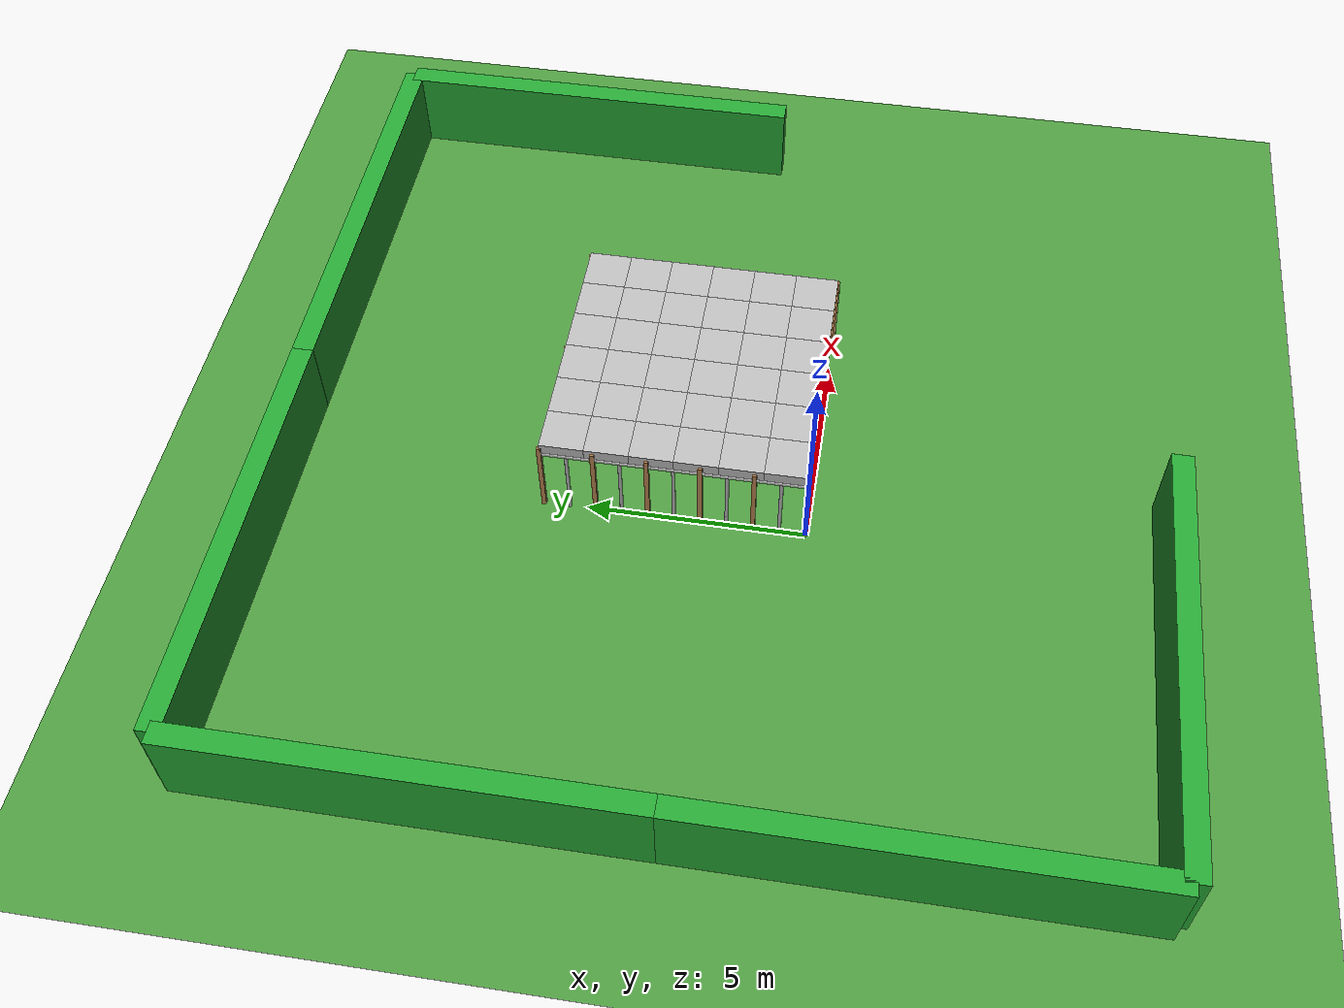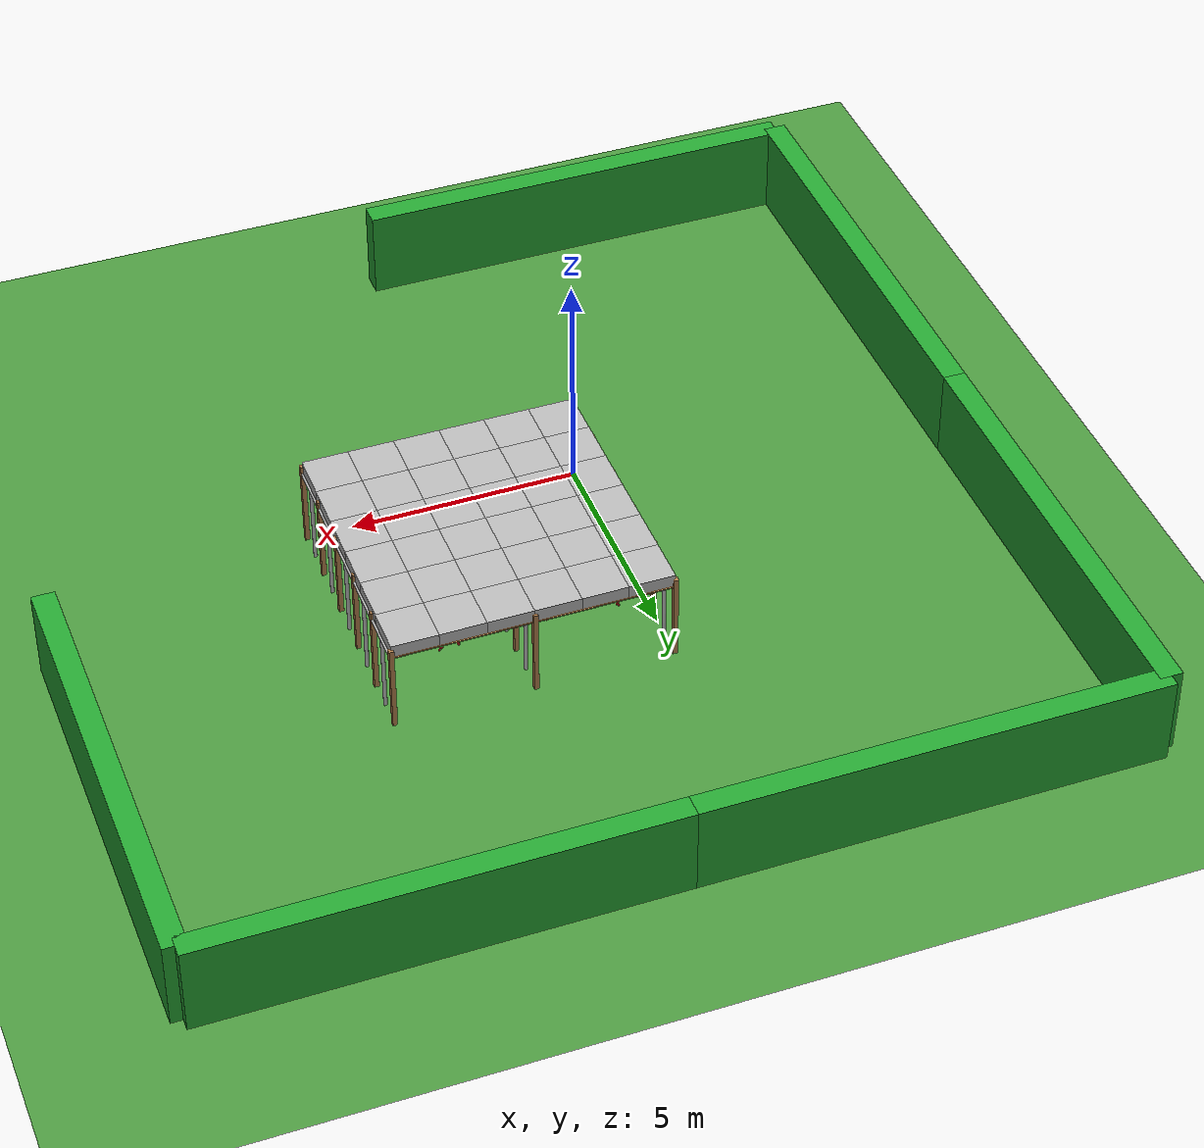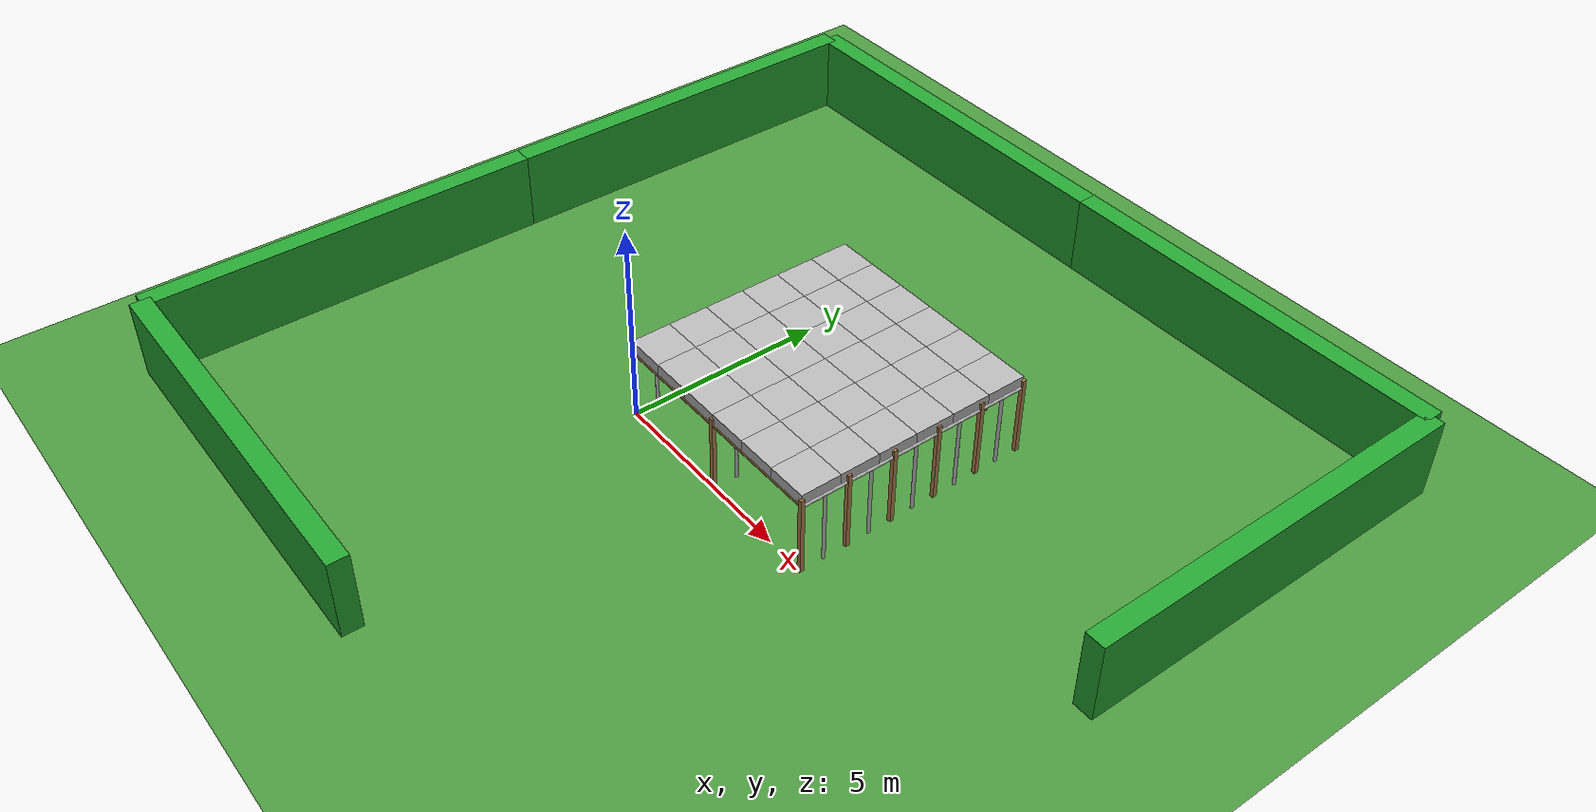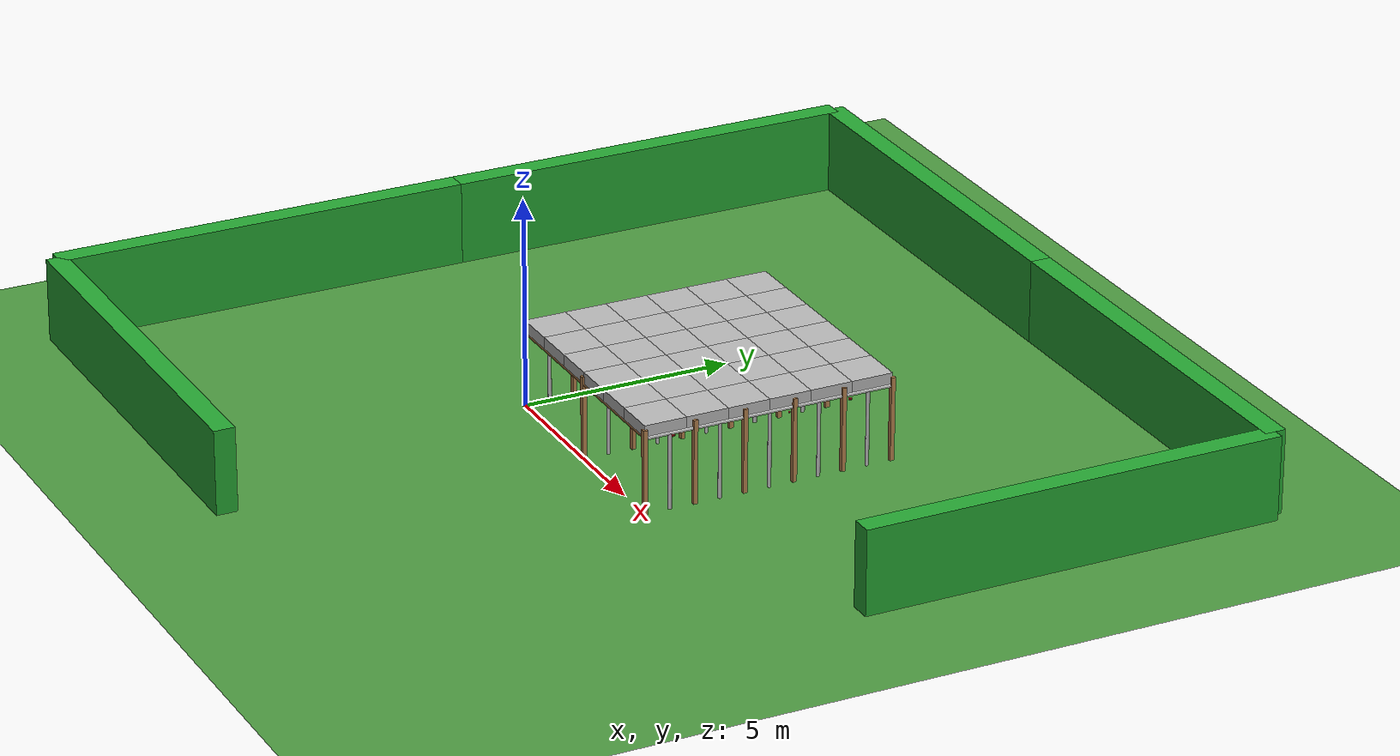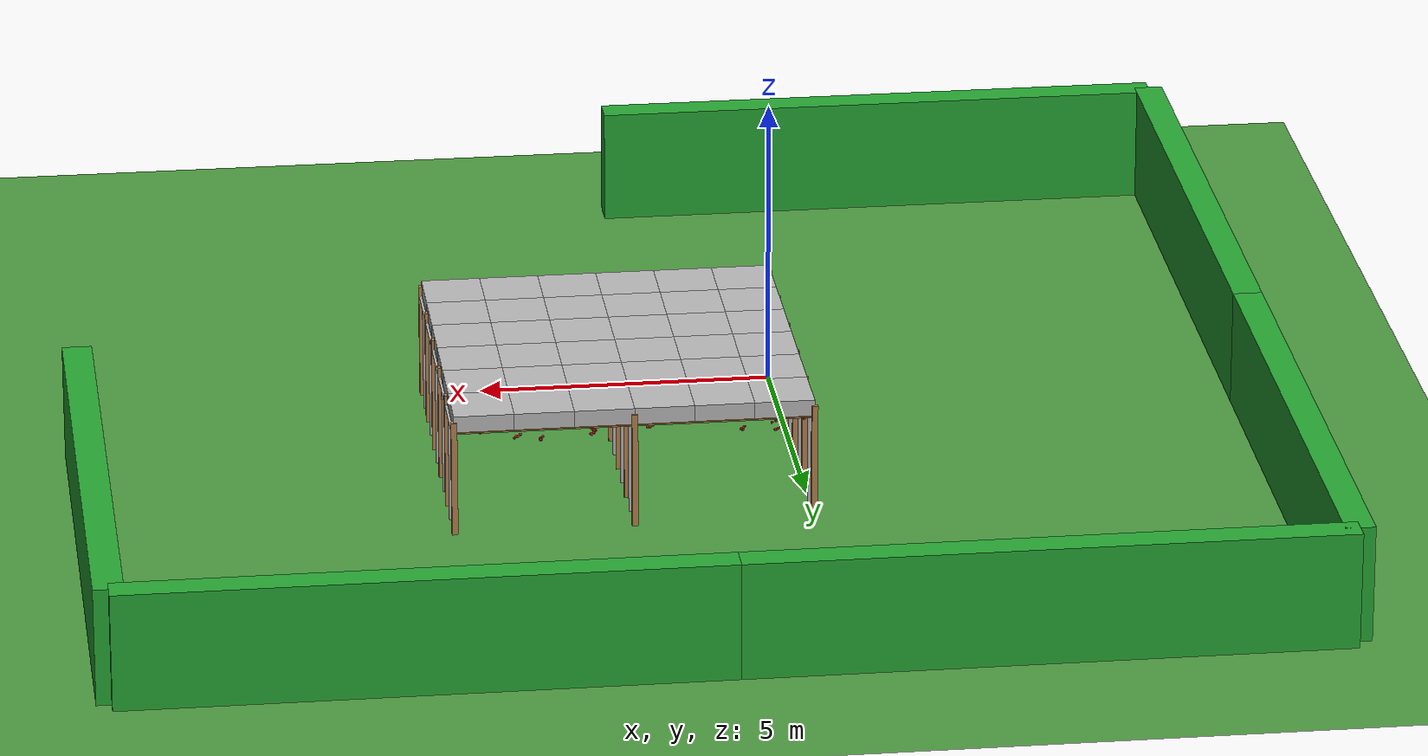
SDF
<!-- This world file contains the pergola model filled with flowers. -->

<?xml version="1.0"?>
<sdf version="1.4">
<world name="demo_world">
	<scene>
		<sky><clouds><speed>0.01</speed></clouds></sky>
		<grid>false</grid>
	</scene>

	<include>
		<uri>model://sun</uri>
		<pose>0 50 10 0 0 0</pose>
	</include>

	<include>
		<uri>model://orchard_ground_plane</uri>
	</include>

	<include>
		<uri>model://pergola</uri>
	</include>

		<!-- Sheltering hedge -->
	<include>
		<name>hedge1a</name>
		<uri>model://hedge</uri>
		<pose>-8 7 0 0 0 1.570796</pose>
	</include>

	<include>
		<name>hedge1b</name>
		<uri>model://hedge</uri>
		<pose>-8 -3 0 0 0 1.570796</pose>
	</include>

	<include>
		<name>hedge2a</name>
		<uri>model://hedge</uri>
		<pose>12 7 0 0 0 1.570796</pose>
	</include>

	<include>
		<name>hedge3</name>
		<uri>model://hedge</uri>
		<pose>-3 -8 0 0 0 0</pose>
	</include>

	<include>
		<name>hedge4a</name>
		<uri>model://hedge</uri>
		<pose>-3 12 0 0 0 0</pose>
	</include>

	<include>
		<name>hedge4b</name>
		<uri>model://hedge</uri>
		<pose>7 12 0 0 0 0</pose>
	</include>
</world>
</sdf>

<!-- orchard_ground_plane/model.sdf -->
<sdf version="1.5">
  <model name="orchard_ground_plane">
    <static>true</static>
    <link name="link">
      <collision name="collision">
        <geometry>
          <plane>
            <normal>0 0 1</normal>
            <size>100 100</size>
          </plane>
        </geometry>
        <surface>
          <friction>
            <ode>
              <mu>100</mu>
              <mu2>50</mu2>
            </ode>
          </friction>
        </surface>
      </collision>
      <visual name="visual">
        <cast_shadows>false</cast_shadows>
        <geometry>
          <plane>
            <normal>0 0 1</normal>
            <size>100 100</size>
          </plane>
        </geometry>
        <material>
          <script>
            <uri>model://orchard_ground_plane/materials/scripts</uri>
            <uri>model://orchard_ground_plane/materials/textures</uri>
            <name>OrchardGround/FlatGrass</name>
          </script>
        </material>
      </visual>
    </link>
  </model>
</sdf>

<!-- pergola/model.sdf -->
<!-- This file contains a model for the pergola structure in the orchard and includes:
18 posts, 12 crossbeams, 15 trees, 60 vines, and 500 fruit. -->
<sdf version='1.4'>
  <model name="pergola">
		<!-- Posts -->

		<include>
			<name>post_0</name>
			<pose>0.0 0.0 0 0 0 0</pose>
			<uri>model://post</uri>
		</include>

		<include>
			<name>post_1</name>
			<pose>0.0 1.2 0 0 0 0</pose>
			<uri>model://post</uri>
		</include>

		<include>
			<name>post_2</name>
			<pose>0.0 2.4 0 0 0 0</pose>
			<uri>model://post</uri>
		</include>

		<include>
			<name>post_3</name>
			<pose>0.0 3.5999999999999996 0 0 0 0</pose>
			<uri>model://post</uri>
		</include>

		<include>
			<name>post_4</name>
			<pose>0.0 4.8 0 0 0 0</pose>
			<uri>model://post</uri>
		</include>

		<include>
			<name>post_5</name>
			<pose>0.0 6.0 0 0 0 0</pose>
			<uri>model://post</uri>
		</include>

		<include>
			<name>post_6</name>
			<pose>3.0 0.0 0 0 0 0</pose>
			<uri>model://post</uri>
		</include>

		<include>
			<name>post_7</name>
			<pose>3.0 1.2 0 0 0 0</pose>
			<uri>model://post</uri>
		</include>

		<include>
			<name>post_8</name>
			<pose>3.0 2.4 0 0 0 0</pose>
			<uri>model://post</uri>
		</include>

		<include>
			<name>post_9</name>
			<pose>3.0 3.5999999999999996 0 0 0 0</pose>
			<uri>model://post</uri>
		</include>

		<include>
			<name>post_10</name>
			<pose>3.0 4.8 0 0 0 0</pose>
			<uri>model://post</uri>
		</include>

		<include>
			<name>post_11</name>
			<pose>3.0 6.0 0 0 0 0</pose>
			<uri>model://post</uri>
		</include>

		<include>
			<name>post_12</name>
			<pose>6.0 0.0 0 0 0 0</pose>
			<uri>model://post</uri>
		</include>

		<include>
			<name>post_13</name>
			<pose>6.0 1.2 0 0 0 0</pose>
			<uri>model://post</uri>
		</include>

		<include>
			<name>post_14</name>
			<pose>6.0 2.4 0 0 0 0</pose>
			<uri>model://post</uri>
		</include>

		<include>
			<name>post_15</name>
			<pose>6.0 3.5999999999999996 0 0 0 0</pose>
			<uri>model://post</uri>
		</include>

		<include>
			<name>post_16</name>
			<pose>6.0 4.8 0 0 0 0</pose>
			<uri>model://post</uri>
		</include>

		<include>
			<name>post_17</name>
			<pose>6.0 6.0 0 0 0 0</pose>
			<uri>model://post</uri>
		</include>

		<!-- Crossbeams -->

    <link name="beam_0">
      <pose>1.5 0.0 1.81 0 0 0</pose>
      <collision name="collision">
        <geometry><box><size>3.0 0.06 0.02</size></box></geometry>
      </collision>
      <visual name="visual">
        <geometry><box><size>3.0 0.06 0.02</size></box></geometry>
        <material><script><uri>model://post/materials/scripts</uri>
            <uri>model://post/materials/textures</uri>
            <name>Post/Wood</name></script></material>
      </visual>
    <inertial>
      <pose>0 0 0 0 0 0</pose>
      <mass>5</mass>
      <inertia>
        <ixx>0.0016666666666666668</ixx><ixy>0.0</ixy><ixz>0.0</ixz><iyy>3.7515</iyy><iyz>0.0</iyz><izz>3.750166666666667</izz>
      </inertia>
    </inertial>
    </link>

    <link name="beam_1">
      <pose>1.5 1.2 1.81 0 0 0</pose>
      <collision name="collision">
        <geometry><box><size>3.0 0.06 0.02</size></box></geometry>
      </collision>
      <visual name="visual">
        <geometry><box><size>3.0 0.06 0.02</size></box></geometry>
        <material><script><uri>model://post/materials/scripts</uri>
            <uri>model://post/materials/textures</uri>
            <name>Post/Wood</name></script></material>
      </visual>
    <inertial>
      <pose>0 0 0 0 0 0</pose>
      <mass>5</mass>
      <inertia>
        <ixx>0.0016666666666666668</ixx><ixy>0.0</ixy><ixz>0.0</ixz><iyy>3.7515</iyy><iyz>0.0</iyz><izz>3.750166666666667</izz>
      </inertia>
    </inertial>
    </link>

    <link name="beam_2">
      <pose>1.5 2.4 1.81 0 0 0</pose>
      <collision name="collision">
        <geometry><box><size>3.0 0.06 0.02</size></box></geometry>
      </collision>
      <visual name="visual">
        <geometry><box><size>3.0 0.06 0.02</size></box></geometry>
        <material><script><uri>model://post/materials/scripts</uri>
            <uri>model://post/materials/textures</uri>
            <name>Post/Wood</name></script></material>
      </visual>
    <inertial>
      <pose>0 0 0 0 0 0</pose>
      <mass>5</mass>
      <inertia>
        <ixx>0.0016666666666666668</ixx><ixy>0.0</ixy><ixz>0.0</ixz><iyy>3.7515</iyy><iyz>0.0</iyz><izz>3.750166666666667</izz>
      </inertia>
    </inertial>
    </link>

    <link name="beam_3">
      <pose>1.5 3.5999999999999996 1.81 0 0 0</pose>
      <collision name="collision">
        <geometry><box><size>3.0 0.06 0.02</size></box></geometry>
      </collision>
      <visual name="visual">
        <geometry><box><size>3.0 0.06 0.02</size></box></geometry>
        <material><script><uri>model://post/materials/scripts</uri>
            <uri>model://post/materials/textures</uri>
            <name>Post/Wood</name></script></material>
      </visual>
    <inertial>
      <pose>0 0 0 0 0 0</pose>
      <mass>5</mass>
      <inertia>
        <ixx>0.0016666666666666668</ixx><ixy>0.0</ixy><ixz>0.0</ixz><iyy>3.7515</iyy><iyz>0.0</iyz><izz>3.750166666666667</izz>
      </inertia>
    </inertial>
    </link>

    <link name="beam_4">
      <pose>1.5 4.8 1.81 0 0 0</pose>
      <collision name="collision">
        <geometry><box><size>3.0 0.06 0.02</size></box></geometry>
      </collision>
      <visual name="visual">
        <geometry><box><size>3.0 0.06 0.02</size></box></geometry>
        <material><script><uri>model://post/materials/scripts</uri>
            <uri>model://post/materials/textures</uri>
            <name>Post/Wood</name></script></material>
      </visual>
    <inertial>
      <pose>0 0 0 0 0 0</pose>
      <mass>5</mass>
      <inertia>
        <ixx>0.0016666666666666668</ixx><ixy>0.0</ixy><ixz>0.0</ixz><iyy>3.7515</iyy><iyz>0.0</iyz><izz>3.750166666666667</izz>
      </inertia>
    </inertial>
    </link>

    <link name="beam_5">
      <pose>1.5 6.0 1.81 0 0 0</pose>
      <collision name="collision">
        <geometry><box><size>3.0 0.06 0.02</size></box></geometry>
      </collision>
      <visual name="visual">
        <geometry><box><size>3.0 0.06 0.02</size></box></geometry>
        <material><script><uri>model://post/materials/scripts</uri>
            <uri>model://post/materials/textures</uri>
            <name>Post/Wood</name></script></material>
      </visual>
    <inertial>
      <pose>0 0 0 0 0 0</pose>
      <mass>5</mass>
      <inertia>
        <ixx>0.0016666666666666668</ixx><ixy>0.0</ixy><ixz>0.0</ixz><iyy>3.7515</iyy><iyz>0.0</iyz><izz>3.750166666666667</izz>
      </inertia>
    </inertial>
    </link>

    <link name="beam_6">
      <pose>4.5 0.0 1.81 0 0 0</pose>
      <collision name="collision">
        <geometry><box><size>3.0 0.06 0.02</size></box></geometry>
      </collision>
      <visual name="visual">
        <geometry><box><size>3.0 0.06 0.02</size></box></geometry>
        <material><script><uri>model://post/materials/scripts</uri>
            <uri>model://post/materials/textures</uri>
            <name>Post/Wood</name></script></material>
      </visual>
    <inertial>
      <pose>0 0 0 0 0 0</pose>
      <mass>5</mass>
      <inertia>
        <ixx>0.0016666666666666668</ixx><ixy>0.0</ixy><ixz>0.0</ixz><iyy>3.7515</iyy><iyz>0.0</iyz><izz>3.750166666666667</izz>
      </inertia>
    </inertial>
    </link>

    <link name="beam_7">
      <pose>4.5 1.2 1.81 0 0 0</pose>
      <collision name="collision">
        <geometry><box><size>3.0 0.06 0.02</size></box></geometry>
      </collision>
      <visual name="visual">
        <geometry><box><size>3.0 0.06 0.02</size></box></geometry>
        <material><script><uri>model://post/materials/scripts</uri>
            <uri>model://post/materials/textures</uri>
            <name>Post/Wood</name></script></material>
      </visual>
    <inertial>
      <pose>0 0 0 0 0 0</pose>
      <mass>5</mass>
      <inertia>
        <ixx>0.0016666666666666668</ixx><ixy>0.0</ixy><ixz>0.0</ixz><iyy>3.7515</iyy><iyz>0.0</iyz><izz>3.750166666666667</izz>
      </inertia>
    </inertial>
    </link>

    <link name="beam_8">
      <pose>4.5 2.4 1.81 0 0 0</pose>
      <collision name="collision">
        <geometry><box><size>3.0 0.06 0.02</size></box></geometry>
      </collision>
      <visual name="visual">
        <geometry><box><size>3.0 0.06 0.02</size></box></geometry>
        <material><script><uri>model://post/materials/scripts</uri>
            <uri>model://post/materials/textures</uri>
            <name>Post/Wood</name></script></material>
      </visual>
    <inertial>
      <pose>0 0 0 0 0 0</pose>
      <mass>5</mass>
      <inertia>
        <ixx>0.0016666666666666668</ixx><ixy>0.0</ixy><ixz>0.0</ixz><iyy>3.7515</iyy><iyz>0.0</iyz><izz>3.750166666666667</izz>
      </inertia>
    </inertial>
    </link>

    <link name="beam_9">
      <pose>4.5 3.5999999999999996 1.81 0 0 0</pose>
      <collision name="collision">
        <geometry><box><size>3.0 0.06 0.02</size></box></geometry>
      </collision>
      <visual name="visual">
        <geometry><box><size>3.0 0.06 0.02</size></box></geometry>
        <material><script><uri>model://post/materials/scripts</uri>
            <uri>model://post/materials/textures</uri>
            <name>Post/Wood</name></script></material>
      </visual>
    <inertial>
      <pose>0 0 0 0 0 0</pose>
      <mass>5</mass>
      <inertia>
        <ixx>0.0016666666666666668</ixx><ixy>0.0</ixy><ixz>0.0</ixz><iyy>3.7515</iyy><iyz>0.0</iyz><izz>3.750166666666667</izz>
      </inertia>
    </inertial>
    </link>

    <link name="beam_10">
      <pose>4.5 4.8 1.81 0 0 0</pose>
      <collision name="collision">
        <geometry><box><size>3.0 0.06 0.02</size></box></geometry>
      </collision>
      <visual name="visual">
        <geometry><box><size>3.0 0.06 0.02</size></box></geometry>
        <material><script><uri>model://post/materials/scripts</uri>
            <uri>model://post/materials/textures</uri>
            <name>Post/Wood</name></script></material>
      </visual>
    <inertial>
      <pose>0 0 0 0 0 0</pose>
      <mass>5</mass>
      <inertia>
        <ixx>0.0016666666666666668</ixx><ixy>0.0</ixy><ixz>0.0</ixz><iyy>3.7515</iyy><iyz>0.0</iyz><izz>3.750166666666667</izz>
      </inertia>
    </inertial>
    </link>

    <link name="beam_11">
      <pose>4.5 6.0 1.81 0 0 0</pose>
      <collision name="collision">
        <geometry><box><size>3.0 0.06 0.02</size></box></geometry>
      </collision>
      <visual name="visual">
        <geometry><box><size>3.0 0.06 0.02</size></box></geometry>
        <material><script><uri>model://post/materials/scripts</uri>
            <uri>model://post/materials/textures</uri>
            <name>Post/Wood</name></script></material>
      </visual>
    <inertial>
      <pose>0 0 0 0 0 0</pose>
      <mass>5</mass>
      <inertia>
        <ixx>0.0016666666666666668</ixx><ixy>0.0</ixy><ixz>0.0</ixz><iyy>3.7515</iyy><iyz>0.0</iyz><izz>3.750166666666667</izz>
      </inertia>
    </inertial>
    </link>

		<!-- Tree trunks -->

		<include>
			<name>tree_0</name>
			<pose>0.0 0.6 0 0 0 0</pose>
			<uri>model://tree_trunk</uri>
		</include>

		<include>
			<name>tree_1</name>
			<pose>0.0 1.7999999999999998 0 0 0 0</pose>
			<uri>model://tree_trunk</uri>
		</include>

		<include>
			<name>tree_2</name>
			<pose>0.0 3.0 0 0 0 0</pose>
			<uri>model://tree_trunk</uri>
		</include>

		<include>
			<name>tree_3</name>
			<pose>0.0 4.199999999999999 0 0 0 0</pose>
			<uri>model://tree_trunk</uri>
		</include>

		<include>
			<name>tree_4</name>
			<pose>0.0 5.3999999999999995 0 0 0 0</pose>
			<uri>model://tree_trunk</uri>
		</include>

		<include>
			<name>tree_5</name>
			<pose>3.0 0.6 0 0 0 0</pose>
			<uri>model://tree_trunk</uri>
		</include>

		<include>
			<name>tree_6</name>
			<pose>3.0 1.7999999999999998 0 0 0 0</pose>
			<uri>model://tree_trunk</uri>
		</include>

		<include>
			<name>tree_7</name>
			<pose>3.0 3.0 0 0 0 0</pose>
			<uri>model://tree_trunk</uri>
		</include>

		<include>
			<name>tree_8</name>
			<pose>3.0 4.199999999999999 0 0 0 0</pose>
			<uri>model://tree_trunk</uri>
		</include>

		<include>
			<name>tree_9</name>
			<pose>3.0 5.3999999999999995 0 0 0 0</pose>
			<uri>model://tree_trunk</uri>
		</include>

		<include>
			<name>tree_10</name>
			<pose>6.0 0.6 0 0 0 0</pose>
			<uri>model://tree_trunk</uri>
		</include>

		<include>
			<name>tree_11</name>
			<pose>6.0 1.7999999999999998 0 0 0 0</pose>
			<uri>model://tree_trunk</uri>
		</include>

		<include>
			<name>tree_12</name>
			<pose>6.0 3.0 0 0 0 0</pose>
			<uri>model://tree_trunk</uri>
		</include>

		<include>
			<name>tree_13</name>
			<pose>6.0 4.199999999999999 0 0 0 0</pose>
			<uri>model://tree_trunk</uri>
		</include>

		<include>
			<name>tree_14</name>
			<pose>6.0 5.3999999999999995 0 0 0 0</pose>
			<uri>model://tree_trunk</uri>
		</include>

		<!-- Base branches along rows of trees. (Base branches are similar to the trunk growing horizontally along pergola) -->

    <link name="baseBranch_0">
      <pose>0.0 0.6 1.8 1.5707963267948966 0 0</pose>
      <collision name="collision">
        <geometry><cylinder><radius>0.04</radius> <length>1.2</length></cylinder></geometry>
      </collision>
      <visual name="visual">
        <geometry><cylinder><radius>0.04</radius> <length>1.2</length></cylinder></geometry>
        <material><script><uri>model://tree_trunk/materials/scripts</uri>
            <uri>model://tree_trunk/materials/textures</uri>
            <name>Tree/Bark</name></script></material>
      </visual>
    <inertial>
      <pose>0 0 0 0 0 0</pose>
      <mass>10</mass>
      <inertia>
        <ixx>1.204</ixx><ixy>0.0</ixy><ixz>0.0</ixz><iyy>1.204</iyy><iyz>0.0</iyz><izz>0.008</izz>
      </inertia>
    </inertial>
    </link>

    <link name="baseBranch_1">
      <pose>0.0 1.7999999999999998 1.8 1.5707963267948966 0 0</pose>
      <collision name="collision">
        <geometry><cylinder><radius>0.04</radius> <length>1.2</length></cylinder></geometry>
      </collision>
      <visual name="visual">
        <geometry><cylinder><radius>0.04</radius> <length>1.2</length></cylinder></geometry>
        <material><script><uri>model://tree_trunk/materials/scripts</uri>
            <uri>model://tree_trunk/materials/textures</uri>
            <name>Tree/Bark</name></script></material>
      </visual>
    <inertial>
      <pose>0 0 0 0 0 0</pose>
      <mass>10</mass>
      <inertia>
        <ixx>1.204</ixx><ixy>0.0</ixy><ixz>0.0</ixz><iyy>1.204</iyy><iyz>0.0</iyz><izz>0.008</izz>
      </inertia>
    </inertial>
    </link>

    <link name="baseBranch_2">
      <pose>0.0 3.0 1.8 1.5707963267948966 0 0</pose>
      <collision name="collision">
        <geometry><cylinder><radius>0.04</radius> <length>1.2</length></cylinder></geometry>
      </collision>
      <visual name="visual">
        <geometry><cylinder><radius>0.04</radius> <length>1.2</length></cylinder></geometry>
        <material><script><uri>model://tree_trunk/materials/scripts</uri>
            <uri>model://tree_trunk/materials/textures</uri>
            <name>Tree/Bark</name></script></material>
      </visual>
    <inertial>
      <pose>0 0 0 0 0 0</pose>
      <mass>10</mass>
      <inertia>
        <ixx>1.204</ixx><ixy>0.0</ixy><ixz>0.0</ixz><iyy>1.204</iyy><iyz>0.0</iyz><izz>0.008</izz>
      </inertia>
    </inertial>
    </link>

    <link name="baseBranch_3">
      <pose>0.0 4.199999999999999 1.8 1.5707963267948966 0 0</pose>
      <collision name="collision">
        <geometry><cylinder><radius>0.04</radius> <length>1.2</length></cylinder></geometry>
      </collision>
      <visual name="visual">
        <geometry><cylinder><radius>0.04</radius> <length>1.2</length></cylinder></geometry>
        <material><script><uri>model://tree_trunk/materials/scripts</uri>
            <uri>model://tree_trunk/materials/textures</uri>
            <name>Tree/Bark</name></script></material>
      </visual>
    <inertial>
      <pose>0 0 0 0 0 0</pose>
      <mass>10</mass>
      <inertia>
        <ixx>1.204</ixx><ixy>0.0</ixy><ixz>0.0</ixz><iyy>1.204</iyy><iyz>0.0</iyz><izz>0.008</izz>
      </inertia>
    </inertial>
    </link>

    <link name="baseBranch_4">
      <pose>0.0 5.3999999999999995 1.8 1.5707963267948966 0 0</pose>
      <collision name="collision">
        <geometry><cylinder><radius>0.04</radius> <length>1.2</length></cylinder></geometry>
      </collision>
      <visual name="visual">
        <geometry><cylinder><radius>0.04</radius> <length>1.2</length></cylinder></geometry>
        <material><script><uri>model://tree_trunk/materials/scripts</uri>
            <uri>model://tree_trunk/materials/textures</uri>
            <name>Tree/Bark</name></script></material>
      </visual>
    <inertial>
      <pose>0 0 0 0 0 0</pose>
      <mass>10</mass>
      <inertia>
        <ixx>1.204</ixx><ixy>0.0</ixy><ixz>0.0</ixz><iyy>1.204</iyy><iyz>0.0</iyz><izz>0.008</izz>
      </inertia>
    </inertial>
    </link>

    <link name="baseBranch_5">
      <pose>3.0 0.6 1.8 1.5707963267948966 0 0</pose>
      <collision name="collision">
        <geometry><cylinder><radius>0.04</radius> <length>1.2</length></cylinder></geometry>
      </collision>
      <visual name="visual">
        <geometry><cylinder><radius>0.04</radius> <length>1.2</length></cylinder></geometry>
        <material><script><uri>model://tree_trunk/materials/scripts</uri>
            <uri>model://tree_trunk/materials/textures</uri>
            <name>Tree/Bark</name></script></material>
      </visual>
    <inertial>
      <pose>0 0 0 0 0 0</pose>
      <mass>10</mass>
      <inertia>
        <ixx>1.204</ixx><ixy>0.0</ixy><ixz>0.0</ixz><iyy>1.204</iyy><iyz>0.0</iyz><izz>0.008</izz>
      </inertia>
    </inertial>
    </link>

    <link name="baseBranch_6">
      <pose>3.0 1.7999999999999998 1.8 1.5707963267948966 0 0</pose>
      <collision name="collision">
        <geometry><cylinder><radius>0.04</radius> <length>1.2</length></cylinder></geometry>
      </collision>
      <visual name="visual">
        <geometry><cylinder><radius>0.04</radius> <length>1.2</length></cylinder></geometry>
        <material><script><uri>model://tree_trunk/materials/scripts</uri>
            <uri>model://tree_trunk/materials/textures</uri>
            <name>Tree/Bark</name></script></material>
      </visual>
    <inertial>
      <pose>0 0 0 0 0 0</pose>
      <mass>10</mass>
      <inertia>
        <ixx>1.204</ixx><ixy>0.0</ixy><ixz>0.0</ixz><iyy>1.204</iyy><iyz>0.0</iyz><izz>0.008</izz>
      </inertia>
    </inertial>
    </link>

    <link name="baseBranch_7">
      <pose>3.0 3.0 1.8 1.5707963267948966 0 0</pose>
      <collision name="collision">
        <geometry><cylinder><radius>0.04</radius> <length>1.2</length></cylinder></geometry>
      </collision>
      <visual name="visual">
        <geometry><cylinder><radius>0.04</radius> <length>1.2</length></cylinder></geometry>
        <material><script><uri>model://tree_trunk/materials/scripts</uri>
            <uri>model://tree_trunk/materials/textures</uri>
            <name>Tree/Bark</name></script></material>
      </visual>
    <inertial>
      <pose>0 0 0 0 0 0</pose>
      <mass>10</mass>
      <inertia>
        <ixx>1.204</ixx><ixy>0.0</ixy><ixz>0.0</ixz><iyy>1.204</iyy><iyz>0.0</iyz><izz>0.008</izz>
      </inertia>
    </inertial>
    </link>

    <link name="baseBranch_8">
      <pose>3.0 4.199999999999999 1.8 1.5707963267948966 0 0</pose>
      <collision name="collision">
        <geometry><cylinder><radius>0.04</radius> <length>1.2</length></cylinder></geometry>
      </collision>
      <visual name="visual">
        <geometry><cylinder><radius>0.04</radius> <length>1.2</length></cylinder></geometry>
        <material><script><uri>model://tree_trunk/materials/scripts</uri>
            <uri>model://tree_trunk/materials/textures</uri>
            <name>Tree/Bark</name></script></material>
      </visual>
    <inertial>
      <pose>0 0 0 0 0 0</pose>
      <mass>10</mass>
      <inertia>
        <ixx>1.204</ixx><ixy>0.0</ixy><ixz>0.0</ixz><iyy>1.204</iyy><iyz>0.0</iyz><izz>0.008</izz>
      </inertia>
    </inertial>
    </link>

    <link name="baseBranch_9">
      <pose>3.0 5.3999999999999995 1.8 1.5707963267948966 0 0</pose>
      <collision name="collision">
        <geometry><cylinder><radius>0.04</radius> <length>1.2</length></cylinder></geometry>
      </collision>
      <visual name="visual">
        <geometry><cylinder><radius>0.04</radius> <length>1.2</length></cylinder></geometry>
        <material><script><uri>model://tree_trunk/materials/scripts</uri>
            <uri>model://tree_trunk/materials/textures</uri>
            <name>Tree/Bark</name></script></material>
      </visual>
    <inertial>
      <pose>0 0 0 0 0 0</pose>
      <mass>10</mass>
      <inertia>
        <ixx>1.204</ixx><ixy>0.0</ixy><ixz>0.0</ixz><iyy>1.204</iyy><iyz>0.0</iyz><izz>0.008</izz>
      </inertia>
    </inertial>
    </link>

    <link name="baseBranch_10">
      <pose>6.0 0.6 1.8 1.5707963267948966 0 0</pose>
      <collision name="collision">
        <geometry><cylinder><radius>0.04</radius> <length>1.2</length></cylinder></geometry>
      </collision>
      <visual name="visual">
        <geometry><cylinder><radius>0.04</radius> <length>1.2</length></cylinder></geometry>
        <material><script><uri>model://tree_trunk/materials/scripts</uri>
            <uri>model://tree_trunk/materials/textures</uri>
            <name>Tree/Bark</name></script></material>
      </visual>
    <inertial>
      <pose>0 0 0 0 0 0</pose>
      <mass>10</mass>
      <inertia>
        <ixx>1.204</ixx><ixy>0.0</ixy><ixz>0.0</ixz><iyy>1.204</iyy><iyz>0.0</iyz><izz>0.008</izz>
      </inertia>
    </inertial>
    </link>

    <link name="baseBranch_11">
      <pose>6.0 1.7999999999999998 1.8 1.5707963267948966 0 0</pose>
      <collision name="collision">
        <geometry><cylinder><radius>0.04</radius> <length>1.2</length></cylinder></geometry>
      </collision>
      <visual name="visual">
        <geometry><cylinder><radius>0.04</radius> <length>1.2</length></cylinder></geometry>
        <material><script><uri>model://tree_trunk/materials/scripts</uri>
            <uri>model://tree_trunk/materials/textures</uri>
            <name>Tree/Bark</name></script></material>
      </visual>
    <inertial>
      <pose>0 0 0 0 0 0</pose>
      <mass>10</mass>
      <inertia>
        <ixx>1.204</ixx><ixy>0.0</ixy><ixz>0.0</ixz><iyy>1.204</iyy><iyz>0.0</iyz><izz>0.008</izz>
      </inertia>
    </inertial>
    </link>

    <link name="baseBranch_12">
      <pose>6.0 3.0 1.8 1.5707963267948966 0 0</pose>
      <collision name="collision">
        <geometry><cylinder><radius>0.04</radius> <length>1.2</length></cylinder></geometry>
      </collision>
      <visual name="visual">
        <geometry><cylinder><radius>0.04</radius> <length>1.2</length></cylinder></geometry>
        <material><script><uri>model://tree_trunk/materials/scripts</uri>
            <uri>model://tree_trunk/materials/textures</uri>
            <name>Tree/Bark</name></script></material>
      </visual>
    <inertial>
      <pose>0 0 0 0 0 0</pose>
      <mass>10</mass>
      <inertia>
        <ixx>1.204</ixx><ixy>0.0</ixy><ixz>0.0</ixz><iyy>1.204</iyy><iyz>0.0</iyz><izz>0.008</izz>
      </inertia>
    </inertial>
    </link>

    <link name="baseBranch_13">
      <pose>6.0 4.199999999999999 1.8 1.5707963267948966 0 0</pose>
      <collision name="collision">
        <geometry><cylinder><radius>0.04</radius> <length>1.2</length></cylinder></geometry>
      </collision>
      <visual name="visual">
        <geometry><cylinder><radius>0.04</radius> <length>1.2</length></cylinder></geometry>
        <material><script><uri>model://tree_trunk/materials/scripts</uri>
            <uri>model://tree_trunk/materials/textures</uri>
            <name>Tree/Bark</name></script></material>
      </visual>
    <inertial>
      <pose>0 0 0 0 0 0</pose>
      <mass>10</mass>
      <inertia>
        <ixx>1.204</ixx><ixy>0.0</ixy><ixz>0.0</ixz><iyy>1.204</iyy><iyz>0.0</iyz><izz>0.008</izz>
      </inertia>
    </inertial>
    </link>

    <link name="baseBranch_14">
      <pose>6.0 5.3999999999999995 1.8 1.5707963267948966 0 0</pose>
      <collision name="collision">
        <geometry><cylinder><radius>0.04</radius> <length>1.2</length></cylinder></geometry>
      </collision>
      <visual name="visual">
        <geometry><cylinder><radius>0.04</radius> <length>1.2</length></cylinder></geometry>
        <material><script><uri>model://tree_trunk/materials/scripts</uri>
            <uri>model://tree_trunk/materials/textures</uri>
            <name>Tree/Bark</name></script></material>
      </visual>
    <inertial>
      <pose>0 0 0 0 0 0</pose>
      <mass>10</mass>
      <inertia>
        <ixx>1.204</ixx><ixy>0.0</ixy><ixz>0.0</ixz><iyy>1.204</iyy><iyz>0.0</iyz><izz>0.008</izz>
      </inertia>
    </inertial>
    </link>

		<!-- Vines across base branches. Vines consist of an ascending and descending portion to simulate a raised canopy. -->

    <link name="vine_0">
      <pose>0.75 0.03 1.85 0 1.5374753309166493 0</pose>
      <collision name="collision">
        <geometry><cylinder><radius>0.01</radius> <length>1.5008331019803633</length></cylinder></geometry>
      </collision>
      <visual name="visual">
        <geometry><cylinder><radius>0.01</radius> <length>1.5008331019803633</length></cylinder></geometry>
        <material><script><uri>model://tree_trunk/materials/scripts</uri>
            <uri>model://tree_trunk/materials/textures</uri>
            <name>Tree/Bark</name></script></material>
      </visual>
    <inertial>
      <pose>0 0 0 0 0 0</pose>
      <mass>5</mass>
      <inertia>
        <ixx>0.9386666666666668</ixx><ixy>0.0</ixy><ixz>0.0</ixz><iyy>0.9386666666666668</iyy><iyz>0.0</iyz><izz>0.00025</izz>
      </inertia>
    </inertial>
    </link>

    <link name="vine_1">
      <pose>2.25 0.03 1.85 0 -1.5374753309166493 0</pose>
      <collision name="collision">
        <geometry><cylinder><radius>0.01</radius> <length>1.5008331019803633</length></cylinder></geometry>
      </collision>
      <visual name="visual">
        <geometry><cylinder><radius>0.01</radius> <length>1.5008331019803633</length></cylinder></geometry>
        <material><script><uri>model://tree_trunk/materials/scripts</uri>
            <uri>model://tree_trunk/materials/textures</uri>
            <name>Tree/Bark</name></script></material>
      </visual>
    <inertial>
      <pose>0 0 0 0 0 0</pose>
      <mass>5</mass>
      <inertia>
        <ixx>0.9386666666666668</ixx><ixy>0.0</ixy><ixz>0.0</ixz><iyy>0.9386666666666668</iyy><iyz>0.0</iyz><izz>0.00025</izz>
      </inertia>
    </inertial>
    </link>

    <link name="vine_2">
      <pose>0.75 0.32999999999999996 1.85 0 1.5374753309166493 0</pose>
      <collision name="collision">
        <geometry><cylinder><radius>0.01</radius> <length>1.5008331019803633</length></cylinder></geometry>
      </collision>
      <visual name="visual">
        <geometry><cylinder><radius>0.01</radius> <length>1.5008331019803633</length></cylinder></geometry>
        <material><script><uri>model://tree_trunk/materials/scripts</uri>
            <uri>model://tree_trunk/materials/textures</uri>
            <name>Tree/Bark</name></script></material>
      </visual>
    <inertial>
      <pose>0 0 0 0 0 0</pose>
      <mass>5</mass>
      <inertia>
        <ixx>0.9386666666666668</ixx><ixy>0.0</ixy><ixz>0.0</ixz><iyy>0.9386666666666668</iyy><iyz>0.0</iyz><izz>0.00025</izz>
      </inertia>
    </inertial>
    </link>

    <link name="vine_3">
      <pose>2.25 0.32999999999999996 1.85 0 -1.5374753309166493 0</pose>
      <collision name="collision">
        <geometry><cylinder><radius>0.01</radius> <length>1.5008331019803633</length></cylinder></geometry>
      </collision>
      <visual name="visual">
        <geometry><cylinder><radius>0.01</radius> <length>1.5008331019803633</length></cylinder></geometry>
        <material><script><uri>model://tree_trunk/materials/scripts</uri>
            <uri>model://tree_trunk/materials/textures</uri>
            <name>Tree/Bark</name></script></material>
      </visual>
    <inertial>
      <pose>0 0 0 0 0 0</pose>
      <mass>5</mass>
      <inertia>
        <ixx>0.9386666666666668</ixx><ixy>0.0</ixy><ixz>0.0</ixz><iyy>0.9386666666666668</iyy><iyz>0.0</iyz><izz>0.00025</izz>
      </inertia>
    </inertial>
    </link>

    <link name="vine_4">
      <pose>0.75 0.63 1.85 0 1.5374753309166493 0</pose>
      <collision name="collision">
        <geometry><cylinder><radius>0.01</radius> <length>1.5008331019803633</length></cylinder></geometry>
      </collision>
      <visual name="visual">
        <geometry><cylinder><radius>0.01</radius> <length>1.5008331019803633</length></cylinder></geometry>
        <material><script><uri>model://tree_trunk/materials/scripts</uri>
            <uri>model://tree_trunk/materials/textures</uri>
            <name>Tree/Bark</name></script></material>
      </visual>
    <inertial>
      <pose>0 0 0 0 0 0</pose>
      <mass>5</mass>
      <inertia>
        <ixx>0.9386666666666668</ixx><ixy>0.0</ixy><ixz>0.0</ixz><iyy>0.9386666666666668</iyy><iyz>0.0</iyz><izz>0.00025</izz>
      </inertia>
    </inertial>
    </link>

    <link name="vine_5">
      <pose>2.25 0.63 1.85 0 -1.5374753309166493 0</pose>
      <collision name="collision">
        <geometry><cylinder><radius>0.01</radius> <length>1.5008331019803633</length></cylinder></geometry>
      </collision>
      <visual name="visual">
        <geometry><cylinder><radius>0.01</radius> <length>1.5008331019803633</length></cylinder></geometry>
        <material><script><uri>model://tree_trunk/materials/scripts</uri>
            <uri>model://tree_trunk/materials/textures</uri>
            <name>Tree/Bark</name></script></material>
      </visual>
    <inertial>
      <pose>0 0 0 0 0 0</pose>
      <mass>5</mass>
      <inertia>
        <ixx>0.9386666666666668</ixx><ixy>0.0</ixy><ixz>0.0</ixz><iyy>0.9386666666666668</iyy><iyz>0.0</iyz><izz>0.00025</izz>
      </inertia>
    </inertial>
    </link>

    <link name="vine_6">
      <pose>0.75 0.9299999999999999 1.85 0 1.5374753309166493 0</pose>
      <collision name="collision">
        <geometry><cylinder><radius>0.01</radius> <length>1.5008331019803633</length></cylinder></geometry>
      </collision>
      <visual name="visual">
        <geometry><cylinder><radius>0.01</radius> <length>1.5008331019803633</length></cylinder></geometry>
        <material><script><uri>model://tree_trunk/materials/scripts</uri>
            <uri>model://tree_trunk/materials/textures</uri>
            <name>Tree/Bark</name></script></material>
      </visual>
    <inertial>
      <pose>0 0 0 0 0 0</pose>
      <mass>5</mass>
      <inertia>
        <ixx>0.9386666666666668</ixx><ixy>0.0</ixy><ixz>0.0</ixz><iyy>0.9386666666666668</iyy><iyz>0.0</iyz><izz>0.00025</izz>
      </inertia>
    </inertial>
    </link>

    <link name="vine_7">
      <pose>2.25 0.9299999999999999 1.85 0 -1.5374753309166493 0</pose>
      <collision name="collision">
        <geometry><cylinder><radius>0.01</radius> <length>1.5008331019803633</length></cylinder></geometry>
      </collision>
      <visual name="visual">
        <geometry><cylinder><radius>0.01</radius> <length>1.5008331019803633</length></cylinder></geometry>
        <material><script><uri>model://tree_trunk/materials/scripts</uri>
            <uri>model://tree_trunk/materials/textures</uri>
            <name>Tree/Bark</name></script></material>
      </visual>
    <inertial>
      <pose>0 0 0 0 0 0</pose>
      <mass>5</mass>
      <inertia>
        <ixx>0.9386666666666668</ixx><ixy>0.0</ixy><ixz>0.0</ixz><iyy>0.9386666666666668</iyy><iyz>0.0</iyz><izz>0.00025</izz>
      </inertia>
    </inertial>
    </link>

    <link name="vine_8">
      <pose>0.75 1.23 1.85 0 1.5374753309166493 0</pose>
      <collision name="collision">
        <geometry><cylinder><radius>0.01</radius> <length>1.5008331019803633</length></cylinder></geometry>
      </collision>
      <visual name="visual">
        <geometry><cylinder><radius>0.01</radius> <length>1.5008331019803633</length></cylinder></geometry>
        <material><script><uri>model://tree_trunk/materials/scripts</uri>
            <uri>model://tree_trunk/materials/textures</uri>
            <name>Tree/Bark</name></script></material>
      </visual>
    <inertial>
      <pose>0 0 0 0 0 0</pose>
      <mass>5</mass>
      <inertia>
        <ixx>0.9386666666666668</ixx><ixy>0.0</ixy><ixz>0.0</ixz><iyy>0.9386666666666668</iyy><iyz>0.0</iyz><izz>0.00025</izz>
      </inertia>
    </inertial>
    </link>

    <link name="vine_9">
      <pose>2.25 1.23 1.85 0 -1.5374753309166493 0</pose>
      <collision name="collision">
        <geometry><cylinder><radius>0.01</radius> <length>1.5008331019803633</length></cylinder></geometry>
      </collision>
      <visual name="visual">
        <geometry><cylinder><radius>0.01</radius> <length>1.5008331019803633</length></cylinder></geometry>
        <material><script><uri>model://tree_trunk/materials/scripts</uri>
            <uri>model://tree_trunk/materials/textures</uri>
            <name>Tree/Bark</name></script></material>
      </visual>
    <inertial>
      <pose>0 0 0 0 0 0</pose>
      <mass>5</mass>
      <inertia>
        <ixx>0.9386666666666668</ixx><ixy>0.0</ixy><ixz>0.0</ixz><iyy>0.9386666666666668</iyy><iyz>0.0</iyz><izz>0.00025</izz>
      </inertia>
    </inertial>
    </link>

    <link name="vine_10">
      <pose>0.75 1.53 1.85 0 1.5374753309166493 0</pose>
      <collision name="collision">
        <geometry><cylinder><radius>0.01</radius> <length>1.5008331019803633</length></cylinder></geometry>
      </collision>
      <visual name="visual">
        <geometry><cylinder><radius>0.01</radius> <length>1.5008331019803633</length></cylinder></geometry>
        <material><script><uri>model://tree_trunk/materials/scripts</uri>
            <uri>model://tree_trunk/materials/textures</uri>
            <name>Tree/Bark</name></script></material>
      </visual>
    <inertial>
      <pose>0 0 0 0 0 0</pose>
      <mass>5</mass>
      <inertia>
        <ixx>0.9386666666666668</ixx><ixy>0.0</ixy><ixz>0.0</ixz><iyy>0.9386666666666668</iyy><iyz>0.0</iyz><izz>0.00025</izz>
      </inertia>
    </inertial>
    </link>

    <link name="vine_11">
      <pose>2.25 1.53 1.85 0 -1.5374753309166493 0</pose>
      <collision name="collision">
        <geometry><cylinder><radius>0.01</radius> <length>1.5008331019803633</length></cylinder></geometry>
      </collision>
      <visual name="visual">
        <geometry><cylinder><radius>0.01</radius> <length>1.5008331019803633</length></cylinder></geometry>
        <material><script><uri>model://tree_trunk/materials/scripts</uri>
            <uri>model://tree_trunk/materials/textures</uri>
            <name>Tree/Bark</name></script></material>
      </visual>
    <inertial>
      <pose>0 0 0 0 0 0</pose>
      <mass>5</mass>
      <inertia>
        <ixx>0.9386666666666668</ixx><ixy>0.0</ixy><ixz>0.0</ixz><iyy>0.9386666666666668</iyy><iyz>0.0</iyz><izz>0.00025</izz>
      </inertia>
    </inertial>
    </link>

    <link name="vine_12">
      <pose>0.75 1.8299999999999998 1.85 0 1.5374753309166493 0</pose>
      <collision name="collision">
        <geometry><cylinder><radius>0.01</radius> <length>1.5008331019803633</length></cylinder></geometry>
      </collision>
      <visual name="visual">
        <geometry><cylinder><radius>0.01</radius> <length>1.5008331019803633</length></cylinder></geometry>
        <material><script><uri>model://tree_trunk/materials/scripts</uri>
            <uri>model://tree_trunk/materials/textures</uri>
            <name>Tree/Bark</name></script></material>
      </visual>
    <inertial>
      <pose>0 0 0 0 0 0</pose>
      <mass>5</mass>
      <inertia>
        <ixx>0.9386666666666668</ixx><ixy>0.0</ixy><ixz>0.0</ixz><iyy>0.9386666666666668</iyy><iyz>0.0</iyz><izz>0.00025</izz>
      </inertia>
    </inertial>
    </link>

    <link name="vine_13">
      <pose>2.25 1.8299999999999998 1.85 0 -1.5374753309166493 0</pose>
      <collision name="collision">
        <geometry><cylinder><radius>0.01</radius> <length>1.5008331019803633</length></cylinder></geometry>
      </collision>
      <visual name="visual">
        <geometry><cylinder><radius>0.01</radius> <length>1.5008331019803633</length></cylinder></geometry>
        <material><script><uri>model://tree_trunk/materials/scripts</uri>
            <uri>model://tree_trunk/materials/textures</uri>
            <name>Tree/Bark</name></script></material>
      </visual>
    <inertial>
      <pose>0 0 0 0 0 0</pose>
      <mass>5</mass>
      <inertia>
        <ixx>0.9386666666666668</ixx><ixy>0.0</ixy><ixz>0.0</ixz><iyy>0.9386666666666668</iyy><iyz>0.0</iyz><izz>0.00025</izz>
      </inertia>
    </inertial>
    </link>

    <link name="vine_14">
      <pose>0.75 2.13 1.85 0 1.5374753309166493 0</pose>
      <collision name="collision">
        <geometry><cylinder><radius>0.01</radius> <length>1.5008331019803633</length></cylinder></geometry>
      </collision>
      <visual name="visual">
        <geometry><cylinder><radius>0.01</radius> <length>1.5008331019803633</length></cylinder></geometry>
        <material><script><uri>model://tree_trunk/materials/scripts</uri>
            <uri>model://tree_trunk/materials/textures</uri>
            <name>Tree/Bark</name></script></material>
      </visual>
    <inertial>
      <pose>0 0 0 0 0 0</pose>
      <mass>5</mass>
      <inertia>
        <ixx>0.9386666666666668</ixx><ixy>0.0</ixy><ixz>0.0</ixz><iyy>0.9386666666666668</iyy><iyz>0.0</iyz><izz>0.00025</izz>
      </inertia>
    </inertial>
    </link>

    <link name="vine_15">
      <pose>2.25 2.13 1.85 0 -1.5374753309166493 0</pose>
      <collision name="collision">
        <geometry><cylinder><radius>0.01</radius> <length>1.5008331019803633</length></cylinder></geometry>
      </collision>
      <visual name="visual">
        <geometry><cylinder><radius>0.01</radius> <length>1.5008331019803633</length></cylinder></geometry>
        <material><script><uri>model://tree_trunk/materials/scripts</uri>
            <uri>model://tree_trunk/materials/textures</uri>
            <name>Tree/Bark</name></script></material>
      </visual>
    <inertial>
      <pose>0 0 0 0 0 0</pose>
      <mass>5</mass>
      <inertia>
        <ixx>0.9386666666666668</ixx><ixy>0.0</ixy><ixz>0.0</ixz><iyy>0.9386666666666668</iyy><iyz>0.0</iyz><izz>0.00025</izz>
      </inertia>
    </inertial>
    </link>

    <link name="vine_16">
      <pose>0.75 2.4299999999999997 1.85 0 1.5374753309166493 0</pose>
      <collision name="collision">
        <geometry><cylinder><radius>0.01</radius> <length>1.5008331019803633</length></cylinder></geometry>
      </collision>
      <visual name="visual">
        <geometry><cylinder><radius>0.01</radius> <length>1.5008331019803633</length></cylinder></geometry>
        <material><script><uri>model://tree_trunk/materials/scripts</uri>
            <uri>model://tree_trunk/materials/textures</uri>
            <name>Tree/Bark</name></script></material>
      </visual>
    <inertial>
      <pose>0 0 0 0 0 0</pose>
      <mass>5</mass>
      <inertia>
        <ixx>0.9386666666666668</ixx><ixy>0.0</ixy><ixz>0.0</ixz><iyy>0.9386666666666668</iyy><iyz>0.0</iyz><izz>0.00025</izz>
      </inertia>
    </inertial>
    </link>

    <link name="vine_17">
      <pose>2.25 2.4299999999999997 1.85 0 -1.5374753309166493 0</pose>
      <collision name="collision">
        <geometry><cylinder><radius>0.01</radius> <length>1.5008331019803633</length></cylinder></geometry>
      </collision>
      <visual name="visual">
        <geometry><cylinder><radius>0.01</radius> <length>1.5008331019803633</length></cylinder></geometry>
        <material><script><uri>model://tree_trunk/materials/scripts</uri>
            <uri>model://tree_trunk/materials/textures</uri>
            <name>Tree/Bark</name></script></material>
      </visual>
    <inertial>
      <pose>0 0 0 0 0 0</pose>
      <mass>5</mass>
      <inertia>
        <ixx>0.9386666666666668</ixx><ixy>0.0</ixy><ixz>0.0</ixz><iyy>0.9386666666666668</iyy><iyz>0.0</iyz><izz>0.00025</izz>
      </inertia>
    </inertial>
    </link>

    <link name="vine_18">
      <pose>0.75 2.7299999999999995 1.85 0 1.5374753309166493 0</pose>
      <collision name="collision">
        <geometry><cylinder><radius>0.01</radius> <length>1.5008331019803633</length></cylinder></geometry>
      </collision>
      <visual name="visual">
        <geometry><cylinder><radius>0.01</radius> <length>1.5008331019803633</length></cylinder></geometry>
        <material><script><uri>model://tree_trunk/materials/scripts</uri>
            <uri>model://tree_trunk/materials/textures</uri>
            <name>Tree/Bark</name></script></material>
      </visual>
    <inertial>
      <pose>0 0 0 0 0 0</pose>
      <mass>5</mass>
      <inertia>
        <ixx>0.9386666666666668</ixx><ixy>0.0</ixy><ixz>0.0</ixz><iyy>0.9386666666666668</iyy><iyz>0.0</iyz><izz>0.00025</izz>
      </inertia>
    </inertial>
    </link>

    <link name="vine_19">
      <pose>2.25 2.7299999999999995 1.85 0 -1.5374753309166493 0</pose>
      <collision name="collision">
        <geometry><cylinder><radius>0.01</radius> <length>1.5008331019803633</length></cylinder></geometry>
      </collision>
      <visual name="visual">
        <geometry><cylinder><radius>0.01</radius> <length>1.5008331019803633</length></cylinder></geometry>
        <material><script><uri>model://tree_trunk/materials/scripts</uri>
            <uri>model://tree_trunk/materials/textures</uri>
            <name>Tree/Bark</name></script></material>
      </visual>
    <inertial>
      <pose>0 0 0 0 0 0</pose>
      <mass>5</mass>
      <inertia>
        <ixx>0.9386666666666668</ixx><ixy>0.0</ixy><ixz>0.0</ixz><iyy>0.9386666666666668</iyy><iyz>0.0</iyz><izz>0.00025</izz>
      </inertia>
    </inertial>
    </link>

    <link name="vine_20">
      <pose>0.75 3.03 1.85 0 1.5374753309166493 0</pose>
      <collision name="collision">
        <geometry><cylinder><radius>0.01</radius> <length>1.5008331019803633</length></cylinder></geometry>
      </collision>
      <visual name="visual">
        <geometry><cylinder><radius>0.01</radius> <length>1.5008331019803633</length></cylinder></geometry>
        <material><script><uri>model://tree_trunk/materials/scripts</uri>
            <uri>model://tree_trunk/materials/textures</uri>
            <name>Tree/Bark</name></script></material>
      </visual>
    <inertial>
      <pose>0 0 0 0 0 0</pose>
      <mass>5</mass>
      <inertia>
        <ixx>0.9386666666666668</ixx><ixy>0.0</ixy><ixz>0.0</ixz><iyy>0.9386666666666668</iyy><iyz>0.0</iyz><izz>0.00025</izz>
      </inertia>
    </inertial>
    </link>

    <link name="vine_21">
      <pose>2.25 3.03 1.85 0 -1.5374753309166493 0</pose>
      <collision name="collision">
        <geometry><cylinder><radius>0.01</radius> <length>1.5008331019803633</length></cylinder></geometry>
      </collision>
      <visual name="visual">
        <geometry><cylinder><radius>0.01</radius> <length>1.5008331019803633</length></cylinder></geometry>
        <material><script><uri>model://tree_trunk/materials/scripts</uri>
            <uri>model://tree_trunk/materials/textures</uri>
            <name>Tree/Bark</name></script></material>
      </visual>
    <inertial>
      <pose>0 0 0 0 0 0</pose>
      <mass>5</mass>
      <inertia>
        <ixx>0.9386666666666668</ixx><ixy>0.0</ixy><ixz>0.0</ixz><iyy>0.9386666666666668</iyy><iyz>0.0</iyz><izz>0.00025</izz>
      </inertia>
    </inertial>
    </link>

    <link name="vine_22">
      <pose>0.75 3.3299999999999996 1.85 0 1.5374753309166493 0</pose>
      <collision name="collision">
        <geometry><cylinder><radius>0.01</radius> <length>1.5008331019803633</length></cylinder></geometry>
      </collision>
      <visual name="visual">
        <geometry><cylinder><radius>0.01</radius> <length>1.5008331019803633</length></cylinder></geometry>
        <material><script><uri>model://tree_trunk/materials/scripts</uri>
            <uri>model://tree_trunk/materials/textures</uri>
            <name>Tree/Bark</name></script></material>
      </visual>
    <inertial>
      <pose>0 0 0 0 0 0</pose>
      <mass>5</mass>
      <inertia>
        <ixx>0.9386666666666668</ixx><ixy>0.0</ixy><ixz>0.0</ixz><iyy>0.9386666666666668</iyy><iyz>0.0</iyz><izz>0.00025</izz>
      </inertia>
    </inertial>
    </link>

    <link name="vine_23">
      <pose>2.25 3.3299999999999996 1.85 0 -1.5374753309166493 0</pose>
      <collision name="collision">
        <geometry><cylinder><radius>0.01</radius> <length>1.5008331019803633</length></cylinder></geometry>
      </collision>
      <visual name="visual">
        <geometry><cylinder><radius>0.01</radius> <length>1.5008331019803633</length></cylinder></geometry>
        <material><script><uri>model://tree_trunk/materials/scripts</uri>
            <uri>model://tree_trunk/materials/textures</uri>
            <name>Tree/Bark</name></script></material>
      </visual>
    <inertial>
      <pose>0 0 0 0 0 0</pose>
      <mass>5</mass>
      <inertia>
        <ixx>0.9386666666666668</ixx><ixy>0.0</ixy><ixz>0.0</ixz><iyy>0.9386666666666668</iyy><iyz>0.0</iyz><izz>0.00025</izz>
      </inertia>
    </inertial>
    </link>

    <link name="vine_24">
      <pose>0.75 3.6299999999999994 1.85 0 1.5374753309166493 0</pose>
      <collision name="collision">
        <geometry><cylinder><radius>0.01</radius> <length>1.5008331019803633</length></cylinder></geometry>
      </collision>
      <visual name="visual">
        <geometry><cylinder><radius>0.01</radius> <length>1.5008331019803633</length></cylinder></geometry>
        <material><script><uri>model://tree_trunk/materials/scripts</uri>
            <uri>model://tree_trunk/materials/textures</uri>
            <name>Tree/Bark</name></script></material>
      </visual>
    <inertial>
      <pose>0 0 0 0 0 0</pose>
      <mass>5</mass>
      <inertia>
        <ixx>0.9386666666666668</ixx><ixy>0.0</ixy><ixz>0.0</ixz><iyy>0.9386666666666668</iyy><iyz>0.0</iyz><izz>0.00025</izz>
      </inertia>
    </inertial>
    </link>

    <link name="vine_25">
      <pose>2.25 3.6299999999999994 1.85 0 -1.5374753309166493 0</pose>
      <collision name="collision">
        <geometry><cylinder><radius>0.01</radius> <length>1.5008331019803633</length></cylinder></geometry>
      </collision>
      <visual name="visual">
        <geometry><cylinder><radius>0.01</radius> <length>1.5008331019803633</length></cylinder></geometry>
        <material><script><uri>model://tree_trunk/materials/scripts</uri>
            <uri>model://tree_trunk/materials/textures</uri>
            <name>Tree/Bark</name></script></material>
      </visual>
    <inertial>
      <pose>0 0 0 0 0 0</pose>
      <mass>5</mass>
      <inertia>
        <ixx>0.9386666666666668</ixx><ixy>0.0</ixy><ixz>0.0</ixz><iyy>0.9386666666666668</iyy><iyz>0.0</iyz><izz>0.00025</izz>
      </inertia>
    </inertial>
    </link>

    <link name="vine_26">
      <pose>0.75 3.9299999999999997 1.85 0 1.5374753309166493 0</pose>
      <collision name="collision">
        <geometry><cylinder><radius>0.01</radius> <length>1.5008331019803633</length></cylinder></geometry>
      </collision>
      <visual name="visual">
        <geometry><cylinder><radius>0.01</radius> <length>1.5008331019803633</length></cylinder></geometry>
        <material><script><uri>model://tree_trunk/materials/scripts</uri>
            <uri>model://tree_trunk/materials/textures</uri>
            <name>Tree/Bark</name></script></material>
      </visual>
    <inertial>
      <pose>0 0 0 0 0 0</pose>
      <mass>5</mass>
      <inertia>
        <ixx>0.9386666666666668</ixx><ixy>0.0</ixy><ixz>0.0</ixz><iyy>0.9386666666666668</iyy><iyz>0.0</iyz><izz>0.00025</izz>
      </inertia>
    </inertial>
    </link>

    <link name="vine_27">
      <pose>2.25 3.9299999999999997 1.85 0 -1.5374753309166493 0</pose>
      <collision name="collision">
        <geometry><cylinder><radius>0.01</radius> <length>1.5008331019803633</length></cylinder></geometry>
      </collision>
      <visual name="visual">
        <geometry><cylinder><radius>0.01</radius> <length>1.5008331019803633</length></cylinder></geometry>
        <material><script><uri>model://tree_trunk/materials/scripts</uri>
            <uri>model://tree_trunk/materials/textures</uri>
            <name>Tree/Bark</name></script></material>
      </visual>
    <inertial>
      <pose>0 0 0 0 0 0</pose>
      <mass>5</mass>
      <inertia>
        <ixx>0.9386666666666668</ixx><ixy>0.0</ixy><ixz>0.0</ixz><iyy>0.9386666666666668</iyy><iyz>0.0</iyz><izz>0.00025</izz>
      </inertia>
    </inertial>
    </link>

    <link name="vine_28">
      <pose>0.75 4.23 1.85 0 1.5374753309166493 0</pose>
      <collision name="collision">
        <geometry><cylinder><radius>0.01</radius> <length>1.5008331019803633</length></cylinder></geometry>
      </collision>
      <visual name="visual">
        <geometry><cylinder><radius>0.01</radius> <length>1.5008331019803633</length></cylinder></geometry>
        <material><script><uri>model://tree_trunk/materials/scripts</uri>
            <uri>model://tree_trunk/materials/textures</uri>
            <name>Tree/Bark</name></script></material>
      </visual>
    <inertial>
      <pose>0 0 0 0 0 0</pose>
      <mass>5</mass>
      <inertia>
        <ixx>0.9386666666666668</ixx><ixy>0.0</ixy><ixz>0.0</ixz><iyy>0.9386666666666668</iyy><iyz>0.0</iyz><izz>0.00025</izz>
      </inertia>
    </inertial>
    </link>

    <link name="vine_29">
      <pose>2.25 4.23 1.85 0 -1.5374753309166493 0</pose>
      <collision name="collision">
        <geometry><cylinder><radius>0.01</radius> <length>1.5008331019803633</length></cylinder></geometry>
      </collision>
      <visual name="visual">
        <geometry><cylinder><radius>0.01</radius> <length>1.5008331019803633</length></cylinder></geometry>
        <material><script><uri>model://tree_trunk/materials/scripts</uri>
            <uri>model://tree_trunk/materials/textures</uri>
            <name>Tree/Bark</name></script></material>
      </visual>
    <inertial>
      <pose>0 0 0 0 0 0</pose>
      <mass>5</mass>
      <inertia>
        <ixx>0.9386666666666668</ixx><ixy>0.0</ixy><ixz>0.0</ixz><iyy>0.9386666666666668</iyy><iyz>0.0</iyz><izz>0.00025</izz>
      </inertia>
    </inertial>
    </link>

    <link name="vine_30">
      <pose>0.75 4.53 1.85 0 1.5374753309166493 0</pose>
      <collision name="collision">
        <geometry><cylinder><radius>0.01</radius> <length>1.5008331019803633</length></cylinder></geometry>
      </collision>
      <visual name="visual">
        <geometry><cylinder><radius>0.01</radius> <length>1.5008331019803633</length></cylinder></geometry>
        <material><script><uri>model://tree_trunk/materials/scripts</uri>
            <uri>model://tree_trunk/materials/textures</uri>
            <name>Tree/Bark</name></script></material>
      </visual>
    <inertial>
      <pose>0 0 0 0 0 0</pose>
      <mass>5</mass>
      <inertia>
        <ixx>0.9386666666666668</ixx><ixy>0.0</ixy><ixz>0.0</ixz><iyy>0.9386666666666668</iyy><iyz>0.0</iyz><izz>0.00025</izz>
      </inertia>
    </inertial>
    </link>

    <link name="vine_31">
      <pose>2.25 4.53 1.85 0 -1.5374753309166493 0</pose>
      <collision name="collision">
        <geometry><cylinder><radius>0.01</radius> <length>1.5008331019803633</length></cylinder></geometry>
      </collision>
      <visual name="visual">
        <geometry><cylinder><radius>0.01</radius> <length>1.5008331019803633</length></cylinder></geometry>
        <material><script><uri>model://tree_trunk/materials/scripts</uri>
            <uri>model://tree_trunk/materials/textures</uri>
            <name>Tree/Bark</name></script></material>
      </visual>
    <inertial>
      <pose>0 0 0 0 0 0</pose>
      <mass>5</mass>
      <inertia>
        <ixx>0.9386666666666668</ixx><ixy>0.0</ixy><ixz>0.0</ixz><iyy>0.9386666666666668</iyy><iyz>0.0</iyz><izz>0.00025</izz>
      </inertia>
    </inertial>
    </link>

    <link name="vine_32">
      <pose>0.75 4.83 1.85 0 1.5374753309166493 0</pose>
      <collision name="collision">
        <geometry><cylinder><radius>0.01</radius> <length>1.5008331019803633</length></cylinder></geometry>
      </collision>
      <visual name="visual">
        <geometry><cylinder><radius>0.01</radius> <length>1.5008331019803633</length></cylinder></geometry>
        <material><script><uri>model://tree_trunk/materials/scripts</uri>
            <uri>model://tree_trunk/materials/textures</uri>
            <name>Tree/Bark</name></script></material>
      </visual>
    <inertial>
      <pose>0 0 0 0 0 0</pose>
      <mass>5</mass>
      <inertia>
        <ixx>0.9386666666666668</ixx><ixy>0.0</ixy><ixz>0.0</ixz><iyy>0.9386666666666668</iyy><iyz>0.0</iyz><izz>0.00025</izz>
      </inertia>
    </inertial>
    </link>

    <link name="vine_33">
      <pose>2.25 4.83 1.85 0 -1.5374753309166493 0</pose>
      <collision name="collision">
        <geometry><cylinder><radius>0.01</radius> <length>1.5008331019803633</length></cylinder></geometry>
      </collision>
      <visual name="visual">
        <geometry><cylinder><radius>0.01</radius> <length>1.5008331019803633</length></cylinder></geometry>
        <material><script><uri>model://tree_trunk/materials/scripts</uri>
            <uri>model://tree_trunk/materials/textures</uri>
            <name>Tree/Bark</name></script></material>
      </visual>
    <inertial>
      <pose>0 0 0 0 0 0</pose>
      <mass>5</mass>
      <inertia>
        <ixx>0.9386666666666668</ixx><ixy>0.0</ixy><ixz>0.0</ixz><iyy>0.9386666666666668</iyy><iyz>0.0</iyz><izz>0.00025</izz>
      </inertia>
    </inertial>
    </link>

    <link name="vine_34">
      <pose>0.75 5.13 1.85 0 1.5374753309166493 0</pose>
      <collision name="collision">
        <geometry><cylinder><radius>0.01</radius> <length>1.5008331019803633</length></cylinder></geometry>
      </collision>
      <visual name="visual">
        <geometry><cylinder><radius>0.01</radius> <length>1.5008331019803633</length></cylinder></geometry>
        <material><script><uri>model://tree_trunk/materials/scripts</uri>
            <uri>model://tree_trunk/materials/textures</uri>
            <name>Tree/Bark</name></script></material>
      </visual>
    <inertial>
      <pose>0 0 0 0 0 0</pose>
      <mass>5</mass>
      <inertia>
        <ixx>0.9386666666666668</ixx><ixy>0.0</ixy><ixz>0.0</ixz><iyy>0.9386666666666668</iyy><iyz>0.0</iyz><izz>0.00025</izz>
      </inertia>
    </inertial>
    </link>

    <link name="vine_35">
      <pose>2.25 5.13 1.85 0 -1.5374753309166493 0</pose>
      <collision name="collision">
        <geometry><cylinder><radius>0.01</radius> <length>1.5008331019803633</length></cylinder></geometry>
      </collision>
      <visual name="visual">
        <geometry><cylinder><radius>0.01</radius> <length>1.5008331019803633</length></cylinder></geometry>
        <material><script><uri>model://tree_trunk/materials/scripts</uri>
            <uri>model://tree_trunk/materials/textures</uri>
            <name>Tree/Bark</name></script></material>
      </visual>
    <inertial>
      <pose>0 0 0 0 0 0</pose>
      <mass>5</mass>
      <inertia>
        <ixx>0.9386666666666668</ixx><ixy>0.0</ixy><ixz>0.0</ixz><iyy>0.9386666666666668</iyy><iyz>0.0</iyz><izz>0.00025</izz>
      </inertia>
    </inertial>
    </link>

    <link name="vine_36">
      <pose>0.75 5.43 1.85 0 1.5374753309166493 0</pose>
      <collision name="collision">
        <geometry><cylinder><radius>0.01</radius> <length>1.5008331019803633</length></cylinder></geometry>
      </collision>
      <visual name="visual">
        <geometry><cylinder><radius>0.01</radius> <length>1.5008331019803633</length></cylinder></geometry>
        <material><script><uri>model://tree_trunk/materials/scripts</uri>
            <uri>model://tree_trunk/materials/textures</uri>
            <name>Tree/Bark</name></script></material>
      </visual>
    <inertial>
      <pose>0 0 0 0 0 0</pose>
      <mass>5</mass>
      <inertia>
        <ixx>0.9386666666666668</ixx><ixy>0.0</ixy><ixz>0.0</ixz><iyy>0.9386666666666668</iyy><iyz>0.0</iyz><izz>0.00025</izz>
      </inertia>
    </inertial>
    </link>

    <link name="vine_37">
      <pose>2.25 5.43 1.85 0 -1.5374753309166493 0</pose>
      <collision name="collision">
        <geometry><cylinder><radius>0.01</radius> <length>1.5008331019803633</length></cylinder></geometry>
      </collision>
      <visual name="visual">
        <geometry><cylinder><radius>0.01</radius> <length>1.5008331019803633</length></cylinder></geometry>
        <material><script><uri>model://tree_trunk/materials/scripts</uri>
            <uri>model://tree_trunk/materials/textures</uri>
            <name>Tree/Bark</name></script></material>
      </visual>
    <inertial>
      <pose>0 0 0 0 0 0</pose>
      <mass>5</mass>
      <inertia>
        <ixx>0.9386666666666668</ixx><ixy>0.0</ixy><ixz>0.0</ixz><iyy>0.9386666666666668</iyy><iyz>0.0</iyz><izz>0.00025</izz>
      </inertia>
    </inertial>
    </link>

    <link name="vine_38">
      <pose>0.75 5.73 1.85 0 1.5374753309166493 0</pose>
      <collision name="collision">
        <geometry><cylinder><radius>0.01</radius> <length>1.5008331019803633</length></cylinder></geometry>
      </collision>
      <visual name="visual">
        <geometry><cylinder><radius>0.01</radius> <length>1.5008331019803633</length></cylinder></geometry>
        <material><script><uri>model://tree_trunk/materials/scripts</uri>
            <uri>model://tree_trunk/materials/textures</uri>
            <name>Tree/Bark</name></script></material>
      </visual>
    <inertial>
      <pose>0 0 0 0 0 0</pose>
      <mass>5</mass>
      <inertia>
        <ixx>0.9386666666666668</ixx><ixy>0.0</ixy><ixz>0.0</ixz><iyy>0.9386666666666668</iyy><iyz>0.0</iyz><izz>0.00025</izz>
      </inertia>
    </inertial>
    </link>

    <link name="vine_39">
      <pose>2.25 5.73 1.85 0 -1.5374753309166493 0</pose>
      <collision name="collision">
        <geometry><cylinder><radius>0.01</radius> <length>1.5008331019803633</length></cylinder></geometry>
      </collision>
      <visual name="visual">
        <geometry><cylinder><radius>0.01</radius> <length>1.5008331019803633</length></cylinder></geometry>
        <material><script><uri>model://tree_trunk/materials/scripts</uri>
            <uri>model://tree_trunk/materials/textures</uri>
            <name>Tree/Bark</name></script></material>
      </visual>
    <inertial>
      <pose>0 0 0 0 0 0</pose>
      <mass>5</mass>
      <inertia>
        <ixx>0.9386666666666668</ixx><ixy>0.0</ixy><ixz>0.0</ixz><iyy>0.9386666666666668</iyy><iyz>0.0</iyz><izz>0.00025</izz>
      </inertia>
    </inertial>
    </link>

    <link name="vine_40">
      <pose>3.75 0.03 1.85 0 1.5374753309166493 0</pose>
      <collision name="collision">
        <geometry><cylinder><radius>0.01</radius> <length>1.5008331019803633</length></cylinder></geometry>
      </collision>
      <visual name="visual">
        <geometry><cylinder><radius>0.01</radius> <length>1.5008331019803633</length></cylinder></geometry>
        <material><script><uri>model://tree_trunk/materials/scripts</uri>
            <uri>model://tree_trunk/materials/textures</uri>
            <name>Tree/Bark</name></script></material>
      </visual>
    <inertial>
      <pose>0 0 0 0 0 0</pose>
      <mass>5</mass>
      <inertia>
        <ixx>0.9386666666666668</ixx><ixy>0.0</ixy><ixz>0.0</ixz><iyy>0.9386666666666668</iyy><iyz>0.0</iyz><izz>0.00025</izz>
      </inertia>
    </inertial>
    </link>

    <link name="vine_41">
      <pose>5.25 0.03 1.85 0 -1.5374753309166493 0</pose>
      <collision name="collision">
        <geometry><cylinder><radius>0.01</radius> <length>1.5008331019803633</length></cylinder></geometry>
      </collision>
      <visual name="visual">
        <geometry><cylinder><radius>0.01</radius> <length>1.5008331019803633</length></cylinder></geometry>
        <material><script><uri>model://tree_trunk/materials/scripts</uri>
            <uri>model://tree_trunk/materials/textures</uri>
            <name>Tree/Bark</name></script></material>
      </visual>
    <inertial>
      <pose>0 0 0 0 0 0</pose>
      <mass>5</mass>
      <inertia>
        <ixx>0.9386666666666668</ixx><ixy>0.0</ixy><ixz>0.0</ixz><iyy>0.9386666666666668</iyy><iyz>0.0</iyz><izz>0.00025</izz>
      </inertia>
    </inertial>
    </link>

    <link name="vine_42">
      <pose>3.75 0.32999999999999996 1.85 0 1.5374753309166493 0</pose>
      <collision name="collision">
        <geometry><cylinder><radius>0.01</radius> <length>1.5008331019803633</length></cylinder></geometry>
      </collision>
      <visual name="visual">
        <geometry><cylinder><radius>0.01</radius> <length>1.5008331019803633</length></cylinder></geometry>
        <material><script><uri>model://tree_trunk/materials/scripts</uri>
            <uri>model://tree_trunk/materials/textures</uri>
            <name>Tree/Bark</name></script></material>
      </visual>
    <inertial>
      <pose>0 0 0 0 0 0</pose>
      <mass>5</mass>
      <inertia>
        <ixx>0.9386666666666668</ixx><ixy>0.0</ixy><ixz>0.0</ixz><iyy>0.9386666666666668</iyy><iyz>0.0</iyz><izz>0.00025</izz>
      </inertia>
    </inertial>
    </link>

    <link name="vine_43">
      <pose>5.25 0.32999999999999996 1.85 0 -1.5374753309166493 0</pose>
      <collision name="collision">
        <geometry><cylinder><radius>0.01</radius> <length>1.5008331019803633</length></cylinder></geometry>
      </collision>
      <visual name="visual">
        <geometry><cylinder><radius>0.01</radius> <length>1.5008331019803633</length></cylinder></geometry>
        <material><script><uri>model://tree_trunk/materials/scripts</uri>
            <uri>model://tree_trunk/materials/textures</uri>
            <name>Tree/Bark</name></script></material>
      </visual>
    <inertial>
      <pose>0 0 0 0 0 0</pose>
      <mass>5</mass>
      <inertia>
        <ixx>0.9386666666666668</ixx><ixy>0.0</ixy><ixz>0.0</ixz><iyy>0.9386666666666668</iyy><iyz>0.0</iyz><izz>0.00025</izz>
      </inertia>
    </inertial>
    </link>

    <link name="vine_44">
      <pose>3.75 0.63 1.85 0 1.5374753309166493 0</pose>
      <collision name="collision">
        <geometry><cylinder><radius>0.01</radius> <length>1.5008331019803633</length></cylinder></geometry>
      </collision>
      <visual name="visual">
        <geometry><cylinder><radius>0.01</radius> <length>1.5008331019803633</length></cylinder></geometry>
        <material><script><uri>model://tree_trunk/materials/scripts</uri>
            <uri>model://tree_trunk/materials/textures</uri>
            <name>Tree/Bark</name></script></material>
      </visual>
    <inertial>
      <pose>0 0 0 0 0 0</pose>
      <mass>5</mass>
      <inertia>
        <ixx>0.9386666666666668</ixx><ixy>0.0</ixy><ixz>0.0</ixz><iyy>0.9386666666666668</iyy><iyz>0.0</iyz><izz>0.00025</izz>
      </inertia>
    </inertial>
    </link>

    <link name="vine_45">
      <pose>5.25 0.63 1.85 0 -1.5374753309166493 0</pose>
      <collision name="collision">
        <geometry><cylinder><radius>0.01</radius> <length>1.5008331019803633</length></cylinder></geometry>
      </collision>
      <visual name="visual">
        <geometry><cylinder><radius>0.01</radius> <length>1.5008331019803633</length></cylinder></geometry>
        <material><script><uri>model://tree_trunk/materials/scripts</uri>
            <uri>model://tree_trunk/materials/textures</uri>
            <name>Tree/Bark</name></script></material>
      </visual>
    <inertial>
      <pose>0 0 0 0 0 0</pose>
      <mass>5</mass>
      <inertia>
        <ixx>0.9386666666666668</ixx><ixy>0.0</ixy><ixz>0.0</ixz><iyy>0.9386666666666668</iyy><iyz>0.0</iyz><izz>0.00025</izz>
      </inertia>
    </inertial>
    </link>

    <link name="vine_46">
      <pose>3.75 0.9299999999999999 1.85 0 1.5374753309166493 0</pose>
      <collision name="collision">
        <geometry><cylinder><radius>0.01</radius> <length>1.5008331019803633</length></cylinder></geometry>
      </collision>
      <visual name="visual">
        <geometry><cylinder><radius>0.01</radius> <length>1.5008331019803633</length></cylinder></geometry>
        <material><script><uri>model://tree_trunk/materials/scripts</uri>
            <uri>model://tree_trunk/materials/textures</uri>
            <name>Tree/Bark</name></script></material>
      </visual>
    <inertial>
      <pose>0 0 0 0 0 0</pose>
      <mass>5</mass>
      <inertia>
        <ixx>0.9386666666666668</ixx><ixy>0.0</ixy><ixz>0.0</ixz><iyy>0.9386666666666668</iyy><iyz>0.0</iyz><izz>0.00025</izz>
      </inertia>
    </inertial>
    </link>

    <link name="vine_47">
      <pose>5.25 0.9299999999999999 1.85 0 -1.5374753309166493 0</pose>
      <collision name="collision">
        <geometry><cylinder><radius>0.01</radius> <length>1.5008331019803633</length></cylinder></geometry>
      </collision>
      <visual name="visual">
        <geometry><cylinder><radius>0.01</radius> <length>1.5008331019803633</length></cylinder></geometry>
        <material><script><uri>model://tree_trunk/materials/scripts</uri>
            <uri>model://tree_trunk/materials/textures</uri>
            <name>Tree/Bark</name></script></material>
      </visual>
    <inertial>
      <pose>0 0 0 0 0 0</pose>
      <mass>5</mass>
      <inertia>
        <ixx>0.9386666666666668</ixx><ixy>0.0</ixy><ixz>0.0</ixz><iyy>0.9386666666666668</iyy><iyz>0.0</iyz><izz>0.00025</izz>
      </inertia>
    </inertial>
    </link>

    <link name="vine_48">
      <pose>3.75 1.23 1.85 0 1.5374753309166493 0</pose>
      <collision name="collision">
        <geometry><cylinder><radius>0.01</radius> <length>1.5008331019803633</length></cylinder></geometry>
      </collision>
      <visual name="visual">
        <geometry><cylinder><radius>0.01</radius> <length>1.5008331019803633</length></cylinder></geometry>
        <material><script><uri>model://tree_trunk/materials/scripts</uri>
            <uri>model://tree_trunk/materials/textures</uri>
            <name>Tree/Bark</name></script></material>
      </visual>
    <inertial>
      <pose>0 0 0 0 0 0</pose>
      <mass>5</mass>
      <inertia>
        <ixx>0.9386666666666668</ixx><ixy>0.0</ixy><ixz>0.0</ixz><iyy>0.9386666666666668</iyy><iyz>0.0</iyz><izz>0.00025</izz>
      </inertia>
    </inertial>
    </link>

    <link name="vine_49">
      <pose>5.25 1.23 1.85 0 -1.5374753309166493 0</pose>
      <collision name="collision">
        <geometry><cylinder><radius>0.01</radius> <length>1.5008331019803633</length></cylinder></geometry>
      </collision>
      <visual name="visual">
        <geometry><cylinder><radius>0.01</radius> <length>1.5008331019803633</length></cylinder></geometry>
        <material><script><uri>model://tree_trunk/materials/scripts</uri>
            <uri>model://tree_trunk/materials/textures</uri>
            <name>Tree/Bark</name></script></material>
      </visual>
    <inertial>
      <pose>0 0 0 0 0 0</pose>
      <mass>5</mass>
      <inertia>
        <ixx>0.9386666666666668</ixx><ixy>0.0</ixy><ixz>0.0</ixz><iyy>0.9386666666666668</iyy><iyz>0.0</iyz><izz>0.00025</izz>
      </inertia>
    </inertial>
    </link>

    <link name="vine_50">
      <pose>3.75 1.53 1.85 0 1.5374753309166493 0</pose>
      <collision name="collision">
        <geometry><cylinder><radius>0.01</radius> <length>1.5008331019803633</length></cylinder></geometry>
      </collision>
      <visual name="visual">
        <geometry><cylinder><radius>0.01</radius> <length>1.5008331019803633</length></cylinder></geometry>
        <material><script><uri>model://tree_trunk/materials/scripts</uri>
            <uri>model://tree_trunk/materials/textures</uri>
            <name>Tree/Bark</name></script></material>
      </visual>
    <inertial>
      <pose>0 0 0 0 0 0</pose>
      <mass>5</mass>
      <inertia>
        <ixx>0.9386666666666668</ixx><ixy>0.0</ixy><ixz>0.0</ixz><iyy>0.9386666666666668</iyy><iyz>0.0</iyz><izz>0.00025</izz>
      </inertia>
    </inertial>
    </link>

    <link name="vine_51">
      <pose>5.25 1.53 1.85 0 -1.5374753309166493 0</pose>
      <collision name="collision">
        <geometry><cylinder><radius>0.01</radius> <length>1.5008331019803633</length></cylinder></geometry>
      </collision>
      <visual name="visual">
        <geometry><cylinder><radius>0.01</radius> <length>1.5008331019803633</length></cylinder></geometry>
        <material><script><uri>model://tree_trunk/materials/scripts</uri>
            <uri>model://tree_trunk/materials/textures</uri>
            <name>Tree/Bark</name></script></material>
      </visual>
    <inertial>
      <pose>0 0 0 0 0 0</pose>
      <mass>5</mass>
      <inertia>
        <ixx>0.9386666666666668</ixx><ixy>0.0</ixy><ixz>0.0</ixz><iyy>0.9386666666666668</iyy><iyz>0.0</iyz><izz>0.00025</izz>
      </inertia>
    </inertial>
    </link>

    <link name="vine_52">
      <pose>3.75 1.8299999999999998 1.85 0 1.5374753309166493 0</pose>
      <collision name="collision">
        <geometry><cylinder><radius>0.01</radius> <length>1.5008331019803633</length></cylinder></geometry>
      </collision>
      <visual name="visual">
        <geometry><cylinder><radius>0.01</radius> <length>1.5008331019803633</length></cylinder></geometry>
        <material><script><uri>model://tree_trunk/materials/scripts</uri>
            <uri>model://tree_trunk/materials/textures</uri>
            <name>Tree/Bark</name></script></material>
      </visual>
    <inertial>
      <pose>0 0 0 0 0 0</pose>
      <mass>5</mass>
      <inertia>
        <ixx>0.9386666666666668</ixx><ixy>0.0</ixy><ixz>0.0</ixz><iyy>0.9386666666666668</iyy><iyz>0.0</iyz><izz>0.00025</izz>
      </inertia>
    </inertial>
    </link>

    <link name="vine_53">
      <pose>5.25 1.8299999999999998 1.85 0 -1.5374753309166493 0</pose>
      <collision name="collision">
        <geometry><cylinder><radius>0.01</radius> <length>1.5008331019803633</length></cylinder></geometry>
      </collision>
      <visual name="visual">
        <geometry><cylinder><radius>0.01</radius> <length>1.5008331019803633</length></cylinder></geometry>
        <material><script><uri>model://tree_trunk/materials/scripts</uri>
            <uri>model://tree_trunk/materials/textures</uri>
            <name>Tree/Bark</name></script></material>
      </visual>
    <inertial>
      <pose>0 0 0 0 0 0</pose>
      <mass>5</mass>
      <inertia>
        <ixx>0.9386666666666668</ixx><ixy>0.0</ixy><ixz>0.0</ixz><iyy>0.9386666666666668</iyy><iyz>0.0</iyz><izz>0.00025</izz>
      </inertia>
    </inertial>
    </link>

    <link name="vine_54">
      <pose>3.75 2.13 1.85 0 1.5374753309166493 0</pose>
      <collision name="collision">
        <geometry><cylinder><radius>0.01</radius> <length>1.5008331019803633</length></cylinder></geometry>
      </collision>
      <visual name="visual">
        <geometry><cylinder><radius>0.01</radius> <length>1.5008331019803633</length></cylinder></geometry>
        <material><script><uri>model://tree_trunk/materials/scripts</uri>
            <uri>model://tree_trunk/materials/textures</uri>
            <name>Tree/Bark</name></script></material>
      </visual>
    <inertial>
      <pose>0 0 0 0 0 0</pose>
      <mass>5</mass>
      <inertia>
        <ixx>0.9386666666666668</ixx><ixy>0.0</ixy><ixz>0.0</ixz><iyy>0.9386666666666668</iyy><iyz>0.0</iyz><izz>0.00025</izz>
      </inertia>
    </inertial>
    </link>

    <link name="vine_55">
      <pose>5.25 2.13 1.85 0 -1.5374753309166493 0</pose>
      <collision name="collision">
        <geometry><cylinder><radius>0.01</radius> <length>1.5008331019803633</length></cylinder></geometry>
      </collision>
      <visual name="visual">
        <geometry><cylinder><radius>0.01</radius> <length>1.5008331019803633</length></cylinder></geometry>
        <material><script><uri>model://tree_trunk/materials/scripts</uri>
            <uri>model://tree_trunk/materials/textures</uri>
            <name>Tree/Bark</name></script></material>
      </visual>
    <inertial>
      <pose>0 0 0 0 0 0</pose>
      <mass>5</mass>
      <inertia>
        <ixx>0.9386666666666668</ixx><ixy>0.0</ixy><ixz>0.0</ixz><iyy>0.9386666666666668</iyy><iyz>0.0</iyz><izz>0.00025</izz>
      </inertia>
    </inertial>
    </link>

    <link name="vine_56">
      <pose>3.75 2.4299999999999997 1.85 0 1.5374753309166493 0</pose>
      <collision name="collision">
        <geometry><cylinder><radius>0.01</radius> <length>1.5008331019803633</length></cylinder></geometry>
      </collision>
      <visual name="visual">
        <geometry><cylinder><radius>0.01</radius> <length>1.5008331019803633</length></cylinder></geometry>
        <material><script><uri>model://tree_trunk/materials/scripts</uri>
            <uri>model://tree_trunk/materials/textures</uri>
            <name>Tree/Bark</name></script></material>
      </visual>
    <inertial>
      <pose>0 0 0 0 0 0</pose>
      <mass>5</mass>
      <inertia>
        <ixx>0.9386666666666668</ixx><ixy>0.0</ixy><ixz>0.0</ixz><iyy>0.9386666666666668</iyy><iyz>0.0</iyz><izz>0.00025</izz>
      </inertia>
    </inertial>
    </link>

    <link name="vine_57">
      <pose>5.25 2.4299999999999997 1.85 0 -1.5374753309166493 0</pose>
      <collision name="collision">
        <geometry><cylinder><radius>0.01</radius> <length>1.5008331019803633</length></cylinder></geometry>
      </collision>
      <visual name="visual">
        <geometry><cylinder><radius>0.01</radius> <length>1.5008331019803633</length></cylinder></geometry>
        <material><script><uri>model://tree_trunk/materials/scripts</uri>
            <uri>model://tree_trunk/materials/textures</uri>
            <name>Tree/Bark</name></script></material>
      </visual>
    <inertial>
      <pose>0 0 0 0 0 0</pose>
      <mass>5</mass>
      <inertia>
        <ixx>0.9386666666666668</ixx><ixy>0.0</ixy><ixz>0.0</ixz><iyy>0.9386666666666668</iyy><iyz>0.0</iyz><izz>0.00025</izz>
      </inertia>
    </inertial>
    </link>

    <link name="vine_58">
      <pose>3.75 2.7299999999999995 1.85 0 1.5374753309166493 0</pose>
      <collision name="collision">
        <geometry><cylinder><radius>0.01</radius> <length>1.5008331019803633</length></cylinder></geometry>
      </collision>
      <visual name="visual">
        <geometry><cylinder><radius>0.01</radius> <length>1.5008331019803633</length></cylinder></geometry>
        <material><script><uri>model://tree_trunk/materials/scripts</uri>
            <uri>model://tree_trunk/materials/textures</uri>
            <name>Tree/Bark</name></script></material>
      </visual>
    <inertial>
      <pose>0 0 0 0 0 0</pose>
      <mass>5</mass>
      <inertia>
        <ixx>0.9386666666666668</ixx><ixy>0.0</ixy><ixz>0.0</ixz><iyy>0.9386666666666668</iyy><iyz>0.0</iyz><izz>0.00025</izz>
      </inertia>
    </inertial>
    </link>

    <link name="vine_59">
      <pose>5.25 2.7299999999999995 1.85 0 -1.5374753309166493 0</pose>
      <collision name="collision">
        <geometry><cylinder><radius>0.01</radius> <length>1.5008331019803633</length></cylinder></geometry>
      </collision>
      <visual name="visual">
        <geometry><cylinder><radius>0.01</radius> <length>1.5008331019803633</length></cylinder></geometry>
        <material><script><uri>model://tree_trunk/materials/scripts</uri>
            <uri>model://tree_trunk/materials/textures</uri>
            <name>Tree/Bark</name></script></material>
      </visual>
    <inertial>
      <pose>0 0 0 0 0 0</pose>
      <mass>5</mass>
      <inertia>
        <ixx>0.9386666666666668</ixx><ixy>0.0</ixy><ixz>0.0</ixz><iyy>0.9386666666666668</iyy><iyz>0.0</iyz><izz>0.00025</izz>
      </inertia>
    </inertial>
    </link>

    <link name="vine_60">
      <pose>3.75 3.03 1.85 0 1.5374753309166493 0</pose>
      <collision name="collision">
        <geometry><cylinder><radius>0.01</radius> <length>1.5008331019803633</length></cylinder></geometry>
      </collision>
      <visual name="visual">
        <geometry><cylinder><radius>0.01</radius> <length>1.5008331019803633</length></cylinder></geometry>
        <material><script><uri>model://tree_trunk/materials/scripts</uri>
            <uri>model://tree_trunk/materials/textures</uri>
            <name>Tree/Bark</name></script></material>
      </visual>
    <inertial>
      <pose>0 0 0 0 0 0</pose>
      <mass>5</mass>
      <inertia>
        <ixx>0.9386666666666668</ixx><ixy>0.0</ixy><ixz>0.0</ixz><iyy>0.9386666666666668</iyy><iyz>0.0</iyz><izz>0.00025</izz>
      </inertia>
    </inertial>
    </link>

    <link name="vine_61">
      <pose>5.25 3.03 1.85 0 -1.5374753309166493 0</pose>
      <collision name="collision">
        <geometry><cylinder><radius>0.01</radius> <length>1.5008331019803633</length></cylinder></geometry>
      </collision>
      <visual name="visual">
        <geometry><cylinder><radius>0.01</radius> <length>1.5008331019803633</length></cylinder></geometry>
        <material><script><uri>model://tree_trunk/materials/scripts</uri>
            <uri>model://tree_trunk/materials/textures</uri>
            <name>Tree/Bark</name></script></material>
      </visual>
    <inertial>
      <pose>0 0 0 0 0 0</pose>
      <mass>5</mass>
      <inertia>
        <ixx>0.9386666666666668</ixx><ixy>0.0</ixy><ixz>0.0</ixz><iyy>0.9386666666666668</iyy><iyz>0.0</iyz><izz>0.00025</izz>
      </inertia>
    </inertial>
    </link>

    <link name="vine_62">
      <pose>3.75 3.3299999999999996 1.85 0 1.5374753309166493 0</pose>
      <collision name="collision">
        <geometry><cylinder><radius>0.01</radius> <length>1.5008331019803633</length></cylinder></geometry>
      </collision>
      <visual name="visual">
        <geometry><cylinder><radius>0.01</radius> <length>1.5008331019803633</length></cylinder></geometry>
        <material><script><uri>model://tree_trunk/materials/scripts</uri>
            <uri>model://tree_trunk/materials/textures</uri>
            <name>Tree/Bark</name></script></material>
      </visual>
    <inertial>
      <pose>0 0 0 0 0 0</pose>
      <mass>5</mass>
      <inertia>
        <ixx>0.9386666666666668</ixx><ixy>0.0</ixy><ixz>0.0</ixz><iyy>0.9386666666666668</iyy><iyz>0.0</iyz><izz>0.00025</izz>
      </inertia>
    </inertial>
    </link>

    <link name="vine_63">
      <pose>5.25 3.3299999999999996 1.85 0 -1.5374753309166493 0</pose>
      <collision name="collision">
        <geometry><cylinder><radius>0.01</radius> <length>1.5008331019803633</length></cylinder></geometry>
      </collision>
      <visual name="visual">
        <geometry><cylinder><radius>0.01</radius> <length>1.5008331019803633</length></cylinder></geometry>
        <material><script><uri>model://tree_trunk/materials/scripts</uri>
            <uri>model://tree_trunk/materials/textures</uri>
            <name>Tree/Bark</name></script></material>
      </visual>
    <inertial>
      <pose>0 0 0 0 0 0</pose>
      <mass>5</mass>
      <inertia>
        <ixx>0.9386666666666668</ixx><ixy>0.0</ixy><ixz>0.0</ixz><iyy>0.9386666666666668</iyy><iyz>0.0</iyz><izz>0.00025</izz>
      </inertia>
    </inertial>
    </link>

    <link name="vine_64">
      <pose>3.75 3.6299999999999994 1.85 0 1.5374753309166493 0</pose>
      <collision name="collision">
        <geometry><cylinder><radius>0.01</radius> <length>1.5008331019803633</length></cylinder></geometry>
      </collision>
      <visual name="visual">
        <geometry><cylinder><radius>0.01</radius> <length>1.5008331019803633</length></cylinder></geometry>
        <material><script><uri>model://tree_trunk/materials/scripts</uri>
            <uri>model://tree_trunk/materials/textures</uri>
            <name>Tree/Bark</name></script></material>
      </visual>
    <inertial>
      <pose>0 0 0 0 0 0</pose>
      <mass>5</mass>
      <inertia>
        <ixx>0.9386666666666668</ixx><ixy>0.0</ixy><ixz>0.0</ixz><iyy>0.9386666666666668</iyy><iyz>0.0</iyz><izz>0.00025</izz>
      </inertia>
    </inertial>
    </link>

    <link name="vine_65">
      <pose>5.25 3.6299999999999994 1.85 0 -1.5374753309166493 0</pose>
      <collision name="collision">
        <geometry><cylinder><radius>0.01</radius> <length>1.5008331019803633</length></cylinder></geometry>
      </collision>
      <visual name="visual">
        <geometry><cylinder><radius>0.01</radius> <length>1.5008331019803633</length></cylinder></geometry>
        <material><script><uri>model://tree_trunk/materials/scripts</uri>
            <uri>model://tree_trunk/materials/textures</uri>
            <name>Tree/Bark</name></script></material>
      </visual>
    <inertial>
      <pose>0 0 0 0 0 0</pose>
      <mass>5</mass>
      <inertia>
        <ixx>0.9386666666666668</ixx><ixy>0.0</ixy><ixz>0.0</ixz><iyy>0.9386666666666668</iyy><iyz>0.0</iyz><izz>0.00025</izz>
      </inertia>
    </inertial>
    </link>

    <link name="vine_66">
      <pose>3.75 3.9299999999999997 1.85 0 1.5374753309166493 0</pose>
      <collision name="collision">
        <geometry><cylinder><radius>0.01</radius> <length>1.5008331019803633</length></cylinder></geometry>
      </collision>
      <visual name="visual">
        <geometry><cylinder><radius>0.01</radius> <length>1.5008331019803633</length></cylinder></geometry>
        <material><script><uri>model://tree_trunk/materials/scripts</uri>
            <uri>model://tree_trunk/materials/textures</uri>
            <name>Tree/Bark</name></script></material>
      </visual>
    <inertial>
      <pose>0 0 0 0 0 0</pose>
      <mass>5</mass>
      <inertia>
        <ixx>0.9386666666666668</ixx><ixy>0.0</ixy><ixz>0.0</ixz><iyy>0.9386666666666668</iyy><iyz>0.0</iyz><izz>0.00025</izz>
      </inertia>
    </inertial>
    </link>

    <link name="vine_67">
      <pose>5.25 3.9299999999999997 1.85 0 -1.5374753309166493 0</pose>
      <collision name="collision">
        <geometry><cylinder><radius>0.01</radius> <length>1.5008331019803633</length></cylinder></geometry>
      </collision>
      <visual name="visual">
        <geometry><cylinder><radius>0.01</radius> <length>1.5008331019803633</length></cylinder></geometry>
        <material><script><uri>model://tree_trunk/materials/scripts</uri>
            <uri>model://tree_trunk/materials/textures</uri>
            <name>Tree/Bark</name></script></material>
      </visual>
    <inertial>
      <pose>0 0 0 0 0 0</pose>
      <mass>5</mass>
      <inertia>
        <ixx>0.9386666666666668</ixx><ixy>0.0</ixy><ixz>0.0</ixz><iyy>0.9386666666666668</iyy><iyz>0.0</iyz><izz>0.00025</izz>
      </inertia>
    </inertial>
    </link>

    <link name="vine_68">
      <pose>3.75 4.23 1.85 0 1.5374753309166493 0</pose>
      <collision name="collision">
        <geometry><cylinder><radius>0.01</radius> <length>1.5008331019803633</length></cylinder></geometry>
      </collision>
      <visual name="visual">
        <geometry><cylinder><radius>0.01</radius> <length>1.5008331019803633</length></cylinder></geometry>
        <material><script><uri>model://tree_trunk/materials/scripts</uri>
            <uri>model://tree_trunk/materials/textures</uri>
            <name>Tree/Bark</name></script></material>
      </visual>
    <inertial>
      <pose>0 0 0 0 0 0</pose>
      <mass>5</mass>
      <inertia>
        <ixx>0.9386666666666668</ixx><ixy>0.0</ixy><ixz>0.0</ixz><iyy>0.9386666666666668</iyy><iyz>0.0</iyz><izz>0.00025</izz>
      </inertia>
    </inertial>
    </link>

    <link name="vine_69">
      <pose>5.25 4.23 1.85 0 -1.5374753309166493 0</pose>
      <collision name="collision">
        <geometry><cylinder><radius>0.01</radius> <length>1.5008331019803633</length></cylinder></geometry>
      </collision>
      <visual name="visual">
        <geometry><cylinder><radius>0.01</radius> <length>1.5008331019803633</length></cylinder></geometry>
        <material><script><uri>model://tree_trunk/materials/scripts</uri>
            <uri>model://tree_trunk/materials/textures</uri>
            <name>Tree/Bark</name></script></material>
      </visual>
    <inertial>
      <pose>0 0 0 0 0 0</pose>
      <mass>5</mass>
      <inertia>
        <ixx>0.9386666666666668</ixx><ixy>0.0</ixy><ixz>0.0</ixz><iyy>0.9386666666666668</iyy><iyz>0.0</iyz><izz>0.00025</izz>
      </inertia>
    </inertial>
    </link>

    <link name="vine_70">
      <pose>3.75 4.53 1.85 0 1.5374753309166493 0</pose>
      <collision name="collision">
        <geometry><cylinder><radius>0.01</radius> <length>1.5008331019803633</length></cylinder></geometry>
      </collision>
      <visual name="visual">
        <geometry><cylinder><radius>0.01</radius> <length>1.5008331019803633</length></cylinder></geometry>
        <material><script><uri>model://tree_trunk/materials/scripts</uri>
            <uri>model://tree_trunk/materials/textures</uri>
            <name>Tree/Bark</name></script></material>
      </visual>
    <inertial>
      <pose>0 0 0 0 0 0</pose>
      <mass>5</mass>
      <inertia>
        <ixx>0.9386666666666668</ixx><ixy>0.0</ixy><ixz>0.0</ixz><iyy>0.9386666666666668</iyy><iyz>0.0</iyz><izz>0.00025</izz>
      </inertia>
    </inertial>
    </link>

    <link name="vine_71">
      <pose>5.25 4.53 1.85 0 -1.5374753309166493 0</pose>
      <collision name="collision">
        <geometry><cylinder><radius>0.01</radius> <length>1.5008331019803633</length></cylinder></geometry>
      </collision>
      <visual name="visual">
        <geometry><cylinder><radius>0.01</radius> <length>1.5008331019803633</length></cylinder></geometry>
        <material><script><uri>model://tree_trunk/materials/scripts</uri>
            <uri>model://tree_trunk/materials/textures</uri>
            <name>Tree/Bark</name></script></material>
      </visual>
    <inertial>
      <pose>0 0 0 0 0 0</pose>
      <mass>5</mass>
      <inertia>
        <ixx>0.9386666666666668</ixx><ixy>0.0</ixy><ixz>0.0</ixz><iyy>0.9386666666666668</iyy><iyz>0.0</iyz><izz>0.00025</izz>
      </inertia>
    </inertial>
    </link>

    <link name="vine_72">
      <pose>3.75 4.83 1.85 0 1.5374753309166493 0</pose>
      <collision name="collision">
        <geometry><cylinder><radius>0.01</radius> <length>1.5008331019803633</length></cylinder></geometry>
      </collision>
      <visual name="visual">
        <geometry><cylinder><radius>0.01</radius> <length>1.5008331019803633</length></cylinder></geometry>
        <material><script><uri>model://tree_trunk/materials/scripts</uri>
            <uri>model://tree_trunk/materials/textures</uri>
            <name>Tree/Bark</name></script></material>
      </visual>
    <inertial>
      <pose>0 0 0 0 0 0</pose>
      <mass>5</mass>
      <inertia>
        <ixx>0.9386666666666668</ixx><ixy>0.0</ixy><ixz>0.0</ixz><iyy>0.9386666666666668</iyy><iyz>0.0</iyz><izz>0.00025</izz>
      </inertia>
    </inertial>
    </link>

    <link name="vine_73">
      <pose>5.25 4.83 1.85 0 -1.5374753309166493 0</pose>
      <collision name="collision">
        <geometry><cylinder><radius>0.01</radius> <length>1.5008331019803633</length></cylinder></geometry>
      </collision>
      <visual name="visual">
        <geometry><cylinder><radius>0.01</radius> <length>1.5008331019803633</length></cylinder></geometry>
        <material><script><uri>model://tree_trunk/materials/scripts</uri>
            <uri>model://tree_trunk/materials/textures</uri>
            <name>Tree/Bark</name></script></material>
      </visual>
    <inertial>
      <pose>0 0 0 0 0 0</pose>
      <mass>5</mass>
      <inertia>
        <ixx>0.9386666666666668</ixx><ixy>0.0</ixy><ixz>0.0</ixz><iyy>0.9386666666666668</iyy><iyz>0.0</iyz><izz>0.00025</izz>
      </inertia>
    </inertial>
    </link>

    <link name="vine_74">
      <pose>3.75 5.13 1.85 0 1.5374753309166493 0</pose>
      <collision name="collision">
        <geometry><cylinder><radius>0.01</radius> <length>1.5008331019803633</length></cylinder></geometry>
      </collision>
      <visual name="visual">
        <geometry><cylinder><radius>0.01</radius> <length>1.5008331019803633</length></cylinder></geometry>
        <material><script><uri>model://tree_trunk/materials/scripts</uri>
            <uri>model://tree_trunk/materials/textures</uri>
            <name>Tree/Bark</name></script></material>
      </visual>
    <inertial>
      <pose>0 0 0 0 0 0</pose>
      <mass>5</mass>
      <inertia>
        <ixx>0.9386666666666668</ixx><ixy>0.0</ixy><ixz>0.0</ixz><iyy>0.9386666666666668</iyy><iyz>0.0</iyz><izz>0.00025</izz>
      </inertia>
    </inertial>
    </link>

    <link name="vine_75">
      <pose>5.25 5.13 1.85 0 -1.5374753309166493 0</pose>
      <collision name="collision">
        <geometry><cylinder><radius>0.01</radius> <length>1.5008331019803633</length></cylinder></geometry>
      </collision>
      <visual name="visual">
        <geometry><cylinder><radius>0.01</radius> <length>1.5008331019803633</length></cylinder></geometry>
        <material><script><uri>model://tree_trunk/materials/scripts</uri>
            <uri>model://tree_trunk/materials/textures</uri>
            <name>Tree/Bark</name></script></material>
      </visual>
    <inertial>
      <pose>0 0 0 0 0 0</pose>
      <mass>5</mass>
      <inertia>
        <ixx>0.9386666666666668</ixx><ixy>0.0</ixy><ixz>0.0</ixz><iyy>0.9386666666666668</iyy><iyz>0.0</iyz><izz>0.00025</izz>
      </inertia>
    </inertial>
    </link>

    <link name="vine_76">
      <pose>3.75 5.43 1.85 0 1.5374753309166493 0</pose>
      <collision name="collision">
        <geometry><cylinder><radius>0.01</radius> <length>1.5008331019803633</length></cylinder></geometry>
      </collision>
      <visual name="visual">
        <geometry><cylinder><radius>0.01</radius> <length>1.5008331019803633</length></cylinder></geometry>
        <material><script><uri>model://tree_trunk/materials/scripts</uri>
            <uri>model://tree_trunk/materials/textures</uri>
            <name>Tree/Bark</name></script></material>
      </visual>
    <inertial>
      <pose>0 0 0 0 0 0</pose>
      <mass>5</mass>
      <inertia>
        <ixx>0.9386666666666668</ixx><ixy>0.0</ixy><ixz>0.0</ixz><iyy>0.9386666666666668</iyy><iyz>0.0</iyz><izz>0.00025</izz>
      </inertia>
    </inertial>
    </link>

    <link name="vine_77">
      <pose>5.25 5.43 1.85 0 -1.5374753309166493 0</pose>
      <collision name="collision">
        <geometry><cylinder><radius>0.01</radius> <length>1.5008331019803633</length></cylinder></geometry>
      </collision>
      <visual name="visual">
        <geometry><cylinder><radius>0.01</radius> <length>1.5008331019803633</length></cylinder></geometry>
        <material><script><uri>model://tree_trunk/materials/scripts</uri>
            <uri>model://tree_trunk/materials/textures</uri>
            <name>Tree/Bark</name></script></material>
      </visual>
    <inertial>
      <pose>0 0 0 0 0 0</pose>
      <mass>5</mass>
      <inertia>
        <ixx>0.9386666666666668</ixx><ixy>0.0</ixy><ixz>0.0</ixz><iyy>0.9386666666666668</iyy><iyz>0.0</iyz><izz>0.00025</izz>
      </inertia>
    </inertial>
    </link>

    <link name="vine_78">
      <pose>3.75 5.73 1.85 0 1.5374753309166493 0</pose>
      <collision name="collision">
        <geometry><cylinder><radius>0.01</radius> <length>1.5008331019803633</length></cylinder></geometry>
      </collision>
      <visual name="visual">
        <geometry><cylinder><radius>0.01</radius> <length>1.5008331019803633</length></cylinder></geometry>
        <material><script><uri>model://tree_trunk/materials/scripts</uri>
            <uri>model://tree_trunk/materials/textures</uri>
            <name>Tree/Bark</name></script></material>
      </visual>
    <inertial>
      <pose>0 0 0 0 0 0</pose>
      <mass>5</mass>
      <inertia>
        <ixx>0.9386666666666668</ixx><ixy>0.0</ixy><ixz>0.0</ixz><iyy>0.9386666666666668</iyy><iyz>0.0</iyz><izz>0.00025</izz>
      </inertia>
    </inertial>
    </link>

    <link name="vine_79">
      <pose>5.25 5.73 1.85 0 -1.5374753309166493 0</pose>
      <collision name="collision">
        <geometry><cylinder><radius>0.01</radius> <length>1.5008331019803633</length></cylinder></geometry>
      </collision>
      <visual name="visual">
        <geometry><cylinder><radius>0.01</radius> <length>1.5008331019803633</length></cylinder></geometry>
        <material><script><uri>model://tree_trunk/materials/scripts</uri>
            <uri>model://tree_trunk/materials/textures</uri>
            <name>Tree/Bark</name></script></material>
      </visual>
    <inertial>
      <pose>0 0 0 0 0 0</pose>
      <mass>5</mass>
      <inertia>
        <ixx>0.9386666666666668</ixx><ixy>0.0</ixy><ixz>0.0</ixz><iyy>0.9386666666666668</iyy><iyz>0.0</iyz><izz>0.00025</izz>
      </inertia>
    </inertial>
    </link>

 		<!-- Canopy visual that stretches across pergola structure. -->

			<include>
				<pose>0.5 0.5 1.95 0 0 0</pose>
				<uri>model://leaf</uri>
			</include>

			<include>
				<pose>0.5 1.5 1.95 0 0 0</pose>
				<uri>model://leaf</uri>
			</include>

			<include>
				<pose>0.5 2.5 1.95 0 0 0</pose>
				<uri>model://leaf</uri>
			</include>

			<include>
				<pose>0.5 3.5 1.95 0 0 0</pose>
				<uri>model://leaf</uri>
			</include>

			<include>
				<pose>0.5 4.5 1.95 0 0 0</pose>
				<uri>model://leaf</uri>
			</include>

			<include>
				<pose>0.5 5.5 1.95 0 0 0</pose>
				<uri>model://leaf</uri>
			</include>

			<include>
				<pose>1.5 0.5 1.95 0 0 0</pose>
				<uri>model://leaf</uri>
			</include>

			<include>
				<pose>1.5 1.5 1.95 0 0 0</pose>
				<uri>model://leaf</uri>
			</include>

			<include>
				<pose>1.5 2.5 1.95 0 0 0</pose>
				<uri>model://leaf</uri>
			</include>

			<include>
				<pose>1.5 3.5 1.95 0 0 0</pose>
				<uri>model://leaf</uri>
			</include>

			<include>
				<pose>1.5 4.5 1.95 0 0 0</pose>
				<uri>model://leaf</uri>
			</include>

			<include>
				<pose>1.5 5.5 1.95 0 0 0</pose>
				<uri>model://leaf</uri>
			</include>

			<include>
				<pose>2.5 0.5 1.95 0 0 0</pose>
				<uri>model://leaf</uri>
			</include>

			<include>
				<pose>2.5 1.5 1.95 0 0 0</pose>
				<uri>model://leaf</uri>
			</include>

			<include>
				<pose>2.5 2.5 1.95 0 0 0</pose>
				<uri>model://leaf</uri>
			</include>

			<include>
				<pose>2.5 3.5 1.95 0 0 0</pose>
				<uri>model://leaf</uri>
			</include>

			<include>
				<pose>2.5 4.5 1.95 0 0 0</pose>
				<uri>model://leaf</uri>
			</include>

			<include>
				<pose>2.5 5.5 1.95 0 0 0</pose>
				<uri>model://leaf</uri>
			</include>

			<include>
				<pose>3.5 0.5 1.95 0 0 0</pose>
				<uri>model://leaf</uri>
			</include>

			<include>
				<pose>3.5 1.5 1.95 0 0 0</pose>
				<uri>model://leaf</uri>
			</include>

			<include>
				<pose>3.5 2.5 1.95 0 0 0</pose>
				<uri>model://leaf</uri>
			</include>

			<include>
				<pose>3.5 3.5 1.95 0 0 0</pose>
				<uri>model://leaf</uri>
			</include>

			<include>
				<pose>3.5 4.5 1.95 0 0 0</pose>
				<uri>model://leaf</uri>
			</include>

			<include>
				<pose>3.5 5.5 1.95 0 0 0</pose>
				<uri>model://leaf</uri>
			</include>

			<include>
				<pose>4.5 0.5 1.95 0 0 0</pose>
				<uri>model://leaf</uri>
			</include>

			<include>
				<pose>4.5 1.5 1.95 0 0 0</pose>
				<uri>model://leaf</uri>
			</include>

			<include>
				<pose>4.5 2.5 1.95 0 0 0</pose>
				<uri>model://leaf</uri>
			</include>

			<include>
				<pose>4.5 3.5 1.95 0 0 0</pose>
				<uri>model://leaf</uri>
			</include>

			<include>
				<pose>4.5 4.5 1.95 0 0 0</pose>
				<uri>model://leaf</uri>
			</include>

			<include>
				<pose>4.5 5.5 1.95 0 0 0</pose>
				<uri>model://leaf</uri>
			</include>

			<include>
				<pose>5.5 0.5 1.95 0 0 0</pose>
				<uri>model://leaf</uri>
			</include>

			<include>
				<pose>5.5 1.5 1.95 0 0 0</pose>
				<uri>model://leaf</uri>
			</include>

			<include>
				<pose>5.5 2.5 1.95 0 0 0</pose>
				<uri>model://leaf</uri>
			</include>

			<include>
				<pose>5.5 3.5 1.95 0 0 0</pose>
				<uri>model://leaf</uri>
			</include>

			<include>
				<pose>5.5 4.5 1.95 0 0 0</pose>
				<uri>model://leaf</uri>
			</include>

			<include>
				<pose>5.5 5.5 1.95 0 0 0</pose>
				<uri>model://leaf</uri>
			</include>

		<link name="fruit_0">
		  <pose>0.052801955902256975 4.364911930613825 1.7741775754778513 0 0 0</pose>
		  <collision name="fruit_collision_0">
			<geometry><sphere><radius>0.022</radius></sphere></geometry>
		  </collision>
		  <visual name="visual">
			<geometry><sphere><radius>0.022</radius></sphere></geometry>
			<material><script><name>Gazebo/Red</name></script></material>
		  </visual>
		<inertial>
		  <pose>0 0 0 0 0 0</pose>
		  <mass>0.05</mass>
		  <inertia>
			<ixx>9.679999999999999e-06</ixx><ixy>0.0</ixy><ixz>0.0</ixz><iyy>9.679999999999999e-06</iyy><iyz>0.0</iyz><izz>9.679999999999999e-06</izz>
		  </inertia>
		</inertial>
		<!-- Sensor for any contact with fruit -->
		<sensor name='fruit_contact_0' type='contact'>
	      <plugin name="contact_plugin_0" filename="libcontact_plugin.so"/>
		  <contact>
			<collision>fruit_collision_0</collision><topic>fruit_contact_topic_0</topic>
		  </contact>
		</sensor>
		</link>

		<link name="fruit_1">
		  <pose>2.9847600976027655 5.028976100890347 1.781931686923472 0 0 0</pose>
		  <collision name="fruit_collision_1">
			<geometry><sphere><radius>0.022</radius></sphere></geometry>
		  </collision>
		  <visual name="visual">
			<geometry><sphere><radius>0.022</radius></sphere></geometry>
			<material><script><name>Gazebo/Red</name></script></material>
		  </visual>
		<inertial>
		  <pose>0 0 0 0 0 0</pose>
		  <mass>0.05</mass>
		  <inertia>
			<ixx>9.679999999999999e-06</ixx><ixy>0.0</ixy><ixz>0.0</ixz><iyy>9.679999999999999e-06</iyy><iyz>0.0</iyz><izz>9.679999999999999e-06</izz>
		  </inertia>
		</inertial>
		<!-- Sensor for any contact with fruit -->
		<sensor name='fruit_contact_1' type='contact'>
	      <plugin name="contact_plugin_1" filename="libcontact_plugin.so"/>
		  <contact>
			<collision>fruit_collision_1</collision><topic>fruit_contact_topic_1</topic>
		  </contact>
		</sensor>
		</link>

		<link name="fruit_2">
		  <pose>1.0200130903024083 2.4174559022242312 1.8263152849864244 0 0 0</pose>
		  <collision name="fruit_collision_2">
			<geometry><sphere><radius>0.022</radius></sphere></geometry>
		  </collision>
		  <visual name="visual">
			<geometry><sphere><radius>0.022</radius></sphere></geometry>
			<material><script><name>Gazebo/Red</name></script></material>
		  </visual>
		<inertial>
		  <pose>0 0 0 0 0 0</pose>
		  <mass>0.05</mass>
		  <inertia>
			<ixx>9.679999999999999e-06</ixx><ixy>0.0</ixy><ixz>0.0</ixz><iyy>9.679999999999999e-06</iyy><iyz>0.0</iyz><izz>9.679999999999999e-06</izz>
		  </inertia>
		</inertial>
		<!-- Sensor for any contact with fruit -->
		<sensor name='fruit_contact_2' type='contact'>
	      <plugin name="contact_plugin_2" filename="libcontact_plugin.so"/>
		  <contact>
			<collision>fruit_collision_2</collision><topic>fruit_contact_topic_2</topic>
		  </contact>
		</sensor>
		</link>

		<link name="fruit_3">
		  <pose>1.1382561640123356 2.8779350854429633 1.5585934617106418 0 0 0</pose>
		  <collision name="fruit_collision_3">
			<geometry><sphere><radius>0.022</radius></sphere></geometry>
		  </collision>
		  <visual name="visual">
			<geometry><sphere><radius>0.022</radius></sphere></geometry>
			<material><script><name>Gazebo/Red</name></script></material>
		  </visual>
		<inertial>
		  <pose>0 0 0 0 0 0</pose>
		  <mass>0.05</mass>
		  <inertia>
			<ixx>9.679999999999999e-06</ixx><ixy>0.0</ixy><ixz>0.0</ixz><iyy>9.679999999999999e-06</iyy><iyz>0.0</iyz><izz>9.679999999999999e-06</izz>
		  </inertia>
		</inertial>
		<!-- Sensor for any contact with fruit -->
		<sensor name='fruit_contact_3' type='contact'>
	      <plugin name="contact_plugin_3" filename="libcontact_plugin.so"/>
		  <contact>
			<collision>fruit_collision_3</collision><topic>fruit_contact_topic_3</topic>
		  </contact>
		</sensor>
		</link>

		<link name="fruit_4">
		  <pose>5.107123444646755 1.528393117714491 1.7157362155990856 0 0 0</pose>
		  <collision name="fruit_collision_4">
			<geometry><sphere><radius>0.022</radius></sphere></geometry>
		  </collision>
		  <visual name="visual">
			<geometry><sphere><radius>0.022</radius></sphere></geometry>
			<material><script><name>Gazebo/Red</name></script></material>
		  </visual>
		<inertial>
		  <pose>0 0 0 0 0 0</pose>
		  <mass>0.05</mass>
		  <inertia>
			<ixx>9.679999999999999e-06</ixx><ixy>0.0</ixy><ixz>0.0</ixz><iyy>9.679999999999999e-06</iyy><iyz>0.0</iyz><izz>9.679999999999999e-06</izz>
		  </inertia>
		</inertial>
		<!-- Sensor for any contact with fruit -->
		<sensor name='fruit_contact_4' type='contact'>
	      <plugin name="contact_plugin_4" filename="libcontact_plugin.so"/>
		  <contact>
			<collision>fruit_collision_4</collision><topic>fruit_contact_topic_4</topic>
		  </contact>
		</sensor>
		</link>

		<link name="fruit_5">
		  <pose>3.770983678867354 1.5653592802794611 1.6138442292443422 0 0 0</pose>
		  <collision name="fruit_collision_5">
			<geometry><sphere><radius>0.022</radius></sphere></geometry>
		  </collision>
		  <visual name="visual">
			<geometry><sphere><radius>0.022</radius></sphere></geometry>
			<material><script><name>Gazebo/Red</name></script></material>
		  </visual>
		<inertial>
		  <pose>0 0 0 0 0 0</pose>
		  <mass>0.05</mass>
		  <inertia>
			<ixx>9.679999999999999e-06</ixx><ixy>0.0</ixy><ixz>0.0</ixz><iyy>9.679999999999999e-06</iyy><iyz>0.0</iyz><izz>9.679999999999999e-06</izz>
		  </inertia>
		</inertial>
		<!-- Sensor for any contact with fruit -->
		<sensor name='fruit_contact_5' type='contact'>
	      <plugin name="contact_plugin_5" filename="libcontact_plugin.so"/>
		  <contact>
			<collision>fruit_collision_5</collision><topic>fruit_contact_topic_5</topic>
		  </contact>
		</sensor>
		</link>

		<link name="fruit_6">
		  <pose>0.7468924006075197 5.2531514968351 1.8126145922985535 0 0 0</pose>
		  <collision name="fruit_collision_6">
			<geometry><sphere><radius>0.022</radius></sphere></geometry>
		  </collision>
		  <visual name="visual">
			<geometry><sphere><radius>0.022</radius></sphere></geometry>
			<material><script><name>Gazebo/Red</name></script></material>
		  </visual>
		<inertial>
		  <pose>0 0 0 0 0 0</pose>
		  <mass>0.05</mass>
		  <inertia>
			<ixx>9.679999999999999e-06</ixx><ixy>0.0</ixy><ixz>0.0</ixz><iyy>9.679999999999999e-06</iyy><iyz>0.0</iyz><izz>9.679999999999999e-06</izz>
		  </inertia>
		</inertial>
		<!-- Sensor for any contact with fruit -->
		<sensor name='fruit_contact_6' type='contact'>
	      <plugin name="contact_plugin_6" filename="libcontact_plugin.so"/>
		  <contact>
			<collision>fruit_collision_6</collision><topic>fruit_contact_topic_6</topic>
		  </contact>
		</sensor>
		</link>

		<link name="fruit_7">
		  <pose>2.3218098387842643 1.1527809869722843 1.8239078228800618 0 0 0</pose>
		  <collision name="fruit_collision_7">
			<geometry><sphere><radius>0.022</radius></sphere></geometry>
		  </collision>
		  <visual name="visual">
			<geometry><sphere><radius>0.022</radius></sphere></geometry>
			<material><script><name>Gazebo/Red</name></script></material>
		  </visual>
		<inertial>
		  <pose>0 0 0 0 0 0</pose>
		  <mass>0.05</mass>
		  <inertia>
			<ixx>9.679999999999999e-06</ixx><ixy>0.0</ixy><ixz>0.0</ixz><iyy>9.679999999999999e-06</iyy><iyz>0.0</iyz><izz>9.679999999999999e-06</izz>
		  </inertia>
		</inertial>
		<!-- Sensor for any contact with fruit -->
		<sensor name='fruit_contact_7' type='contact'>
	      <plugin name="contact_plugin_7" filename="libcontact_plugin.so"/>
		  <contact>
			<collision>fruit_collision_7</collision><topic>fruit_contact_topic_7</topic>
		  </contact>
		</sensor>
		</link>

		<link name="fruit_8">
		  <pose>5.877589616086049 3.551682051244536 1.6213288691087915 0 0 0</pose>
		  <collision name="fruit_collision_8">
			<geometry><sphere><radius>0.022</radius></sphere></geometry>
		  </collision>
		  <visual name="visual">
			<geometry><sphere><radius>0.022</radius></sphere></geometry>
			<material><script><name>Gazebo/Red</name></script></material>
		  </visual>
		<inertial>
		  <pose>0 0 0 0 0 0</pose>
		  <mass>0.05</mass>
		  <inertia>
			<ixx>9.679999999999999e-06</ixx><ixy>0.0</ixy><ixz>0.0</ixz><iyy>9.679999999999999e-06</iyy><iyz>0.0</iyz><izz>9.679999999999999e-06</izz>
		  </inertia>
		</inertial>
		<!-- Sensor for any contact with fruit -->
		<sensor name='fruit_contact_8' type='contact'>
	      <plugin name="contact_plugin_8" filename="libcontact_plugin.so"/>
		  <contact>
			<collision>fruit_collision_8</collision><topic>fruit_contact_topic_8</topic>
		  </contact>
		</sensor>
		</link>

		<link name="fruit_9">
		  <pose>4.168713990455582 2.766741715443049 1.68283747110005 0 0 0</pose>
		  <collision name="fruit_collision_9">
			<geometry><sphere><radius>0.022</radius></sphere></geometry>
		  </collision>
		  <visual name="visual">
			<geometry><sphere><radius>0.022</radius></sphere></geometry>
			<material><script><name>Gazebo/Red</name></script></material>
		  </visual>
		<inertial>
		  <pose>0 0 0 0 0 0</pose>
		  <mass>0.05</mass>
		  <inertia>
			<ixx>9.679999999999999e-06</ixx><ixy>0.0</ixy><ixz>0.0</ixz><iyy>9.679999999999999e-06</iyy><iyz>0.0</iyz><izz>9.679999999999999e-06</izz>
		  </inertia>
		</inertial>
		<!-- Sensor for any contact with fruit -->
		<sensor name='fruit_contact_9' type='contact'>
	      <plugin name="contact_plugin_9" filename="libcontact_plugin.so"/>
		  <contact>
			<collision>fruit_collision_9</collision><topic>fruit_contact_topic_9</topic>
		  </contact>
		</sensor>
		</link>

		<link name="fruit_10">
		  <pose>3.176531963228389 2.9967846732972285 1.7739753802190787 0 0 0</pose>
		  <collision name="fruit_collision_10">
			<geometry><sphere><radius>0.022</radius></sphere></geometry>
		  </collision>
		  <visual name="visual">
			<geometry><sphere><radius>0.022</radius></sphere></geometry>
			<material><script><name>Gazebo/Red</name></script></material>
		  </visual>
		<inertial>
		  <pose>0 0 0 0 0 0</pose>
		  <mass>0.05</mass>
		  <inertia>
			<ixx>9.679999999999999e-06</ixx><ixy>0.0</ixy><ixz>0.0</ixz><iyy>9.679999999999999e-06</iyy><iyz>0.0</iyz><izz>9.679999999999999e-06</izz>
		  </inertia>
		</inertial>
		<!-- Sensor for any contact with fruit -->
		<sensor name='fruit_contact_10' type='contact'>
	      <plugin name="contact_plugin_10" filename="libcontact_plugin.so"/>
		  <contact>
			<collision>fruit_collision_10</collision><topic>fruit_contact_topic_10</topic>
		  </contact>
		</sensor>
		</link>

		<link name="fruit_11">
		  <pose>1.3900419460421851 2.0896980284250026 1.5894809900983413 0 0 0</pose>
		  <collision name="fruit_collision_11">
			<geometry><sphere><radius>0.022</radius></sphere></geometry>
		  </collision>
		  <visual name="visual">
			<geometry><sphere><radius>0.022</radius></sphere></geometry>
			<material><script><name>Gazebo/Red</name></script></material>
		  </visual>
		<inertial>
		  <pose>0 0 0 0 0 0</pose>
		  <mass>0.05</mass>
		  <inertia>
			<ixx>9.679999999999999e-06</ixx><ixy>0.0</ixy><ixz>0.0</ixz><iyy>9.679999999999999e-06</iyy><iyz>0.0</iyz><izz>9.679999999999999e-06</izz>
		  </inertia>
		</inertial>
		<!-- Sensor for any contact with fruit -->
		<sensor name='fruit_contact_11' type='contact'>
	      <plugin name="contact_plugin_11" filename="libcontact_plugin.so"/>
		  <contact>
			<collision>fruit_collision_11</collision><topic>fruit_contact_topic_11</topic>
		  </contact>
		</sensor>
		</link>

		<link name="fruit_12">
		  <pose>3.6437499898387307 0.1209982750087924 1.7964814924165997 0 0 0</pose>
		  <collision name="fruit_collision_12">
			<geometry><sphere><radius>0.022</radius></sphere></geometry>
		  </collision>
		  <visual name="visual">
			<geometry><sphere><radius>0.022</radius></sphere></geometry>
			<material><script><name>Gazebo/Red</name></script></material>
		  </visual>
		<inertial>
		  <pose>0 0 0 0 0 0</pose>
		  <mass>0.05</mass>
		  <inertia>
			<ixx>9.679999999999999e-06</ixx><ixy>0.0</ixy><ixz>0.0</ixz><iyy>9.679999999999999e-06</iyy><iyz>0.0</iyz><izz>9.679999999999999e-06</izz>
		  </inertia>
		</inertial>
		<!-- Sensor for any contact with fruit -->
		<sensor name='fruit_contact_12' type='contact'>
	      <plugin name="contact_plugin_12" filename="libcontact_plugin.so"/>
		  <contact>
			<collision>fruit_collision_12</collision><topic>fruit_contact_topic_12</topic>
		  </contact>
		</sensor>
		</link>

		<link name="fruit_13">
		  <pose>4.886755386092447 5.897777801793057 1.6895493655640592 0 0 0</pose>
		  <collision name="fruit_collision_13">
			<geometry><sphere><radius>0.022</radius></sphere></geometry>
		  </collision>
		  <visual name="visual">
			<geometry><sphere><radius>0.022</radius></sphere></geometry>
			<material><script><name>Gazebo/Red</name></script></material>
		  </visual>
		<inertial>
		  <pose>0 0 0 0 0 0</pose>
		  <mass>0.05</mass>
		  <inertia>
			<ixx>9.679999999999999e-06</ixx><ixy>0.0</ixy><ixz>0.0</ixz><iyy>9.679999999999999e-06</iyy><iyz>0.0</iyz><izz>9.679999999999999e-06</izz>
		  </inertia>
		</inertial>
		<!-- Sensor for any contact with fruit -->
		<sensor name='fruit_contact_13' type='contact'>
	      <plugin name="contact_plugin_13" filename="libcontact_plugin.so"/>
		  <contact>
			<collision>fruit_collision_13</collision><topic>fruit_contact_topic_13</topic>
		  </contact>
		</sensor>
		</link>

		<link name="fruit_14">
		  <pose>4.836400077714338 4.503627455122682 1.7239483814901309 0 0 0</pose>
		  <collision name="fruit_collision_14">
			<geometry><sphere><radius>0.022</radius></sphere></geometry>
		  </collision>
		  <visual name="visual">
			<geometry><sphere><radius>0.022</radius></sphere></geometry>
			<material><script><name>Gazebo/Red</name></script></material>
		  </visual>
		<inertial>
		  <pose>0 0 0 0 0 0</pose>
		  <mass>0.05</mass>
		  <inertia>
			<ixx>9.679999999999999e-06</ixx><ixy>0.0</ixy><ixz>0.0</ixz><iyy>9.679999999999999e-06</iyy><iyz>0.0</iyz><izz>9.679999999999999e-06</izz>
		  </inertia>
		</inertial>
		<!-- Sensor for any contact with fruit -->
		<sensor name='fruit_contact_14' type='contact'>
	      <plugin name="contact_plugin_14" filename="libcontact_plugin.so"/>
		  <contact>
			<collision>fruit_collision_14</collision><topic>fruit_contact_topic_14</topic>
		  </contact>
		</sensor>
		</link>

		<link name="fruit_15">
		  <pose>3.818439240353928 1.582724841245344 1.6639076038458362 0 0 0</pose>
		  <collision name="fruit_collision_15">
			<geometry><sphere><radius>0.022</radius></sphere></geometry>
		  </collision>
		  <visual name="visual">
			<geometry><sphere><radius>0.022</radius></sphere></geometry>
			<material><script><name>Gazebo/Red</name></script></material>
		  </visual>
		<inertial>
		  <pose>0 0 0 0 0 0</pose>
		  <mass>0.05</mass>
		  <inertia>
			<ixx>9.679999999999999e-06</ixx><ixy>0.0</ixy><ixz>0.0</ixz><iyy>9.679999999999999e-06</iyy><iyz>0.0</iyz><izz>9.679999999999999e-06</izz>
		  </inertia>
		</inertial>
		<!-- Sensor for any contact with fruit -->
		<sensor name='fruit_contact_15' type='contact'>
	      <plugin name="contact_plugin_15" filename="libcontact_plugin.so"/>
		  <contact>
			<collision>fruit_collision_15</collision><topic>fruit_contact_topic_15</topic>
		  </contact>
		</sensor>
		</link>

		<link name="fruit_16">
		  <pose>5.450678535638842 2.90799193739057 1.7281387426506176 0 0 0</pose>
		  <collision name="fruit_collision_16">
			<geometry><sphere><radius>0.022</radius></sphere></geometry>
		  </collision>
		  <visual name="visual">
			<geometry><sphere><radius>0.022</radius></sphere></geometry>
			<material><script><name>Gazebo/Red</name></script></material>
		  </visual>
		<inertial>
		  <pose>0 0 0 0 0 0</pose>
		  <mass>0.05</mass>
		  <inertia>
			<ixx>9.679999999999999e-06</ixx><ixy>0.0</ixy><ixz>0.0</ixz><iyy>9.679999999999999e-06</iyy><iyz>0.0</iyz><izz>9.679999999999999e-06</izz>
		  </inertia>
		</inertial>
		<!-- Sensor for any contact with fruit -->
		<sensor name='fruit_contact_16' type='contact'>
	      <plugin name="contact_plugin_16" filename="libcontact_plugin.so"/>
		  <contact>
			<collision>fruit_collision_16</collision><topic>fruit_contact_topic_16</topic>
		  </contact>
		</sensor>
		</link>

		<link name="fruit_17">
		  <pose>2.8604159054644005 4.737663534704424 1.5734216953265763 0 0 0</pose>
		  <collision name="fruit_collision_17">
			<geometry><sphere><radius>0.022</radius></sphere></geometry>
		  </collision>
		  <visual name="visual">
			<geometry><sphere><radius>0.022</radius></sphere></geometry>
			<material><script><name>Gazebo/Red</name></script></material>
		  </visual>
		<inertial>
		  <pose>0 0 0 0 0 0</pose>
		  <mass>0.05</mass>
		  <inertia>
			<ixx>9.679999999999999e-06</ixx><ixy>0.0</ixy><ixz>0.0</ixz><iyy>9.679999999999999e-06</iyy><iyz>0.0</iyz><izz>9.679999999999999e-06</izz>
		  </inertia>
		</inertial>
		<!-- Sensor for any contact with fruit -->
		<sensor name='fruit_contact_17' type='contact'>
	      <plugin name="contact_plugin_17" filename="libcontact_plugin.so"/>
		  <contact>
			<collision>fruit_collision_17</collision><topic>fruit_contact_topic_17</topic>
		  </contact>
		</sensor>
		</link>

		<link name="fruit_18">
		  <pose>2.8593764893317837 2.5993540983787455 1.8261437423635924 0 0 0</pose>
		  <collision name="fruit_collision_18">
			<geometry><sphere><radius>0.022</radius></sphere></geometry>
		  </collision>
		  <visual name="visual">
			<geometry><sphere><radius>0.022</radius></sphere></geometry>
			<material><script><name>Gazebo/Red</name></script></material>
		  </visual>
		<inertial>
		  <pose>0 0 0 0 0 0</pose>
		  <mass>0.05</mass>
		  <inertia>
			<ixx>9.679999999999999e-06</ixx><ixy>0.0</ixy><ixz>0.0</ixz><iyy>9.679999999999999e-06</iyy><iyz>0.0</iyz><izz>9.679999999999999e-06</izz>
		  </inertia>
		</inertial>
		<!-- Sensor for any contact with fruit -->
		<sensor name='fruit_contact_18' type='contact'>
	      <plugin name="contact_plugin_18" filename="libcontact_plugin.so"/>
		  <contact>
			<collision>fruit_collision_18</collision><topic>fruit_contact_topic_18</topic>
		  </contact>
		</sensor>
		</link>

		<link name="fruit_19">
		  <pose>3.621324185343436 5.423127589601175 1.6051723650331247 0 0 0</pose>
		  <collision name="fruit_collision_19">
			<geometry><sphere><radius>0.022</radius></sphere></geometry>
		  </collision>
		  <visual name="visual">
			<geometry><sphere><radius>0.022</radius></sphere></geometry>
			<material><script><name>Gazebo/Red</name></script></material>
		  </visual>
		<inertial>
		  <pose>0 0 0 0 0 0</pose>
		  <mass>0.05</mass>
		  <inertia>
			<ixx>9.679999999999999e-06</ixx><ixy>0.0</ixy><ixz>0.0</ixz><iyy>9.679999999999999e-06</iyy><iyz>0.0</iyz><izz>9.679999999999999e-06</izz>
		  </inertia>
		</inertial>
		<!-- Sensor for any contact with fruit -->
		<sensor name='fruit_contact_19' type='contact'>
	      <plugin name="contact_plugin_19" filename="libcontact_plugin.so"/>
		  <contact>
			<collision>fruit_collision_19</collision><topic>fruit_contact_topic_19</topic>
		  </contact>
		</sensor>
		</link>

		<link name="fruit_20">
		  <pose>0.43603941179275785 4.020321163420323 1.6827404075669106 0 0 0</pose>
		  <collision name="fruit_collision_20">
			<geometry><sphere><radius>0.022</radius></sphere></geometry>
		  </collision>
		  <visual name="visual">
			<geometry><sphere><radius>0.022</radius></sphere></geometry>
			<material><script><name>Gazebo/Red</name></script></material>
		  </visual>
		<inertial>
		  <pose>0 0 0 0 0 0</pose>
		  <mass>0.05</mass>
		  <inertia>
			<ixx>9.679999999999999e-06</ixx><ixy>0.0</ixy><ixz>0.0</ixz><iyy>9.679999999999999e-06</iyy><iyz>0.0</iyz><izz>9.679999999999999e-06</izz>
		  </inertia>
		</inertial>
		<!-- Sensor for any contact with fruit -->
		<sensor name='fruit_contact_20' type='contact'>
	      <plugin name="contact_plugin_20" filename="libcontact_plugin.so"/>
		  <contact>
			<collision>fruit_collision_20</collision><topic>fruit_contact_topic_20</topic>
		  </contact>
		</sensor>
		</link>

		<link name="fruit_21">
		  <pose>3.6090261022691514 5.62473214806652 1.5710854941293089 0 0 0</pose>
		  <collision name="fruit_collision_21">
			<geometry><sphere><radius>0.022</radius></sphere></geometry>
		  </collision>
		  <visual name="visual">
			<geometry><sphere><radius>0.022</radius></sphere></geometry>
			<material><script><name>Gazebo/Red</name></script></material>
		  </visual>
		<inertial>
		  <pose>0 0 0 0 0 0</pose>
		  <mass>0.05</mass>
		  <inertia>
			<ixx>9.679999999999999e-06</ixx><ixy>0.0</ixy><ixz>0.0</ixz><iyy>9.679999999999999e-06</iyy><iyz>0.0</iyz><izz>9.679999999999999e-06</izz>
		  </inertia>
		</inertial>
		<!-- Sensor for any contact with fruit -->
		<sensor name='fruit_contact_21' type='contact'>
	      <plugin name="contact_plugin_21" filename="libcontact_plugin.so"/>
		  <contact>
			<collision>fruit_collision_21</collision><topic>fruit_contact_topic_21</topic>
		  </contact>
		</sensor>
		</link>

		<link name="fruit_22">
		  <pose>3.398815433077306 1.9940220109678946 1.7968262412263047 0 0 0</pose>
		  <collision name="fruit_collision_22">
			<geometry><sphere><radius>0.022</radius></sphere></geometry>
		  </collision>
		  <visual name="visual">
			<geometry><sphere><radius>0.022</radius></sphere></geometry>
			<material><script><name>Gazebo/Red</name></script></material>
		  </visual>
		<inertial>
		  <pose>0 0 0 0 0 0</pose>
		  <mass>0.05</mass>
		  <inertia>
			<ixx>9.679999999999999e-06</ixx><ixy>0.0</ixy><ixz>0.0</ixz><iyy>9.679999999999999e-06</iyy><iyz>0.0</iyz><izz>9.679999999999999e-06</izz>
		  </inertia>
		</inertial>
		<!-- Sensor for any contact with fruit -->
		<sensor name='fruit_contact_22' type='contact'>
	      <plugin name="contact_plugin_22" filename="libcontact_plugin.so"/>
		  <contact>
			<collision>fruit_collision_22</collision><topic>fruit_contact_topic_22</topic>
		  </contact>
		</sensor>
		</link>

		<link name="fruit_23">
		  <pose>0.6074379678438545 3.644905747652003 1.7199534207926115 0 0 0</pose>
		  <collision name="fruit_collision_23">
			<geometry><sphere><radius>0.022</radius></sphere></geometry>
		  </collision>
		  <visual name="visual">
			<geometry><sphere><radius>0.022</radius></sphere></geometry>
			<material><script><name>Gazebo/Red</name></script></material>
		  </visual>
		<inertial>
		  <pose>0 0 0 0 0 0</pose>
		  <mass>0.05</mass>
		  <inertia>
			<ixx>9.679999999999999e-06</ixx><ixy>0.0</ixy><ixz>0.0</ixz><iyy>9.679999999999999e-06</iyy><iyz>0.0</iyz><izz>9.679999999999999e-06</izz>
		  </inertia>
		</inertial>
		<!-- Sensor for any contact with fruit -->
		<sensor name='fruit_contact_23' type='contact'>
	      <plugin name="contact_plugin_23" filename="libcontact_plugin.so"/>
		  <contact>
			<collision>fruit_collision_23</collision><topic>fruit_contact_topic_23</topic>
		  </contact>
		</sensor>
		</link>

		<link name="fruit_24">
		  <pose>3.2821121850035917 2.304444988290596 1.5401767435279718 0 0 0</pose>
		  <collision name="fruit_collision_24">
			<geometry><sphere><radius>0.022</radius></sphere></geometry>
		  </collision>
		  <visual name="visual">
			<geometry><sphere><radius>0.022</radius></sphere></geometry>
			<material><script><name>Gazebo/Red</name></script></material>
		  </visual>
		<inertial>
		  <pose>0 0 0 0 0 0</pose>
		  <mass>0.05</mass>
		  <inertia>
			<ixx>9.679999999999999e-06</ixx><ixy>0.0</ixy><ixz>0.0</ixz><iyy>9.679999999999999e-06</iyy><iyz>0.0</iyz><izz>9.679999999999999e-06</izz>
		  </inertia>
		</inertial>
		<!-- Sensor for any contact with fruit -->
		<sensor name='fruit_contact_24' type='contact'>
	      <plugin name="contact_plugin_24" filename="libcontact_plugin.so"/>
		  <contact>
			<collision>fruit_collision_24</collision><topic>fruit_contact_topic_24</topic>
		  </contact>
		</sensor>
		</link>

		<link name="fruit_25">
		  <pose>2.7947301363439503 1.0338428768472498 1.6687198846651201 0 0 0</pose>
		  <collision name="fruit_collision_25">
			<geometry><sphere><radius>0.022</radius></sphere></geometry>
		  </collision>
		  <visual name="visual">
			<geometry><sphere><radius>0.022</radius></sphere></geometry>
			<material><script><name>Gazebo/Red</name></script></material>
		  </visual>
		<inertial>
		  <pose>0 0 0 0 0 0</pose>
		  <mass>0.05</mass>
		  <inertia>
			<ixx>9.679999999999999e-06</ixx><ixy>0.0</ixy><ixz>0.0</ixz><iyy>9.679999999999999e-06</iyy><iyz>0.0</iyz><izz>9.679999999999999e-06</izz>
		  </inertia>
		</inertial>
		<!-- Sensor for any contact with fruit -->
		<sensor name='fruit_contact_25' type='contact'>
	      <plugin name="contact_plugin_25" filename="libcontact_plugin.so"/>
		  <contact>
			<collision>fruit_collision_25</collision><topic>fruit_contact_topic_25</topic>
		  </contact>
		</sensor>
		</link>

		<link name="fruit_26">
		  <pose>3.5008777739808075 1.0861070969279127 1.7878794021534283 0 0 0</pose>
		  <collision name="fruit_collision_26">
			<geometry><sphere><radius>0.022</radius></sphere></geometry>
		  </collision>
		  <visual name="visual">
			<geometry><sphere><radius>0.022</radius></sphere></geometry>
			<material><script><name>Gazebo/Red</name></script></material>
		  </visual>
		<inertial>
		  <pose>0 0 0 0 0 0</pose>
		  <mass>0.05</mass>
		  <inertia>
			<ixx>9.679999999999999e-06</ixx><ixy>0.0</ixy><ixz>0.0</ixz><iyy>9.679999999999999e-06</iyy><iyz>0.0</iyz><izz>9.679999999999999e-06</izz>
		  </inertia>
		</inertial>
		<!-- Sensor for any contact with fruit -->
		<sensor name='fruit_contact_26' type='contact'>
	      <plugin name="contact_plugin_26" filename="libcontact_plugin.so"/>
		  <contact>
			<collision>fruit_collision_26</collision><topic>fruit_contact_topic_26</topic>
		  </contact>
		</sensor>
		</link>

		<link name="fruit_27">
		  <pose>5.421065092532167 2.251055817504997 1.633635157805712 0 0 0</pose>
		  <collision name="fruit_collision_27">
			<geometry><sphere><radius>0.022</radius></sphere></geometry>
		  </collision>
		  <visual name="visual">
			<geometry><sphere><radius>0.022</radius></sphere></geometry>
			<material><script><name>Gazebo/Red</name></script></material>
		  </visual>
		<inertial>
		  <pose>0 0 0 0 0 0</pose>
		  <mass>0.05</mass>
		  <inertia>
			<ixx>9.679999999999999e-06</ixx><ixy>0.0</ixy><ixz>0.0</ixz><iyy>9.679999999999999e-06</iyy><iyz>0.0</iyz><izz>9.679999999999999e-06</izz>
		  </inertia>
		</inertial>
		<!-- Sensor for any contact with fruit -->
		<sensor name='fruit_contact_27' type='contact'>
	      <plugin name="contact_plugin_27" filename="libcontact_plugin.so"/>
		  <contact>
			<collision>fruit_collision_27</collision><topic>fruit_contact_topic_27</topic>
		  </contact>
		</sensor>
		</link>

		<link name="fruit_28">
		  <pose>0.6598864579851623 4.619981085767897 1.7595303572922354 0 0 0</pose>
		  <collision name="fruit_collision_28">
			<geometry><sphere><radius>0.022</radius></sphere></geometry>
		  </collision>
		  <visual name="visual">
			<geometry><sphere><radius>0.022</radius></sphere></geometry>
			<material><script><name>Gazebo/Red</name></script></material>
		  </visual>
		<inertial>
		  <pose>0 0 0 0 0 0</pose>
		  <mass>0.05</mass>
		  <inertia>
			<ixx>9.679999999999999e-06</ixx><ixy>0.0</ixy><ixz>0.0</ixz><iyy>9.679999999999999e-06</iyy><iyz>0.0</iyz><izz>9.679999999999999e-06</izz>
		  </inertia>
		</inertial>
		<!-- Sensor for any contact with fruit -->
		<sensor name='fruit_contact_28' type='contact'>
	      <plugin name="contact_plugin_28" filename="libcontact_plugin.so"/>
		  <contact>
			<collision>fruit_collision_28</collision><topic>fruit_contact_topic_28</topic>
		  </contact>
		</sensor>
		</link>

		<link name="fruit_29">
		  <pose>4.143864285762091 0.9349194227038976 1.572116884054751 0 0 0</pose>
		  <collision name="fruit_collision_29">
			<geometry><sphere><radius>0.022</radius></sphere></geometry>
		  </collision>
		  <visual name="visual">
			<geometry><sphere><radius>0.022</radius></sphere></geometry>
			<material><script><name>Gazebo/Red</name></script></material>
		  </visual>
		<inertial>
		  <pose>0 0 0 0 0 0</pose>
		  <mass>0.05</mass>
		  <inertia>
			<ixx>9.679999999999999e-06</ixx><ixy>0.0</ixy><ixz>0.0</ixz><iyy>9.679999999999999e-06</iyy><iyz>0.0</iyz><izz>9.679999999999999e-06</izz>
		  </inertia>
		</inertial>
		<!-- Sensor for any contact with fruit -->
		<sensor name='fruit_contact_29' type='contact'>
	      <plugin name="contact_plugin_29" filename="libcontact_plugin.so"/>
		  <contact>
			<collision>fruit_collision_29</collision><topic>fruit_contact_topic_29</topic>
		  </contact>
		</sensor>
		</link>

		<link name="fruit_30">
		  <pose>4.062738614727534 0.24858920981657934 1.559408446265781 0 0 0</pose>
		  <collision name="fruit_collision_30">
			<geometry><sphere><radius>0.022</radius></sphere></geometry>
		  </collision>
		  <visual name="visual">
			<geometry><sphere><radius>0.022</radius></sphere></geometry>
			<material><script><name>Gazebo/Red</name></script></material>
		  </visual>
		<inertial>
		  <pose>0 0 0 0 0 0</pose>
		  <mass>0.05</mass>
		  <inertia>
			<ixx>9.679999999999999e-06</ixx><ixy>0.0</ixy><ixz>0.0</ixz><iyy>9.679999999999999e-06</iyy><iyz>0.0</iyz><izz>9.679999999999999e-06</izz>
		  </inertia>
		</inertial>
		<!-- Sensor for any contact with fruit -->
		<sensor name='fruit_contact_30' type='contact'>
	      <plugin name="contact_plugin_30" filename="libcontact_plugin.so"/>
		  <contact>
			<collision>fruit_collision_30</collision><topic>fruit_contact_topic_30</topic>
		  </contact>
		</sensor>
		</link>

		<link name="fruit_31">
		  <pose>1.0027085664891005 0.40177016882713923 1.7936080751154493 0 0 0</pose>
		  <collision name="fruit_collision_31">
			<geometry><sphere><radius>0.022</radius></sphere></geometry>
		  </collision>
		  <visual name="visual">
			<geometry><sphere><radius>0.022</radius></sphere></geometry>
			<material><script><name>Gazebo/Red</name></script></material>
		  </visual>
		<inertial>
		  <pose>0 0 0 0 0 0</pose>
		  <mass>0.05</mass>
		  <inertia>
			<ixx>9.679999999999999e-06</ixx><ixy>0.0</ixy><ixz>0.0</ixz><iyy>9.679999999999999e-06</iyy><iyz>0.0</iyz><izz>9.679999999999999e-06</izz>
		  </inertia>
		</inertial>
		<!-- Sensor for any contact with fruit -->
		<sensor name='fruit_contact_31' type='contact'>
	      <plugin name="contact_plugin_31" filename="libcontact_plugin.so"/>
		  <contact>
			<collision>fruit_collision_31</collision><topic>fruit_contact_topic_31</topic>
		  </contact>
		</sensor>
		</link>

		<link name="fruit_32">
		  <pose>2.547710493324793 2.4111026299375906 1.6250564008633432 0 0 0</pose>
		  <collision name="fruit_collision_32">
			<geometry><sphere><radius>0.022</radius></sphere></geometry>
		  </collision>
		  <visual name="visual">
			<geometry><sphere><radius>0.022</radius></sphere></geometry>
			<material><script><name>Gazebo/Red</name></script></material>
		  </visual>
		<inertial>
		  <pose>0 0 0 0 0 0</pose>
		  <mass>0.05</mass>
		  <inertia>
			<ixx>9.679999999999999e-06</ixx><ixy>0.0</ixy><ixz>0.0</ixz><iyy>9.679999999999999e-06</iyy><iyz>0.0</iyz><izz>9.679999999999999e-06</izz>
		  </inertia>
		</inertial>
		<!-- Sensor for any contact with fruit -->
		<sensor name='fruit_contact_32' type='contact'>
	      <plugin name="contact_plugin_32" filename="libcontact_plugin.so"/>
		  <contact>
			<collision>fruit_collision_32</collision><topic>fruit_contact_topic_32</topic>
		  </contact>
		</sensor>
		</link>

		<link name="fruit_33">
		  <pose>3.659129071126132 2.453150886905422 1.5689945141637718 0 0 0</pose>
		  <collision name="fruit_collision_33">
			<geometry><sphere><radius>0.022</radius></sphere></geometry>
		  </collision>
		  <visual name="visual">
			<geometry><sphere><radius>0.022</radius></sphere></geometry>
			<material><script><name>Gazebo/Red</name></script></material>
		  </visual>
		<inertial>
		  <pose>0 0 0 0 0 0</pose>
		  <mass>0.05</mass>
		  <inertia>
			<ixx>9.679999999999999e-06</ixx><ixy>0.0</ixy><ixz>0.0</ixz><iyy>9.679999999999999e-06</iyy><iyz>0.0</iyz><izz>9.679999999999999e-06</izz>
		  </inertia>
		</inertial>
		<!-- Sensor for any contact with fruit -->
		<sensor name='fruit_contact_33' type='contact'>
	      <plugin name="contact_plugin_33" filename="libcontact_plugin.so"/>
		  <contact>
			<collision>fruit_collision_33</collision><topic>fruit_contact_topic_33</topic>
		  </contact>
		</sensor>
		</link>

		<link name="fruit_34">
		  <pose>2.466255327577289 1.952718526695173 1.6668173510881972 0 0 0</pose>
		  <collision name="fruit_collision_34">
			<geometry><sphere><radius>0.022</radius></sphere></geometry>
		  </collision>
		  <visual name="visual">
			<geometry><sphere><radius>0.022</radius></sphere></geometry>
			<material><script><name>Gazebo/Red</name></script></material>
		  </visual>
		<inertial>
		  <pose>0 0 0 0 0 0</pose>
		  <mass>0.05</mass>
		  <inertia>
			<ixx>9.679999999999999e-06</ixx><ixy>0.0</ixy><ixz>0.0</ixz><iyy>9.679999999999999e-06</iyy><iyz>0.0</iyz><izz>9.679999999999999e-06</izz>
		  </inertia>
		</inertial>
		<!-- Sensor for any contact with fruit -->
		<sensor name='fruit_contact_34' type='contact'>
	      <plugin name="contact_plugin_34" filename="libcontact_plugin.so"/>
		  <contact>
			<collision>fruit_collision_34</collision><topic>fruit_contact_topic_34</topic>
		  </contact>
		</sensor>
		</link>

		<link name="fruit_35">
		  <pose>3.251479020498554 3.4048751505898434 1.657297327723916 0 0 0</pose>
		  <collision name="fruit_collision_35">
			<geometry><sphere><radius>0.022</radius></sphere></geometry>
		  </collision>
		  <visual name="visual">
			<geometry><sphere><radius>0.022</radius></sphere></geometry>
			<material><script><name>Gazebo/Red</name></script></material>
		  </visual>
		<inertial>
		  <pose>0 0 0 0 0 0</pose>
		  <mass>0.05</mass>
		  <inertia>
			<ixx>9.679999999999999e-06</ixx><ixy>0.0</ixy><ixz>0.0</ixz><iyy>9.679999999999999e-06</iyy><iyz>0.0</iyz><izz>9.679999999999999e-06</izz>
		  </inertia>
		</inertial>
		<!-- Sensor for any contact with fruit -->
		<sensor name='fruit_contact_35' type='contact'>
	      <plugin name="contact_plugin_35" filename="libcontact_plugin.so"/>
		  <contact>
			<collision>fruit_collision_35</collision><topic>fruit_contact_topic_35</topic>
		  </contact>
		</sensor>
		</link>

		<link name="fruit_36">
		  <pose>0.30066561294256855 0.21779034077204906 1.7289844194778237 0 0 0</pose>
		  <collision name="fruit_collision_36">
			<geometry><sphere><radius>0.022</radius></sphere></geometry>
		  </collision>
		  <visual name="visual">
			<geometry><sphere><radius>0.022</radius></sphere></geometry>
			<material><script><name>Gazebo/Red</name></script></material>
		  </visual>
		<inertial>
		  <pose>0 0 0 0 0 0</pose>
		  <mass>0.05</mass>
		  <inertia>
			<ixx>9.679999999999999e-06</ixx><ixy>0.0</ixy><ixz>0.0</ixz><iyy>9.679999999999999e-06</iyy><iyz>0.0</iyz><izz>9.679999999999999e-06</izz>
		  </inertia>
		</inertial>
		<!-- Sensor for any contact with fruit -->
		<sensor name='fruit_contact_36' type='contact'>
	      <plugin name="contact_plugin_36" filename="libcontact_plugin.so"/>
		  <contact>
			<collision>fruit_collision_36</collision><topic>fruit_contact_topic_36</topic>
		  </contact>
		</sensor>
		</link>

		<link name="fruit_37">
		  <pose>5.826467383247291 1.9947539054448187 1.7551668192002488 0 0 0</pose>
		  <collision name="fruit_collision_37">
			<geometry><sphere><radius>0.022</radius></sphere></geometry>
		  </collision>
		  <visual name="visual">
			<geometry><sphere><radius>0.022</radius></sphere></geometry>
			<material><script><name>Gazebo/Red</name></script></material>
		  </visual>
		<inertial>
		  <pose>0 0 0 0 0 0</pose>
		  <mass>0.05</mass>
		  <inertia>
			<ixx>9.679999999999999e-06</ixx><ixy>0.0</ixy><ixz>0.0</ixz><iyy>9.679999999999999e-06</iyy><iyz>0.0</iyz><izz>9.679999999999999e-06</izz>
		  </inertia>
		</inertial>
		<!-- Sensor for any contact with fruit -->
		<sensor name='fruit_contact_37' type='contact'>
	      <plugin name="contact_plugin_37" filename="libcontact_plugin.so"/>
		  <contact>
			<collision>fruit_collision_37</collision><topic>fruit_contact_topic_37</topic>
		  </contact>
		</sensor>
		</link>

		<link name="fruit_38">
		  <pose>5.155623145775409 3.8992346818779695 1.6451164941332104 0 0 0</pose>
		  <collision name="fruit_collision_38">
			<geometry><sphere><radius>0.022</radius></sphere></geometry>
		  </collision>
		  <visual name="visual">
			<geometry><sphere><radius>0.022</radius></sphere></geometry>
			<material><script><name>Gazebo/Red</name></script></material>
		  </visual>
		<inertial>
		  <pose>0 0 0 0 0 0</pose>
		  <mass>0.05</mass>
		  <inertia>
			<ixx>9.679999999999999e-06</ixx><ixy>0.0</ixy><ixz>0.0</ixz><iyy>9.679999999999999e-06</iyy><iyz>0.0</iyz><izz>9.679999999999999e-06</izz>
		  </inertia>
		</inertial>
		<!-- Sensor for any contact with fruit -->
		<sensor name='fruit_contact_38' type='contact'>
	      <plugin name="contact_plugin_38" filename="libcontact_plugin.so"/>
		  <contact>
			<collision>fruit_collision_38</collision><topic>fruit_contact_topic_38</topic>
		  </contact>
		</sensor>
		</link>

		<link name="fruit_39">
		  <pose>2.679715850001763 5.859760660872378 1.731063326747619 0 0 0</pose>
		  <collision name="fruit_collision_39">
			<geometry><sphere><radius>0.022</radius></sphere></geometry>
		  </collision>
		  <visual name="visual">
			<geometry><sphere><radius>0.022</radius></sphere></geometry>
			<material><script><name>Gazebo/Red</name></script></material>
		  </visual>
		<inertial>
		  <pose>0 0 0 0 0 0</pose>
		  <mass>0.05</mass>
		  <inertia>
			<ixx>9.679999999999999e-06</ixx><ixy>0.0</ixy><ixz>0.0</ixz><iyy>9.679999999999999e-06</iyy><iyz>0.0</iyz><izz>9.679999999999999e-06</izz>
		  </inertia>
		</inertial>
		<!-- Sensor for any contact with fruit -->
		<sensor name='fruit_contact_39' type='contact'>
	      <plugin name="contact_plugin_39" filename="libcontact_plugin.so"/>
		  <contact>
			<collision>fruit_collision_39</collision><topic>fruit_contact_topic_39</topic>
		  </contact>
		</sensor>
		</link>

		<link name="fruit_40">
		  <pose>1.3813255816595036 5.081648742839214 1.7836026005783274 0 0 0</pose>
		  <collision name="fruit_collision_40">
			<geometry><sphere><radius>0.022</radius></sphere></geometry>
		  </collision>
		  <visual name="visual">
			<geometry><sphere><radius>0.022</radius></sphere></geometry>
			<material><script><name>Gazebo/Red</name></script></material>
		  </visual>
		<inertial>
		  <pose>0 0 0 0 0 0</pose>
		  <mass>0.05</mass>
		  <inertia>
			<ixx>9.679999999999999e-06</ixx><ixy>0.0</ixy><ixz>0.0</ixz><iyy>9.679999999999999e-06</iyy><iyz>0.0</iyz><izz>9.679999999999999e-06</izz>
		  </inertia>
		</inertial>
		<!-- Sensor for any contact with fruit -->
		<sensor name='fruit_contact_40' type='contact'>
	      <plugin name="contact_plugin_40" filename="libcontact_plugin.so"/>
		  <contact>
			<collision>fruit_collision_40</collision><topic>fruit_contact_topic_40</topic>
		  </contact>
		</sensor>
		</link>

		<link name="fruit_41">
		  <pose>5.831397900506575 4.956683875092769 1.657204308980792 0 0 0</pose>
		  <collision name="fruit_collision_41">
			<geometry><sphere><radius>0.022</radius></sphere></geometry>
		  </collision>
		  <visual name="visual">
			<geometry><sphere><radius>0.022</radius></sphere></geometry>
			<material><script><name>Gazebo/Red</name></script></material>
		  </visual>
		<inertial>
		  <pose>0 0 0 0 0 0</pose>
		  <mass>0.05</mass>
		  <inertia>
			<ixx>9.679999999999999e-06</ixx><ixy>0.0</ixy><ixz>0.0</ixz><iyy>9.679999999999999e-06</iyy><iyz>0.0</iyz><izz>9.679999999999999e-06</izz>
		  </inertia>
		</inertial>
		<!-- Sensor for any contact with fruit -->
		<sensor name='fruit_contact_41' type='contact'>
	      <plugin name="contact_plugin_41" filename="libcontact_plugin.so"/>
		  <contact>
			<collision>fruit_collision_41</collision><topic>fruit_contact_topic_41</topic>
		  </contact>
		</sensor>
		</link>

		<link name="fruit_42">
		  <pose>0.940335788423811 3.9496753485822764 1.7675403776533531 0 0 0</pose>
		  <collision name="fruit_collision_42">
			<geometry><sphere><radius>0.022</radius></sphere></geometry>
		  </collision>
		  <visual name="visual">
			<geometry><sphere><radius>0.022</radius></sphere></geometry>
			<material><script><name>Gazebo/Red</name></script></material>
		  </visual>
		<inertial>
		  <pose>0 0 0 0 0 0</pose>
		  <mass>0.05</mass>
		  <inertia>
			<ixx>9.679999999999999e-06</ixx><ixy>0.0</ixy><ixz>0.0</ixz><iyy>9.679999999999999e-06</iyy><iyz>0.0</iyz><izz>9.679999999999999e-06</izz>
		  </inertia>
		</inertial>
		<!-- Sensor for any contact with fruit -->
		<sensor name='fruit_contact_42' type='contact'>
	      <plugin name="contact_plugin_42" filename="libcontact_plugin.so"/>
		  <contact>
			<collision>fruit_collision_42</collision><topic>fruit_contact_topic_42</topic>
		  </contact>
		</sensor>
		</link>

		<link name="fruit_43">
		  <pose>5.680952324114551 4.299519533161319 1.6915564100653273 0 0 0</pose>
		  <collision name="fruit_collision_43">
			<geometry><sphere><radius>0.022</radius></sphere></geometry>
		  </collision>
		  <visual name="visual">
			<geometry><sphere><radius>0.022</radius></sphere></geometry>
			<material><script><name>Gazebo/Red</name></script></material>
		  </visual>
		<inertial>
		  <pose>0 0 0 0 0 0</pose>
		  <mass>0.05</mass>
		  <inertia>
			<ixx>9.679999999999999e-06</ixx><ixy>0.0</ixy><ixz>0.0</ixz><iyy>9.679999999999999e-06</iyy><iyz>0.0</iyz><izz>9.679999999999999e-06</izz>
		  </inertia>
		</inertial>
		<!-- Sensor for any contact with fruit -->
		<sensor name='fruit_contact_43' type='contact'>
	      <plugin name="contact_plugin_43" filename="libcontact_plugin.so"/>
		  <contact>
			<collision>fruit_collision_43</collision><topic>fruit_contact_topic_43</topic>
		  </contact>
		</sensor>
		</link>

		<link name="fruit_44">
		  <pose>2.0509233355526146 4.251392150650683 1.5924846750377912 0 0 0</pose>
		  <collision name="fruit_collision_44">
			<geometry><sphere><radius>0.022</radius></sphere></geometry>
		  </collision>
		  <visual name="visual">
			<geometry><sphere><radius>0.022</radius></sphere></geometry>
			<material><script><name>Gazebo/Red</name></script></material>
		  </visual>
		<inertial>
		  <pose>0 0 0 0 0 0</pose>
		  <mass>0.05</mass>
		  <inertia>
			<ixx>9.679999999999999e-06</ixx><ixy>0.0</ixy><ixz>0.0</ixz><iyy>9.679999999999999e-06</iyy><iyz>0.0</iyz><izz>9.679999999999999e-06</izz>
		  </inertia>
		</inertial>
		<!-- Sensor for any contact with fruit -->
		<sensor name='fruit_contact_44' type='contact'>
	      <plugin name="contact_plugin_44" filename="libcontact_plugin.so"/>
		  <contact>
			<collision>fruit_collision_44</collision><topic>fruit_contact_topic_44</topic>
		  </contact>
		</sensor>
		</link>

		<link name="fruit_45">
		  <pose>5.079277816863903 2.6835044682153377 1.6432314996202992 0 0 0</pose>
		  <collision name="fruit_collision_45">
			<geometry><sphere><radius>0.022</radius></sphere></geometry>
		  </collision>
		  <visual name="visual">
			<geometry><sphere><radius>0.022</radius></sphere></geometry>
			<material><script><name>Gazebo/Red</name></script></material>
		  </visual>
		<inertial>
		  <pose>0 0 0 0 0 0</pose>
		  <mass>0.05</mass>
		  <inertia>
			<ixx>9.679999999999999e-06</ixx><ixy>0.0</ixy><ixz>0.0</ixz><iyy>9.679999999999999e-06</iyy><iyz>0.0</iyz><izz>9.679999999999999e-06</izz>
		  </inertia>
		</inertial>
		<!-- Sensor for any contact with fruit -->
		<sensor name='fruit_contact_45' type='contact'>
	      <plugin name="contact_plugin_45" filename="libcontact_plugin.so"/>
		  <contact>
			<collision>fruit_collision_45</collision><topic>fruit_contact_topic_45</topic>
		  </contact>
		</sensor>
		</link>

		<link name="fruit_46">
		  <pose>5.620586416870688 0.43561909055569636 1.6811049438871257 0 0 0</pose>
		  <collision name="fruit_collision_46">
			<geometry><sphere><radius>0.022</radius></sphere></geometry>
		  </collision>
		  <visual name="visual">
			<geometry><sphere><radius>0.022</radius></sphere></geometry>
			<material><script><name>Gazebo/Red</name></script></material>
		  </visual>
		<inertial>
		  <pose>0 0 0 0 0 0</pose>
		  <mass>0.05</mass>
		  <inertia>
			<ixx>9.679999999999999e-06</ixx><ixy>0.0</ixy><ixz>0.0</ixz><iyy>9.679999999999999e-06</iyy><iyz>0.0</iyz><izz>9.679999999999999e-06</izz>
		  </inertia>
		</inertial>
		<!-- Sensor for any contact with fruit -->
		<sensor name='fruit_contact_46' type='contact'>
	      <plugin name="contact_plugin_46" filename="libcontact_plugin.so"/>
		  <contact>
			<collision>fruit_collision_46</collision><topic>fruit_contact_topic_46</topic>
		  </contact>
		</sensor>
		</link>

		<link name="fruit_47">
		  <pose>3.554387706009746 4.8615666183363695 1.5855485271169376 0 0 0</pose>
		  <collision name="fruit_collision_47">
			<geometry><sphere><radius>0.022</radius></sphere></geometry>
		  </collision>
		  <visual name="visual">
			<geometry><sphere><radius>0.022</radius></sphere></geometry>
			<material><script><name>Gazebo/Red</name></script></material>
		  </visual>
		<inertial>
		  <pose>0 0 0 0 0 0</pose>
		  <mass>0.05</mass>
		  <inertia>
			<ixx>9.679999999999999e-06</ixx><ixy>0.0</ixy><ixz>0.0</ixz><iyy>9.679999999999999e-06</iyy><iyz>0.0</iyz><izz>9.679999999999999e-06</izz>
		  </inertia>
		</inertial>
		<!-- Sensor for any contact with fruit -->
		<sensor name='fruit_contact_47' type='contact'>
	      <plugin name="contact_plugin_47" filename="libcontact_plugin.so"/>
		  <contact>
			<collision>fruit_collision_47</collision><topic>fruit_contact_topic_47</topic>
		  </contact>
		</sensor>
		</link>

		<link name="fruit_48">
		  <pose>3.2910896520602595 3.666558889704083 1.750659346525643 0 0 0</pose>
		  <collision name="fruit_collision_48">
			<geometry><sphere><radius>0.022</radius></sphere></geometry>
		  </collision>
		  <visual name="visual">
			<geometry><sphere><radius>0.022</radius></sphere></geometry>
			<material><script><name>Gazebo/Red</name></script></material>
		  </visual>
		<inertial>
		  <pose>0 0 0 0 0 0</pose>
		  <mass>0.05</mass>
		  <inertia>
			<ixx>9.679999999999999e-06</ixx><ixy>0.0</ixy><ixz>0.0</ixz><iyy>9.679999999999999e-06</iyy><iyz>0.0</iyz><izz>9.679999999999999e-06</izz>
		  </inertia>
		</inertial>
		<!-- Sensor for any contact with fruit -->
		<sensor name='fruit_contact_48' type='contact'>
	      <plugin name="contact_plugin_48" filename="libcontact_plugin.so"/>
		  <contact>
			<collision>fruit_collision_48</collision><topic>fruit_contact_topic_48</topic>
		  </contact>
		</sensor>
		</link>

		<link name="fruit_49">
		  <pose>0.08353052805236413 5.602657345370562 1.645794073929893 0 0 0</pose>
		  <collision name="fruit_collision_49">
			<geometry><sphere><radius>0.022</radius></sphere></geometry>
		  </collision>
		  <visual name="visual">
			<geometry><sphere><radius>0.022</radius></sphere></geometry>
			<material><script><name>Gazebo/Red</name></script></material>
		  </visual>
		<inertial>
		  <pose>0 0 0 0 0 0</pose>
		  <mass>0.05</mass>
		  <inertia>
			<ixx>9.679999999999999e-06</ixx><ixy>0.0</ixy><ixz>0.0</ixz><iyy>9.679999999999999e-06</iyy><iyz>0.0</iyz><izz>9.679999999999999e-06</izz>
		  </inertia>
		</inertial>
		<!-- Sensor for any contact with fruit -->
		<sensor name='fruit_contact_49' type='contact'>
	      <plugin name="contact_plugin_49" filename="libcontact_plugin.so"/>
		  <contact>
			<collision>fruit_collision_49</collision><topic>fruit_contact_topic_49</topic>
		  </contact>
		</sensor>
		</link>

		<link name="fruit_50">
		  <pose>2.5465015955159442 0.4836889112116827 1.8175752072904612 0 0 0</pose>
		  <collision name="fruit_collision_50">
			<geometry><sphere><radius>0.022</radius></sphere></geometry>
		  </collision>
		  <visual name="visual">
			<geometry><sphere><radius>0.022</radius></sphere></geometry>
			<material><script><name>Gazebo/Red</name></script></material>
		  </visual>
		<inertial>
		  <pose>0 0 0 0 0 0</pose>
		  <mass>0.05</mass>
		  <inertia>
			<ixx>9.679999999999999e-06</ixx><ixy>0.0</ixy><ixz>0.0</ixz><iyy>9.679999999999999e-06</iyy><iyz>0.0</iyz><izz>9.679999999999999e-06</izz>
		  </inertia>
		</inertial>
		<!-- Sensor for any contact with fruit -->
		<sensor name='fruit_contact_50' type='contact'>
	      <plugin name="contact_plugin_50" filename="libcontact_plugin.so"/>
		  <contact>
			<collision>fruit_collision_50</collision><topic>fruit_contact_topic_50</topic>
		  </contact>
		</sensor>
		</link>

		<link name="fruit_51">
		  <pose>4.591678368212602 4.665178574351972 1.6709687016430614 0 0 0</pose>
		  <collision name="fruit_collision_51">
			<geometry><sphere><radius>0.022</radius></sphere></geometry>
		  </collision>
		  <visual name="visual">
			<geometry><sphere><radius>0.022</radius></sphere></geometry>
			<material><script><name>Gazebo/Red</name></script></material>
		  </visual>
		<inertial>
		  <pose>0 0 0 0 0 0</pose>
		  <mass>0.05</mass>
		  <inertia>
			<ixx>9.679999999999999e-06</ixx><ixy>0.0</ixy><ixz>0.0</ixz><iyy>9.679999999999999e-06</iyy><iyz>0.0</iyz><izz>9.679999999999999e-06</izz>
		  </inertia>
		</inertial>
		<!-- Sensor for any contact with fruit -->
		<sensor name='fruit_contact_51' type='contact'>
	      <plugin name="contact_plugin_51" filename="libcontact_plugin.so"/>
		  <contact>
			<collision>fruit_collision_51</collision><topic>fruit_contact_topic_51</topic>
		  </contact>
		</sensor>
		</link>

		<link name="fruit_52">
		  <pose>1.0613904453122913 2.460534643553512 1.7828835220033894 0 0 0</pose>
		  <collision name="fruit_collision_52">
			<geometry><sphere><radius>0.022</radius></sphere></geometry>
		  </collision>
		  <visual name="visual">
			<geometry><sphere><radius>0.022</radius></sphere></geometry>
			<material><script><name>Gazebo/Red</name></script></material>
		  </visual>
		<inertial>
		  <pose>0 0 0 0 0 0</pose>
		  <mass>0.05</mass>
		  <inertia>
			<ixx>9.679999999999999e-06</ixx><ixy>0.0</ixy><ixz>0.0</ixz><iyy>9.679999999999999e-06</iyy><iyz>0.0</iyz><izz>9.679999999999999e-06</izz>
		  </inertia>
		</inertial>
		<!-- Sensor for any contact with fruit -->
		<sensor name='fruit_contact_52' type='contact'>
	      <plugin name="contact_plugin_52" filename="libcontact_plugin.so"/>
		  <contact>
			<collision>fruit_collision_52</collision><topic>fruit_contact_topic_52</topic>
		  </contact>
		</sensor>
		</link>

		<link name="fruit_53">
		  <pose>3.580969709510764 4.3398258974290105 1.5655885400525276 0 0 0</pose>
		  <collision name="fruit_collision_53">
			<geometry><sphere><radius>0.022</radius></sphere></geometry>
		  </collision>
		  <visual name="visual">
			<geometry><sphere><radius>0.022</radius></sphere></geometry>
			<material><script><name>Gazebo/Red</name></script></material>
		  </visual>
		<inertial>
		  <pose>0 0 0 0 0 0</pose>
		  <mass>0.05</mass>
		  <inertia>
			<ixx>9.679999999999999e-06</ixx><ixy>0.0</ixy><ixz>0.0</ixz><iyy>9.679999999999999e-06</iyy><iyz>0.0</iyz><izz>9.679999999999999e-06</izz>
		  </inertia>
		</inertial>
		<!-- Sensor for any contact with fruit -->
		<sensor name='fruit_contact_53' type='contact'>
	      <plugin name="contact_plugin_53" filename="libcontact_plugin.so"/>
		  <contact>
			<collision>fruit_collision_53</collision><topic>fruit_contact_topic_53</topic>
		  </contact>
		</sensor>
		</link>

		<link name="fruit_54">
		  <pose>2.6804709821217094 2.285789145681353 1.5318851015148942 0 0 0</pose>
		  <collision name="fruit_collision_54">
			<geometry><sphere><radius>0.022</radius></sphere></geometry>
		  </collision>
		  <visual name="visual">
			<geometry><sphere><radius>0.022</radius></sphere></geometry>
			<material><script><name>Gazebo/Red</name></script></material>
		  </visual>
		<inertial>
		  <pose>0 0 0 0 0 0</pose>
		  <mass>0.05</mass>
		  <inertia>
			<ixx>9.679999999999999e-06</ixx><ixy>0.0</ixy><ixz>0.0</ixz><iyy>9.679999999999999e-06</iyy><iyz>0.0</iyz><izz>9.679999999999999e-06</izz>
		  </inertia>
		</inertial>
		<!-- Sensor for any contact with fruit -->
		<sensor name='fruit_contact_54' type='contact'>
	      <plugin name="contact_plugin_54" filename="libcontact_plugin.so"/>
		  <contact>
			<collision>fruit_collision_54</collision><topic>fruit_contact_topic_54</topic>
		  </contact>
		</sensor>
		</link>

		<link name="fruit_55">
		  <pose>2.5426935774721597 0.4932020426473337 1.764551104903247 0 0 0</pose>
		  <collision name="fruit_collision_55">
			<geometry><sphere><radius>0.022</radius></sphere></geometry>
		  </collision>
		  <visual name="visual">
			<geometry><sphere><radius>0.022</radius></sphere></geometry>
			<material><script><name>Gazebo/Red</name></script></material>
		  </visual>
		<inertial>
		  <pose>0 0 0 0 0 0</pose>
		  <mass>0.05</mass>
		  <inertia>
			<ixx>9.679999999999999e-06</ixx><ixy>0.0</ixy><ixz>0.0</ixz><iyy>9.679999999999999e-06</iyy><iyz>0.0</iyz><izz>9.679999999999999e-06</izz>
		  </inertia>
		</inertial>
		<!-- Sensor for any contact with fruit -->
		<sensor name='fruit_contact_55' type='contact'>
	      <plugin name="contact_plugin_55" filename="libcontact_plugin.so"/>
		  <contact>
			<collision>fruit_collision_55</collision><topic>fruit_contact_topic_55</topic>
		  </contact>
		</sensor>
		</link>

		<link name="fruit_56">
		  <pose>4.925691215154791 3.3235971473725985 1.7112557286594596 0 0 0</pose>
		  <collision name="fruit_collision_56">
			<geometry><sphere><radius>0.022</radius></sphere></geometry>
		  </collision>
		  <visual name="visual">
			<geometry><sphere><radius>0.022</radius></sphere></geometry>
			<material><script><name>Gazebo/Red</name></script></material>
		  </visual>
		<inertial>
		  <pose>0 0 0 0 0 0</pose>
		  <mass>0.05</mass>
		  <inertia>
			<ixx>9.679999999999999e-06</ixx><ixy>0.0</ixy><ixz>0.0</ixz><iyy>9.679999999999999e-06</iyy><iyz>0.0</iyz><izz>9.679999999999999e-06</izz>
		  </inertia>
		</inertial>
		<!-- Sensor for any contact with fruit -->
		<sensor name='fruit_contact_56' type='contact'>
	      <plugin name="contact_plugin_56" filename="libcontact_plugin.so"/>
		  <contact>
			<collision>fruit_collision_56</collision><topic>fruit_contact_topic_56</topic>
		  </contact>
		</sensor>
		</link>

		<link name="fruit_57">
		  <pose>4.734671568925128 3.9888425614269605 1.6832752422552402 0 0 0</pose>
		  <collision name="fruit_collision_57">
			<geometry><sphere><radius>0.022</radius></sphere></geometry>
		  </collision>
		  <visual name="visual">
			<geometry><sphere><radius>0.022</radius></sphere></geometry>
			<material><script><name>Gazebo/Red</name></script></material>
		  </visual>
		<inertial>
		  <pose>0 0 0 0 0 0</pose>
		  <mass>0.05</mass>
		  <inertia>
			<ixx>9.679999999999999e-06</ixx><ixy>0.0</ixy><ixz>0.0</ixz><iyy>9.679999999999999e-06</iyy><iyz>0.0</iyz><izz>9.679999999999999e-06</izz>
		  </inertia>
		</inertial>
		<!-- Sensor for any contact with fruit -->
		<sensor name='fruit_contact_57' type='contact'>
	      <plugin name="contact_plugin_57" filename="libcontact_plugin.so"/>
		  <contact>
			<collision>fruit_collision_57</collision><topic>fruit_contact_topic_57</topic>
		  </contact>
		</sensor>
		</link>

		<link name="fruit_58">
		  <pose>1.090968533503747 0.7629232145496226 1.7650988651327226 0 0 0</pose>
		  <collision name="fruit_collision_58">
			<geometry><sphere><radius>0.022</radius></sphere></geometry>
		  </collision>
		  <visual name="visual">
			<geometry><sphere><radius>0.022</radius></sphere></geometry>
			<material><script><name>Gazebo/Red</name></script></material>
		  </visual>
		<inertial>
		  <pose>0 0 0 0 0 0</pose>
		  <mass>0.05</mass>
		  <inertia>
			<ixx>9.679999999999999e-06</ixx><ixy>0.0</ixy><ixz>0.0</ixz><iyy>9.679999999999999e-06</iyy><iyz>0.0</iyz><izz>9.679999999999999e-06</izz>
		  </inertia>
		</inertial>
		<!-- Sensor for any contact with fruit -->
		<sensor name='fruit_contact_58' type='contact'>
	      <plugin name="contact_plugin_58" filename="libcontact_plugin.so"/>
		  <contact>
			<collision>fruit_collision_58</collision><topic>fruit_contact_topic_58</topic>
		  </contact>
		</sensor>
		</link>

		<link name="fruit_59">
		  <pose>1.6150143622514446 1.8727211535346846 1.6835798570483538 0 0 0</pose>
		  <collision name="fruit_collision_59">
			<geometry><sphere><radius>0.022</radius></sphere></geometry>
		  </collision>
		  <visual name="visual">
			<geometry><sphere><radius>0.022</radius></sphere></geometry>
			<material><script><name>Gazebo/Red</name></script></material>
		  </visual>
		<inertial>
		  <pose>0 0 0 0 0 0</pose>
		  <mass>0.05</mass>
		  <inertia>
			<ixx>9.679999999999999e-06</ixx><ixy>0.0</ixy><ixz>0.0</ixz><iyy>9.679999999999999e-06</iyy><iyz>0.0</iyz><izz>9.679999999999999e-06</izz>
		  </inertia>
		</inertial>
		<!-- Sensor for any contact with fruit -->
		<sensor name='fruit_contact_59' type='contact'>
	      <plugin name="contact_plugin_59" filename="libcontact_plugin.so"/>
		  <contact>
			<collision>fruit_collision_59</collision><topic>fruit_contact_topic_59</topic>
		  </contact>
		</sensor>
		</link>

		<link name="fruit_60">
		  <pose>3.265388497108848 0.8064346326606477 1.7248186760512816 0 0 0</pose>
		  <collision name="fruit_collision_60">
			<geometry><sphere><radius>0.022</radius></sphere></geometry>
		  </collision>
		  <visual name="visual">
			<geometry><sphere><radius>0.022</radius></sphere></geometry>
			<material><script><name>Gazebo/Red</name></script></material>
		  </visual>
		<inertial>
		  <pose>0 0 0 0 0 0</pose>
		  <mass>0.05</mass>
		  <inertia>
			<ixx>9.679999999999999e-06</ixx><ixy>0.0</ixy><ixz>0.0</ixz><iyy>9.679999999999999e-06</iyy><iyz>0.0</iyz><izz>9.679999999999999e-06</izz>
		  </inertia>
		</inertial>
		<!-- Sensor for any contact with fruit -->
		<sensor name='fruit_contact_60' type='contact'>
	      <plugin name="contact_plugin_60" filename="libcontact_plugin.so"/>
		  <contact>
			<collision>fruit_collision_60</collision><topic>fruit_contact_topic_60</topic>
		  </contact>
		</sensor>
		</link>

		<link name="fruit_61">
		  <pose>4.984047627567829 5.612834249018756 1.7119843092861284 0 0 0</pose>
		  <collision name="fruit_collision_61">
			<geometry><sphere><radius>0.022</radius></sphere></geometry>
		  </collision>
		  <visual name="visual">
			<geometry><sphere><radius>0.022</radius></sphere></geometry>
			<material><script><name>Gazebo/Red</name></script></material>
		  </visual>
		<inertial>
		  <pose>0 0 0 0 0 0</pose>
		  <mass>0.05</mass>
		  <inertia>
			<ixx>9.679999999999999e-06</ixx><ixy>0.0</ixy><ixz>0.0</ixz><iyy>9.679999999999999e-06</iyy><iyz>0.0</iyz><izz>9.679999999999999e-06</izz>
		  </inertia>
		</inertial>
		<!-- Sensor for any contact with fruit -->
		<sensor name='fruit_contact_61' type='contact'>
	      <plugin name="contact_plugin_61" filename="libcontact_plugin.so"/>
		  <contact>
			<collision>fruit_collision_61</collision><topic>fruit_contact_topic_61</topic>
		  </contact>
		</sensor>
		</link>

		<link name="fruit_62">
		  <pose>2.7686794811129816 2.8125718172681946 1.709219430651251 0 0 0</pose>
		  <collision name="fruit_collision_62">
			<geometry><sphere><radius>0.022</radius></sphere></geometry>
		  </collision>
		  <visual name="visual">
			<geometry><sphere><radius>0.022</radius></sphere></geometry>
			<material><script><name>Gazebo/Red</name></script></material>
		  </visual>
		<inertial>
		  <pose>0 0 0 0 0 0</pose>
		  <mass>0.05</mass>
		  <inertia>
			<ixx>9.679999999999999e-06</ixx><ixy>0.0</ixy><ixz>0.0</ixz><iyy>9.679999999999999e-06</iyy><iyz>0.0</iyz><izz>9.679999999999999e-06</izz>
		  </inertia>
		</inertial>
		<!-- Sensor for any contact with fruit -->
		<sensor name='fruit_contact_62' type='contact'>
	      <plugin name="contact_plugin_62" filename="libcontact_plugin.so"/>
		  <contact>
			<collision>fruit_collision_62</collision><topic>fruit_contact_topic_62</topic>
		  </contact>
		</sensor>
		</link>

		<link name="fruit_63">
		  <pose>5.157324214271129 3.8477578325885093 1.563021077727414 0 0 0</pose>
		  <collision name="fruit_collision_63">
			<geometry><sphere><radius>0.022</radius></sphere></geometry>
		  </collision>
		  <visual name="visual">
			<geometry><sphere><radius>0.022</radius></sphere></geometry>
			<material><script><name>Gazebo/Red</name></script></material>
		  </visual>
		<inertial>
		  <pose>0 0 0 0 0 0</pose>
		  <mass>0.05</mass>
		  <inertia>
			<ixx>9.679999999999999e-06</ixx><ixy>0.0</ixy><ixz>0.0</ixz><iyy>9.679999999999999e-06</iyy><iyz>0.0</iyz><izz>9.679999999999999e-06</izz>
		  </inertia>
		</inertial>
		<!-- Sensor for any contact with fruit -->
		<sensor name='fruit_contact_63' type='contact'>
	      <plugin name="contact_plugin_63" filename="libcontact_plugin.so"/>
		  <contact>
			<collision>fruit_collision_63</collision><topic>fruit_contact_topic_63</topic>
		  </contact>
		</sensor>
		</link>

		<link name="fruit_64">
		  <pose>4.6046837336791056 5.309122033670006 1.7597308135322747 0 0 0</pose>
		  <collision name="fruit_collision_64">
			<geometry><sphere><radius>0.022</radius></sphere></geometry>
		  </collision>
		  <visual name="visual">
			<geometry><sphere><radius>0.022</radius></sphere></geometry>
			<material><script><name>Gazebo/Red</name></script></material>
		  </visual>
		<inertial>
		  <pose>0 0 0 0 0 0</pose>
		  <mass>0.05</mass>
		  <inertia>
			<ixx>9.679999999999999e-06</ixx><ixy>0.0</ixy><ixz>0.0</ixz><iyy>9.679999999999999e-06</iyy><iyz>0.0</iyz><izz>9.679999999999999e-06</izz>
		  </inertia>
		</inertial>
		<!-- Sensor for any contact with fruit -->
		<sensor name='fruit_contact_64' type='contact'>
	      <plugin name="contact_plugin_64" filename="libcontact_plugin.so"/>
		  <contact>
			<collision>fruit_collision_64</collision><topic>fruit_contact_topic_64</topic>
		  </contact>
		</sensor>
		</link>

		<link name="fruit_65">
		  <pose>3.0602744004697584 4.864209239336165 1.6892511788821474 0 0 0</pose>
		  <collision name="fruit_collision_65">
			<geometry><sphere><radius>0.022</radius></sphere></geometry>
		  </collision>
		  <visual name="visual">
			<geometry><sphere><radius>0.022</radius></sphere></geometry>
			<material><script><name>Gazebo/Red</name></script></material>
		  </visual>
		<inertial>
		  <pose>0 0 0 0 0 0</pose>
		  <mass>0.05</mass>
		  <inertia>
			<ixx>9.679999999999999e-06</ixx><ixy>0.0</ixy><ixz>0.0</ixz><iyy>9.679999999999999e-06</iyy><iyz>0.0</iyz><izz>9.679999999999999e-06</izz>
		  </inertia>
		</inertial>
		<!-- Sensor for any contact with fruit -->
		<sensor name='fruit_contact_65' type='contact'>
	      <plugin name="contact_plugin_65" filename="libcontact_plugin.so"/>
		  <contact>
			<collision>fruit_collision_65</collision><topic>fruit_contact_topic_65</topic>
		  </contact>
		</sensor>
		</link>

		<link name="fruit_66">
		  <pose>3.622777139420028 5.730450817734218 1.6790603677340812 0 0 0</pose>
		  <collision name="fruit_collision_66">
			<geometry><sphere><radius>0.022</radius></sphere></geometry>
		  </collision>
		  <visual name="visual">
			<geometry><sphere><radius>0.022</radius></sphere></geometry>
			<material><script><name>Gazebo/Red</name></script></material>
		  </visual>
		<inertial>
		  <pose>0 0 0 0 0 0</pose>
		  <mass>0.05</mass>
		  <inertia>
			<ixx>9.679999999999999e-06</ixx><ixy>0.0</ixy><ixz>0.0</ixz><iyy>9.679999999999999e-06</iyy><iyz>0.0</iyz><izz>9.679999999999999e-06</izz>
		  </inertia>
		</inertial>
		<!-- Sensor for any contact with fruit -->
		<sensor name='fruit_contact_66' type='contact'>
	      <plugin name="contact_plugin_66" filename="libcontact_plugin.so"/>
		  <contact>
			<collision>fruit_collision_66</collision><topic>fruit_contact_topic_66</topic>
		  </contact>
		</sensor>
		</link>

		<link name="fruit_67">
		  <pose>2.8463281064942834 3.569177719447689 1.7807190823735783 0 0 0</pose>
		  <collision name="fruit_collision_67">
			<geometry><sphere><radius>0.022</radius></sphere></geometry>
		  </collision>
		  <visual name="visual">
			<geometry><sphere><radius>0.022</radius></sphere></geometry>
			<material><script><name>Gazebo/Red</name></script></material>
		  </visual>
		<inertial>
		  <pose>0 0 0 0 0 0</pose>
		  <mass>0.05</mass>
		  <inertia>
			<ixx>9.679999999999999e-06</ixx><ixy>0.0</ixy><ixz>0.0</ixz><iyy>9.679999999999999e-06</iyy><iyz>0.0</iyz><izz>9.679999999999999e-06</izz>
		  </inertia>
		</inertial>
		<!-- Sensor for any contact with fruit -->
		<sensor name='fruit_contact_67' type='contact'>
	      <plugin name="contact_plugin_67" filename="libcontact_plugin.so"/>
		  <contact>
			<collision>fruit_collision_67</collision><topic>fruit_contact_topic_67</topic>
		  </contact>
		</sensor>
		</link>

		<link name="fruit_68">
		  <pose>3.3844731697591723 0.6057655624676545 1.6527849573530473 0 0 0</pose>
		  <collision name="fruit_collision_68">
			<geometry><sphere><radius>0.022</radius></sphere></geometry>
		  </collision>
		  <visual name="visual">
			<geometry><sphere><radius>0.022</radius></sphere></geometry>
			<material><script><name>Gazebo/Red</name></script></material>
		  </visual>
		<inertial>
		  <pose>0 0 0 0 0 0</pose>
		  <mass>0.05</mass>
		  <inertia>
			<ixx>9.679999999999999e-06</ixx><ixy>0.0</ixy><ixz>0.0</ixz><iyy>9.679999999999999e-06</iyy><iyz>0.0</iyz><izz>9.679999999999999e-06</izz>
		  </inertia>
		</inertial>
		<!-- Sensor for any contact with fruit -->
		<sensor name='fruit_contact_68' type='contact'>
	      <plugin name="contact_plugin_68" filename="libcontact_plugin.so"/>
		  <contact>
			<collision>fruit_collision_68</collision><topic>fruit_contact_topic_68</topic>
		  </contact>
		</sensor>
		</link>

		<link name="fruit_69">
		  <pose>0.5478195701733637 3.237760695529026 1.5348991342211509 0 0 0</pose>
		  <collision name="fruit_collision_69">
			<geometry><sphere><radius>0.022</radius></sphere></geometry>
		  </collision>
		  <visual name="visual">
			<geometry><sphere><radius>0.022</radius></sphere></geometry>
			<material><script><name>Gazebo/Red</name></script></material>
		  </visual>
		<inertial>
		  <pose>0 0 0 0 0 0</pose>
		  <mass>0.05</mass>
		  <inertia>
			<ixx>9.679999999999999e-06</ixx><ixy>0.0</ixy><ixz>0.0</ixz><iyy>9.679999999999999e-06</iyy><iyz>0.0</iyz><izz>9.679999999999999e-06</izz>
		  </inertia>
		</inertial>
		<!-- Sensor for any contact with fruit -->
		<sensor name='fruit_contact_69' type='contact'>
	      <plugin name="contact_plugin_69" filename="libcontact_plugin.so"/>
		  <contact>
			<collision>fruit_collision_69</collision><topic>fruit_contact_topic_69</topic>
		  </contact>
		</sensor>
		</link>

		<link name="fruit_70">
		  <pose>2.923207013151872 3.003243810749651 1.5807638892490488 0 0 0</pose>
		  <collision name="fruit_collision_70">
			<geometry><sphere><radius>0.022</radius></sphere></geometry>
		  </collision>
		  <visual name="visual">
			<geometry><sphere><radius>0.022</radius></sphere></geometry>
			<material><script><name>Gazebo/Red</name></script></material>
		  </visual>
		<inertial>
		  <pose>0 0 0 0 0 0</pose>
		  <mass>0.05</mass>
		  <inertia>
			<ixx>9.679999999999999e-06</ixx><ixy>0.0</ixy><ixz>0.0</ixz><iyy>9.679999999999999e-06</iyy><iyz>0.0</iyz><izz>9.679999999999999e-06</izz>
		  </inertia>
		</inertial>
		<!-- Sensor for any contact with fruit -->
		<sensor name='fruit_contact_70' type='contact'>
	      <plugin name="contact_plugin_70" filename="libcontact_plugin.so"/>
		  <contact>
			<collision>fruit_collision_70</collision><topic>fruit_contact_topic_70</topic>
		  </contact>
		</sensor>
		</link>

		<link name="fruit_71">
		  <pose>4.500494983389997 5.749729220996594 1.5660574914365175 0 0 0</pose>
		  <collision name="fruit_collision_71">
			<geometry><sphere><radius>0.022</radius></sphere></geometry>
		  </collision>
		  <visual name="visual">
			<geometry><sphere><radius>0.022</radius></sphere></geometry>
			<material><script><name>Gazebo/Red</name></script></material>
		  </visual>
		<inertial>
		  <pose>0 0 0 0 0 0</pose>
		  <mass>0.05</mass>
		  <inertia>
			<ixx>9.679999999999999e-06</ixx><ixy>0.0</ixy><ixz>0.0</ixz><iyy>9.679999999999999e-06</iyy><iyz>0.0</iyz><izz>9.679999999999999e-06</izz>
		  </inertia>
		</inertial>
		<!-- Sensor for any contact with fruit -->
		<sensor name='fruit_contact_71' type='contact'>
	      <plugin name="contact_plugin_71" filename="libcontact_plugin.so"/>
		  <contact>
			<collision>fruit_collision_71</collision><topic>fruit_contact_topic_71</topic>
		  </contact>
		</sensor>
		</link>

		<link name="fruit_72">
		  <pose>1.8245619360770287 5.323304129888029 1.806065627216683 0 0 0</pose>
		  <collision name="fruit_collision_72">
			<geometry><sphere><radius>0.022</radius></sphere></geometry>
		  </collision>
		  <visual name="visual">
			<geometry><sphere><radius>0.022</radius></sphere></geometry>
			<material><script><name>Gazebo/Red</name></script></material>
		  </visual>
		<inertial>
		  <pose>0 0 0 0 0 0</pose>
		  <mass>0.05</mass>
		  <inertia>
			<ixx>9.679999999999999e-06</ixx><ixy>0.0</ixy><ixz>0.0</ixz><iyy>9.679999999999999e-06</iyy><iyz>0.0</iyz><izz>9.679999999999999e-06</izz>
		  </inertia>
		</inertial>
		<!-- Sensor for any contact with fruit -->
		<sensor name='fruit_contact_72' type='contact'>
	      <plugin name="contact_plugin_72" filename="libcontact_plugin.so"/>
		  <contact>
			<collision>fruit_collision_72</collision><topic>fruit_contact_topic_72</topic>
		  </contact>
		</sensor>
		</link>

		<link name="fruit_73">
		  <pose>4.00623451368025 1.2562389119207464 1.7419887577743811 0 0 0</pose>
		  <collision name="fruit_collision_73">
			<geometry><sphere><radius>0.022</radius></sphere></geometry>
		  </collision>
		  <visual name="visual">
			<geometry><sphere><radius>0.022</radius></sphere></geometry>
			<material><script><name>Gazebo/Red</name></script></material>
		  </visual>
		<inertial>
		  <pose>0 0 0 0 0 0</pose>
		  <mass>0.05</mass>
		  <inertia>
			<ixx>9.679999999999999e-06</ixx><ixy>0.0</ixy><ixz>0.0</ixz><iyy>9.679999999999999e-06</iyy><iyz>0.0</iyz><izz>9.679999999999999e-06</izz>
		  </inertia>
		</inertial>
		<!-- Sensor for any contact with fruit -->
		<sensor name='fruit_contact_73' type='contact'>
	      <plugin name="contact_plugin_73" filename="libcontact_plugin.so"/>
		  <contact>
			<collision>fruit_collision_73</collision><topic>fruit_contact_topic_73</topic>
		  </contact>
		</sensor>
		</link>

		<link name="fruit_74">
		  <pose>0.7692147831425585 1.4206976523408736 1.671038395590606 0 0 0</pose>
		  <collision name="fruit_collision_74">
			<geometry><sphere><radius>0.022</radius></sphere></geometry>
		  </collision>
		  <visual name="visual">
			<geometry><sphere><radius>0.022</radius></sphere></geometry>
			<material><script><name>Gazebo/Red</name></script></material>
		  </visual>
		<inertial>
		  <pose>0 0 0 0 0 0</pose>
		  <mass>0.05</mass>
		  <inertia>
			<ixx>9.679999999999999e-06</ixx><ixy>0.0</ixy><ixz>0.0</ixz><iyy>9.679999999999999e-06</iyy><iyz>0.0</iyz><izz>9.679999999999999e-06</izz>
		  </inertia>
		</inertial>
		<!-- Sensor for any contact with fruit -->
		<sensor name='fruit_contact_74' type='contact'>
	      <plugin name="contact_plugin_74" filename="libcontact_plugin.so"/>
		  <contact>
			<collision>fruit_collision_74</collision><topic>fruit_contact_topic_74</topic>
		  </contact>
		</sensor>
		</link>

		<link name="fruit_75">
		  <pose>4.006402356467641 4.6599731601855545 1.6226783892558847 0 0 0</pose>
		  <collision name="fruit_collision_75">
			<geometry><sphere><radius>0.022</radius></sphere></geometry>
		  </collision>
		  <visual name="visual">
			<geometry><sphere><radius>0.022</radius></sphere></geometry>
			<material><script><name>Gazebo/Red</name></script></material>
		  </visual>
		<inertial>
		  <pose>0 0 0 0 0 0</pose>
		  <mass>0.05</mass>
		  <inertia>
			<ixx>9.679999999999999e-06</ixx><ixy>0.0</ixy><ixz>0.0</ixz><iyy>9.679999999999999e-06</iyy><iyz>0.0</iyz><izz>9.679999999999999e-06</izz>
		  </inertia>
		</inertial>
		<!-- Sensor for any contact with fruit -->
		<sensor name='fruit_contact_75' type='contact'>
	      <plugin name="contact_plugin_75" filename="libcontact_plugin.so"/>
		  <contact>
			<collision>fruit_collision_75</collision><topic>fruit_contact_topic_75</topic>
		  </contact>
		</sensor>
		</link>

		<link name="fruit_76">
		  <pose>5.426017058425764 5.547568029951841 1.6487872341241487 0 0 0</pose>
		  <collision name="fruit_collision_76">
			<geometry><sphere><radius>0.022</radius></sphere></geometry>
		  </collision>
		  <visual name="visual">
			<geometry><sphere><radius>0.022</radius></sphere></geometry>
			<material><script><name>Gazebo/Red</name></script></material>
		  </visual>
		<inertial>
		  <pose>0 0 0 0 0 0</pose>
		  <mass>0.05</mass>
		  <inertia>
			<ixx>9.679999999999999e-06</ixx><ixy>0.0</ixy><ixz>0.0</ixz><iyy>9.679999999999999e-06</iyy><iyz>0.0</iyz><izz>9.679999999999999e-06</izz>
		  </inertia>
		</inertial>
		<!-- Sensor for any contact with fruit -->
		<sensor name='fruit_contact_76' type='contact'>
	      <plugin name="contact_plugin_76" filename="libcontact_plugin.so"/>
		  <contact>
			<collision>fruit_collision_76</collision><topic>fruit_contact_topic_76</topic>
		  </contact>
		</sensor>
		</link>

		<link name="fruit_77">
		  <pose>2.6702035230430985 0.11951955257665525 1.7778919739124686 0 0 0</pose>
		  <collision name="fruit_collision_77">
			<geometry><sphere><radius>0.022</radius></sphere></geometry>
		  </collision>
		  <visual name="visual">
			<geometry><sphere><radius>0.022</radius></sphere></geometry>
			<material><script><name>Gazebo/Red</name></script></material>
		  </visual>
		<inertial>
		  <pose>0 0 0 0 0 0</pose>
		  <mass>0.05</mass>
		  <inertia>
			<ixx>9.679999999999999e-06</ixx><ixy>0.0</ixy><ixz>0.0</ixz><iyy>9.679999999999999e-06</iyy><iyz>0.0</iyz><izz>9.679999999999999e-06</izz>
		  </inertia>
		</inertial>
		<!-- Sensor for any contact with fruit -->
		<sensor name='fruit_contact_77' type='contact'>
	      <plugin name="contact_plugin_77" filename="libcontact_plugin.so"/>
		  <contact>
			<collision>fruit_collision_77</collision><topic>fruit_contact_topic_77</topic>
		  </contact>
		</sensor>
		</link>

		<link name="fruit_78">
		  <pose>3.7083608886906023 1.2908126558532977 1.7171270234249292 0 0 0</pose>
		  <collision name="fruit_collision_78">
			<geometry><sphere><radius>0.022</radius></sphere></geometry>
		  </collision>
		  <visual name="visual">
			<geometry><sphere><radius>0.022</radius></sphere></geometry>
			<material><script><name>Gazebo/Red</name></script></material>
		  </visual>
		<inertial>
		  <pose>0 0 0 0 0 0</pose>
		  <mass>0.05</mass>
		  <inertia>
			<ixx>9.679999999999999e-06</ixx><ixy>0.0</ixy><ixz>0.0</ixz><iyy>9.679999999999999e-06</iyy><iyz>0.0</iyz><izz>9.679999999999999e-06</izz>
		  </inertia>
		</inertial>
		<!-- Sensor for any contact with fruit -->
		<sensor name='fruit_contact_78' type='contact'>
	      <plugin name="contact_plugin_78" filename="libcontact_plugin.so"/>
		  <contact>
			<collision>fruit_collision_78</collision><topic>fruit_contact_topic_78</topic>
		  </contact>
		</sensor>
		</link>

		<link name="fruit_79">
		  <pose>4.8226209313102055 5.776449220623581 1.8061346690791418 0 0 0</pose>
		  <collision name="fruit_collision_79">
			<geometry><sphere><radius>0.022</radius></sphere></geometry>
		  </collision>
		  <visual name="visual">
			<geometry><sphere><radius>0.022</radius></sphere></geometry>
			<material><script><name>Gazebo/Red</name></script></material>
		  </visual>
		<inertial>
		  <pose>0 0 0 0 0 0</pose>
		  <mass>0.05</mass>
		  <inertia>
			<ixx>9.679999999999999e-06</ixx><ixy>0.0</ixy><ixz>0.0</ixz><iyy>9.679999999999999e-06</iyy><iyz>0.0</iyz><izz>9.679999999999999e-06</izz>
		  </inertia>
		</inertial>
		<!-- Sensor for any contact with fruit -->
		<sensor name='fruit_contact_79' type='contact'>
	      <plugin name="contact_plugin_79" filename="libcontact_plugin.so"/>
		  <contact>
			<collision>fruit_collision_79</collision><topic>fruit_contact_topic_79</topic>
		  </contact>
		</sensor>
		</link>

		<link name="fruit_80">
		  <pose>1.239531775187088 5.385347932598005 1.7905476563272607 0 0 0</pose>
		  <collision name="fruit_collision_80">
			<geometry><sphere><radius>0.022</radius></sphere></geometry>
		  </collision>
		  <visual name="visual">
			<geometry><sphere><radius>0.022</radius></sphere></geometry>
			<material><script><name>Gazebo/Red</name></script></material>
		  </visual>
		<inertial>
		  <pose>0 0 0 0 0 0</pose>
		  <mass>0.05</mass>
		  <inertia>
			<ixx>9.679999999999999e-06</ixx><ixy>0.0</ixy><ixz>0.0</ixz><iyy>9.679999999999999e-06</iyy><iyz>0.0</iyz><izz>9.679999999999999e-06</izz>
		  </inertia>
		</inertial>
		<!-- Sensor for any contact with fruit -->
		<sensor name='fruit_contact_80' type='contact'>
	      <plugin name="contact_plugin_80" filename="libcontact_plugin.so"/>
		  <contact>
			<collision>fruit_collision_80</collision><topic>fruit_contact_topic_80</topic>
		  </contact>
		</sensor>
		</link>

		<link name="fruit_81">
		  <pose>4.033715515186003 3.2190051692411994 1.565705624702747 0 0 0</pose>
		  <collision name="fruit_collision_81">
			<geometry><sphere><radius>0.022</radius></sphere></geometry>
		  </collision>
		  <visual name="visual">
			<geometry><sphere><radius>0.022</radius></sphere></geometry>
			<material><script><name>Gazebo/Red</name></script></material>
		  </visual>
		<inertial>
		  <pose>0 0 0 0 0 0</pose>
		  <mass>0.05</mass>
		  <inertia>
			<ixx>9.679999999999999e-06</ixx><ixy>0.0</ixy><ixz>0.0</ixz><iyy>9.679999999999999e-06</iyy><iyz>0.0</iyz><izz>9.679999999999999e-06</izz>
		  </inertia>
		</inertial>
		<!-- Sensor for any contact with fruit -->
		<sensor name='fruit_contact_81' type='contact'>
	      <plugin name="contact_plugin_81" filename="libcontact_plugin.so"/>
		  <contact>
			<collision>fruit_collision_81</collision><topic>fruit_contact_topic_81</topic>
		  </contact>
		</sensor>
		</link>

		<link name="fruit_82">
		  <pose>0.09449784739192779 2.2156940367121596 1.7854008435970148 0 0 0</pose>
		  <collision name="fruit_collision_82">
			<geometry><sphere><radius>0.022</radius></sphere></geometry>
		  </collision>
		  <visual name="visual">
			<geometry><sphere><radius>0.022</radius></sphere></geometry>
			<material><script><name>Gazebo/Red</name></script></material>
		  </visual>
		<inertial>
		  <pose>0 0 0 0 0 0</pose>
		  <mass>0.05</mass>
		  <inertia>
			<ixx>9.679999999999999e-06</ixx><ixy>0.0</ixy><ixz>0.0</ixz><iyy>9.679999999999999e-06</iyy><iyz>0.0</iyz><izz>9.679999999999999e-06</izz>
		  </inertia>
		</inertial>
		<!-- Sensor for any contact with fruit -->
		<sensor name='fruit_contact_82' type='contact'>
	      <plugin name="contact_plugin_82" filename="libcontact_plugin.so"/>
		  <contact>
			<collision>fruit_collision_82</collision><topic>fruit_contact_topic_82</topic>
		  </contact>
		</sensor>
		</link>

		<link name="fruit_83">
		  <pose>2.7738683863666354 2.7283301001448312 1.7741263315227898 0 0 0</pose>
		  <collision name="fruit_collision_83">
			<geometry><sphere><radius>0.022</radius></sphere></geometry>
		  </collision>
		  <visual name="visual">
			<geometry><sphere><radius>0.022</radius></sphere></geometry>
			<material><script><name>Gazebo/Red</name></script></material>
		  </visual>
		<inertial>
		  <pose>0 0 0 0 0 0</pose>
		  <mass>0.05</mass>
		  <inertia>
			<ixx>9.679999999999999e-06</ixx><ixy>0.0</ixy><ixz>0.0</ixz><iyy>9.679999999999999e-06</iyy><iyz>0.0</iyz><izz>9.679999999999999e-06</izz>
		  </inertia>
		</inertial>
		<!-- Sensor for any contact with fruit -->
		<sensor name='fruit_contact_83' type='contact'>
	      <plugin name="contact_plugin_83" filename="libcontact_plugin.so"/>
		  <contact>
			<collision>fruit_collision_83</collision><topic>fruit_contact_topic_83</topic>
		  </contact>
		</sensor>
		</link>

		<link name="fruit_84">
		  <pose>1.9040217504577914 4.447265693695935 1.7049434191401205 0 0 0</pose>
		  <collision name="fruit_collision_84">
			<geometry><sphere><radius>0.022</radius></sphere></geometry>
		  </collision>
		  <visual name="visual">
			<geometry><sphere><radius>0.022</radius></sphere></geometry>
			<material><script><name>Gazebo/Red</name></script></material>
		  </visual>
		<inertial>
		  <pose>0 0 0 0 0 0</pose>
		  <mass>0.05</mass>
		  <inertia>
			<ixx>9.679999999999999e-06</ixx><ixy>0.0</ixy><ixz>0.0</ixz><iyy>9.679999999999999e-06</iyy><iyz>0.0</iyz><izz>9.679999999999999e-06</izz>
		  </inertia>
		</inertial>
		<!-- Sensor for any contact with fruit -->
		<sensor name='fruit_contact_84' type='contact'>
	      <plugin name="contact_plugin_84" filename="libcontact_plugin.so"/>
		  <contact>
			<collision>fruit_collision_84</collision><topic>fruit_contact_topic_84</topic>
		  </contact>
		</sensor>
		</link>

		<link name="fruit_85">
		  <pose>4.04153232452844 4.64047934783256 1.5650053385578315 0 0 0</pose>
		  <collision name="fruit_collision_85">
			<geometry><sphere><radius>0.022</radius></sphere></geometry>
		  </collision>
		  <visual name="visual">
			<geometry><sphere><radius>0.022</radius></sphere></geometry>
			<material><script><name>Gazebo/Red</name></script></material>
		  </visual>
		<inertial>
		  <pose>0 0 0 0 0 0</pose>
		  <mass>0.05</mass>
		  <inertia>
			<ixx>9.679999999999999e-06</ixx><ixy>0.0</ixy><ixz>0.0</ixz><iyy>9.679999999999999e-06</iyy><iyz>0.0</iyz><izz>9.679999999999999e-06</izz>
		  </inertia>
		</inertial>
		<!-- Sensor for any contact with fruit -->
		<sensor name='fruit_contact_85' type='contact'>
	      <plugin name="contact_plugin_85" filename="libcontact_plugin.so"/>
		  <contact>
			<collision>fruit_collision_85</collision><topic>fruit_contact_topic_85</topic>
		  </contact>
		</sensor>
		</link>

		<link name="fruit_86">
		  <pose>4.5391965945816874 1.1261259185999224 1.7818263450953413 0 0 0</pose>
		  <collision name="fruit_collision_86">
			<geometry><sphere><radius>0.022</radius></sphere></geometry>
		  </collision>
		  <visual name="visual">
			<geometry><sphere><radius>0.022</radius></sphere></geometry>
			<material><script><name>Gazebo/Red</name></script></material>
		  </visual>
		<inertial>
		  <pose>0 0 0 0 0 0</pose>
		  <mass>0.05</mass>
		  <inertia>
			<ixx>9.679999999999999e-06</ixx><ixy>0.0</ixy><ixz>0.0</ixz><iyy>9.679999999999999e-06</iyy><iyz>0.0</iyz><izz>9.679999999999999e-06</izz>
		  </inertia>
		</inertial>
		<!-- Sensor for any contact with fruit -->
		<sensor name='fruit_contact_86' type='contact'>
	      <plugin name="contact_plugin_86" filename="libcontact_plugin.so"/>
		  <contact>
			<collision>fruit_collision_86</collision><topic>fruit_contact_topic_86</topic>
		  </contact>
		</sensor>
		</link>

		<link name="fruit_87">
		  <pose>2.952660901953892 4.6590782072665045 1.5897454368533313 0 0 0</pose>
		  <collision name="fruit_collision_87">
			<geometry><sphere><radius>0.022</radius></sphere></geometry>
		  </collision>
		  <visual name="visual">
			<geometry><sphere><radius>0.022</radius></sphere></geometry>
			<material><script><name>Gazebo/Red</name></script></material>
		  </visual>
		<inertial>
		  <pose>0 0 0 0 0 0</pose>
		  <mass>0.05</mass>
		  <inertia>
			<ixx>9.679999999999999e-06</ixx><ixy>0.0</ixy><ixz>0.0</ixz><iyy>9.679999999999999e-06</iyy><iyz>0.0</iyz><izz>9.679999999999999e-06</izz>
		  </inertia>
		</inertial>
		<!-- Sensor for any contact with fruit -->
		<sensor name='fruit_contact_87' type='contact'>
	      <plugin name="contact_plugin_87" filename="libcontact_plugin.so"/>
		  <contact>
			<collision>fruit_collision_87</collision><topic>fruit_contact_topic_87</topic>
		  </contact>
		</sensor>
		</link>

		<link name="fruit_88">
		  <pose>2.810859492293029 4.47820947201669 1.6996739444760522 0 0 0</pose>
		  <collision name="fruit_collision_88">
			<geometry><sphere><radius>0.022</radius></sphere></geometry>
		  </collision>
		  <visual name="visual">
			<geometry><sphere><radius>0.022</radius></sphere></geometry>
			<material><script><name>Gazebo/Red</name></script></material>
		  </visual>
		<inertial>
		  <pose>0 0 0 0 0 0</pose>
		  <mass>0.05</mass>
		  <inertia>
			<ixx>9.679999999999999e-06</ixx><ixy>0.0</ixy><ixz>0.0</ixz><iyy>9.679999999999999e-06</iyy><iyz>0.0</iyz><izz>9.679999999999999e-06</izz>
		  </inertia>
		</inertial>
		<!-- Sensor for any contact with fruit -->
		<sensor name='fruit_contact_88' type='contact'>
	      <plugin name="contact_plugin_88" filename="libcontact_plugin.so"/>
		  <contact>
			<collision>fruit_collision_88</collision><topic>fruit_contact_topic_88</topic>
		  </contact>
		</sensor>
		</link>

		<link name="fruit_89">
		  <pose>2.3757007703771267 3.8488925828440745 1.7585234937598946 0 0 0</pose>
		  <collision name="fruit_collision_89">
			<geometry><sphere><radius>0.022</radius></sphere></geometry>
		  </collision>
		  <visual name="visual">
			<geometry><sphere><radius>0.022</radius></sphere></geometry>
			<material><script><name>Gazebo/Red</name></script></material>
		  </visual>
		<inertial>
		  <pose>0 0 0 0 0 0</pose>
		  <mass>0.05</mass>
		  <inertia>
			<ixx>9.679999999999999e-06</ixx><ixy>0.0</ixy><ixz>0.0</ixz><iyy>9.679999999999999e-06</iyy><iyz>0.0</iyz><izz>9.679999999999999e-06</izz>
		  </inertia>
		</inertial>
		<!-- Sensor for any contact with fruit -->
		<sensor name='fruit_contact_89' type='contact'>
	      <plugin name="contact_plugin_89" filename="libcontact_plugin.so"/>
		  <contact>
			<collision>fruit_collision_89</collision><topic>fruit_contact_topic_89</topic>
		  </contact>
		</sensor>
		</link>

		<link name="fruit_90">
		  <pose>4.228646282817851 5.593192949634888 1.7787884747985443 0 0 0</pose>
		  <collision name="fruit_collision_90">
			<geometry><sphere><radius>0.022</radius></sphere></geometry>
		  </collision>
		  <visual name="visual">
			<geometry><sphere><radius>0.022</radius></sphere></geometry>
			<material><script><name>Gazebo/Red</name></script></material>
		  </visual>
		<inertial>
		  <pose>0 0 0 0 0 0</pose>
		  <mass>0.05</mass>
		  <inertia>
			<ixx>9.679999999999999e-06</ixx><ixy>0.0</ixy><ixz>0.0</ixz><iyy>9.679999999999999e-06</iyy><iyz>0.0</iyz><izz>9.679999999999999e-06</izz>
		  </inertia>
		</inertial>
		<!-- Sensor for any contact with fruit -->
		<sensor name='fruit_contact_90' type='contact'>
	      <plugin name="contact_plugin_90" filename="libcontact_plugin.so"/>
		  <contact>
			<collision>fruit_collision_90</collision><topic>fruit_contact_topic_90</topic>
		  </contact>
		</sensor>
		</link>

		<link name="fruit_91">
		  <pose>3.172864741626591 2.003882896666718 1.6449502617982488 0 0 0</pose>
		  <collision name="fruit_collision_91">
			<geometry><sphere><radius>0.022</radius></sphere></geometry>
		  </collision>
		  <visual name="visual">
			<geometry><sphere><radius>0.022</radius></sphere></geometry>
			<material><script><name>Gazebo/Red</name></script></material>
		  </visual>
		<inertial>
		  <pose>0 0 0 0 0 0</pose>
		  <mass>0.05</mass>
		  <inertia>
			<ixx>9.679999999999999e-06</ixx><ixy>0.0</ixy><ixz>0.0</ixz><iyy>9.679999999999999e-06</iyy><iyz>0.0</iyz><izz>9.679999999999999e-06</izz>
		  </inertia>
		</inertial>
		<!-- Sensor for any contact with fruit -->
		<sensor name='fruit_contact_91' type='contact'>
	      <plugin name="contact_plugin_91" filename="libcontact_plugin.so"/>
		  <contact>
			<collision>fruit_collision_91</collision><topic>fruit_contact_topic_91</topic>
		  </contact>
		</sensor>
		</link>

		<link name="fruit_92">
		  <pose>3.463181714230228 2.2783816743061798 1.5288276888472072 0 0 0</pose>
		  <collision name="fruit_collision_92">
			<geometry><sphere><radius>0.022</radius></sphere></geometry>
		  </collision>
		  <visual name="visual">
			<geometry><sphere><radius>0.022</radius></sphere></geometry>
			<material><script><name>Gazebo/Red</name></script></material>
		  </visual>
		<inertial>
		  <pose>0 0 0 0 0 0</pose>
		  <mass>0.05</mass>
		  <inertia>
			<ixx>9.679999999999999e-06</ixx><ixy>0.0</ixy><ixz>0.0</ixz><iyy>9.679999999999999e-06</iyy><iyz>0.0</iyz><izz>9.679999999999999e-06</izz>
		  </inertia>
		</inertial>
		<!-- Sensor for any contact with fruit -->
		<sensor name='fruit_contact_92' type='contact'>
	      <plugin name="contact_plugin_92" filename="libcontact_plugin.so"/>
		  <contact>
			<collision>fruit_collision_92</collision><topic>fruit_contact_topic_92</topic>
		  </contact>
		</sensor>
		</link>

		<link name="fruit_93">
		  <pose>1.3243136609560497 2.3022667722840877 1.6150208017229857 0 0 0</pose>
		  <collision name="fruit_collision_93">
			<geometry><sphere><radius>0.022</radius></sphere></geometry>
		  </collision>
		  <visual name="visual">
			<geometry><sphere><radius>0.022</radius></sphere></geometry>
			<material><script><name>Gazebo/Red</name></script></material>
		  </visual>
		<inertial>
		  <pose>0 0 0 0 0 0</pose>
		  <mass>0.05</mass>
		  <inertia>
			<ixx>9.679999999999999e-06</ixx><ixy>0.0</ixy><ixz>0.0</ixz><iyy>9.679999999999999e-06</iyy><iyz>0.0</iyz><izz>9.679999999999999e-06</izz>
		  </inertia>
		</inertial>
		<!-- Sensor for any contact with fruit -->
		<sensor name='fruit_contact_93' type='contact'>
	      <plugin name="contact_plugin_93" filename="libcontact_plugin.so"/>
		  <contact>
			<collision>fruit_collision_93</collision><topic>fruit_contact_topic_93</topic>
		  </contact>
		</sensor>
		</link>

		<link name="fruit_94">
		  <pose>3.8125304193566993 5.1360821361569196 1.6159294169114842 0 0 0</pose>
		  <collision name="fruit_collision_94">
			<geometry><sphere><radius>0.022</radius></sphere></geometry>
		  </collision>
		  <visual name="visual">
			<geometry><sphere><radius>0.022</radius></sphere></geometry>
			<material><script><name>Gazebo/Red</name></script></material>
		  </visual>
		<inertial>
		  <pose>0 0 0 0 0 0</pose>
		  <mass>0.05</mass>
		  <inertia>
			<ixx>9.679999999999999e-06</ixx><ixy>0.0</ixy><ixz>0.0</ixz><iyy>9.679999999999999e-06</iyy><iyz>0.0</iyz><izz>9.679999999999999e-06</izz>
		  </inertia>
		</inertial>
		<!-- Sensor for any contact with fruit -->
		<sensor name='fruit_contact_94' type='contact'>
	      <plugin name="contact_plugin_94" filename="libcontact_plugin.so"/>
		  <contact>
			<collision>fruit_collision_94</collision><topic>fruit_contact_topic_94</topic>
		  </contact>
		</sensor>
		</link>

		<link name="fruit_95">
		  <pose>0.14370190436095032 1.7799652393919023 1.731818858421549 0 0 0</pose>
		  <collision name="fruit_collision_95">
			<geometry><sphere><radius>0.022</radius></sphere></geometry>
		  </collision>
		  <visual name="visual">
			<geometry><sphere><radius>0.022</radius></sphere></geometry>
			<material><script><name>Gazebo/Red</name></script></material>
		  </visual>
		<inertial>
		  <pose>0 0 0 0 0 0</pose>
		  <mass>0.05</mass>
		  <inertia>
			<ixx>9.679999999999999e-06</ixx><ixy>0.0</ixy><ixz>0.0</ixz><iyy>9.679999999999999e-06</iyy><iyz>0.0</iyz><izz>9.679999999999999e-06</izz>
		  </inertia>
		</inertial>
		<!-- Sensor for any contact with fruit -->
		<sensor name='fruit_contact_95' type='contact'>
	      <plugin name="contact_plugin_95" filename="libcontact_plugin.so"/>
		  <contact>
			<collision>fruit_collision_95</collision><topic>fruit_contact_topic_95</topic>
		  </contact>
		</sensor>
		</link>

		<link name="fruit_96">
		  <pose>2.958809123983152 0.3157980980015194 1.5445960195315975 0 0 0</pose>
		  <collision name="fruit_collision_96">
			<geometry><sphere><radius>0.022</radius></sphere></geometry>
		  </collision>
		  <visual name="visual">
			<geometry><sphere><radius>0.022</radius></sphere></geometry>
			<material><script><name>Gazebo/Red</name></script></material>
		  </visual>
		<inertial>
		  <pose>0 0 0 0 0 0</pose>
		  <mass>0.05</mass>
		  <inertia>
			<ixx>9.679999999999999e-06</ixx><ixy>0.0</ixy><ixz>0.0</ixz><iyy>9.679999999999999e-06</iyy><iyz>0.0</iyz><izz>9.679999999999999e-06</izz>
		  </inertia>
		</inertial>
		<!-- Sensor for any contact with fruit -->
		<sensor name='fruit_contact_96' type='contact'>
	      <plugin name="contact_plugin_96" filename="libcontact_plugin.so"/>
		  <contact>
			<collision>fruit_collision_96</collision><topic>fruit_contact_topic_96</topic>
		  </contact>
		</sensor>
		</link>

		<link name="fruit_97">
		  <pose>2.9983145172438426 1.6378725664831977 1.5651435640790174 0 0 0</pose>
		  <collision name="fruit_collision_97">
			<geometry><sphere><radius>0.022</radius></sphere></geometry>
		  </collision>
		  <visual name="visual">
			<geometry><sphere><radius>0.022</radius></sphere></geometry>
			<material><script><name>Gazebo/Red</name></script></material>
		  </visual>
		<inertial>
		  <pose>0 0 0 0 0 0</pose>
		  <mass>0.05</mass>
		  <inertia>
			<ixx>9.679999999999999e-06</ixx><ixy>0.0</ixy><ixz>0.0</ixz><iyy>9.679999999999999e-06</iyy><iyz>0.0</iyz><izz>9.679999999999999e-06</izz>
		  </inertia>
		</inertial>
		<!-- Sensor for any contact with fruit -->
		<sensor name='fruit_contact_97' type='contact'>
	      <plugin name="contact_plugin_97" filename="libcontact_plugin.so"/>
		  <contact>
			<collision>fruit_collision_97</collision><topic>fruit_contact_topic_97</topic>
		  </contact>
		</sensor>
		</link>

		<link name="fruit_98">
		  <pose>0.5387328843557022 5.784660434122118 1.5665542977725515 0 0 0</pose>
		  <collision name="fruit_collision_98">
			<geometry><sphere><radius>0.022</radius></sphere></geometry>
		  </collision>
		  <visual name="visual">
			<geometry><sphere><radius>0.022</radius></sphere></geometry>
			<material><script><name>Gazebo/Red</name></script></material>
		  </visual>
		<inertial>
		  <pose>0 0 0 0 0 0</pose>
		  <mass>0.05</mass>
		  <inertia>
			<ixx>9.679999999999999e-06</ixx><ixy>0.0</ixy><ixz>0.0</ixz><iyy>9.679999999999999e-06</iyy><iyz>0.0</iyz><izz>9.679999999999999e-06</izz>
		  </inertia>
		</inertial>
		<!-- Sensor for any contact with fruit -->
		<sensor name='fruit_contact_98' type='contact'>
	      <plugin name="contact_plugin_98" filename="libcontact_plugin.so"/>
		  <contact>
			<collision>fruit_collision_98</collision><topic>fruit_contact_topic_98</topic>
		  </contact>
		</sensor>
		</link>

		<link name="fruit_99">
		  <pose>3.550211527036499 1.9084572198426826 1.5527211970328563 0 0 0</pose>
		  <collision name="fruit_collision_99">
			<geometry><sphere><radius>0.022</radius></sphere></geometry>
		  </collision>
		  <visual name="visual">
			<geometry><sphere><radius>0.022</radius></sphere></geometry>
			<material><script><name>Gazebo/Red</name></script></material>
		  </visual>
		<inertial>
		  <pose>0 0 0 0 0 0</pose>
		  <mass>0.05</mass>
		  <inertia>
			<ixx>9.679999999999999e-06</ixx><ixy>0.0</ixy><ixz>0.0</ixz><iyy>9.679999999999999e-06</iyy><iyz>0.0</iyz><izz>9.679999999999999e-06</izz>
		  </inertia>
		</inertial>
		<!-- Sensor for any contact with fruit -->
		<sensor name='fruit_contact_99' type='contact'>
	      <plugin name="contact_plugin_99" filename="libcontact_plugin.so"/>
		  <contact>
			<collision>fruit_collision_99</collision><topic>fruit_contact_topic_99</topic>
		  </contact>
		</sensor>
		</link>

		<link name="fruit_100">
		  <pose>0.93558282051682 2.2860225951090944 1.5631561051762217 0 0 0</pose>
		  <collision name="fruit_collision_100">
			<geometry><sphere><radius>0.022</radius></sphere></geometry>
		  </collision>
		  <visual name="visual">
			<geometry><sphere><radius>0.022</radius></sphere></geometry>
			<material><script><name>Gazebo/Red</name></script></material>
		  </visual>
		<inertial>
		  <pose>0 0 0 0 0 0</pose>
		  <mass>0.05</mass>
		  <inertia>
			<ixx>9.679999999999999e-06</ixx><ixy>0.0</ixy><ixz>0.0</ixz><iyy>9.679999999999999e-06</iyy><iyz>0.0</iyz><izz>9.679999999999999e-06</izz>
		  </inertia>
		</inertial>
		<!-- Sensor for any contact with fruit -->
		<sensor name='fruit_contact_100' type='contact'>
	      <plugin name="contact_plugin_100" filename="libcontact_plugin.so"/>
		  <contact>
			<collision>fruit_collision_100</collision><topic>fruit_contact_topic_100</topic>
		  </contact>
		</sensor>
		</link>

		<link name="fruit_101">
		  <pose>4.843446112471984 2.9175949284485903 1.7872358435882134 0 0 0</pose>
		  <collision name="fruit_collision_101">
			<geometry><sphere><radius>0.022</radius></sphere></geometry>
		  </collision>
		  <visual name="visual">
			<geometry><sphere><radius>0.022</radius></sphere></geometry>
			<material><script><name>Gazebo/Red</name></script></material>
		  </visual>
		<inertial>
		  <pose>0 0 0 0 0 0</pose>
		  <mass>0.05</mass>
		  <inertia>
			<ixx>9.679999999999999e-06</ixx><ixy>0.0</ixy><ixz>0.0</ixz><iyy>9.679999999999999e-06</iyy><iyz>0.0</iyz><izz>9.679999999999999e-06</izz>
		  </inertia>
		</inertial>
		<!-- Sensor for any contact with fruit -->
		<sensor name='fruit_contact_101' type='contact'>
	      <plugin name="contact_plugin_101" filename="libcontact_plugin.so"/>
		  <contact>
			<collision>fruit_collision_101</collision><topic>fruit_contact_topic_101</topic>
		  </contact>
		</sensor>
		</link>

		<link name="fruit_102">
		  <pose>1.8195129656816482 2.0878244466071645 1.5828087232793895 0 0 0</pose>
		  <collision name="fruit_collision_102">
			<geometry><sphere><radius>0.022</radius></sphere></geometry>
		  </collision>
		  <visual name="visual">
			<geometry><sphere><radius>0.022</radius></sphere></geometry>
			<material><script><name>Gazebo/Red</name></script></material>
		  </visual>
		<inertial>
		  <pose>0 0 0 0 0 0</pose>
		  <mass>0.05</mass>
		  <inertia>
			<ixx>9.679999999999999e-06</ixx><ixy>0.0</ixy><ixz>0.0</ixz><iyy>9.679999999999999e-06</iyy><iyz>0.0</iyz><izz>9.679999999999999e-06</izz>
		  </inertia>
		</inertial>
		<!-- Sensor for any contact with fruit -->
		<sensor name='fruit_contact_102' type='contact'>
	      <plugin name="contact_plugin_102" filename="libcontact_plugin.so"/>
		  <contact>
			<collision>fruit_collision_102</collision><topic>fruit_contact_topic_102</topic>
		  </contact>
		</sensor>
		</link>

		<link name="fruit_103">
		  <pose>5.641517442352861 2.0381687166577303 1.715426394305416 0 0 0</pose>
		  <collision name="fruit_collision_103">
			<geometry><sphere><radius>0.022</radius></sphere></geometry>
		  </collision>
		  <visual name="visual">
			<geometry><sphere><radius>0.022</radius></sphere></geometry>
			<material><script><name>Gazebo/Red</name></script></material>
		  </visual>
		<inertial>
		  <pose>0 0 0 0 0 0</pose>
		  <mass>0.05</mass>
		  <inertia>
			<ixx>9.679999999999999e-06</ixx><ixy>0.0</ixy><ixz>0.0</ixz><iyy>9.679999999999999e-06</iyy><iyz>0.0</iyz><izz>9.679999999999999e-06</izz>
		  </inertia>
		</inertial>
		<!-- Sensor for any contact with fruit -->
		<sensor name='fruit_contact_103' type='contact'>
	      <plugin name="contact_plugin_103" filename="libcontact_plugin.so"/>
		  <contact>
			<collision>fruit_collision_103</collision><topic>fruit_contact_topic_103</topic>
		  </contact>
		</sensor>
		</link>

		<link name="fruit_104">
		  <pose>2.9944268276091686 3.6291214758131023 1.596409283227105 0 0 0</pose>
		  <collision name="fruit_collision_104">
			<geometry><sphere><radius>0.022</radius></sphere></geometry>
		  </collision>
		  <visual name="visual">
			<geometry><sphere><radius>0.022</radius></sphere></geometry>
			<material><script><name>Gazebo/Red</name></script></material>
		  </visual>
		<inertial>
		  <pose>0 0 0 0 0 0</pose>
		  <mass>0.05</mass>
		  <inertia>
			<ixx>9.679999999999999e-06</ixx><ixy>0.0</ixy><ixz>0.0</ixz><iyy>9.679999999999999e-06</iyy><iyz>0.0</iyz><izz>9.679999999999999e-06</izz>
		  </inertia>
		</inertial>
		<!-- Sensor for any contact with fruit -->
		<sensor name='fruit_contact_104' type='contact'>
	      <plugin name="contact_plugin_104" filename="libcontact_plugin.so"/>
		  <contact>
			<collision>fruit_collision_104</collision><topic>fruit_contact_topic_104</topic>
		  </contact>
		</sensor>
		</link>

		<link name="fruit_105">
		  <pose>4.472203195477087 2.3344248022236562 1.6381654275860125 0 0 0</pose>
		  <collision name="fruit_collision_105">
			<geometry><sphere><radius>0.022</radius></sphere></geometry>
		  </collision>
		  <visual name="visual">
			<geometry><sphere><radius>0.022</radius></sphere></geometry>
			<material><script><name>Gazebo/Red</name></script></material>
		  </visual>
		<inertial>
		  <pose>0 0 0 0 0 0</pose>
		  <mass>0.05</mass>
		  <inertia>
			<ixx>9.679999999999999e-06</ixx><ixy>0.0</ixy><ixz>0.0</ixz><iyy>9.679999999999999e-06</iyy><iyz>0.0</iyz><izz>9.679999999999999e-06</izz>
		  </inertia>
		</inertial>
		<!-- Sensor for any contact with fruit -->
		<sensor name='fruit_contact_105' type='contact'>
	      <plugin name="contact_plugin_105" filename="libcontact_plugin.so"/>
		  <contact>
			<collision>fruit_collision_105</collision><topic>fruit_contact_topic_105</topic>
		  </contact>
		</sensor>
		</link>

		<link name="fruit_106">
		  <pose>2.4192234325894546 4.9454754808372305 1.8103121624587146 0 0 0</pose>
		  <collision name="fruit_collision_106">
			<geometry><sphere><radius>0.022</radius></sphere></geometry>
		  </collision>
		  <visual name="visual">
			<geometry><sphere><radius>0.022</radius></sphere></geometry>
			<material><script><name>Gazebo/Red</name></script></material>
		  </visual>
		<inertial>
		  <pose>0 0 0 0 0 0</pose>
		  <mass>0.05</mass>
		  <inertia>
			<ixx>9.679999999999999e-06</ixx><ixy>0.0</ixy><ixz>0.0</ixz><iyy>9.679999999999999e-06</iyy><iyz>0.0</iyz><izz>9.679999999999999e-06</izz>
		  </inertia>
		</inertial>
		<!-- Sensor for any contact with fruit -->
		<sensor name='fruit_contact_106' type='contact'>
	      <plugin name="contact_plugin_106" filename="libcontact_plugin.so"/>
		  <contact>
			<collision>fruit_collision_106</collision><topic>fruit_contact_topic_106</topic>
		  </contact>
		</sensor>
		</link>

		<link name="fruit_107">
		  <pose>3.183497489909156 3.563122634259615 1.654406152692348 0 0 0</pose>
		  <collision name="fruit_collision_107">
			<geometry><sphere><radius>0.022</radius></sphere></geometry>
		  </collision>
		  <visual name="visual">
			<geometry><sphere><radius>0.022</radius></sphere></geometry>
			<material><script><name>Gazebo/Red</name></script></material>
		  </visual>
		<inertial>
		  <pose>0 0 0 0 0 0</pose>
		  <mass>0.05</mass>
		  <inertia>
			<ixx>9.679999999999999e-06</ixx><ixy>0.0</ixy><ixz>0.0</ixz><iyy>9.679999999999999e-06</iyy><iyz>0.0</iyz><izz>9.679999999999999e-06</izz>
		  </inertia>
		</inertial>
		<!-- Sensor for any contact with fruit -->
		<sensor name='fruit_contact_107' type='contact'>
	      <plugin name="contact_plugin_107" filename="libcontact_plugin.so"/>
		  <contact>
			<collision>fruit_collision_107</collision><topic>fruit_contact_topic_107</topic>
		  </contact>
		</sensor>
		</link>

		<link name="fruit_108">
		  <pose>0.6317954773543077 5.8862531261776 1.7151972317314061 0 0 0</pose>
		  <collision name="fruit_collision_108">
			<geometry><sphere><radius>0.022</radius></sphere></geometry>
		  </collision>
		  <visual name="visual">
			<geometry><sphere><radius>0.022</radius></sphere></geometry>
			<material><script><name>Gazebo/Red</name></script></material>
		  </visual>
		<inertial>
		  <pose>0 0 0 0 0 0</pose>
		  <mass>0.05</mass>
		  <inertia>
			<ixx>9.679999999999999e-06</ixx><ixy>0.0</ixy><ixz>0.0</ixz><iyy>9.679999999999999e-06</iyy><iyz>0.0</iyz><izz>9.679999999999999e-06</izz>
		  </inertia>
		</inertial>
		<!-- Sensor for any contact with fruit -->
		<sensor name='fruit_contact_108' type='contact'>
	      <plugin name="contact_plugin_108" filename="libcontact_plugin.so"/>
		  <contact>
			<collision>fruit_collision_108</collision><topic>fruit_contact_topic_108</topic>
		  </contact>
		</sensor>
		</link>

		<link name="fruit_109">
		  <pose>0.683779334584195 2.394171833364879 1.7025254831225292 0 0 0</pose>
		  <collision name="fruit_collision_109">
			<geometry><sphere><radius>0.022</radius></sphere></geometry>
		  </collision>
		  <visual name="visual">
			<geometry><sphere><radius>0.022</radius></sphere></geometry>
			<material><script><name>Gazebo/Red</name></script></material>
		  </visual>
		<inertial>
		  <pose>0 0 0 0 0 0</pose>
		  <mass>0.05</mass>
		  <inertia>
			<ixx>9.679999999999999e-06</ixx><ixy>0.0</ixy><ixz>0.0</ixz><iyy>9.679999999999999e-06</iyy><iyz>0.0</iyz><izz>9.679999999999999e-06</izz>
		  </inertia>
		</inertial>
		<!-- Sensor for any contact with fruit -->
		<sensor name='fruit_contact_109' type='contact'>
	      <plugin name="contact_plugin_109" filename="libcontact_plugin.so"/>
		  <contact>
			<collision>fruit_collision_109</collision><topic>fruit_contact_topic_109</topic>
		  </contact>
		</sensor>
		</link>

		<link name="fruit_110">
		  <pose>1.1495830105523004 5.814386187549087 1.6000270767213478 0 0 0</pose>
		  <collision name="fruit_collision_110">
			<geometry><sphere><radius>0.022</radius></sphere></geometry>
		  </collision>
		  <visual name="visual">
			<geometry><sphere><radius>0.022</radius></sphere></geometry>
			<material><script><name>Gazebo/Red</name></script></material>
		  </visual>
		<inertial>
		  <pose>0 0 0 0 0 0</pose>
		  <mass>0.05</mass>
		  <inertia>
			<ixx>9.679999999999999e-06</ixx><ixy>0.0</ixy><ixz>0.0</ixz><iyy>9.679999999999999e-06</iyy><iyz>0.0</iyz><izz>9.679999999999999e-06</izz>
		  </inertia>
		</inertial>
		<!-- Sensor for any contact with fruit -->
		<sensor name='fruit_contact_110' type='contact'>
	      <plugin name="contact_plugin_110" filename="libcontact_plugin.so"/>
		  <contact>
			<collision>fruit_collision_110</collision><topic>fruit_contact_topic_110</topic>
		  </contact>
		</sensor>
		</link>

		<link name="fruit_111">
		  <pose>0.952460702281154 3.9001248116187464 1.6470515646180557 0 0 0</pose>
		  <collision name="fruit_collision_111">
			<geometry><sphere><radius>0.022</radius></sphere></geometry>
		  </collision>
		  <visual name="visual">
			<geometry><sphere><radius>0.022</radius></sphere></geometry>
			<material><script><name>Gazebo/Red</name></script></material>
		  </visual>
		<inertial>
		  <pose>0 0 0 0 0 0</pose>
		  <mass>0.05</mass>
		  <inertia>
			<ixx>9.679999999999999e-06</ixx><ixy>0.0</ixy><ixz>0.0</ixz><iyy>9.679999999999999e-06</iyy><iyz>0.0</iyz><izz>9.679999999999999e-06</izz>
		  </inertia>
		</inertial>
		<!-- Sensor for any contact with fruit -->
		<sensor name='fruit_contact_111' type='contact'>
	      <plugin name="contact_plugin_111" filename="libcontact_plugin.so"/>
		  <contact>
			<collision>fruit_collision_111</collision><topic>fruit_contact_topic_111</topic>
		  </contact>
		</sensor>
		</link>

		<link name="fruit_112">
		  <pose>0.488258816818779 3.3796057185654824 1.762660497385764 0 0 0</pose>
		  <collision name="fruit_collision_112">
			<geometry><sphere><radius>0.022</radius></sphere></geometry>
		  </collision>
		  <visual name="visual">
			<geometry><sphere><radius>0.022</radius></sphere></geometry>
			<material><script><name>Gazebo/Red</name></script></material>
		  </visual>
		<inertial>
		  <pose>0 0 0 0 0 0</pose>
		  <mass>0.05</mass>
		  <inertia>
			<ixx>9.679999999999999e-06</ixx><ixy>0.0</ixy><ixz>0.0</ixz><iyy>9.679999999999999e-06</iyy><iyz>0.0</iyz><izz>9.679999999999999e-06</izz>
		  </inertia>
		</inertial>
		<!-- Sensor for any contact with fruit -->
		<sensor name='fruit_contact_112' type='contact'>
	      <plugin name="contact_plugin_112" filename="libcontact_plugin.so"/>
		  <contact>
			<collision>fruit_collision_112</collision><topic>fruit_contact_topic_112</topic>
		  </contact>
		</sensor>
		</link>

		<link name="fruit_113">
		  <pose>5.624490441761226 0.7956475057640922 1.5636589575442896 0 0 0</pose>
		  <collision name="fruit_collision_113">
			<geometry><sphere><radius>0.022</radius></sphere></geometry>
		  </collision>
		  <visual name="visual">
			<geometry><sphere><radius>0.022</radius></sphere></geometry>
			<material><script><name>Gazebo/Red</name></script></material>
		  </visual>
		<inertial>
		  <pose>0 0 0 0 0 0</pose>
		  <mass>0.05</mass>
		  <inertia>
			<ixx>9.679999999999999e-06</ixx><ixy>0.0</ixy><ixz>0.0</ixz><iyy>9.679999999999999e-06</iyy><iyz>0.0</iyz><izz>9.679999999999999e-06</izz>
		  </inertia>
		</inertial>
		<!-- Sensor for any contact with fruit -->
		<sensor name='fruit_contact_113' type='contact'>
	      <plugin name="contact_plugin_113" filename="libcontact_plugin.so"/>
		  <contact>
			<collision>fruit_collision_113</collision><topic>fruit_contact_topic_113</topic>
		  </contact>
		</sensor>
		</link>

		<link name="fruit_114">
		  <pose>3.4534561242161947 0.7035588561933225 1.6332673230475587 0 0 0</pose>
		  <collision name="fruit_collision_114">
			<geometry><sphere><radius>0.022</radius></sphere></geometry>
		  </collision>
		  <visual name="visual">
			<geometry><sphere><radius>0.022</radius></sphere></geometry>
			<material><script><name>Gazebo/Red</name></script></material>
		  </visual>
		<inertial>
		  <pose>0 0 0 0 0 0</pose>
		  <mass>0.05</mass>
		  <inertia>
			<ixx>9.679999999999999e-06</ixx><ixy>0.0</ixy><ixz>0.0</ixz><iyy>9.679999999999999e-06</iyy><iyz>0.0</iyz><izz>9.679999999999999e-06</izz>
		  </inertia>
		</inertial>
		<!-- Sensor for any contact with fruit -->
		<sensor name='fruit_contact_114' type='contact'>
	      <plugin name="contact_plugin_114" filename="libcontact_plugin.so"/>
		  <contact>
			<collision>fruit_collision_114</collision><topic>fruit_contact_topic_114</topic>
		  </contact>
		</sensor>
		</link>

		<link name="fruit_115">
		  <pose>4.187447513560196 1.0279917269077206 1.5626202108504863 0 0 0</pose>
		  <collision name="fruit_collision_115">
			<geometry><sphere><radius>0.022</radius></sphere></geometry>
		  </collision>
		  <visual name="visual">
			<geometry><sphere><radius>0.022</radius></sphere></geometry>
			<material><script><name>Gazebo/Red</name></script></material>
		  </visual>
		<inertial>
		  <pose>0 0 0 0 0 0</pose>
		  <mass>0.05</mass>
		  <inertia>
			<ixx>9.679999999999999e-06</ixx><ixy>0.0</ixy><ixz>0.0</ixz><iyy>9.679999999999999e-06</iyy><iyz>0.0</iyz><izz>9.679999999999999e-06</izz>
		  </inertia>
		</inertial>
		<!-- Sensor for any contact with fruit -->
		<sensor name='fruit_contact_115' type='contact'>
	      <plugin name="contact_plugin_115" filename="libcontact_plugin.so"/>
		  <contact>
			<collision>fruit_collision_115</collision><topic>fruit_contact_topic_115</topic>
		  </contact>
		</sensor>
		</link>

		<link name="fruit_116">
		  <pose>0.14145492227919837 5.646105674771854 1.637321482774623 0 0 0</pose>
		  <collision name="fruit_collision_116">
			<geometry><sphere><radius>0.022</radius></sphere></geometry>
		  </collision>
		  <visual name="visual">
			<geometry><sphere><radius>0.022</radius></sphere></geometry>
			<material><script><name>Gazebo/Red</name></script></material>
		  </visual>
		<inertial>
		  <pose>0 0 0 0 0 0</pose>
		  <mass>0.05</mass>
		  <inertia>
			<ixx>9.679999999999999e-06</ixx><ixy>0.0</ixy><ixz>0.0</ixz><iyy>9.679999999999999e-06</iyy><iyz>0.0</iyz><izz>9.679999999999999e-06</izz>
		  </inertia>
		</inertial>
		<!-- Sensor for any contact with fruit -->
		<sensor name='fruit_contact_116' type='contact'>
	      <plugin name="contact_plugin_116" filename="libcontact_plugin.so"/>
		  <contact>
			<collision>fruit_collision_116</collision><topic>fruit_contact_topic_116</topic>
		  </contact>
		</sensor>
		</link>

		<link name="fruit_117">
		  <pose>0.996939400121189 3.926047415594473 1.6420114700923596 0 0 0</pose>
		  <collision name="fruit_collision_117">
			<geometry><sphere><radius>0.022</radius></sphere></geometry>
		  </collision>
		  <visual name="visual">
			<geometry><sphere><radius>0.022</radius></sphere></geometry>
			<material><script><name>Gazebo/Red</name></script></material>
		  </visual>
		<inertial>
		  <pose>0 0 0 0 0 0</pose>
		  <mass>0.05</mass>
		  <inertia>
			<ixx>9.679999999999999e-06</ixx><ixy>0.0</ixy><ixz>0.0</ixz><iyy>9.679999999999999e-06</iyy><iyz>0.0</iyz><izz>9.679999999999999e-06</izz>
		  </inertia>
		</inertial>
		<!-- Sensor for any contact with fruit -->
		<sensor name='fruit_contact_117' type='contact'>
	      <plugin name="contact_plugin_117" filename="libcontact_plugin.so"/>
		  <contact>
			<collision>fruit_collision_117</collision><topic>fruit_contact_topic_117</topic>
		  </contact>
		</sensor>
		</link>

		<link name="fruit_118">
		  <pose>4.159053330288637 0.2880776481270866 1.5440901916044356 0 0 0</pose>
		  <collision name="fruit_collision_118">
			<geometry><sphere><radius>0.022</radius></sphere></geometry>
		  </collision>
		  <visual name="visual">
			<geometry><sphere><radius>0.022</radius></sphere></geometry>
			<material><script><name>Gazebo/Red</name></script></material>
		  </visual>
		<inertial>
		  <pose>0 0 0 0 0 0</pose>
		  <mass>0.05</mass>
		  <inertia>
			<ixx>9.679999999999999e-06</ixx><ixy>0.0</ixy><ixz>0.0</ixz><iyy>9.679999999999999e-06</iyy><iyz>0.0</iyz><izz>9.679999999999999e-06</izz>
		  </inertia>
		</inertial>
		<!-- Sensor for any contact with fruit -->
		<sensor name='fruit_contact_118' type='contact'>
	      <plugin name="contact_plugin_118" filename="libcontact_plugin.so"/>
		  <contact>
			<collision>fruit_collision_118</collision><topic>fruit_contact_topic_118</topic>
		  </contact>
		</sensor>
		</link>

		<link name="fruit_119">
		  <pose>4.612188796889137 1.148557337385923 1.7787163830692232 0 0 0</pose>
		  <collision name="fruit_collision_119">
			<geometry><sphere><radius>0.022</radius></sphere></geometry>
		  </collision>
		  <visual name="visual">
			<geometry><sphere><radius>0.022</radius></sphere></geometry>
			<material><script><name>Gazebo/Red</name></script></material>
		  </visual>
		<inertial>
		  <pose>0 0 0 0 0 0</pose>
		  <mass>0.05</mass>
		  <inertia>
			<ixx>9.679999999999999e-06</ixx><ixy>0.0</ixy><ixz>0.0</ixz><iyy>9.679999999999999e-06</iyy><iyz>0.0</iyz><izz>9.679999999999999e-06</izz>
		  </inertia>
		</inertial>
		<!-- Sensor for any contact with fruit -->
		<sensor name='fruit_contact_119' type='contact'>
	      <plugin name="contact_plugin_119" filename="libcontact_plugin.so"/>
		  <contact>
			<collision>fruit_collision_119</collision><topic>fruit_contact_topic_119</topic>
		  </contact>
		</sensor>
		</link>

		<link name="fruit_120">
		  <pose>0.3703283274367619 0.2871114562171932 1.7158747067838962 0 0 0</pose>
		  <collision name="fruit_collision_120">
			<geometry><sphere><radius>0.022</radius></sphere></geometry>
		  </collision>
		  <visual name="visual">
			<geometry><sphere><radius>0.022</radius></sphere></geometry>
			<material><script><name>Gazebo/Red</name></script></material>
		  </visual>
		<inertial>
		  <pose>0 0 0 0 0 0</pose>
		  <mass>0.05</mass>
		  <inertia>
			<ixx>9.679999999999999e-06</ixx><ixy>0.0</ixy><ixz>0.0</ixz><iyy>9.679999999999999e-06</iyy><iyz>0.0</iyz><izz>9.679999999999999e-06</izz>
		  </inertia>
		</inertial>
		<!-- Sensor for any contact with fruit -->
		<sensor name='fruit_contact_120' type='contact'>
	      <plugin name="contact_plugin_120" filename="libcontact_plugin.so"/>
		  <contact>
			<collision>fruit_collision_120</collision><topic>fruit_contact_topic_120</topic>
		  </contact>
		</sensor>
		</link>

		<link name="fruit_121">
		  <pose>4.091494376899259 4.707381366282751 1.615932402739 0 0 0</pose>
		  <collision name="fruit_collision_121">
			<geometry><sphere><radius>0.022</radius></sphere></geometry>
		  </collision>
		  <visual name="visual">
			<geometry><sphere><radius>0.022</radius></sphere></geometry>
			<material><script><name>Gazebo/Red</name></script></material>
		  </visual>
		<inertial>
		  <pose>0 0 0 0 0 0</pose>
		  <mass>0.05</mass>
		  <inertia>
			<ixx>9.679999999999999e-06</ixx><ixy>0.0</ixy><ixz>0.0</ixz><iyy>9.679999999999999e-06</iyy><iyz>0.0</iyz><izz>9.679999999999999e-06</izz>
		  </inertia>
		</inertial>
		<!-- Sensor for any contact with fruit -->
		<sensor name='fruit_contact_121' type='contact'>
	      <plugin name="contact_plugin_121" filename="libcontact_plugin.so"/>
		  <contact>
			<collision>fruit_collision_121</collision><topic>fruit_contact_topic_121</topic>
		  </contact>
		</sensor>
		</link>

		<link name="fruit_122">
		  <pose>1.212536355737624 5.8653013916878045 1.5880574350522099 0 0 0</pose>
		  <collision name="fruit_collision_122">
			<geometry><sphere><radius>0.022</radius></sphere></geometry>
		  </collision>
		  <visual name="visual">
			<geometry><sphere><radius>0.022</radius></sphere></geometry>
			<material><script><name>Gazebo/Red</name></script></material>
		  </visual>
		<inertial>
		  <pose>0 0 0 0 0 0</pose>
		  <mass>0.05</mass>
		  <inertia>
			<ixx>9.679999999999999e-06</ixx><ixy>0.0</ixy><ixz>0.0</ixz><iyy>9.679999999999999e-06</iyy><iyz>0.0</iyz><izz>9.679999999999999e-06</izz>
		  </inertia>
		</inertial>
		<!-- Sensor for any contact with fruit -->
		<sensor name='fruit_contact_122' type='contact'>
	      <plugin name="contact_plugin_122" filename="libcontact_plugin.so"/>
		  <contact>
			<collision>fruit_collision_122</collision><topic>fruit_contact_topic_122</topic>
		  </contact>
		</sensor>
		</link>

		<link name="fruit_123">
		  <pose>3.301020986387517 0.9002684307061345 1.7196608396768387 0 0 0</pose>
		  <collision name="fruit_collision_123">
			<geometry><sphere><radius>0.022</radius></sphere></geometry>
		  </collision>
		  <visual name="visual">
			<geometry><sphere><radius>0.022</radius></sphere></geometry>
			<material><script><name>Gazebo/Red</name></script></material>
		  </visual>
		<inertial>
		  <pose>0 0 0 0 0 0</pose>
		  <mass>0.05</mass>
		  <inertia>
			<ixx>9.679999999999999e-06</ixx><ixy>0.0</ixy><ixz>0.0</ixz><iyy>9.679999999999999e-06</iyy><iyz>0.0</iyz><izz>9.679999999999999e-06</izz>
		  </inertia>
		</inertial>
		<!-- Sensor for any contact with fruit -->
		<sensor name='fruit_contact_123' type='contact'>
	      <plugin name="contact_plugin_123" filename="libcontact_plugin.so"/>
		  <contact>
			<collision>fruit_collision_123</collision><topic>fruit_contact_topic_123</topic>
		  </contact>
		</sensor>
		</link>

		<link name="fruit_124">
		  <pose>3.650293616947258 4.911548235828941 1.580103338474659 0 0 0</pose>
		  <collision name="fruit_collision_124">
			<geometry><sphere><radius>0.022</radius></sphere></geometry>
		  </collision>
		  <visual name="visual">
			<geometry><sphere><radius>0.022</radius></sphere></geometry>
			<material><script><name>Gazebo/Red</name></script></material>
		  </visual>
		<inertial>
		  <pose>0 0 0 0 0 0</pose>
		  <mass>0.05</mass>
		  <inertia>
			<ixx>9.679999999999999e-06</ixx><ixy>0.0</ixy><ixz>0.0</ixz><iyy>9.679999999999999e-06</iyy><iyz>0.0</iyz><izz>9.679999999999999e-06</izz>
		  </inertia>
		</inertial>
		<!-- Sensor for any contact with fruit -->
		<sensor name='fruit_contact_124' type='contact'>
	      <plugin name="contact_plugin_124" filename="libcontact_plugin.so"/>
		  <contact>
			<collision>fruit_collision_124</collision><topic>fruit_contact_topic_124</topic>
		  </contact>
		</sensor>
		</link>

		<link name="fruit_125">
		  <pose>3.0240611420802432 3.07595598021172 1.5746526334641568 0 0 0</pose>
		  <collision name="fruit_collision_125">
			<geometry><sphere><radius>0.022</radius></sphere></geometry>
		  </collision>
		  <visual name="visual">
			<geometry><sphere><radius>0.022</radius></sphere></geometry>
			<material><script><name>Gazebo/Red</name></script></material>
		  </visual>
		<inertial>
		  <pose>0 0 0 0 0 0</pose>
		  <mass>0.05</mass>
		  <inertia>
			<ixx>9.679999999999999e-06</ixx><ixy>0.0</ixy><ixz>0.0</ixz><iyy>9.679999999999999e-06</iyy><iyz>0.0</iyz><izz>9.679999999999999e-06</izz>
		  </inertia>
		</inertial>
		<!-- Sensor for any contact with fruit -->
		<sensor name='fruit_contact_125' type='contact'>
	      <plugin name="contact_plugin_125" filename="libcontact_plugin.so"/>
		  <contact>
			<collision>fruit_collision_125</collision><topic>fruit_contact_topic_125</topic>
		  </contact>
		</sensor>
		</link>

		<link name="fruit_126">
		  <pose>5.465202289156541 5.574388792925193 1.641991832302528 0 0 0</pose>
		  <collision name="fruit_collision_126">
			<geometry><sphere><radius>0.022</radius></sphere></geometry>
		  </collision>
		  <visual name="visual">
			<geometry><sphere><radius>0.022</radius></sphere></geometry>
			<material><script><name>Gazebo/Red</name></script></material>
		  </visual>
		<inertial>
		  <pose>0 0 0 0 0 0</pose>
		  <mass>0.05</mass>
		  <inertia>
			<ixx>9.679999999999999e-06</ixx><ixy>0.0</ixy><ixz>0.0</ixz><iyy>9.679999999999999e-06</iyy><iyz>0.0</iyz><izz>9.679999999999999e-06</izz>
		  </inertia>
		</inertial>
		<!-- Sensor for any contact with fruit -->
		<sensor name='fruit_contact_126' type='contact'>
	      <plugin name="contact_plugin_126" filename="libcontact_plugin.so"/>
		  <contact>
			<collision>fruit_collision_126</collision><topic>fruit_contact_topic_126</topic>
		  </contact>
		</sensor>
		</link>

		<link name="fruit_127">
		  <pose>5.505525993084194 5.61549161006394 1.6467134587369003 0 0 0</pose>
		  <collision name="fruit_collision_127">
			<geometry><sphere><radius>0.022</radius></sphere></geometry>
		  </collision>
		  <visual name="visual">
			<geometry><sphere><radius>0.022</radius></sphere></geometry>
			<material><script><name>Gazebo/Red</name></script></material>
		  </visual>
		<inertial>
		  <pose>0 0 0 0 0 0</pose>
		  <mass>0.05</mass>
		  <inertia>
			<ixx>9.679999999999999e-06</ixx><ixy>0.0</ixy><ixz>0.0</ixz><iyy>9.679999999999999e-06</iyy><iyz>0.0</iyz><izz>9.679999999999999e-06</izz>
		  </inertia>
		</inertial>
		<!-- Sensor for any contact with fruit -->
		<sensor name='fruit_contact_127' type='contact'>
	      <plugin name="contact_plugin_127" filename="libcontact_plugin.so"/>
		  <contact>
			<collision>fruit_collision_127</collision><topic>fruit_contact_topic_127</topic>
		  </contact>
		</sensor>
		</link>

		<link name="fruit_128">
		  <pose>4.080506795374836 4.701888051928647 1.6092123207801918 0 0 0</pose>
		  <collision name="fruit_collision_128">
			<geometry><sphere><radius>0.022</radius></sphere></geometry>
		  </collision>
		  <visual name="visual">
			<geometry><sphere><radius>0.022</radius></sphere></geometry>
			<material><script><name>Gazebo/Red</name></script></material>
		  </visual>
		<inertial>
		  <pose>0 0 0 0 0 0</pose>
		  <mass>0.05</mass>
		  <inertia>
			<ixx>9.679999999999999e-06</ixx><ixy>0.0</ixy><ixz>0.0</ixz><iyy>9.679999999999999e-06</iyy><iyz>0.0</iyz><izz>9.679999999999999e-06</izz>
		  </inertia>
		</inertial>
		<!-- Sensor for any contact with fruit -->
		<sensor name='fruit_contact_128' type='contact'>
	      <plugin name="contact_plugin_128" filename="libcontact_plugin.so"/>
		  <contact>
			<collision>fruit_collision_128</collision><topic>fruit_contact_topic_128</topic>
		  </contact>
		</sensor>
		</link>

		<link name="fruit_129">
		  <pose>3.288623585006596 0.8540029876858343 1.7182556849863853 0 0 0</pose>
		  <collision name="fruit_collision_129">
			<geometry><sphere><radius>0.022</radius></sphere></geometry>
		  </collision>
		  <visual name="visual">
			<geometry><sphere><radius>0.022</radius></sphere></geometry>
			<material><script><name>Gazebo/Red</name></script></material>
		  </visual>
		<inertial>
		  <pose>0 0 0 0 0 0</pose>
		  <mass>0.05</mass>
		  <inertia>
			<ixx>9.679999999999999e-06</ixx><ixy>0.0</ixy><ixz>0.0</ixz><iyy>9.679999999999999e-06</iyy><iyz>0.0</iyz><izz>9.679999999999999e-06</izz>
		  </inertia>
		</inertial>
		<!-- Sensor for any contact with fruit -->
		<sensor name='fruit_contact_129' type='contact'>
	      <plugin name="contact_plugin_129" filename="libcontact_plugin.so"/>
		  <contact>
			<collision>fruit_collision_129</collision><topic>fruit_contact_topic_129</topic>
		  </contact>
		</sensor>
		</link>

		<link name="fruit_130">
		  <pose>3.2836856776073238 3.495601085557314 1.6430312327374745 0 0 0</pose>
		  <collision name="fruit_collision_130">
			<geometry><sphere><radius>0.022</radius></sphere></geometry>
		  </collision>
		  <visual name="visual">
			<geometry><sphere><radius>0.022</radius></sphere></geometry>
			<material><script><name>Gazebo/Red</name></script></material>
		  </visual>
		<inertial>
		  <pose>0 0 0 0 0 0</pose>
		  <mass>0.05</mass>
		  <inertia>
			<ixx>9.679999999999999e-06</ixx><ixy>0.0</ixy><ixz>0.0</ixz><iyy>9.679999999999999e-06</iyy><iyz>0.0</iyz><izz>9.679999999999999e-06</izz>
		  </inertia>
		</inertial>
		<!-- Sensor for any contact with fruit -->
		<sensor name='fruit_contact_130' type='contact'>
	      <plugin name="contact_plugin_130" filename="libcontact_plugin.so"/>
		  <contact>
			<collision>fruit_collision_130</collision><topic>fruit_contact_topic_130</topic>
		  </contact>
		</sensor>
		</link>

		<link name="fruit_131">
		  <pose>3.696188407351703 5.495333299563799 1.6009060108178084 0 0 0</pose>
		  <collision name="fruit_collision_131">
			<geometry><sphere><radius>0.022</radius></sphere></geometry>
		  </collision>
		  <visual name="visual">
			<geometry><sphere><radius>0.022</radius></sphere></geometry>
			<material><script><name>Gazebo/Red</name></script></material>
		  </visual>
		<inertial>
		  <pose>0 0 0 0 0 0</pose>
		  <mass>0.05</mass>
		  <inertia>
			<ixx>9.679999999999999e-06</ixx><ixy>0.0</ixy><ixz>0.0</ixz><iyy>9.679999999999999e-06</iyy><iyz>0.0</iyz><izz>9.679999999999999e-06</izz>
		  </inertia>
		</inertial>
		<!-- Sensor for any contact with fruit -->
		<sensor name='fruit_contact_131' type='contact'>
	      <plugin name="contact_plugin_131" filename="libcontact_plugin.so"/>
		  <contact>
			<collision>fruit_collision_131</collision><topic>fruit_contact_topic_131</topic>
		  </contact>
		</sensor>
		</link>

		<link name="fruit_132">
		  <pose>3.330628509851129 2.3362471192796237 1.536165572838852 0 0 0</pose>
		  <collision name="fruit_collision_132">
			<geometry><sphere><radius>0.022</radius></sphere></geometry>
		  </collision>
		  <visual name="visual">
			<geometry><sphere><radius>0.022</radius></sphere></geometry>
			<material><script><name>Gazebo/Red</name></script></material>
		  </visual>
		<inertial>
		  <pose>0 0 0 0 0 0</pose>
		  <mass>0.05</mass>
		  <inertia>
			<ixx>9.679999999999999e-06</ixx><ixy>0.0</ixy><ixz>0.0</ixz><iyy>9.679999999999999e-06</iyy><iyz>0.0</iyz><izz>9.679999999999999e-06</izz>
		  </inertia>
		</inertial>
		<!-- Sensor for any contact with fruit -->
		<sensor name='fruit_contact_132' type='contact'>
	      <plugin name="contact_plugin_132" filename="libcontact_plugin.so"/>
		  <contact>
			<collision>fruit_collision_132</collision><topic>fruit_contact_topic_132</topic>
		  </contact>
		</sensor>
		</link>

		<link name="fruit_133">
		  <pose>2.6495583247961267 2.4941550508596997 1.6179415048725214 0 0 0</pose>
		  <collision name="fruit_collision_133">
			<geometry><sphere><radius>0.022</radius></sphere></geometry>
		  </collision>
		  <visual name="visual">
			<geometry><sphere><radius>0.022</radius></sphere></geometry>
			<material><script><name>Gazebo/Red</name></script></material>
		  </visual>
		<inertial>
		  <pose>0 0 0 0 0 0</pose>
		  <mass>0.05</mass>
		  <inertia>
			<ixx>9.679999999999999e-06</ixx><ixy>0.0</ixy><ixz>0.0</ixz><iyy>9.679999999999999e-06</iyy><iyz>0.0</iyz><izz>9.679999999999999e-06</izz>
		  </inertia>
		</inertial>
		<!-- Sensor for any contact with fruit -->
		<sensor name='fruit_contact_133' type='contact'>
	      <plugin name="contact_plugin_133" filename="libcontact_plugin.so"/>
		  <contact>
			<collision>fruit_collision_133</collision><topic>fruit_contact_topic_133</topic>
		  </contact>
		</sensor>
		</link>

		<link name="fruit_134">
		  <pose>4.652620428038546 4.717627471592063 1.6607156977571769 0 0 0</pose>
		  <collision name="fruit_collision_134">
			<geometry><sphere><radius>0.022</radius></sphere></geometry>
		  </collision>
		  <visual name="visual">
			<geometry><sphere><radius>0.022</radius></sphere></geometry>
			<material><script><name>Gazebo/Red</name></script></material>
		  </visual>
		<inertial>
		  <pose>0 0 0 0 0 0</pose>
		  <mass>0.05</mass>
		  <inertia>
			<ixx>9.679999999999999e-06</ixx><ixy>0.0</ixy><ixz>0.0</ixz><iyy>9.679999999999999e-06</iyy><iyz>0.0</iyz><izz>9.679999999999999e-06</izz>
		  </inertia>
		</inertial>
		<!-- Sensor for any contact with fruit -->
		<sensor name='fruit_contact_134' type='contact'>
	      <plugin name="contact_plugin_134" filename="libcontact_plugin.so"/>
		  <contact>
			<collision>fruit_collision_134</collision><topic>fruit_contact_topic_134</topic>
		  </contact>
		</sensor>
		</link>

		<link name="fruit_135">
		  <pose>3.0248046077700077 4.731082098121339 1.578660422616904 0 0 0</pose>
		  <collision name="fruit_collision_135">
			<geometry><sphere><radius>0.022</radius></sphere></geometry>
		  </collision>
		  <visual name="visual">
			<geometry><sphere><radius>0.022</radius></sphere></geometry>
			<material><script><name>Gazebo/Red</name></script></material>
		  </visual>
		<inertial>
		  <pose>0 0 0 0 0 0</pose>
		  <mass>0.05</mass>
		  <inertia>
			<ixx>9.679999999999999e-06</ixx><ixy>0.0</ixy><ixz>0.0</ixz><iyy>9.679999999999999e-06</iyy><iyz>0.0</iyz><izz>9.679999999999999e-06</izz>
		  </inertia>
		</inertial>
		<!-- Sensor for any contact with fruit -->
		<sensor name='fruit_contact_135' type='contact'>
	      <plugin name="contact_plugin_135" filename="libcontact_plugin.so"/>
		  <contact>
			<collision>fruit_collision_135</collision><topic>fruit_contact_topic_135</topic>
		  </contact>
		</sensor>
		</link>

		<link name="fruit_136">
		  <pose>2.8440345219722003 2.760137935135874 1.7654679692269248 0 0 0</pose>
		  <collision name="fruit_collision_136">
			<geometry><sphere><radius>0.022</radius></sphere></geometry>
		  </collision>
		  <visual name="visual">
			<geometry><sphere><radius>0.022</radius></sphere></geometry>
			<material><script><name>Gazebo/Red</name></script></material>
		  </visual>
		<inertial>
		  <pose>0 0 0 0 0 0</pose>
		  <mass>0.05</mass>
		  <inertia>
			<ixx>9.679999999999999e-06</ixx><ixy>0.0</ixy><ixz>0.0</ixz><iyy>9.679999999999999e-06</iyy><iyz>0.0</iyz><izz>9.679999999999999e-06</izz>
		  </inertia>
		</inertial>
		<!-- Sensor for any contact with fruit -->
		<sensor name='fruit_contact_136' type='contact'>
	      <plugin name="contact_plugin_136" filename="libcontact_plugin.so"/>
		  <contact>
			<collision>fruit_collision_136</collision><topic>fruit_contact_topic_136</topic>
		  </contact>
		</sensor>
		</link>

		<link name="fruit_137">
		  <pose>4.125831953616361 4.719158517277582 1.555029440496098 0 0 0</pose>
		  <collision name="fruit_collision_137">
			<geometry><sphere><radius>0.022</radius></sphere></geometry>
		  </collision>
		  <visual name="visual">
			<geometry><sphere><radius>0.022</radius></sphere></geometry>
			<material><script><name>Gazebo/Red</name></script></material>
		  </visual>
		<inertial>
		  <pose>0 0 0 0 0 0</pose>
		  <mass>0.05</mass>
		  <inertia>
			<ixx>9.679999999999999e-06</ixx><ixy>0.0</ixy><ixz>0.0</ixz><iyy>9.679999999999999e-06</iyy><iyz>0.0</iyz><izz>9.679999999999999e-06</izz>
		  </inertia>
		</inertial>
		<!-- Sensor for any contact with fruit -->
		<sensor name='fruit_contact_137' type='contact'>
	      <plugin name="contact_plugin_137" filename="libcontact_plugin.so"/>
		  <contact>
			<collision>fruit_collision_137</collision><topic>fruit_contact_topic_137</topic>
		  </contact>
		</sensor>
		</link>

		<link name="fruit_138">
		  <pose>1.0001827666492626 3.993178465290934 1.7590293475568533 0 0 0</pose>
		  <collision name="fruit_collision_138">
			<geometry><sphere><radius>0.022</radius></sphere></geometry>
		  </collision>
		  <visual name="visual">
			<geometry><sphere><radius>0.022</radius></sphere></geometry>
			<material><script><name>Gazebo/Red</name></script></material>
		  </visual>
		<inertial>
		  <pose>0 0 0 0 0 0</pose>
		  <mass>0.05</mass>
		  <inertia>
			<ixx>9.679999999999999e-06</ixx><ixy>0.0</ixy><ixz>0.0</ixz><iyy>9.679999999999999e-06</iyy><iyz>0.0</iyz><izz>9.679999999999999e-06</izz>
		  </inertia>
		</inertial>
		<!-- Sensor for any contact with fruit -->
		<sensor name='fruit_contact_138' type='contact'>
	      <plugin name="contact_plugin_138" filename="libcontact_plugin.so"/>
		  <contact>
			<collision>fruit_collision_138</collision><topic>fruit_contact_topic_138</topic>
		  </contact>
		</sensor>
		</link>

		<link name="fruit_139">
		  <pose>0.7577653081810162 2.4701230607695943 1.699388215282808 0 0 0</pose>
		  <collision name="fruit_collision_139">
			<geometry><sphere><radius>0.022</radius></sphere></geometry>
		  </collision>
		  <visual name="visual">
			<geometry><sphere><radius>0.022</radius></sphere></geometry>
			<material><script><name>Gazebo/Red</name></script></material>
		  </visual>
		<inertial>
		  <pose>0 0 0 0 0 0</pose>
		  <mass>0.05</mass>
		  <inertia>
			<ixx>9.679999999999999e-06</ixx><ixy>0.0</ixy><ixz>0.0</ixz><iyy>9.679999999999999e-06</iyy><iyz>0.0</iyz><izz>9.679999999999999e-06</izz>
		  </inertia>
		</inertial>
		<!-- Sensor for any contact with fruit -->
		<sensor name='fruit_contact_139' type='contact'>
	      <plugin name="contact_plugin_139" filename="libcontact_plugin.so"/>
		  <contact>
			<collision>fruit_collision_139</collision><topic>fruit_contact_topic_139</topic>
		  </contact>
		</sensor>
		</link>

		<link name="fruit_140">
		  <pose>1.4564568731618328 5.177618003630644 1.7819349942194447 0 0 0</pose>
		  <collision name="fruit_collision_140">
			<geometry><sphere><radius>0.022</radius></sphere></geometry>
		  </collision>
		  <visual name="visual">
			<geometry><sphere><radius>0.022</radius></sphere></geometry>
			<material><script><name>Gazebo/Red</name></script></material>
		  </visual>
		<inertial>
		  <pose>0 0 0 0 0 0</pose>
		  <mass>0.05</mass>
		  <inertia>
			<ixx>9.679999999999999e-06</ixx><ixy>0.0</ixy><ixz>0.0</ixz><iyy>9.679999999999999e-06</iyy><iyz>0.0</iyz><izz>9.679999999999999e-06</izz>
		  </inertia>
		</inertial>
		<!-- Sensor for any contact with fruit -->
		<sensor name='fruit_contact_140' type='contact'>
	      <plugin name="contact_plugin_140" filename="libcontact_plugin.so"/>
		  <contact>
			<collision>fruit_collision_140</collision><topic>fruit_contact_topic_140</topic>
		  </contact>
		</sensor>
		</link>

		<link name="fruit_141">
		  <pose>3.3370255464811738 3.7234904332586685 1.7500671136021333 0 0 0</pose>
		  <collision name="fruit_collision_141">
			<geometry><sphere><radius>0.022</radius></sphere></geometry>
		  </collision>
		  <visual name="visual">
			<geometry><sphere><radius>0.022</radius></sphere></geometry>
			<material><script><name>Gazebo/Red</name></script></material>
		  </visual>
		<inertial>
		  <pose>0 0 0 0 0 0</pose>
		  <mass>0.05</mass>
		  <inertia>
			<ixx>9.679999999999999e-06</ixx><ixy>0.0</ixy><ixz>0.0</ixz><iyy>9.679999999999999e-06</iyy><iyz>0.0</iyz><izz>9.679999999999999e-06</izz>
		  </inertia>
		</inertial>
		<!-- Sensor for any contact with fruit -->
		<sensor name='fruit_contact_141' type='contact'>
	      <plugin name="contact_plugin_141" filename="libcontact_plugin.so"/>
		  <contact>
			<collision>fruit_collision_141</collision><topic>fruit_contact_topic_141</topic>
		  </contact>
		</sensor>
		</link>

		<link name="fruit_142">
		  <pose>1.0417277435016281 3.998913145293775 1.7507613083877211 0 0 0</pose>
		  <collision name="fruit_collision_142">
			<geometry><sphere><radius>0.022</radius></sphere></geometry>
		  </collision>
		  <visual name="visual">
			<geometry><sphere><radius>0.022</radius></sphere></geometry>
			<material><script><name>Gazebo/Red</name></script></material>
		  </visual>
		<inertial>
		  <pose>0 0 0 0 0 0</pose>
		  <mass>0.05</mass>
		  <inertia>
			<ixx>9.679999999999999e-06</ixx><ixy>0.0</ixy><ixz>0.0</ixz><iyy>9.679999999999999e-06</iyy><iyz>0.0</iyz><izz>9.679999999999999e-06</izz>
		  </inertia>
		</inertial>
		<!-- Sensor for any contact with fruit -->
		<sensor name='fruit_contact_142' type='contact'>
	      <plugin name="contact_plugin_142" filename="libcontact_plugin.so"/>
		  <contact>
			<collision>fruit_collision_142</collision><topic>fruit_contact_topic_142</topic>
		  </contact>
		</sensor>
		</link>

		<link name="fruit_143">
		  <pose>1.0079657064881855 3.980529477698188 1.6461185057954517 0 0 0</pose>
		  <collision name="fruit_collision_143">
			<geometry><sphere><radius>0.022</radius></sphere></geometry>
		  </collision>
		  <visual name="visual">
			<geometry><sphere><radius>0.022</radius></sphere></geometry>
			<material><script><name>Gazebo/Red</name></script></material>
		  </visual>
		<inertial>
		  <pose>0 0 0 0 0 0</pose>
		  <mass>0.05</mass>
		  <inertia>
			<ixx>9.679999999999999e-06</ixx><ixy>0.0</ixy><ixz>0.0</ixz><iyy>9.679999999999999e-06</iyy><iyz>0.0</iyz><izz>9.679999999999999e-06</izz>
		  </inertia>
		</inertial>
		<!-- Sensor for any contact with fruit -->
		<sensor name='fruit_contact_143' type='contact'>
	      <plugin name="contact_plugin_143" filename="libcontact_plugin.so"/>
		  <contact>
			<collision>fruit_collision_143</collision><topic>fruit_contact_topic_143</topic>
		  </contact>
		</sensor>
		</link>

		<link name="fruit_144">
		  <pose>1.1236500997464471 0.828484925903354 1.7580274604459603 0 0 0</pose>
		  <collision name="fruit_collision_144">
			<geometry><sphere><radius>0.022</radius></sphere></geometry>
		  </collision>
		  <visual name="visual">
			<geometry><sphere><radius>0.022</radius></sphere></geometry>
			<material><script><name>Gazebo/Red</name></script></material>
		  </visual>
		<inertial>
		  <pose>0 0 0 0 0 0</pose>
		  <mass>0.05</mass>
		  <inertia>
			<ixx>9.679999999999999e-06</ixx><ixy>0.0</ixy><ixz>0.0</ixz><iyy>9.679999999999999e-06</iyy><iyz>0.0</iyz><izz>9.679999999999999e-06</izz>
		  </inertia>
		</inertial>
		<!-- Sensor for any contact with fruit -->
		<sensor name='fruit_contact_144' type='contact'>
	      <plugin name="contact_plugin_144" filename="libcontact_plugin.so"/>
		  <contact>
			<collision>fruit_collision_144</collision><topic>fruit_contact_topic_144</topic>
		  </contact>
		</sensor>
		</link>

		<link name="fruit_145">
		  <pose>2.73466076838604 5.93845768407212 1.7277062446430753 0 0 0</pose>
		  <collision name="fruit_collision_145">
			<geometry><sphere><radius>0.022</radius></sphere></geometry>
		  </collision>
		  <visual name="visual">
			<geometry><sphere><radius>0.022</radius></sphere></geometry>
			<material><script><name>Gazebo/Red</name></script></material>
		  </visual>
		<inertial>
		  <pose>0 0 0 0 0 0</pose>
		  <mass>0.05</mass>
		  <inertia>
			<ixx>9.679999999999999e-06</ixx><ixy>0.0</ixy><ixz>0.0</ixz><iyy>9.679999999999999e-06</iyy><iyz>0.0</iyz><izz>9.679999999999999e-06</izz>
		  </inertia>
		</inertial>
		<!-- Sensor for any contact with fruit -->
		<sensor name='fruit_contact_145' type='contact'>
	      <plugin name="contact_plugin_145" filename="libcontact_plugin.so"/>
		  <contact>
			<collision>fruit_collision_145</collision><topic>fruit_contact_topic_145</topic>
		  </contact>
		</sensor>
		</link>

		<link name="fruit_146">
		  <pose>1.2478788418583078 2.906416025800472 1.5399619766589816 0 0 0</pose>
		  <collision name="fruit_collision_146">
			<geometry><sphere><radius>0.022</radius></sphere></geometry>
		  </collision>
		  <visual name="visual">
			<geometry><sphere><radius>0.022</radius></sphere></geometry>
			<material><script><name>Gazebo/Red</name></script></material>
		  </visual>
		<inertial>
		  <pose>0 0 0 0 0 0</pose>
		  <mass>0.05</mass>
		  <inertia>
			<ixx>9.679999999999999e-06</ixx><ixy>0.0</ixy><ixz>0.0</ixz><iyy>9.679999999999999e-06</iyy><iyz>0.0</iyz><izz>9.679999999999999e-06</izz>
		  </inertia>
		</inertial>
		<!-- Sensor for any contact with fruit -->
		<sensor name='fruit_contact_146' type='contact'>
	      <plugin name="contact_plugin_146" filename="libcontact_plugin.so"/>
		  <contact>
			<collision>fruit_collision_146</collision><topic>fruit_contact_topic_146</topic>
		  </contact>
		</sensor>
		</link>

		<link name="fruit_147">
		  <pose>0.8678675025011662 1.4754129511882683 1.6571824523020848 0 0 0</pose>
		  <collision name="fruit_collision_147">
			<geometry><sphere><radius>0.022</radius></sphere></geometry>
		  </collision>
		  <visual name="visual">
			<geometry><sphere><radius>0.022</radius></sphere></geometry>
			<material><script><name>Gazebo/Red</name></script></material>
		  </visual>
		<inertial>
		  <pose>0 0 0 0 0 0</pose>
		  <mass>0.05</mass>
		  <inertia>
			<ixx>9.679999999999999e-06</ixx><ixy>0.0</ixy><ixz>0.0</ixz><iyy>9.679999999999999e-06</iyy><iyz>0.0</iyz><izz>9.679999999999999e-06</izz>
		  </inertia>
		</inertial>
		<!-- Sensor for any contact with fruit -->
		<sensor name='fruit_contact_147' type='contact'>
	      <plugin name="contact_plugin_147" filename="libcontact_plugin.so"/>
		  <contact>
			<collision>fruit_collision_147</collision><topic>fruit_contact_topic_147</topic>
		  </contact>
		</sensor>
		</link>

		<link name="fruit_148">
		  <pose>3.289909148224315 0.8517010781217543 1.7203256330211352 0 0 0</pose>
		  <collision name="fruit_collision_148">
			<geometry><sphere><radius>0.022</radius></sphere></geometry>
		  </collision>
		  <visual name="visual">
			<geometry><sphere><radius>0.022</radius></sphere></geometry>
			<material><script><name>Gazebo/Red</name></script></material>
		  </visual>
		<inertial>
		  <pose>0 0 0 0 0 0</pose>
		  <mass>0.05</mass>
		  <inertia>
			<ixx>9.679999999999999e-06</ixx><ixy>0.0</ixy><ixz>0.0</ixz><iyy>9.679999999999999e-06</iyy><iyz>0.0</iyz><izz>9.679999999999999e-06</izz>
		  </inertia>
		</inertial>
		<!-- Sensor for any contact with fruit -->
		<sensor name='fruit_contact_148' type='contact'>
	      <plugin name="contact_plugin_148" filename="libcontact_plugin.so"/>
		  <contact>
			<collision>fruit_collision_148</collision><topic>fruit_contact_topic_148</topic>
		  </contact>
		</sensor>
		</link>

		<link name="fruit_149">
		  <pose>5.225915696210915 3.9281697727248086 1.5629169645907606 0 0 0</pose>
		  <collision name="fruit_collision_149">
			<geometry><sphere><radius>0.022</radius></sphere></geometry>
		  </collision>
		  <visual name="visual">
			<geometry><sphere><radius>0.022</radius></sphere></geometry>
			<material><script><name>Gazebo/Red</name></script></material>
		  </visual>
		<inertial>
		  <pose>0 0 0 0 0 0</pose>
		  <mass>0.05</mass>
		  <inertia>
			<ixx>9.679999999999999e-06</ixx><ixy>0.0</ixy><ixz>0.0</ixz><iyy>9.679999999999999e-06</iyy><iyz>0.0</iyz><izz>9.679999999999999e-06</izz>
		  </inertia>
		</inertial>
		<!-- Sensor for any contact with fruit -->
		<sensor name='fruit_contact_149' type='contact'>
	      <plugin name="contact_plugin_149" filename="libcontact_plugin.so"/>
		  <contact>
			<collision>fruit_collision_149</collision><topic>fruit_contact_topic_149</topic>
		  </contact>
		</sensor>
		</link>

		<link name="fruit_150">
		  <pose>1.0620355302424749 2.463656681682161 1.8124880472580747 0 0 0</pose>
		  <collision name="fruit_collision_150">
			<geometry><sphere><radius>0.022</radius></sphere></geometry>
		  </collision>
		  <visual name="visual">
			<geometry><sphere><radius>0.022</radius></sphere></geometry>
			<material><script><name>Gazebo/Red</name></script></material>
		  </visual>
		<inertial>
		  <pose>0 0 0 0 0 0</pose>
		  <mass>0.05</mass>
		  <inertia>
			<ixx>9.679999999999999e-06</ixx><ixy>0.0</ixy><ixz>0.0</ixz><iyy>9.679999999999999e-06</iyy><iyz>0.0</iyz><izz>9.679999999999999e-06</izz>
		  </inertia>
		</inertial>
		<!-- Sensor for any contact with fruit -->
		<sensor name='fruit_contact_150' type='contact'>
	      <plugin name="contact_plugin_150" filename="libcontact_plugin.so"/>
		  <contact>
			<collision>fruit_collision_150</collision><topic>fruit_contact_topic_150</topic>
		  </contact>
		</sensor>
		</link>

		<link name="fruit_151">
		  <pose>0.47182094830736404 4.072235200294066 1.6777130749339313 0 0 0</pose>
		  <collision name="fruit_collision_151">
			<geometry><sphere><radius>0.022</radius></sphere></geometry>
		  </collision>
		  <visual name="visual">
			<geometry><sphere><radius>0.022</radius></sphere></geometry>
			<material><script><name>Gazebo/Red</name></script></material>
		  </visual>
		<inertial>
		  <pose>0 0 0 0 0 0</pose>
		  <mass>0.05</mass>
		  <inertia>
			<ixx>9.679999999999999e-06</ixx><ixy>0.0</ixy><ixz>0.0</ixz><iyy>9.679999999999999e-06</iyy><iyz>0.0</iyz><izz>9.679999999999999e-06</izz>
		  </inertia>
		</inertial>
		<!-- Sensor for any contact with fruit -->
		<sensor name='fruit_contact_151' type='contact'>
	      <plugin name="contact_plugin_151" filename="libcontact_plugin.so"/>
		  <contact>
			<collision>fruit_collision_151</collision><topic>fruit_contact_topic_151</topic>
		  </contact>
		</sensor>
		</link>

		<link name="fruit_152">
		  <pose>0.18780649354566897 2.3059528480567546 1.783302727161979 0 0 0</pose>
		  <collision name="fruit_collision_152">
			<geometry><sphere><radius>0.022</radius></sphere></geometry>
		  </collision>
		  <visual name="visual">
			<geometry><sphere><radius>0.022</radius></sphere></geometry>
			<material><script><name>Gazebo/Red</name></script></material>
		  </visual>
		<inertial>
		  <pose>0 0 0 0 0 0</pose>
		  <mass>0.05</mass>
		  <inertia>
			<ixx>9.679999999999999e-06</ixx><ixy>0.0</ixy><ixz>0.0</ixz><iyy>9.679999999999999e-06</iyy><iyz>0.0</iyz><izz>9.679999999999999e-06</izz>
		  </inertia>
		</inertial>
		<!-- Sensor for any contact with fruit -->
		<sensor name='fruit_contact_152' type='contact'>
	      <plugin name="contact_plugin_152" filename="libcontact_plugin.so"/>
		  <contact>
			<collision>fruit_collision_152</collision><topic>fruit_contact_topic_152</topic>
		  </contact>
		</sensor>
		</link>

		<link name="fruit_153">
		  <pose>0.624889475912282 3.3047479480083837 1.532837020494455 0 0 0</pose>
		  <collision name="fruit_collision_153">
			<geometry><sphere><radius>0.022</radius></sphere></geometry>
		  </collision>
		  <visual name="visual">
			<geometry><sphere><radius>0.022</radius></sphere></geometry>
			<material><script><name>Gazebo/Red</name></script></material>
		  </visual>
		<inertial>
		  <pose>0 0 0 0 0 0</pose>
		  <mass>0.05</mass>
		  <inertia>
			<ixx>9.679999999999999e-06</ixx><ixy>0.0</ixy><ixz>0.0</ixz><iyy>9.679999999999999e-06</iyy><iyz>0.0</iyz><izz>9.679999999999999e-06</izz>
		  </inertia>
		</inertial>
		<!-- Sensor for any contact with fruit -->
		<sensor name='fruit_contact_153' type='contact'>
	      <plugin name="contact_plugin_153" filename="libcontact_plugin.so"/>
		  <contact>
			<collision>fruit_collision_153</collision><topic>fruit_contact_topic_153</topic>
		  </contact>
		</sensor>
		</link>

		<link name="fruit_154">
		  <pose>3.564944276532978 2.3528212983260395 1.5158851585925575 0 0 0</pose>
		  <collision name="fruit_collision_154">
			<geometry><sphere><radius>0.022</radius></sphere></geometry>
		  </collision>
		  <visual name="visual">
			<geometry><sphere><radius>0.022</radius></sphere></geometry>
			<material><script><name>Gazebo/Red</name></script></material>
		  </visual>
		<inertial>
		  <pose>0 0 0 0 0 0</pose>
		  <mass>0.05</mass>
		  <inertia>
			<ixx>9.679999999999999e-06</ixx><ixy>0.0</ixy><ixz>0.0</ixz><iyy>9.679999999999999e-06</iyy><iyz>0.0</iyz><izz>9.679999999999999e-06</izz>
		  </inertia>
		</inertial>
		<!-- Sensor for any contact with fruit -->
		<sensor name='fruit_contact_154' type='contact'>
	      <plugin name="contact_plugin_154" filename="libcontact_plugin.so"/>
		  <contact>
			<collision>fruit_collision_154</collision><topic>fruit_contact_topic_154</topic>
		  </contact>
		</sensor>
		</link>

		<link name="fruit_155">
		  <pose>1.158260179588173 2.5095423051434986 1.7782499757008638 0 0 0</pose>
		  <collision name="fruit_collision_155">
			<geometry><sphere><radius>0.022</radius></sphere></geometry>
		  </collision>
		  <visual name="visual">
			<geometry><sphere><radius>0.022</radius></sphere></geometry>
			<material><script><name>Gazebo/Red</name></script></material>
		  </visual>
		<inertial>
		  <pose>0 0 0 0 0 0</pose>
		  <mass>0.05</mass>
		  <inertia>
			<ixx>9.679999999999999e-06</ixx><ixy>0.0</ixy><ixz>0.0</ixz><iyy>9.679999999999999e-06</iyy><iyz>0.0</iyz><izz>9.679999999999999e-06</izz>
		  </inertia>
		</inertial>
		<!-- Sensor for any contact with fruit -->
		<sensor name='fruit_contact_155' type='contact'>
	      <plugin name="contact_plugin_155" filename="libcontact_plugin.so"/>
		  <contact>
			<collision>fruit_collision_155</collision><topic>fruit_contact_topic_155</topic>
		  </contact>
		</sensor>
		</link>

		<link name="fruit_156">
		  <pose>3.3574495438992282 2.326751621277788 1.5195578130798544 0 0 0</pose>
		  <collision name="fruit_collision_156">
			<geometry><sphere><radius>0.022</radius></sphere></geometry>
		  </collision>
		  <visual name="visual">
			<geometry><sphere><radius>0.022</radius></sphere></geometry>
			<material><script><name>Gazebo/Red</name></script></material>
		  </visual>
		<inertial>
		  <pose>0 0 0 0 0 0</pose>
		  <mass>0.05</mass>
		  <inertia>
			<ixx>9.679999999999999e-06</ixx><ixy>0.0</ixy><ixz>0.0</ixz><iyy>9.679999999999999e-06</iyy><iyz>0.0</iyz><izz>9.679999999999999e-06</izz>
		  </inertia>
		</inertial>
		<!-- Sensor for any contact with fruit -->
		<sensor name='fruit_contact_156' type='contact'>
	      <plugin name="contact_plugin_156" filename="libcontact_plugin.so"/>
		  <contact>
			<collision>fruit_collision_156</collision><topic>fruit_contact_topic_156</topic>
		  </contact>
		</sensor>
		</link>

		<link name="fruit_157">
		  <pose>2.4664458786908803 3.877655926824141 1.7551779533394511 0 0 0</pose>
		  <collision name="fruit_collision_157">
			<geometry><sphere><radius>0.022</radius></sphere></geometry>
		  </collision>
		  <visual name="visual">
			<geometry><sphere><radius>0.022</radius></sphere></geometry>
			<material><script><name>Gazebo/Red</name></script></material>
		  </visual>
		<inertial>
		  <pose>0 0 0 0 0 0</pose>
		  <mass>0.05</mass>
		  <inertia>
			<ixx>9.679999999999999e-06</ixx><ixy>0.0</ixy><ixz>0.0</ixz><iyy>9.679999999999999e-06</iyy><iyz>0.0</iyz><izz>9.679999999999999e-06</izz>
		  </inertia>
		</inertial>
		<!-- Sensor for any contact with fruit -->
		<sensor name='fruit_contact_157' type='contact'>
	      <plugin name="contact_plugin_157" filename="libcontact_plugin.so"/>
		  <contact>
			<collision>fruit_collision_157</collision><topic>fruit_contact_topic_157</topic>
		  </contact>
		</sensor>
		</link>

		<link name="fruit_158">
		  <pose>5.251522609888516 3.9683242090728115 1.6383057779377437 0 0 0</pose>
		  <collision name="fruit_collision_158">
			<geometry><sphere><radius>0.022</radius></sphere></geometry>
		  </collision>
		  <visual name="visual">
			<geometry><sphere><radius>0.022</radius></sphere></geometry>
			<material><script><name>Gazebo/Red</name></script></material>
		  </visual>
		<inertial>
		  <pose>0 0 0 0 0 0</pose>
		  <mass>0.05</mass>
		  <inertia>
			<ixx>9.679999999999999e-06</ixx><ixy>0.0</ixy><ixz>0.0</ixz><iyy>9.679999999999999e-06</iyy><iyz>0.0</iyz><izz>9.679999999999999e-06</izz>
		  </inertia>
		</inertial>
		<!-- Sensor for any contact with fruit -->
		<sensor name='fruit_contact_158' type='contact'>
	      <plugin name="contact_plugin_158" filename="libcontact_plugin.so"/>
		  <contact>
			<collision>fruit_collision_158</collision><topic>fruit_contact_topic_158</topic>
		  </contact>
		</sensor>
		</link>

		<link name="fruit_159">
		  <pose>5.854036249525777 2.034660215075712 1.7478531444607095 0 0 0</pose>
		  <collision name="fruit_collision_159">
			<geometry><sphere><radius>0.022</radius></sphere></geometry>
		  </collision>
		  <visual name="visual">
			<geometry><sphere><radius>0.022</radius></sphere></geometry>
			<material><script><name>Gazebo/Red</name></script></material>
		  </visual>
		<inertial>
		  <pose>0 0 0 0 0 0</pose>
		  <mass>0.05</mass>
		  <inertia>
			<ixx>9.679999999999999e-06</ixx><ixy>0.0</ixy><ixz>0.0</ixz><iyy>9.679999999999999e-06</iyy><iyz>0.0</iyz><izz>9.679999999999999e-06</izz>
		  </inertia>
		</inertial>
		<!-- Sensor for any contact with fruit -->
		<sensor name='fruit_contact_159' type='contact'>
	      <plugin name="contact_plugin_159" filename="libcontact_plugin.so"/>
		  <contact>
			<collision>fruit_collision_159</collision><topic>fruit_contact_topic_159</topic>
		  </contact>
		</sensor>
		</link>

		<link name="fruit_160">
		  <pose>5.474171548536307 2.2801664250079736 1.6122807413740663 0 0 0</pose>
		  <collision name="fruit_collision_160">
			<geometry><sphere><radius>0.022</radius></sphere></geometry>
		  </collision>
		  <visual name="visual">
			<geometry><sphere><radius>0.022</radius></sphere></geometry>
			<material><script><name>Gazebo/Red</name></script></material>
		  </visual>
		<inertial>
		  <pose>0 0 0 0 0 0</pose>
		  <mass>0.05</mass>
		  <inertia>
			<ixx>9.679999999999999e-06</ixx><ixy>0.0</ixy><ixz>0.0</ixz><iyy>9.679999999999999e-06</iyy><iyz>0.0</iyz><izz>9.679999999999999e-06</izz>
		  </inertia>
		</inertial>
		<!-- Sensor for any contact with fruit -->
		<sensor name='fruit_contact_160' type='contact'>
	      <plugin name="contact_plugin_160" filename="libcontact_plugin.so"/>
		  <contact>
			<collision>fruit_collision_160</collision><topic>fruit_contact_topic_160</topic>
		  </contact>
		</sensor>
		</link>

		<link name="fruit_161">
		  <pose>1.9035271911646836 5.355886636520041 1.7978459905758135 0 0 0</pose>
		  <collision name="fruit_collision_161">
			<geometry><sphere><radius>0.022</radius></sphere></geometry>
		  </collision>
		  <visual name="visual">
			<geometry><sphere><radius>0.022</radius></sphere></geometry>
			<material><script><name>Gazebo/Red</name></script></material>
		  </visual>
		<inertial>
		  <pose>0 0 0 0 0 0</pose>
		  <mass>0.05</mass>
		  <inertia>
			<ixx>9.679999999999999e-06</ixx><ixy>0.0</ixy><ixz>0.0</ixz><iyy>9.679999999999999e-06</iyy><iyz>0.0</iyz><izz>9.679999999999999e-06</izz>
		  </inertia>
		</inertial>
		<!-- Sensor for any contact with fruit -->
		<sensor name='fruit_contact_161' type='contact'>
	      <plugin name="contact_plugin_161" filename="libcontact_plugin.so"/>
		  <contact>
			<collision>fruit_collision_161</collision><topic>fruit_contact_topic_161</topic>
		  </contact>
		</sensor>
		</link>

		<link name="fruit_162">
		  <pose>0.9911710274184042 4.0533942516020005 1.7675305767146274 0 0 0</pose>
		  <collision name="fruit_collision_162">
			<geometry><sphere><radius>0.022</radius></sphere></geometry>
		  </collision>
		  <visual name="visual">
			<geometry><sphere><radius>0.022</radius></sphere></geometry>
			<material><script><name>Gazebo/Red</name></script></material>
		  </visual>
		<inertial>
		  <pose>0 0 0 0 0 0</pose>
		  <mass>0.05</mass>
		  <inertia>
			<ixx>9.679999999999999e-06</ixx><ixy>0.0</ixy><ixz>0.0</ixz><iyy>9.679999999999999e-06</iyy><iyz>0.0</iyz><izz>9.679999999999999e-06</izz>
		  </inertia>
		</inertial>
		<!-- Sensor for any contact with fruit -->
		<sensor name='fruit_contact_162' type='contact'>
	      <plugin name="contact_plugin_162" filename="libcontact_plugin.so"/>
		  <contact>
			<collision>fruit_collision_162</collision><topic>fruit_contact_topic_162</topic>
		  </contact>
		</sensor>
		</link>

		<link name="fruit_163">
		  <pose>0.6544050598982871 3.340378768528639 1.5284163029988016 0 0 0</pose>
		  <collision name="fruit_collision_163">
			<geometry><sphere><radius>0.022</radius></sphere></geometry>
		  </collision>
		  <visual name="visual">
			<geometry><sphere><radius>0.022</radius></sphere></geometry>
			<material><script><name>Gazebo/Red</name></script></material>
		  </visual>
		<inertial>
		  <pose>0 0 0 0 0 0</pose>
		  <mass>0.05</mass>
		  <inertia>
			<ixx>9.679999999999999e-06</ixx><ixy>0.0</ixy><ixz>0.0</ixz><iyy>9.679999999999999e-06</iyy><iyz>0.0</iyz><izz>9.679999999999999e-06</izz>
		  </inertia>
		</inertial>
		<!-- Sensor for any contact with fruit -->
		<sensor name='fruit_contact_163' type='contact'>
	      <plugin name="contact_plugin_163" filename="libcontact_plugin.so"/>
		  <contact>
			<collision>fruit_collision_163</collision><topic>fruit_contact_topic_163</topic>
		  </contact>
		</sensor>
		</link>

		<link name="fruit_164">
		  <pose>2.9667681252949953 2.6289119077241154 1.8115238717145647 0 0 0</pose>
		  <collision name="fruit_collision_164">
			<geometry><sphere><radius>0.022</radius></sphere></geometry>
		  </collision>
		  <visual name="visual">
			<geometry><sphere><radius>0.022</radius></sphere></geometry>
			<material><script><name>Gazebo/Red</name></script></material>
		  </visual>
		<inertial>
		  <pose>0 0 0 0 0 0</pose>
		  <mass>0.05</mass>
		  <inertia>
			<ixx>9.679999999999999e-06</ixx><ixy>0.0</ixy><ixz>0.0</ixz><iyy>9.679999999999999e-06</iyy><iyz>0.0</iyz><izz>9.679999999999999e-06</izz>
		  </inertia>
		</inertial>
		<!-- Sensor for any contact with fruit -->
		<sensor name='fruit_contact_164' type='contact'>
	      <plugin name="contact_plugin_164" filename="libcontact_plugin.so"/>
		  <contact>
			<collision>fruit_collision_164</collision><topic>fruit_contact_topic_164</topic>
		  </contact>
		</sensor>
		</link>

		<link name="fruit_165">
		  <pose>4.116585193821934 4.69095820256475 1.5561953740266525 0 0 0</pose>
		  <collision name="fruit_collision_165">
			<geometry><sphere><radius>0.022</radius></sphere></geometry>
		  </collision>
		  <visual name="visual">
			<geometry><sphere><radius>0.022</radius></sphere></geometry>
			<material><script><name>Gazebo/Red</name></script></material>
		  </visual>
		<inertial>
		  <pose>0 0 0 0 0 0</pose>
		  <mass>0.05</mass>
		  <inertia>
			<ixx>9.679999999999999e-06</ixx><ixy>0.0</ixy><ixz>0.0</ixz><iyy>9.679999999999999e-06</iyy><iyz>0.0</iyz><izz>9.679999999999999e-06</izz>
		  </inertia>
		</inertial>
		<!-- Sensor for any contact with fruit -->
		<sensor name='fruit_contact_165' type='contact'>
	      <plugin name="contact_plugin_165" filename="libcontact_plugin.so"/>
		  <contact>
			<collision>fruit_collision_165</collision><topic>fruit_contact_topic_165</topic>
		  </contact>
		</sensor>
		</link>

		<link name="fruit_166">
		  <pose>3.9007895034578293 5.158441331518053 1.6144861674816589 0 0 0</pose>
		  <collision name="fruit_collision_166">
			<geometry><sphere><radius>0.022</radius></sphere></geometry>
		  </collision>
		  <visual name="visual">
			<geometry><sphere><radius>0.022</radius></sphere></geometry>
			<material><script><name>Gazebo/Red</name></script></material>
		  </visual>
		<inertial>
		  <pose>0 0 0 0 0 0</pose>
		  <mass>0.05</mass>
		  <inertia>
			<ixx>9.679999999999999e-06</ixx><ixy>0.0</ixy><ixz>0.0</ixz><iyy>9.679999999999999e-06</iyy><iyz>0.0</iyz><izz>9.679999999999999e-06</izz>
		  </inertia>
		</inertial>
		<!-- Sensor for any contact with fruit -->
		<sensor name='fruit_contact_166' type='contact'>
	      <plugin name="contact_plugin_166" filename="libcontact_plugin.so"/>
		  <contact>
			<collision>fruit_collision_166</collision><topic>fruit_contact_topic_166</topic>
		  </contact>
		</sensor>
		</link>

		<link name="fruit_167">
		  <pose>2.75251297883027 0.2186709543484629 1.7564343131647375 0 0 0</pose>
		  <collision name="fruit_collision_167">
			<geometry><sphere><radius>0.022</radius></sphere></geometry>
		  </collision>
		  <visual name="visual">
			<geometry><sphere><radius>0.022</radius></sphere></geometry>
			<material><script><name>Gazebo/Red</name></script></material>
		  </visual>
		<inertial>
		  <pose>0 0 0 0 0 0</pose>
		  <mass>0.05</mass>
		  <inertia>
			<ixx>9.679999999999999e-06</ixx><ixy>0.0</ixy><ixz>0.0</ixz><iyy>9.679999999999999e-06</iyy><iyz>0.0</iyz><izz>9.679999999999999e-06</izz>
		  </inertia>
		</inertial>
		<!-- Sensor for any contact with fruit -->
		<sensor name='fruit_contact_167' type='contact'>
	      <plugin name="contact_plugin_167" filename="libcontact_plugin.so"/>
		  <contact>
			<collision>fruit_collision_167</collision><topic>fruit_contact_topic_167</topic>
		  </contact>
		</sensor>
		</link>

		<link name="fruit_168">
		  <pose>4.098231372767287 0.35408321736874515 1.5576929942954902 0 0 0</pose>
		  <collision name="fruit_collision_168">
			<geometry><sphere><radius>0.022</radius></sphere></geometry>
		  </collision>
		  <visual name="visual">
			<geometry><sphere><radius>0.022</radius></sphere></geometry>
			<material><script><name>Gazebo/Red</name></script></material>
		  </visual>
		<inertial>
		  <pose>0 0 0 0 0 0</pose>
		  <mass>0.05</mass>
		  <inertia>
			<ixx>9.679999999999999e-06</ixx><ixy>0.0</ixy><ixz>0.0</ixz><iyy>9.679999999999999e-06</iyy><iyz>0.0</iyz><izz>9.679999999999999e-06</izz>
		  </inertia>
		</inertial>
		<!-- Sensor for any contact with fruit -->
		<sensor name='fruit_contact_168' type='contact'>
	      <plugin name="contact_plugin_168" filename="libcontact_plugin.so"/>
		  <contact>
			<collision>fruit_collision_168</collision><topic>fruit_contact_topic_168</topic>
		  </contact>
		</sensor>
		</link>

		<link name="fruit_169">
		  <pose>2.575746408791227 2.4908376219829584 1.623397349145557 0 0 0</pose>
		  <collision name="fruit_collision_169">
			<geometry><sphere><radius>0.022</radius></sphere></geometry>
		  </collision>
		  <visual name="visual">
			<geometry><sphere><radius>0.022</radius></sphere></geometry>
			<material><script><name>Gazebo/Red</name></script></material>
		  </visual>
		<inertial>
		  <pose>0 0 0 0 0 0</pose>
		  <mass>0.05</mass>
		  <inertia>
			<ixx>9.679999999999999e-06</ixx><ixy>0.0</ixy><ixz>0.0</ixz><iyy>9.679999999999999e-06</iyy><iyz>0.0</iyz><izz>9.679999999999999e-06</izz>
		  </inertia>
		</inertial>
		<!-- Sensor for any contact with fruit -->
		<sensor name='fruit_contact_169' type='contact'>
	      <plugin name="contact_plugin_169" filename="libcontact_plugin.so"/>
		  <contact>
			<collision>fruit_collision_169</collision><topic>fruit_contact_topic_169</topic>
		  </contact>
		</sensor>
		</link>

		<link name="fruit_170">
		  <pose>5.262947348131579 3.9324279827404984 1.5511967353658758 0 0 0</pose>
		  <collision name="fruit_collision_170">
			<geometry><sphere><radius>0.022</radius></sphere></geometry>
		  </collision>
		  <visual name="visual">
			<geometry><sphere><radius>0.022</radius></sphere></geometry>
			<material><script><name>Gazebo/Red</name></script></material>
		  </visual>
		<inertial>
		  <pose>0 0 0 0 0 0</pose>
		  <mass>0.05</mass>
		  <inertia>
			<ixx>9.679999999999999e-06</ixx><ixy>0.0</ixy><ixz>0.0</ixz><iyy>9.679999999999999e-06</iyy><iyz>0.0</iyz><izz>9.679999999999999e-06</izz>
		  </inertia>
		</inertial>
		<!-- Sensor for any contact with fruit -->
		<sensor name='fruit_contact_170' type='contact'>
	      <plugin name="contact_plugin_170" filename="libcontact_plugin.so"/>
		  <contact>
			<collision>fruit_collision_170</collision><topic>fruit_contact_topic_170</topic>
		  </contact>
		</sensor>
		</link>

		<link name="fruit_171">
		  <pose>3.230373120219681 2.0435980945181753 1.6447639545678066 0 0 0</pose>
		  <collision name="fruit_collision_171">
			<geometry><sphere><radius>0.022</radius></sphere></geometry>
		  </collision>
		  <visual name="visual">
			<geometry><sphere><radius>0.022</radius></sphere></geometry>
			<material><script><name>Gazebo/Red</name></script></material>
		  </visual>
		<inertial>
		  <pose>0 0 0 0 0 0</pose>
		  <mass>0.05</mass>
		  <inertia>
			<ixx>9.679999999999999e-06</ixx><ixy>0.0</ixy><ixz>0.0</ixz><iyy>9.679999999999999e-06</iyy><iyz>0.0</iyz><izz>9.679999999999999e-06</izz>
		  </inertia>
		</inertial>
		<!-- Sensor for any contact with fruit -->
		<sensor name='fruit_contact_171' type='contact'>
	      <plugin name="contact_plugin_171" filename="libcontact_plugin.so"/>
		  <contact>
			<collision>fruit_collision_171</collision><topic>fruit_contact_topic_171</topic>
		  </contact>
		</sensor>
		</link>

		<link name="fruit_172">
		  <pose>4.1303655465621505 0.3228011161923563 1.5524518272990055 0 0 0</pose>
		  <collision name="fruit_collision_172">
			<geometry><sphere><radius>0.022</radius></sphere></geometry>
		  </collision>
		  <visual name="visual">
			<geometry><sphere><radius>0.022</radius></sphere></geometry>
			<material><script><name>Gazebo/Red</name></script></material>
		  </visual>
		<inertial>
		  <pose>0 0 0 0 0 0</pose>
		  <mass>0.05</mass>
		  <inertia>
			<ixx>9.679999999999999e-06</ixx><ixy>0.0</ixy><ixz>0.0</ixz><iyy>9.679999999999999e-06</iyy><iyz>0.0</iyz><izz>9.679999999999999e-06</izz>
		  </inertia>
		</inertial>
		<!-- Sensor for any contact with fruit -->
		<sensor name='fruit_contact_172' type='contact'>
	      <plugin name="contact_plugin_172" filename="libcontact_plugin.so"/>
		  <contact>
			<collision>fruit_collision_172</collision><topic>fruit_contact_topic_172</topic>
		  </contact>
		</sensor>
		</link>

		<link name="fruit_173">
		  <pose>3.5136090561697175 2.3016147171652603 1.5238299255626486 0 0 0</pose>
		  <collision name="fruit_collision_173">
			<geometry><sphere><radius>0.022</radius></sphere></geometry>
		  </collision>
		  <visual name="visual">
			<geometry><sphere><radius>0.022</radius></sphere></geometry>
			<material><script><name>Gazebo/Red</name></script></material>
		  </visual>
		<inertial>
		  <pose>0 0 0 0 0 0</pose>
		  <mass>0.05</mass>
		  <inertia>
			<ixx>9.679999999999999e-06</ixx><ixy>0.0</ixy><ixz>0.0</ixz><iyy>9.679999999999999e-06</iyy><iyz>0.0</iyz><izz>9.679999999999999e-06</izz>
		  </inertia>
		</inertial>
		<!-- Sensor for any contact with fruit -->
		<sensor name='fruit_contact_173' type='contact'>
	      <plugin name="contact_plugin_173" filename="libcontact_plugin.so"/>
		  <contact>
			<collision>fruit_collision_173</collision><topic>fruit_contact_topic_173</topic>
		  </contact>
		</sensor>
		</link>

		<link name="fruit_174">
		  <pose>3.6447908008426264 5.807744188032988 1.6688998410399558 0 0 0</pose>
		  <collision name="fruit_collision_174">
			<geometry><sphere><radius>0.022</radius></sphere></geometry>
		  </collision>
		  <visual name="visual">
			<geometry><sphere><radius>0.022</radius></sphere></geometry>
			<material><script><name>Gazebo/Red</name></script></material>
		  </visual>
		<inertial>
		  <pose>0 0 0 0 0 0</pose>
		  <mass>0.05</mass>
		  <inertia>
			<ixx>9.679999999999999e-06</ixx><ixy>0.0</ixy><ixz>0.0</ixz><iyy>9.679999999999999e-06</iyy><iyz>0.0</iyz><izz>9.679999999999999e-06</izz>
		  </inertia>
		</inertial>
		<!-- Sensor for any contact with fruit -->
		<sensor name='fruit_contact_174' type='contact'>
	      <plugin name="contact_plugin_174" filename="libcontact_plugin.so"/>
		  <contact>
			<collision>fruit_collision_174</collision><topic>fruit_contact_topic_174</topic>
		  </contact>
		</sensor>
		</link>

		<link name="fruit_175">
		  <pose>3.0882627794268727 1.7286253378933507 1.5498467702937089 0 0 0</pose>
		  <collision name="fruit_collision_175">
			<geometry><sphere><radius>0.022</radius></sphere></geometry>
		  </collision>
		  <visual name="visual">
			<geometry><sphere><radius>0.022</radius></sphere></geometry>
			<material><script><name>Gazebo/Red</name></script></material>
		  </visual>
		<inertial>
		  <pose>0 0 0 0 0 0</pose>
		  <mass>0.05</mass>
		  <inertia>
			<ixx>9.679999999999999e-06</ixx><ixy>0.0</ixy><ixz>0.0</ixz><iyy>9.679999999999999e-06</iyy><iyz>0.0</iyz><izz>9.679999999999999e-06</izz>
		  </inertia>
		</inertial>
		<!-- Sensor for any contact with fruit -->
		<sensor name='fruit_contact_175' type='contact'>
	      <plugin name="contact_plugin_175" filename="libcontact_plugin.so"/>
		  <contact>
			<collision>fruit_collision_175</collision><topic>fruit_contact_topic_175</topic>
		  </contact>
		</sensor>
		</link>

		<link name="fruit_176">
		  <pose>2.798820499145384 2.8254029894002346 1.755809997929767 0 0 0</pose>
		  <collision name="fruit_collision_176">
			<geometry><sphere><radius>0.022</radius></sphere></geometry>
		  </collision>
		  <visual name="visual">
			<geometry><sphere><radius>0.022</radius></sphere></geometry>
			<material><script><name>Gazebo/Red</name></script></material>
		  </visual>
		<inertial>
		  <pose>0 0 0 0 0 0</pose>
		  <mass>0.05</mass>
		  <inertia>
			<ixx>9.679999999999999e-06</ixx><ixy>0.0</ixy><ixz>0.0</ixz><iyy>9.679999999999999e-06</iyy><iyz>0.0</iyz><izz>9.679999999999999e-06</izz>
		  </inertia>
		</inertial>
		<!-- Sensor for any contact with fruit -->
		<sensor name='fruit_contact_176' type='contact'>
	      <plugin name="contact_plugin_176" filename="libcontact_plugin.so"/>
		  <contact>
			<collision>fruit_collision_176</collision><topic>fruit_contact_topic_176</topic>
		  </contact>
		</sensor>
		</link>

		<link name="fruit_177">
		  <pose>1.089395560756883 2.4968328456688873 1.7662889383056075 0 0 0</pose>
		  <collision name="fruit_collision_177">
			<geometry><sphere><radius>0.022</radius></sphere></geometry>
		  </collision>
		  <visual name="visual">
			<geometry><sphere><radius>0.022</radius></sphere></geometry>
			<material><script><name>Gazebo/Red</name></script></material>
		  </visual>
		<inertial>
		  <pose>0 0 0 0 0 0</pose>
		  <mass>0.05</mass>
		  <inertia>
			<ixx>9.679999999999999e-06</ixx><ixy>0.0</ixy><ixz>0.0</ixz><iyy>9.679999999999999e-06</iyy><iyz>0.0</iyz><izz>9.679999999999999e-06</izz>
		  </inertia>
		</inertial>
		<!-- Sensor for any contact with fruit -->
		<sensor name='fruit_contact_177' type='contact'>
	      <plugin name="contact_plugin_177" filename="libcontact_plugin.so"/>
		  <contact>
			<collision>fruit_collision_177</collision><topic>fruit_contact_topic_177</topic>
		  </contact>
		</sensor>
		</link>

		<link name="fruit_178">
		  <pose>1.029252498065043 2.354891712246298 1.5467212098563992 0 0 0</pose>
		  <collision name="fruit_collision_178">
			<geometry><sphere><radius>0.022</radius></sphere></geometry>
		  </collision>
		  <visual name="visual">
			<geometry><sphere><radius>0.022</radius></sphere></geometry>
			<material><script><name>Gazebo/Red</name></script></material>
		  </visual>
		<inertial>
		  <pose>0 0 0 0 0 0</pose>
		  <mass>0.05</mass>
		  <inertia>
			<ixx>9.679999999999999e-06</ixx><ixy>0.0</ixy><ixz>0.0</ixz><iyy>9.679999999999999e-06</iyy><iyz>0.0</iyz><izz>9.679999999999999e-06</izz>
		  </inertia>
		</inertial>
		<!-- Sensor for any contact with fruit -->
		<sensor name='fruit_contact_178' type='contact'>
	      <plugin name="contact_plugin_178" filename="libcontact_plugin.so"/>
		  <contact>
			<collision>fruit_collision_178</collision><topic>fruit_contact_topic_178</topic>
		  </contact>
		</sensor>
		</link>

		<link name="fruit_179">
		  <pose>1.1197737889775188 2.4916324409210704 1.8086885323838642 0 0 0</pose>
		  <collision name="fruit_collision_179">
			<geometry><sphere><radius>0.022</radius></sphere></geometry>
		  </collision>
		  <visual name="visual">
			<geometry><sphere><radius>0.022</radius></sphere></geometry>
			<material><script><name>Gazebo/Red</name></script></material>
		  </visual>
		<inertial>
		  <pose>0 0 0 0 0 0</pose>
		  <mass>0.05</mass>
		  <inertia>
			<ixx>9.679999999999999e-06</ixx><ixy>0.0</ixy><ixz>0.0</ixz><iyy>9.679999999999999e-06</iyy><iyz>0.0</iyz><izz>9.679999999999999e-06</izz>
		  </inertia>
		</inertial>
		<!-- Sensor for any contact with fruit -->
		<sensor name='fruit_contact_179' type='contact'>
	      <plugin name="contact_plugin_179" filename="libcontact_plugin.so"/>
		  <contact>
			<collision>fruit_collision_179</collision><topic>fruit_contact_topic_179</topic>
		  </contact>
		</sensor>
		</link>

		<link name="fruit_180">
		  <pose>2.5319407902261286 2.0448982789836827 1.666780894583827 0 0 0</pose>
		  <collision name="fruit_collision_180">
			<geometry><sphere><radius>0.022</radius></sphere></geometry>
		  </collision>
		  <visual name="visual">
			<geometry><sphere><radius>0.022</radius></sphere></geometry>
			<material><script><name>Gazebo/Red</name></script></material>
		  </visual>
		<inertial>
		  <pose>0 0 0 0 0 0</pose>
		  <mass>0.05</mass>
		  <inertia>
			<ixx>9.679999999999999e-06</ixx><ixy>0.0</ixy><ixz>0.0</ixz><iyy>9.679999999999999e-06</iyy><iyz>0.0</iyz><izz>9.679999999999999e-06</izz>
		  </inertia>
		</inertial>
		<!-- Sensor for any contact with fruit -->
		<sensor name='fruit_contact_180' type='contact'>
	      <plugin name="contact_plugin_180" filename="libcontact_plugin.so"/>
		  <contact>
			<collision>fruit_collision_180</collision><topic>fruit_contact_topic_180</topic>
		  </contact>
		</sensor>
		</link>

		<link name="fruit_181">
		  <pose>3.0196967283706275 3.0774488594240004 1.5754502033911046 0 0 0</pose>
		  <collision name="fruit_collision_181">
			<geometry><sphere><radius>0.022</radius></sphere></geometry>
		  </collision>
		  <visual name="visual">
			<geometry><sphere><radius>0.022</radius></sphere></geometry>
			<material><script><name>Gazebo/Red</name></script></material>
		  </visual>
		<inertial>
		  <pose>0 0 0 0 0 0</pose>
		  <mass>0.05</mass>
		  <inertia>
			<ixx>9.679999999999999e-06</ixx><ixy>0.0</ixy><ixz>0.0</ixz><iyy>9.679999999999999e-06</iyy><iyz>0.0</iyz><izz>9.679999999999999e-06</izz>
		  </inertia>
		</inertial>
		<!-- Sensor for any contact with fruit -->
		<sensor name='fruit_contact_181' type='contact'>
	      <plugin name="contact_plugin_181" filename="libcontact_plugin.so"/>
		  <contact>
			<collision>fruit_collision_181</collision><topic>fruit_contact_topic_181</topic>
		  </contact>
		</sensor>
		</link>

		<link name="fruit_182">
		  <pose>5.2617443703761495 3.9525544875413043 1.545406439262079 0 0 0</pose>
		  <collision name="fruit_collision_182">
			<geometry><sphere><radius>0.022</radius></sphere></geometry>
		  </collision>
		  <visual name="visual">
			<geometry><sphere><radius>0.022</radius></sphere></geometry>
			<material><script><name>Gazebo/Red</name></script></material>
		  </visual>
		<inertial>
		  <pose>0 0 0 0 0 0</pose>
		  <mass>0.05</mass>
		  <inertia>
			<ixx>9.679999999999999e-06</ixx><ixy>0.0</ixy><ixz>0.0</ixz><iyy>9.679999999999999e-06</iyy><iyz>0.0</iyz><izz>9.679999999999999e-06</izz>
		  </inertia>
		</inertial>
		<!-- Sensor for any contact with fruit -->
		<sensor name='fruit_contact_182' type='contact'>
	      <plugin name="contact_plugin_182" filename="libcontact_plugin.so"/>
		  <contact>
			<collision>fruit_collision_182</collision><topic>fruit_contact_topic_182</topic>
		  </contact>
		</sensor>
		</link>

		<link name="fruit_183">
		  <pose>5.943258713882672 3.656467612058639 1.6081609123629317 0 0 0</pose>
		  <collision name="fruit_collision_183">
			<geometry><sphere><radius>0.022</radius></sphere></geometry>
		  </collision>
		  <visual name="visual">
			<geometry><sphere><radius>0.022</radius></sphere></geometry>
			<material><script><name>Gazebo/Red</name></script></material>
		  </visual>
		<inertial>
		  <pose>0 0 0 0 0 0</pose>
		  <mass>0.05</mass>
		  <inertia>
			<ixx>9.679999999999999e-06</ixx><ixy>0.0</ixy><ixz>0.0</ixz><iyy>9.679999999999999e-06</iyy><iyz>0.0</iyz><izz>9.679999999999999e-06</izz>
		  </inertia>
		</inertial>
		<!-- Sensor for any contact with fruit -->
		<sensor name='fruit_contact_183' type='contact'>
	      <plugin name="contact_plugin_183" filename="libcontact_plugin.so"/>
		  <contact>
			<collision>fruit_collision_183</collision><topic>fruit_contact_topic_183</topic>
		  </contact>
		</sensor>
		</link>

		<link name="fruit_184">
		  <pose>4.533776513810234 5.784807709039142 1.5582527758855436 0 0 0</pose>
		  <collision name="fruit_collision_184">
			<geometry><sphere><radius>0.022</radius></sphere></geometry>
		  </collision>
		  <visual name="visual">
			<geometry><sphere><radius>0.022</radius></sphere></geometry>
			<material><script><name>Gazebo/Red</name></script></material>
		  </visual>
		<inertial>
		  <pose>0 0 0 0 0 0</pose>
		  <mass>0.05</mass>
		  <inertia>
			<ixx>9.679999999999999e-06</ixx><ixy>0.0</ixy><ixz>0.0</ixz><iyy>9.679999999999999e-06</iyy><iyz>0.0</iyz><izz>9.679999999999999e-06</izz>
		  </inertia>
		</inertial>
		<!-- Sensor for any contact with fruit -->
		<sensor name='fruit_contact_184' type='contact'>
	      <plugin name="contact_plugin_184" filename="libcontact_plugin.so"/>
		  <contact>
			<collision>fruit_collision_184</collision><topic>fruit_contact_topic_184</topic>
		  </contact>
		</sensor>
		</link>

		<link name="fruit_185">
		  <pose>1.0277825739958029 4.059420154213975 1.7671112879509236 0 0 0</pose>
		  <collision name="fruit_collision_185">
			<geometry><sphere><radius>0.022</radius></sphere></geometry>
		  </collision>
		  <visual name="visual">
			<geometry><sphere><radius>0.022</radius></sphere></geometry>
			<material><script><name>Gazebo/Red</name></script></material>
		  </visual>
		<inertial>
		  <pose>0 0 0 0 0 0</pose>
		  <mass>0.05</mass>
		  <inertia>
			<ixx>9.679999999999999e-06</ixx><ixy>0.0</ixy><ixz>0.0</ixz><iyy>9.679999999999999e-06</iyy><iyz>0.0</iyz><izz>9.679999999999999e-06</izz>
		  </inertia>
		</inertial>
		<!-- Sensor for any contact with fruit -->
		<sensor name='fruit_contact_185' type='contact'>
	      <plugin name="contact_plugin_185" filename="libcontact_plugin.so"/>
		  <contact>
			<collision>fruit_collision_185</collision><topic>fruit_contact_topic_185</topic>
		  </contact>
		</sensor>
		</link>

		<link name="fruit_186">
		  <pose>3.629160793269804 4.950723896453419 1.5668235616532853 0 0 0</pose>
		  <collision name="fruit_collision_186">
			<geometry><sphere><radius>0.022</radius></sphere></geometry>
		  </collision>
		  <visual name="visual">
			<geometry><sphere><radius>0.022</radius></sphere></geometry>
			<material><script><name>Gazebo/Red</name></script></material>
		  </visual>
		<inertial>
		  <pose>0 0 0 0 0 0</pose>
		  <mass>0.05</mass>
		  <inertia>
			<ixx>9.679999999999999e-06</ixx><ixy>0.0</ixy><ixz>0.0</ixz><iyy>9.679999999999999e-06</iyy><iyz>0.0</iyz><izz>9.679999999999999e-06</izz>
		  </inertia>
		</inertial>
		<!-- Sensor for any contact with fruit -->
		<sensor name='fruit_contact_186' type='contact'>
	      <plugin name="contact_plugin_186" filename="libcontact_plugin.so"/>
		  <contact>
			<collision>fruit_collision_186</collision><topic>fruit_contact_topic_186</topic>
		  </contact>
		</sensor>
		</link>

		<link name="fruit_187">
		  <pose>3.3830872351724866 2.390330736629044 1.525857614377849 0 0 0</pose>
		  <collision name="fruit_collision_187">
			<geometry><sphere><radius>0.022</radius></sphere></geometry>
		  </collision>
		  <visual name="visual">
			<geometry><sphere><radius>0.022</radius></sphere></geometry>
			<material><script><name>Gazebo/Red</name></script></material>
		  </visual>
		<inertial>
		  <pose>0 0 0 0 0 0</pose>
		  <mass>0.05</mass>
		  <inertia>
			<ixx>9.679999999999999e-06</ixx><ixy>0.0</ixy><ixz>0.0</ixz><iyy>9.679999999999999e-06</iyy><iyz>0.0</iyz><izz>9.679999999999999e-06</izz>
		  </inertia>
		</inertial>
		<!-- Sensor for any contact with fruit -->
		<sensor name='fruit_contact_187' type='contact'>
	      <plugin name="contact_plugin_187" filename="libcontact_plugin.so"/>
		  <contact>
			<collision>fruit_collision_187</collision><topic>fruit_contact_topic_187</topic>
		  </contact>
		</sensor>
		</link>

		<link name="fruit_188">
		  <pose>3.3485424639870818 2.405903392604452 1.5262085063040334 0 0 0</pose>
		  <collision name="fruit_collision_188">
			<geometry><sphere><radius>0.022</radius></sphere></geometry>
		  </collision>
		  <visual name="visual">
			<geometry><sphere><radius>0.022</radius></sphere></geometry>
			<material><script><name>Gazebo/Red</name></script></material>
		  </visual>
		<inertial>
		  <pose>0 0 0 0 0 0</pose>
		  <mass>0.05</mass>
		  <inertia>
			<ixx>9.679999999999999e-06</ixx><ixy>0.0</ixy><ixz>0.0</ixz><iyy>9.679999999999999e-06</iyy><iyz>0.0</iyz><izz>9.679999999999999e-06</izz>
		  </inertia>
		</inertial>
		<!-- Sensor for any contact with fruit -->
		<sensor name='fruit_contact_188' type='contact'>
	      <plugin name="contact_plugin_188" filename="libcontact_plugin.so"/>
		  <contact>
			<collision>fruit_collision_188</collision><topic>fruit_contact_topic_188</topic>
		  </contact>
		</sensor>
		</link>

		<link name="fruit_189">
		  <pose>0.5938500725449316 3.336779575163421 1.5151117617031327 0 0 0</pose>
		  <collision name="fruit_collision_189">
			<geometry><sphere><radius>0.022</radius></sphere></geometry>
		  </collision>
		  <visual name="visual">
			<geometry><sphere><radius>0.022</radius></sphere></geometry>
			<material><script><name>Gazebo/Red</name></script></material>
		  </visual>
		<inertial>
		  <pose>0 0 0 0 0 0</pose>
		  <mass>0.05</mass>
		  <inertia>
			<ixx>9.679999999999999e-06</ixx><ixy>0.0</ixy><ixz>0.0</ixz><iyy>9.679999999999999e-06</iyy><iyz>0.0</iyz><izz>9.679999999999999e-06</izz>
		  </inertia>
		</inertial>
		<!-- Sensor for any contact with fruit -->
		<sensor name='fruit_contact_189' type='contact'>
	      <plugin name="contact_plugin_189" filename="libcontact_plugin.so"/>
		  <contact>
			<collision>fruit_collision_189</collision><topic>fruit_contact_topic_189</topic>
		  </contact>
		</sensor>
		</link>

		<link name="fruit_190">
		  <pose>1.4657803794099327 2.126319371367305 1.582925099857861 0 0 0</pose>
		  <collision name="fruit_collision_190">
			<geometry><sphere><radius>0.022</radius></sphere></geometry>
		  </collision>
		  <visual name="visual">
			<geometry><sphere><radius>0.022</radius></sphere></geometry>
			<material><script><name>Gazebo/Red</name></script></material>
		  </visual>
		<inertial>
		  <pose>0 0 0 0 0 0</pose>
		  <mass>0.05</mass>
		  <inertia>
			<ixx>9.679999999999999e-06</ixx><ixy>0.0</ixy><ixz>0.0</ixz><iyy>9.679999999999999e-06</iyy><iyz>0.0</iyz><izz>9.679999999999999e-06</izz>
		  </inertia>
		</inertial>
		<!-- Sensor for any contact with fruit -->
		<sensor name='fruit_contact_190' type='contact'>
	      <plugin name="contact_plugin_190" filename="libcontact_plugin.so"/>
		  <contact>
			<collision>fruit_collision_190</collision><topic>fruit_contact_topic_190</topic>
		  </contact>
		</sensor>
		</link>

		<link name="fruit_191">
		  <pose>4.644873504776711 5.413019176476486 1.752535431695424 0 0 0</pose>
		  <collision name="fruit_collision_191">
			<geometry><sphere><radius>0.022</radius></sphere></geometry>
		  </collision>
		  <visual name="visual">
			<geometry><sphere><radius>0.022</radius></sphere></geometry>
			<material><script><name>Gazebo/Red</name></script></material>
		  </visual>
		<inertial>
		  <pose>0 0 0 0 0 0</pose>
		  <mass>0.05</mass>
		  <inertia>
			<ixx>9.679999999999999e-06</ixx><ixy>0.0</ixy><ixz>0.0</ixz><iyy>9.679999999999999e-06</iyy><iyz>0.0</iyz><izz>9.679999999999999e-06</izz>
		  </inertia>
		</inertial>
		<!-- Sensor for any contact with fruit -->
		<sensor name='fruit_contact_191' type='contact'>
	      <plugin name="contact_plugin_191" filename="libcontact_plugin.so"/>
		  <contact>
			<collision>fruit_collision_191</collision><topic>fruit_contact_topic_191</topic>
		  </contact>
		</sensor>
		</link>

		<link name="fruit_192">
		  <pose>2.903451841577749 3.644791756406628 1.7629782961892044 0 0 0</pose>
		  <collision name="fruit_collision_192">
			<geometry><sphere><radius>0.022</radius></sphere></geometry>
		  </collision>
		  <visual name="visual">
			<geometry><sphere><radius>0.022</radius></sphere></geometry>
			<material><script><name>Gazebo/Red</name></script></material>
		  </visual>
		<inertial>
		  <pose>0 0 0 0 0 0</pose>
		  <mass>0.05</mass>
		  <inertia>
			<ixx>9.679999999999999e-06</ixx><ixy>0.0</ixy><ixz>0.0</ixz><iyy>9.679999999999999e-06</iyy><iyz>0.0</iyz><izz>9.679999999999999e-06</izz>
		  </inertia>
		</inertial>
		<!-- Sensor for any contact with fruit -->
		<sensor name='fruit_contact_192' type='contact'>
	      <plugin name="contact_plugin_192" filename="libcontact_plugin.so"/>
		  <contact>
			<collision>fruit_collision_192</collision><topic>fruit_contact_topic_192</topic>
		  </contact>
		</sensor>
		</link>

		<link name="fruit_193">
		  <pose>4.122579425439274 3.286525152348904 1.5606885273256235 0 0 0</pose>
		  <collision name="fruit_collision_193">
			<geometry><sphere><radius>0.022</radius></sphere></geometry>
		  </collision>
		  <visual name="visual">
			<geometry><sphere><radius>0.022</radius></sphere></geometry>
			<material><script><name>Gazebo/Red</name></script></material>
		  </visual>
		<inertial>
		  <pose>0 0 0 0 0 0</pose>
		  <mass>0.05</mass>
		  <inertia>
			<ixx>9.679999999999999e-06</ixx><ixy>0.0</ixy><ixz>0.0</ixz><iyy>9.679999999999999e-06</iyy><iyz>0.0</iyz><izz>9.679999999999999e-06</izz>
		  </inertia>
		</inertial>
		<!-- Sensor for any contact with fruit -->
		<sensor name='fruit_contact_193' type='contact'>
	      <plugin name="contact_plugin_193" filename="libcontact_plugin.so"/>
		  <contact>
			<collision>fruit_collision_193</collision><topic>fruit_contact_topic_193</topic>
		  </contact>
		</sensor>
		</link>

		<link name="fruit_194">
		  <pose>1.4575995670406512 5.178116121331857 1.7720637555436392 0 0 0</pose>
		  <collision name="fruit_collision_194">
			<geometry><sphere><radius>0.022</radius></sphere></geometry>
		  </collision>
		  <visual name="visual">
			<geometry><sphere><radius>0.022</radius></sphere></geometry>
			<material><script><name>Gazebo/Red</name></script></material>
		  </visual>
		<inertial>
		  <pose>0 0 0 0 0 0</pose>
		  <mass>0.05</mass>
		  <inertia>
			<ixx>9.679999999999999e-06</ixx><ixy>0.0</ixy><ixz>0.0</ixz><iyy>9.679999999999999e-06</iyy><iyz>0.0</iyz><izz>9.679999999999999e-06</izz>
		  </inertia>
		</inertial>
		<!-- Sensor for any contact with fruit -->
		<sensor name='fruit_contact_194' type='contact'>
	      <plugin name="contact_plugin_194" filename="libcontact_plugin.so"/>
		  <contact>
			<collision>fruit_collision_194</collision><topic>fruit_contact_topic_194</topic>
		  </contact>
		</sensor>
		</link>

		<link name="fruit_195">
		  <pose>5.909966296280721 3.6410367102944354 1.6149593770761168 0 0 0</pose>
		  <collision name="fruit_collision_195">
			<geometry><sphere><radius>0.022</radius></sphere></geometry>
		  </collision>
		  <visual name="visual">
			<geometry><sphere><radius>0.022</radius></sphere></geometry>
			<material><script><name>Gazebo/Red</name></script></material>
		  </visual>
		<inertial>
		  <pose>0 0 0 0 0 0</pose>
		  <mass>0.05</mass>
		  <inertia>
			<ixx>9.679999999999999e-06</ixx><ixy>0.0</ixy><ixz>0.0</ixz><iyy>9.679999999999999e-06</iyy><iyz>0.0</iyz><izz>9.679999999999999e-06</izz>
		  </inertia>
		</inertial>
		<!-- Sensor for any contact with fruit -->
		<sensor name='fruit_contact_195' type='contact'>
	      <plugin name="contact_plugin_195" filename="libcontact_plugin.so"/>
		  <contact>
			<collision>fruit_collision_195</collision><topic>fruit_contact_topic_195</topic>
		  </contact>
		</sensor>
		</link>

		<link name="fruit_196">
		  <pose>4.607764234871554 1.2342632229128139 1.7759155225634922 0 0 0</pose>
		  <collision name="fruit_collision_196">
			<geometry><sphere><radius>0.022</radius></sphere></geometry>
		  </collision>
		  <visual name="visual">
			<geometry><sphere><radius>0.022</radius></sphere></geometry>
			<material><script><name>Gazebo/Red</name></script></material>
		  </visual>
		<inertial>
		  <pose>0 0 0 0 0 0</pose>
		  <mass>0.05</mass>
		  <inertia>
			<ixx>9.679999999999999e-06</ixx><ixy>0.0</ixy><ixz>0.0</ixz><iyy>9.679999999999999e-06</iyy><iyz>0.0</iyz><izz>9.679999999999999e-06</izz>
		  </inertia>
		</inertial>
		<!-- Sensor for any contact with fruit -->
		<sensor name='fruit_contact_196' type='contact'>
	      <plugin name="contact_plugin_196" filename="libcontact_plugin.so"/>
		  <contact>
			<collision>fruit_collision_196</collision><topic>fruit_contact_topic_196</topic>
		  </contact>
		</sensor>
		</link>

		<link name="fruit_197">
		  <pose>3.051666766970419 3.734848928612643 1.5826903620138588 0 0 0</pose>
		  <collision name="fruit_collision_197">
			<geometry><sphere><radius>0.022</radius></sphere></geometry>
		  </collision>
		  <visual name="visual">
			<geometry><sphere><radius>0.022</radius></sphere></geometry>
			<material><script><name>Gazebo/Red</name></script></material>
		  </visual>
		<inertial>
		  <pose>0 0 0 0 0 0</pose>
		  <mass>0.05</mass>
		  <inertia>
			<ixx>9.679999999999999e-06</ixx><ixy>0.0</ixy><ixz>0.0</ixz><iyy>9.679999999999999e-06</iyy><iyz>0.0</iyz><izz>9.679999999999999e-06</izz>
		  </inertia>
		</inertial>
		<!-- Sensor for any contact with fruit -->
		<sensor name='fruit_contact_197' type='contact'>
	      <plugin name="contact_plugin_197" filename="libcontact_plugin.so"/>
		  <contact>
			<collision>fruit_collision_197</collision><topic>fruit_contact_topic_197</topic>
		  </contact>
		</sensor>
		</link>

		<link name="fruit_198">
		  <pose>5.772084709080524 4.365902242767863 1.6828083201514847 0 0 0</pose>
		  <collision name="fruit_collision_198">
			<geometry><sphere><radius>0.022</radius></sphere></geometry>
		  </collision>
		  <visual name="visual">
			<geometry><sphere><radius>0.022</radius></sphere></geometry>
			<material><script><name>Gazebo/Red</name></script></material>
		  </visual>
		<inertial>
		  <pose>0 0 0 0 0 0</pose>
		  <mass>0.05</mass>
		  <inertia>
			<ixx>9.679999999999999e-06</ixx><ixy>0.0</ixy><ixz>0.0</ixz><iyy>9.679999999999999e-06</iyy><iyz>0.0</iyz><izz>9.679999999999999e-06</izz>
		  </inertia>
		</inertial>
		<!-- Sensor for any contact with fruit -->
		<sensor name='fruit_contact_198' type='contact'>
	      <plugin name="contact_plugin_198" filename="libcontact_plugin.so"/>
		  <contact>
			<collision>fruit_collision_198</collision><topic>fruit_contact_topic_198</topic>
		  </contact>
		</sensor>
		</link>

		<link name="fruit_199">
		  <pose>0.3369435323682322 0.2626083255103165 1.7236529147370456 0 0 0</pose>
		  <collision name="fruit_collision_199">
			<geometry><sphere><radius>0.022</radius></sphere></geometry>
		  </collision>
		  <visual name="visual">
			<geometry><sphere><radius>0.022</radius></sphere></geometry>
			<material><script><name>Gazebo/Red</name></script></material>
		  </visual>
		<inertial>
		  <pose>0 0 0 0 0 0</pose>
		  <mass>0.05</mass>
		  <inertia>
			<ixx>9.679999999999999e-06</ixx><ixy>0.0</ixy><ixz>0.0</ixz><iyy>9.679999999999999e-06</iyy><iyz>0.0</iyz><izz>9.679999999999999e-06</izz>
		  </inertia>
		</inertial>
		<!-- Sensor for any contact with fruit -->
		<sensor name='fruit_contact_199' type='contact'>
	      <plugin name="contact_plugin_199" filename="libcontact_plugin.so"/>
		  <contact>
			<collision>fruit_collision_199</collision><topic>fruit_contact_topic_199</topic>
		  </contact>
		</sensor>
		</link>

		<link name="fruit_200">
		  <pose>4.892906084165864 5.873135088931264 1.7922211281582299 0 0 0</pose>
		  <collision name="fruit_collision_200">
			<geometry><sphere><radius>0.022</radius></sphere></geometry>
		  </collision>
		  <visual name="visual">
			<geometry><sphere><radius>0.022</radius></sphere></geometry>
			<material><script><name>Gazebo/Red</name></script></material>
		  </visual>
		<inertial>
		  <pose>0 0 0 0 0 0</pose>
		  <mass>0.05</mass>
		  <inertia>
			<ixx>9.679999999999999e-06</ixx><ixy>0.0</ixy><ixz>0.0</ixz><iyy>9.679999999999999e-06</iyy><iyz>0.0</iyz><izz>9.679999999999999e-06</izz>
		  </inertia>
		</inertial>
		<!-- Sensor for any contact with fruit -->
		<sensor name='fruit_contact_200' type='contact'>
	      <plugin name="contact_plugin_200" filename="libcontact_plugin.so"/>
		  <contact>
			<collision>fruit_collision_200</collision><topic>fruit_contact_topic_200</topic>
		  </contact>
		</sensor>
		</link>

		<link name="fruit_201">
		  <pose>3.7012001019748753 0.19001431967708182 1.7874638947564914 0 0 0</pose>
		  <collision name="fruit_collision_201">
			<geometry><sphere><radius>0.022</radius></sphere></geometry>
		  </collision>
		  <visual name="visual">
			<geometry><sphere><radius>0.022</radius></sphere></geometry>
			<material><script><name>Gazebo/Red</name></script></material>
		  </visual>
		<inertial>
		  <pose>0 0 0 0 0 0</pose>
		  <mass>0.05</mass>
		  <inertia>
			<ixx>9.679999999999999e-06</ixx><ixy>0.0</ixy><ixz>0.0</ixz><iyy>9.679999999999999e-06</iyy><iyz>0.0</iyz><izz>9.679999999999999e-06</izz>
		  </inertia>
		</inertial>
		<!-- Sensor for any contact with fruit -->
		<sensor name='fruit_contact_201' type='contact'>
	      <plugin name="contact_plugin_201" filename="libcontact_plugin.so"/>
		  <contact>
			<collision>fruit_collision_201</collision><topic>fruit_contact_topic_201</topic>
		  </contact>
		</sensor>
		</link>

		<link name="fruit_202">
		  <pose>1.9140888691759146 2.143767142159075 1.57946372206406 0 0 0</pose>
		  <collision name="fruit_collision_202">
			<geometry><sphere><radius>0.022</radius></sphere></geometry>
		  </collision>
		  <visual name="visual">
			<geometry><sphere><radius>0.022</radius></sphere></geometry>
			<material><script><name>Gazebo/Red</name></script></material>
		  </visual>
		<inertial>
		  <pose>0 0 0 0 0 0</pose>
		  <mass>0.05</mass>
		  <inertia>
			<ixx>9.679999999999999e-06</ixx><ixy>0.0</ixy><ixz>0.0</ixz><iyy>9.679999999999999e-06</iyy><iyz>0.0</iyz><izz>9.679999999999999e-06</izz>
		  </inertia>
		</inertial>
		<!-- Sensor for any contact with fruit -->
		<sensor name='fruit_contact_202' type='contact'>
	      <plugin name="contact_plugin_202" filename="libcontact_plugin.so"/>
		  <contact>
			<collision>fruit_collision_202</collision><topic>fruit_contact_topic_202</topic>
		  </contact>
		</sensor>
		</link>

		<link name="fruit_203">
		  <pose>3.734262341950576 0.17556771262647047 1.7762357485309166 0 0 0</pose>
		  <collision name="fruit_collision_203">
			<geometry><sphere><radius>0.022</radius></sphere></geometry>
		  </collision>
		  <visual name="visual">
			<geometry><sphere><radius>0.022</radius></sphere></geometry>
			<material><script><name>Gazebo/Red</name></script></material>
		  </visual>
		<inertial>
		  <pose>0 0 0 0 0 0</pose>
		  <mass>0.05</mass>
		  <inertia>
			<ixx>9.679999999999999e-06</ixx><ixy>0.0</ixy><ixz>0.0</ixz><iyy>9.679999999999999e-06</iyy><iyz>0.0</iyz><izz>9.679999999999999e-06</izz>
		  </inertia>
		</inertial>
		<!-- Sensor for any contact with fruit -->
		<sensor name='fruit_contact_203' type='contact'>
	      <plugin name="contact_plugin_203" filename="libcontact_plugin.so"/>
		  <contact>
			<collision>fruit_collision_203</collision><topic>fruit_contact_topic_203</topic>
		  </contact>
		</sensor>
		</link>

		<link name="fruit_204">
		  <pose>5.657432420150762 0.8420979100654471 1.5463861217627233 0 0 0</pose>
		  <collision name="fruit_collision_204">
			<geometry><sphere><radius>0.022</radius></sphere></geometry>
		  </collision>
		  <visual name="visual">
			<geometry><sphere><radius>0.022</radius></sphere></geometry>
			<material><script><name>Gazebo/Red</name></script></material>
		  </visual>
		<inertial>
		  <pose>0 0 0 0 0 0</pose>
		  <mass>0.05</mass>
		  <inertia>
			<ixx>9.679999999999999e-06</ixx><ixy>0.0</ixy><ixz>0.0</ixz><iyy>9.679999999999999e-06</iyy><iyz>0.0</iyz><izz>9.679999999999999e-06</izz>
		  </inertia>
		</inertial>
		<!-- Sensor for any contact with fruit -->
		<sensor name='fruit_contact_204' type='contact'>
	      <plugin name="contact_plugin_204" filename="libcontact_plugin.so"/>
		  <contact>
			<collision>fruit_collision_204</collision><topic>fruit_contact_topic_204</topic>
		  </contact>
		</sensor>
		</link>

		<link name="fruit_205">
		  <pose>3.0689289792399657 5.120182075999713 1.771382761616956 0 0 0</pose>
		  <collision name="fruit_collision_205">
			<geometry><sphere><radius>0.022</radius></sphere></geometry>
		  </collision>
		  <visual name="visual">
			<geometry><sphere><radius>0.022</radius></sphere></geometry>
			<material><script><name>Gazebo/Red</name></script></material>
		  </visual>
		<inertial>
		  <pose>0 0 0 0 0 0</pose>
		  <mass>0.05</mass>
		  <inertia>
			<ixx>9.679999999999999e-06</ixx><ixy>0.0</ixy><ixz>0.0</ixz><iyy>9.679999999999999e-06</iyy><iyz>0.0</iyz><izz>9.679999999999999e-06</izz>
		  </inertia>
		</inertial>
		<!-- Sensor for any contact with fruit -->
		<sensor name='fruit_contact_205' type='contact'>
	      <plugin name="contact_plugin_205" filename="libcontact_plugin.so"/>
		  <contact>
			<collision>fruit_collision_205</collision><topic>fruit_contact_topic_205</topic>
		  </contact>
		</sensor>
		</link>

		<link name="fruit_206">
		  <pose>0.4076568846871155 0.24678024271556356 1.723818371791213 0 0 0</pose>
		  <collision name="fruit_collision_206">
			<geometry><sphere><radius>0.022</radius></sphere></geometry>
		  </collision>
		  <visual name="visual">
			<geometry><sphere><radius>0.022</radius></sphere></geometry>
			<material><script><name>Gazebo/Red</name></script></material>
		  </visual>
		<inertial>
		  <pose>0 0 0 0 0 0</pose>
		  <mass>0.05</mass>
		  <inertia>
			<ixx>9.679999999999999e-06</ixx><ixy>0.0</ixy><ixz>0.0</ixz><iyy>9.679999999999999e-06</iyy><iyz>0.0</iyz><izz>9.679999999999999e-06</izz>
		  </inertia>
		</inertial>
		<!-- Sensor for any contact with fruit -->
		<sensor name='fruit_contact_206' type='contact'>
	      <plugin name="contact_plugin_206" filename="libcontact_plugin.so"/>
		  <contact>
			<collision>fruit_collision_206</collision><topic>fruit_contact_topic_206</topic>
		  </contact>
		</sensor>
		</link>

		<link name="fruit_207">
		  <pose>3.626658631474185 4.387410267938239 1.5444206137456435 0 0 0</pose>
		  <collision name="fruit_collision_207">
			<geometry><sphere><radius>0.022</radius></sphere></geometry>
		  </collision>
		  <visual name="visual">
			<geometry><sphere><radius>0.022</radius></sphere></geometry>
			<material><script><name>Gazebo/Red</name></script></material>
		  </visual>
		<inertial>
		  <pose>0 0 0 0 0 0</pose>
		  <mass>0.05</mass>
		  <inertia>
			<ixx>9.679999999999999e-06</ixx><ixy>0.0</ixy><ixz>0.0</ixz><iyy>9.679999999999999e-06</iyy><iyz>0.0</iyz><izz>9.679999999999999e-06</izz>
		  </inertia>
		</inertial>
		<!-- Sensor for any contact with fruit -->
		<sensor name='fruit_contact_207' type='contact'>
	      <plugin name="contact_plugin_207" filename="libcontact_plugin.so"/>
		  <contact>
			<collision>fruit_collision_207</collision><topic>fruit_contact_topic_207</topic>
		  </contact>
		</sensor>
		</link>

		<link name="fruit_208">
		  <pose>4.676370871931688 5.384707890864995 1.7416046561917813 0 0 0</pose>
		  <collision name="fruit_collision_208">
			<geometry><sphere><radius>0.022</radius></sphere></geometry>
		  </collision>
		  <visual name="visual">
			<geometry><sphere><radius>0.022</radius></sphere></geometry>
			<material><script><name>Gazebo/Red</name></script></material>
		  </visual>
		<inertial>
		  <pose>0 0 0 0 0 0</pose>
		  <mass>0.05</mass>
		  <inertia>
			<ixx>9.679999999999999e-06</ixx><ixy>0.0</ixy><ixz>0.0</ixz><iyy>9.679999999999999e-06</iyy><iyz>0.0</iyz><izz>9.679999999999999e-06</izz>
		  </inertia>
		</inertial>
		<!-- Sensor for any contact with fruit -->
		<sensor name='fruit_contact_208' type='contact'>
	      <plugin name="contact_plugin_208" filename="libcontact_plugin.so"/>
		  <contact>
			<collision>fruit_collision_208</collision><topic>fruit_contact_topic_208</topic>
		  </contact>
		</sensor>
		</link>

		<link name="fruit_209">
		  <pose>3.3301595695977406 3.464385783823635 1.6516364846370652 0 0 0</pose>
		  <collision name="fruit_collision_209">
			<geometry><sphere><radius>0.022</radius></sphere></geometry>
		  </collision>
		  <visual name="visual">
			<geometry><sphere><radius>0.022</radius></sphere></geometry>
			<material><script><name>Gazebo/Red</name></script></material>
		  </visual>
		<inertial>
		  <pose>0 0 0 0 0 0</pose>
		  <mass>0.05</mass>
		  <inertia>
			<ixx>9.679999999999999e-06</ixx><ixy>0.0</ixy><ixz>0.0</ixz><iyy>9.679999999999999e-06</iyy><iyz>0.0</iyz><izz>9.679999999999999e-06</izz>
		  </inertia>
		</inertial>
		<!-- Sensor for any contact with fruit -->
		<sensor name='fruit_contact_209' type='contact'>
	      <plugin name="contact_plugin_209" filename="libcontact_plugin.so"/>
		  <contact>
			<collision>fruit_collision_209</collision><topic>fruit_contact_topic_209</topic>
		  </contact>
		</sensor>
		</link>

		<link name="fruit_210">
		  <pose>3.0286613595226006 0.3530760506980676 1.5380048314290222 0 0 0</pose>
		  <collision name="fruit_collision_210">
			<geometry><sphere><radius>0.022</radius></sphere></geometry>
		  </collision>
		  <visual name="visual">
			<geometry><sphere><radius>0.022</radius></sphere></geometry>
			<material><script><name>Gazebo/Red</name></script></material>
		  </visual>
		<inertial>
		  <pose>0 0 0 0 0 0</pose>
		  <mass>0.05</mass>
		  <inertia>
			<ixx>9.679999999999999e-06</ixx><ixy>0.0</ixy><ixz>0.0</ixz><iyy>9.679999999999999e-06</iyy><iyz>0.0</iyz><izz>9.679999999999999e-06</izz>
		  </inertia>
		</inertial>
		<!-- Sensor for any contact with fruit -->
		<sensor name='fruit_contact_210' type='contact'>
	      <plugin name="contact_plugin_210" filename="libcontact_plugin.so"/>
		  <contact>
			<collision>fruit_collision_210</collision><topic>fruit_contact_topic_210</topic>
		  </contact>
		</sensor>
		</link>

		<link name="fruit_211">
		  <pose>2.1373089662425184 4.303683577255459 1.5800006926815664 0 0 0</pose>
		  <collision name="fruit_collision_211">
			<geometry><sphere><radius>0.022</radius></sphere></geometry>
		  </collision>
		  <visual name="visual">
			<geometry><sphere><radius>0.022</radius></sphere></geometry>
			<material><script><name>Gazebo/Red</name></script></material>
		  </visual>
		<inertial>
		  <pose>0 0 0 0 0 0</pose>
		  <mass>0.05</mass>
		  <inertia>
			<ixx>9.679999999999999e-06</ixx><ixy>0.0</ixy><ixz>0.0</ixz><iyy>9.679999999999999e-06</iyy><iyz>0.0</iyz><izz>9.679999999999999e-06</izz>
		  </inertia>
		</inertial>
		<!-- Sensor for any contact with fruit -->
		<sensor name='fruit_contact_211' type='contact'>
	      <plugin name="contact_plugin_211" filename="libcontact_plugin.so"/>
		  <contact>
			<collision>fruit_collision_211</collision><topic>fruit_contact_topic_211</topic>
		  </contact>
		</sensor>
		</link>

		<link name="fruit_212">
		  <pose>5.648128121526858 0.5380396153761925 1.6649968873484695 0 0 0</pose>
		  <collision name="fruit_collision_212">
			<geometry><sphere><radius>0.022</radius></sphere></geometry>
		  </collision>
		  <visual name="visual">
			<geometry><sphere><radius>0.022</radius></sphere></geometry>
			<material><script><name>Gazebo/Red</name></script></material>
		  </visual>
		<inertial>
		  <pose>0 0 0 0 0 0</pose>
		  <mass>0.05</mass>
		  <inertia>
			<ixx>9.679999999999999e-06</ixx><ixy>0.0</ixy><ixz>0.0</ixz><iyy>9.679999999999999e-06</iyy><iyz>0.0</iyz><izz>9.679999999999999e-06</izz>
		  </inertia>
		</inertial>
		<!-- Sensor for any contact with fruit -->
		<sensor name='fruit_contact_212' type='contact'>
	      <plugin name="contact_plugin_212" filename="libcontact_plugin.so"/>
		  <contact>
			<collision>fruit_collision_212</collision><topic>fruit_contact_topic_212</topic>
		  </contact>
		</sensor>
		</link>

		<link name="fruit_213">
		  <pose>5.731999672303433 2.077874208139306 1.7108028545861562 0 0 0</pose>
		  <collision name="fruit_collision_213">
			<geometry><sphere><radius>0.022</radius></sphere></geometry>
		  </collision>
		  <visual name="visual">
			<geometry><sphere><radius>0.022</radius></sphere></geometry>
			<material><script><name>Gazebo/Red</name></script></material>
		  </visual>
		<inertial>
		  <pose>0 0 0 0 0 0</pose>
		  <mass>0.05</mass>
		  <inertia>
			<ixx>9.679999999999999e-06</ixx><ixy>0.0</ixy><ixz>0.0</ixz><iyy>9.679999999999999e-06</iyy><iyz>0.0</iyz><izz>9.679999999999999e-06</izz>
		  </inertia>
		</inertial>
		<!-- Sensor for any contact with fruit -->
		<sensor name='fruit_contact_213' type='contact'>
	      <plugin name="contact_plugin_213" filename="libcontact_plugin.so"/>
		  <contact>
			<collision>fruit_collision_213</collision><topic>fruit_contact_topic_213</topic>
		  </contact>
		</sensor>
		</link>

		<link name="fruit_214">
		  <pose>2.7202669151076115 2.366272683828566 1.5197432184828619 0 0 0</pose>
		  <collision name="fruit_collision_214">
			<geometry><sphere><radius>0.022</radius></sphere></geometry>
		  </collision>
		  <visual name="visual">
			<geometry><sphere><radius>0.022</radius></sphere></geometry>
			<material><script><name>Gazebo/Red</name></script></material>
		  </visual>
		<inertial>
		  <pose>0 0 0 0 0 0</pose>
		  <mass>0.05</mass>
		  <inertia>
			<ixx>9.679999999999999e-06</ixx><ixy>0.0</ixy><ixz>0.0</ixz><iyy>9.679999999999999e-06</iyy><iyz>0.0</iyz><izz>9.679999999999999e-06</izz>
		  </inertia>
		</inertial>
		<!-- Sensor for any contact with fruit -->
		<sensor name='fruit_contact_214' type='contact'>
	      <plugin name="contact_plugin_214" filename="libcontact_plugin.so"/>
		  <contact>
			<collision>fruit_collision_214</collision><topic>fruit_contact_topic_214</topic>
		  </contact>
		</sensor>
		</link>

		<link name="fruit_215">
		  <pose>0.7031603085512715 5.929996650776812 1.705862850782352 0 0 0</pose>
		  <collision name="fruit_collision_215">
			<geometry><sphere><radius>0.022</radius></sphere></geometry>
		  </collision>
		  <visual name="visual">
			<geometry><sphere><radius>0.022</radius></sphere></geometry>
			<material><script><name>Gazebo/Red</name></script></material>
		  </visual>
		<inertial>
		  <pose>0 0 0 0 0 0</pose>
		  <mass>0.05</mass>
		  <inertia>
			<ixx>9.679999999999999e-06</ixx><ixy>0.0</ixy><ixz>0.0</ixz><iyy>9.679999999999999e-06</iyy><iyz>0.0</iyz><izz>9.679999999999999e-06</izz>
		  </inertia>
		</inertial>
		<!-- Sensor for any contact with fruit -->
		<sensor name='fruit_contact_215' type='contact'>
	      <plugin name="contact_plugin_215" filename="libcontact_plugin.so"/>
		  <contact>
			<collision>fruit_collision_215</collision><topic>fruit_contact_topic_215</topic>
		  </contact>
		</sensor>
		</link>

		<link name="fruit_216">
		  <pose>3.6476169679991646 5.794648017478662 1.667029437670146 0 0 0</pose>
		  <collision name="fruit_collision_216">
			<geometry><sphere><radius>0.022</radius></sphere></geometry>
		  </collision>
		  <visual name="visual">
			<geometry><sphere><radius>0.022</radius></sphere></geometry>
			<material><script><name>Gazebo/Red</name></script></material>
		  </visual>
		<inertial>
		  <pose>0 0 0 0 0 0</pose>
		  <mass>0.05</mass>
		  <inertia>
			<ixx>9.679999999999999e-06</ixx><ixy>0.0</ixy><ixz>0.0</ixz><iyy>9.679999999999999e-06</iyy><iyz>0.0</iyz><izz>9.679999999999999e-06</izz>
		  </inertia>
		</inertial>
		<!-- Sensor for any contact with fruit -->
		<sensor name='fruit_contact_216' type='contact'>
	      <plugin name="contact_plugin_216" filename="libcontact_plugin.so"/>
		  <contact>
			<collision>fruit_collision_216</collision><topic>fruit_contact_topic_216</topic>
		  </contact>
		</sensor>
		</link>

		<link name="fruit_217">
		  <pose>0.40775984968638074 0.2861476962058943 1.7100626668106873 0 0 0</pose>
		  <collision name="fruit_collision_217">
			<geometry><sphere><radius>0.022</radius></sphere></geometry>
		  </collision>
		  <visual name="visual">
			<geometry><sphere><radius>0.022</radius></sphere></geometry>
			<material><script><name>Gazebo/Red</name></script></material>
		  </visual>
		<inertial>
		  <pose>0 0 0 0 0 0</pose>
		  <mass>0.05</mass>
		  <inertia>
			<ixx>9.679999999999999e-06</ixx><ixy>0.0</ixy><ixz>0.0</ixz><iyy>9.679999999999999e-06</iyy><iyz>0.0</iyz><izz>9.679999999999999e-06</izz>
		  </inertia>
		</inertial>
		<!-- Sensor for any contact with fruit -->
		<sensor name='fruit_contact_217' type='contact'>
	      <plugin name="contact_plugin_217" filename="libcontact_plugin.so"/>
		  <contact>
			<collision>fruit_collision_217</collision><topic>fruit_contact_topic_217</topic>
		  </contact>
		</sensor>
		</link>

		<link name="fruit_218">
		  <pose>5.47773011433434 3.0115775539722076 1.7281312479150541 0 0 0</pose>
		  <collision name="fruit_collision_218">
			<geometry><sphere><radius>0.022</radius></sphere></geometry>
		  </collision>
		  <visual name="visual">
			<geometry><sphere><radius>0.022</radius></sphere></geometry>
			<material><script><name>Gazebo/Red</name></script></material>
		  </visual>
		<inertial>
		  <pose>0 0 0 0 0 0</pose>
		  <mass>0.05</mass>
		  <inertia>
			<ixx>9.679999999999999e-06</ixx><ixy>0.0</ixy><ixz>0.0</ixz><iyy>9.679999999999999e-06</iyy><iyz>0.0</iyz><izz>9.679999999999999e-06</izz>
		  </inertia>
		</inertial>
		<!-- Sensor for any contact with fruit -->
		<sensor name='fruit_contact_218' type='contact'>
	      <plugin name="contact_plugin_218" filename="libcontact_plugin.so"/>
		  <contact>
			<collision>fruit_collision_218</collision><topic>fruit_contact_topic_218</topic>
		  </contact>
		</sensor>
		</link>

		<link name="fruit_219">
		  <pose>1.8589114271569818 5.422163669929751 1.8022804616690948 0 0 0</pose>
		  <collision name="fruit_collision_219">
			<geometry><sphere><radius>0.022</radius></sphere></geometry>
		  </collision>
		  <visual name="visual">
			<geometry><sphere><radius>0.022</radius></sphere></geometry>
			<material><script><name>Gazebo/Red</name></script></material>
		  </visual>
		<inertial>
		  <pose>0 0 0 0 0 0</pose>
		  <mass>0.05</mass>
		  <inertia>
			<ixx>9.679999999999999e-06</ixx><ixy>0.0</ixy><ixz>0.0</ixz><iyy>9.679999999999999e-06</iyy><iyz>0.0</iyz><izz>9.679999999999999e-06</izz>
		  </inertia>
		</inertial>
		<!-- Sensor for any contact with fruit -->
		<sensor name='fruit_contact_219' type='contact'>
	      <plugin name="contact_plugin_219" filename="libcontact_plugin.so"/>
		  <contact>
			<collision>fruit_collision_219</collision><topic>fruit_contact_topic_219</topic>
		  </contact>
		</sensor>
		</link>

		<link name="fruit_220">
		  <pose>0.6059292941997917 3.347505800814951 1.531089735786381 0 0 0</pose>
		  <collision name="fruit_collision_220">
			<geometry><sphere><radius>0.022</radius></sphere></geometry>
		  </collision>
		  <visual name="visual">
			<geometry><sphere><radius>0.022</radius></sphere></geometry>
			<material><script><name>Gazebo/Red</name></script></material>
		  </visual>
		<inertial>
		  <pose>0 0 0 0 0 0</pose>
		  <mass>0.05</mass>
		  <inertia>
			<ixx>9.679999999999999e-06</ixx><ixy>0.0</ixy><ixz>0.0</ixz><iyy>9.679999999999999e-06</iyy><iyz>0.0</iyz><izz>9.679999999999999e-06</izz>
		  </inertia>
		</inertial>
		<!-- Sensor for any contact with fruit -->
		<sensor name='fruit_contact_220' type='contact'>
	      <plugin name="contact_plugin_220" filename="libcontact_plugin.so"/>
		  <contact>
			<collision>fruit_collision_220</collision><topic>fruit_contact_topic_220</topic>
		  </contact>
		</sensor>
		</link>

		<link name="fruit_221">
		  <pose>0.840656354431503 5.293533399502791 1.799910113030792 0 0 0</pose>
		  <collision name="fruit_collision_221">
			<geometry><sphere><radius>0.022</radius></sphere></geometry>
		  </collision>
		  <visual name="visual">
			<geometry><sphere><radius>0.022</radius></sphere></geometry>
			<material><script><name>Gazebo/Red</name></script></material>
		  </visual>
		<inertial>
		  <pose>0 0 0 0 0 0</pose>
		  <mass>0.05</mass>
		  <inertia>
			<ixx>9.679999999999999e-06</ixx><ixy>0.0</ixy><ixz>0.0</ixz><iyy>9.679999999999999e-06</iyy><iyz>0.0</iyz><izz>9.679999999999999e-06</izz>
		  </inertia>
		</inertial>
		<!-- Sensor for any contact with fruit -->
		<sensor name='fruit_contact_221' type='contact'>
	      <plugin name="contact_plugin_221" filename="libcontact_plugin.so"/>
		  <contact>
			<collision>fruit_collision_221</collision><topic>fruit_contact_topic_221</topic>
		  </contact>
		</sensor>
		</link>

		<link name="fruit_222">
		  <pose>3.507271637530894 2.0279029898771426 1.791268820825792 0 0 0</pose>
		  <collision name="fruit_collision_222">
			<geometry><sphere><radius>0.022</radius></sphere></geometry>
		  </collision>
		  <visual name="visual">
			<geometry><sphere><radius>0.022</radius></sphere></geometry>
			<material><script><name>Gazebo/Red</name></script></material>
		  </visual>
		<inertial>
		  <pose>0 0 0 0 0 0</pose>
		  <mass>0.05</mass>
		  <inertia>
			<ixx>9.679999999999999e-06</ixx><ixy>0.0</ixy><ixz>0.0</ixz><iyy>9.679999999999999e-06</iyy><iyz>0.0</iyz><izz>9.679999999999999e-06</izz>
		  </inertia>
		</inertial>
		<!-- Sensor for any contact with fruit -->
		<sensor name='fruit_contact_222' type='contact'>
	      <plugin name="contact_plugin_222" filename="libcontact_plugin.so"/>
		  <contact>
			<collision>fruit_collision_222</collision><topic>fruit_contact_topic_222</topic>
		  </contact>
		</sensor>
		</link>

		<link name="fruit_223">
		  <pose>3.271769429826003 2.048147894571096 1.63147307225733 0 0 0</pose>
		  <collision name="fruit_collision_223">
			<geometry><sphere><radius>0.022</radius></sphere></geometry>
		  </collision>
		  <visual name="visual">
			<geometry><sphere><radius>0.022</radius></sphere></geometry>
			<material><script><name>Gazebo/Red</name></script></material>
		  </visual>
		<inertial>
		  <pose>0 0 0 0 0 0</pose>
		  <mass>0.05</mass>
		  <inertia>
			<ixx>9.679999999999999e-06</ixx><ixy>0.0</ixy><ixz>0.0</ixz><iyy>9.679999999999999e-06</iyy><iyz>0.0</iyz><izz>9.679999999999999e-06</izz>
		  </inertia>
		</inertial>
		<!-- Sensor for any contact with fruit -->
		<sensor name='fruit_contact_223' type='contact'>
	      <plugin name="contact_plugin_223" filename="libcontact_plugin.so"/>
		  <contact>
			<collision>fruit_collision_223</collision><topic>fruit_contact_topic_223</topic>
		  </contact>
		</sensor>
		</link>

		<link name="fruit_224">
		  <pose>4.260966730325399 5.625003608595036 1.7708216139911397 0 0 0</pose>
		  <collision name="fruit_collision_224">
			<geometry><sphere><radius>0.022</radius></sphere></geometry>
		  </collision>
		  <visual name="visual">
			<geometry><sphere><radius>0.022</radius></sphere></geometry>
			<material><script><name>Gazebo/Red</name></script></material>
		  </visual>
		<inertial>
		  <pose>0 0 0 0 0 0</pose>
		  <mass>0.05</mass>
		  <inertia>
			<ixx>9.679999999999999e-06</ixx><ixy>0.0</ixy><ixz>0.0</ixz><iyy>9.679999999999999e-06</iyy><iyz>0.0</iyz><izz>9.679999999999999e-06</izz>
		  </inertia>
		</inertial>
		<!-- Sensor for any contact with fruit -->
		<sensor name='fruit_contact_224' type='contact'>
	      <plugin name="contact_plugin_224" filename="libcontact_plugin.so"/>
		  <contact>
			<collision>fruit_collision_224</collision><topic>fruit_contact_topic_224</topic>
		  </contact>
		</sensor>
		</link>

		<link name="fruit_225">
		  <pose>4.085947221217142 4.7558571124364954 1.6019681353880968 0 0 0</pose>
		  <collision name="fruit_collision_225">
			<geometry><sphere><radius>0.022</radius></sphere></geometry>
		  </collision>
		  <visual name="visual">
			<geometry><sphere><radius>0.022</radius></sphere></geometry>
			<material><script><name>Gazebo/Red</name></script></material>
		  </visual>
		<inertial>
		  <pose>0 0 0 0 0 0</pose>
		  <mass>0.05</mass>
		  <inertia>
			<ixx>9.679999999999999e-06</ixx><ixy>0.0</ixy><ixz>0.0</ixz><iyy>9.679999999999999e-06</iyy><iyz>0.0</iyz><izz>9.679999999999999e-06</izz>
		  </inertia>
		</inertial>
		<!-- Sensor for any contact with fruit -->
		<sensor name='fruit_contact_225' type='contact'>
	      <plugin name="contact_plugin_225" filename="libcontact_plugin.so"/>
		  <contact>
			<collision>fruit_collision_225</collision><topic>fruit_contact_topic_225</topic>
		  </contact>
		</sensor>
		</link>

		<link name="fruit_226">
		  <pose>3.628367067640553 2.018138414574754 1.5503560690417302 0 0 0</pose>
		  <collision name="fruit_collision_226">
			<geometry><sphere><radius>0.022</radius></sphere></geometry>
		  </collision>
		  <visual name="visual">
			<geometry><sphere><radius>0.022</radius></sphere></geometry>
			<material><script><name>Gazebo/Red</name></script></material>
		  </visual>
		<inertial>
		  <pose>0 0 0 0 0 0</pose>
		  <mass>0.05</mass>
		  <inertia>
			<ixx>9.679999999999999e-06</ixx><ixy>0.0</ixy><ixz>0.0</ixz><iyy>9.679999999999999e-06</iyy><iyz>0.0</iyz><izz>9.679999999999999e-06</izz>
		  </inertia>
		</inertial>
		<!-- Sensor for any contact with fruit -->
		<sensor name='fruit_contact_226' type='contact'>
	      <plugin name="contact_plugin_226" filename="libcontact_plugin.so"/>
		  <contact>
			<collision>fruit_collision_226</collision><topic>fruit_contact_topic_226</topic>
		  </contact>
		</sensor>
		</link>

		<link name="fruit_227">
		  <pose>4.08951615061695 1.2860775019167319 1.730982580540349 0 0 0</pose>
		  <collision name="fruit_collision_227">
			<geometry><sphere><radius>0.022</radius></sphere></geometry>
		  </collision>
		  <visual name="visual">
			<geometry><sphere><radius>0.022</radius></sphere></geometry>
			<material><script><name>Gazebo/Red</name></script></material>
		  </visual>
		<inertial>
		  <pose>0 0 0 0 0 0</pose>
		  <mass>0.05</mass>
		  <inertia>
			<ixx>9.679999999999999e-06</ixx><ixy>0.0</ixy><ixz>0.0</ixz><iyy>9.679999999999999e-06</iyy><iyz>0.0</iyz><izz>9.679999999999999e-06</izz>
		  </inertia>
		</inertial>
		<!-- Sensor for any contact with fruit -->
		<sensor name='fruit_contact_227' type='contact'>
	      <plugin name="contact_plugin_227" filename="libcontact_plugin.so"/>
		  <contact>
			<collision>fruit_collision_227</collision><topic>fruit_contact_topic_227</topic>
		  </contact>
		</sensor>
		</link>

		<link name="fruit_228">
		  <pose>3.753999619205817 2.4939701076160525 1.5614420773177775 0 0 0</pose>
		  <collision name="fruit_collision_228">
			<geometry><sphere><radius>0.022</radius></sphere></geometry>
		  </collision>
		  <visual name="visual">
			<geometry><sphere><radius>0.022</radius></sphere></geometry>
			<material><script><name>Gazebo/Red</name></script></material>
		  </visual>
		<inertial>
		  <pose>0 0 0 0 0 0</pose>
		  <mass>0.05</mass>
		  <inertia>
			<ixx>9.679999999999999e-06</ixx><ixy>0.0</ixy><ixz>0.0</ixz><iyy>9.679999999999999e-06</iyy><iyz>0.0</iyz><izz>9.679999999999999e-06</izz>
		  </inertia>
		</inertial>
		<!-- Sensor for any contact with fruit -->
		<sensor name='fruit_contact_228' type='contact'>
	      <plugin name="contact_plugin_228" filename="libcontact_plugin.so"/>
		  <contact>
			<collision>fruit_collision_228</collision><topic>fruit_contact_topic_228</topic>
		  </contact>
		</sensor>
		</link>

		<link name="fruit_229">
		  <pose>3.5463823277812803 2.355519308365207 1.5242912270715796 0 0 0</pose>
		  <collision name="fruit_collision_229">
			<geometry><sphere><radius>0.022</radius></sphere></geometry>
		  </collision>
		  <visual name="visual">
			<geometry><sphere><radius>0.022</radius></sphere></geometry>
			<material><script><name>Gazebo/Red</name></script></material>
		  </visual>
		<inertial>
		  <pose>0 0 0 0 0 0</pose>
		  <mass>0.05</mass>
		  <inertia>
			<ixx>9.679999999999999e-06</ixx><ixy>0.0</ixy><ixz>0.0</ixz><iyy>9.679999999999999e-06</iyy><iyz>0.0</iyz><izz>9.679999999999999e-06</izz>
		  </inertia>
		</inertial>
		<!-- Sensor for any contact with fruit -->
		<sensor name='fruit_contact_229' type='contact'>
	      <plugin name="contact_plugin_229" filename="libcontact_plugin.so"/>
		  <contact>
			<collision>fruit_collision_229</collision><topic>fruit_contact_topic_229</topic>
		  </contact>
		</sensor>
		</link>

		<link name="fruit_230">
		  <pose>3.7016314745588543 5.715327350549144 1.5632813370290621 0 0 0</pose>
		  <collision name="fruit_collision_230">
			<geometry><sphere><radius>0.022</radius></sphere></geometry>
		  </collision>
		  <visual name="visual">
			<geometry><sphere><radius>0.022</radius></sphere></geometry>
			<material><script><name>Gazebo/Red</name></script></material>
		  </visual>
		<inertial>
		  <pose>0 0 0 0 0 0</pose>
		  <mass>0.05</mass>
		  <inertia>
			<ixx>9.679999999999999e-06</ixx><ixy>0.0</ixy><ixz>0.0</ixz><iyy>9.679999999999999e-06</iyy><iyz>0.0</iyz><izz>9.679999999999999e-06</izz>
		  </inertia>
		</inertial>
		<!-- Sensor for any contact with fruit -->
		<sensor name='fruit_contact_230' type='contact'>
	      <plugin name="contact_plugin_230" filename="libcontact_plugin.so"/>
		  <contact>
			<collision>fruit_collision_230</collision><topic>fruit_contact_topic_230</topic>
		  </contact>
		</sensor>
		</link>

		<link name="fruit_231">
		  <pose>3.865295382176496 5.178121386951582 1.594937400682818 0 0 0</pose>
		  <collision name="fruit_collision_231">
			<geometry><sphere><radius>0.022</radius></sphere></geometry>
		  </collision>
		  <visual name="visual">
			<geometry><sphere><radius>0.022</radius></sphere></geometry>
			<material><script><name>Gazebo/Red</name></script></material>
		  </visual>
		<inertial>
		  <pose>0 0 0 0 0 0</pose>
		  <mass>0.05</mass>
		  <inertia>
			<ixx>9.679999999999999e-06</ixx><ixy>0.0</ixy><ixz>0.0</ixz><iyy>9.679999999999999e-06</iyy><iyz>0.0</iyz><izz>9.679999999999999e-06</izz>
		  </inertia>
		</inertial>
		<!-- Sensor for any contact with fruit -->
		<sensor name='fruit_contact_231' type='contact'>
	      <plugin name="contact_plugin_231" filename="libcontact_plugin.so"/>
		  <contact>
			<collision>fruit_collision_231</collision><topic>fruit_contact_topic_231</topic>
		  </contact>
		</sensor>
		</link>

		<link name="fruit_232">
		  <pose>4.121779882427984 0.3082143973838819 1.5404862568588964 0 0 0</pose>
		  <collision name="fruit_collision_232">
			<geometry><sphere><radius>0.022</radius></sphere></geometry>
		  </collision>
		  <visual name="visual">
			<geometry><sphere><radius>0.022</radius></sphere></geometry>
			<material><script><name>Gazebo/Red</name></script></material>
		  </visual>
		<inertial>
		  <pose>0 0 0 0 0 0</pose>
		  <mass>0.05</mass>
		  <inertia>
			<ixx>9.679999999999999e-06</ixx><ixy>0.0</ixy><ixz>0.0</ixz><iyy>9.679999999999999e-06</iyy><iyz>0.0</iyz><izz>9.679999999999999e-06</izz>
		  </inertia>
		</inertial>
		<!-- Sensor for any contact with fruit -->
		<sensor name='fruit_contact_232' type='contact'>
	      <plugin name="contact_plugin_232" filename="libcontact_plugin.so"/>
		  <contact>
			<collision>fruit_collision_232</collision><topic>fruit_contact_topic_232</topic>
		  </contact>
		</sensor>
		</link>

		<link name="fruit_233">
		  <pose>2.9775071792025978 3.0606633643803653 1.5671482548225255 0 0 0</pose>
		  <collision name="fruit_collision_233">
			<geometry><sphere><radius>0.022</radius></sphere></geometry>
		  </collision>
		  <visual name="visual">
			<geometry><sphere><radius>0.022</radius></sphere></geometry>
			<material><script><name>Gazebo/Red</name></script></material>
		  </visual>
		<inertial>
		  <pose>0 0 0 0 0 0</pose>
		  <mass>0.05</mass>
		  <inertia>
			<ixx>9.679999999999999e-06</ixx><ixy>0.0</ixy><ixz>0.0</ixz><iyy>9.679999999999999e-06</iyy><iyz>0.0</iyz><izz>9.679999999999999e-06</izz>
		  </inertia>
		</inertial>
		<!-- Sensor for any contact with fruit -->
		<sensor name='fruit_contact_233' type='contact'>
	      <plugin name="contact_plugin_233" filename="libcontact_plugin.so"/>
		  <contact>
			<collision>fruit_collision_233</collision><topic>fruit_contact_topic_233</topic>
		  </contact>
		</sensor>
		</link>

		<link name="fruit_234">
		  <pose>1.2999115483200292 5.457168910191313 1.7869149575663736 0 0 0</pose>
		  <collision name="fruit_collision_234">
			<geometry><sphere><radius>0.022</radius></sphere></geometry>
		  </collision>
		  <visual name="visual">
			<geometry><sphere><radius>0.022</radius></sphere></geometry>
			<material><script><name>Gazebo/Red</name></script></material>
		  </visual>
		<inertial>
		  <pose>0 0 0 0 0 0</pose>
		  <mass>0.05</mass>
		  <inertia>
			<ixx>9.679999999999999e-06</ixx><ixy>0.0</ixy><ixz>0.0</ixz><iyy>9.679999999999999e-06</iyy><iyz>0.0</iyz><izz>9.679999999999999e-06</izz>
		  </inertia>
		</inertial>
		<!-- Sensor for any contact with fruit -->
		<sensor name='fruit_contact_234' type='contact'>
	      <plugin name="contact_plugin_234" filename="libcontact_plugin.so"/>
		  <contact>
			<collision>fruit_collision_234</collision><topic>fruit_contact_topic_234</topic>
		  </contact>
		</sensor>
		</link>

		<link name="fruit_235">
		  <pose>0.8141217552731781 1.449444695722824 1.66348691989076 0 0 0</pose>
		  <collision name="fruit_collision_235">
			<geometry><sphere><radius>0.022</radius></sphere></geometry>
		  </collision>
		  <visual name="visual">
			<geometry><sphere><radius>0.022</radius></sphere></geometry>
			<material><script><name>Gazebo/Red</name></script></material>
		  </visual>
		<inertial>
		  <pose>0 0 0 0 0 0</pose>
		  <mass>0.05</mass>
		  <inertia>
			<ixx>9.679999999999999e-06</ixx><ixy>0.0</ixy><ixz>0.0</ixz><iyy>9.679999999999999e-06</iyy><iyz>0.0</iyz><izz>9.679999999999999e-06</izz>
		  </inertia>
		</inertial>
		<!-- Sensor for any contact with fruit -->
		<sensor name='fruit_contact_235' type='contact'>
	      <plugin name="contact_plugin_235" filename="libcontact_plugin.so"/>
		  <contact>
			<collision>fruit_collision_235</collision><topic>fruit_contact_topic_235</topic>
		  </contact>
		</sensor>
		</link>

		<link name="fruit_236">
		  <pose>2.7802877474857395 2.3719534870659142 1.5246005540916487 0 0 0</pose>
		  <collision name="fruit_collision_236">
			<geometry><sphere><radius>0.022</radius></sphere></geometry>
		  </collision>
		  <visual name="visual">
			<geometry><sphere><radius>0.022</radius></sphere></geometry>
			<material><script><name>Gazebo/Red</name></script></material>
		  </visual>
		<inertial>
		  <pose>0 0 0 0 0 0</pose>
		  <mass>0.05</mass>
		  <inertia>
			<ixx>9.679999999999999e-06</ixx><ixy>0.0</ixy><ixz>0.0</ixz><iyy>9.679999999999999e-06</iyy><iyz>0.0</iyz><izz>9.679999999999999e-06</izz>
		  </inertia>
		</inertial>
		<!-- Sensor for any contact with fruit -->
		<sensor name='fruit_contact_236' type='contact'>
	      <plugin name="contact_plugin_236" filename="libcontact_plugin.so"/>
		  <contact>
			<collision>fruit_collision_236</collision><topic>fruit_contact_topic_236</topic>
		  </contact>
		</sensor>
		</link>

		<link name="fruit_237">
		  <pose>5.193281820351789 1.5787872504581761 1.6980114584584687 0 0 0</pose>
		  <collision name="fruit_collision_237">
			<geometry><sphere><radius>0.022</radius></sphere></geometry>
		  </collision>
		  <visual name="visual">
			<geometry><sphere><radius>0.022</radius></sphere></geometry>
			<material><script><name>Gazebo/Red</name></script></material>
		  </visual>
		<inertial>
		  <pose>0 0 0 0 0 0</pose>
		  <mass>0.05</mass>
		  <inertia>
			<ixx>9.679999999999999e-06</ixx><ixy>0.0</ixy><ixz>0.0</ixz><iyy>9.679999999999999e-06</iyy><iyz>0.0</iyz><izz>9.679999999999999e-06</izz>
		  </inertia>
		</inertial>
		<!-- Sensor for any contact with fruit -->
		<sensor name='fruit_contact_237' type='contact'>
	      <plugin name="contact_plugin_237" filename="libcontact_plugin.so"/>
		  <contact>
			<collision>fruit_collision_237</collision><topic>fruit_contact_topic_237</topic>
		  </contact>
		</sensor>
		</link>

		<link name="fruit_238">
		  <pose>3.6765211529828283 5.72184291431662 1.55381206967373 0 0 0</pose>
		  <collision name="fruit_collision_238">
			<geometry><sphere><radius>0.022</radius></sphere></geometry>
		  </collision>
		  <visual name="visual">
			<geometry><sphere><radius>0.022</radius></sphere></geometry>
			<material><script><name>Gazebo/Red</name></script></material>
		  </visual>
		<inertial>
		  <pose>0 0 0 0 0 0</pose>
		  <mass>0.05</mass>
		  <inertia>
			<ixx>9.679999999999999e-06</ixx><ixy>0.0</ixy><ixz>0.0</ixz><iyy>9.679999999999999e-06</iyy><iyz>0.0</iyz><izz>9.679999999999999e-06</izz>
		  </inertia>
		</inertial>
		<!-- Sensor for any contact with fruit -->
		<sensor name='fruit_contact_238' type='contact'>
	      <plugin name="contact_plugin_238" filename="libcontact_plugin.so"/>
		  <contact>
			<collision>fruit_collision_238</collision><topic>fruit_contact_topic_238</topic>
		  </contact>
		</sensor>
		</link>

		<link name="fruit_239">
		  <pose>4.059053926510647 4.712888626692535 1.6163631999126475 0 0 0</pose>
		  <collision name="fruit_collision_239">
			<geometry><sphere><radius>0.022</radius></sphere></geometry>
		  </collision>
		  <visual name="visual">
			<geometry><sphere><radius>0.022</radius></sphere></geometry>
			<material><script><name>Gazebo/Red</name></script></material>
		  </visual>
		<inertial>
		  <pose>0 0 0 0 0 0</pose>
		  <mass>0.05</mass>
		  <inertia>
			<ixx>9.679999999999999e-06</ixx><ixy>0.0</ixy><ixz>0.0</ixz><iyy>9.679999999999999e-06</iyy><iyz>0.0</iyz><izz>9.679999999999999e-06</izz>
		  </inertia>
		</inertial>
		<!-- Sensor for any contact with fruit -->
		<sensor name='fruit_contact_239' type='contact'>
	      <plugin name="contact_plugin_239" filename="libcontact_plugin.so"/>
		  <contact>
			<collision>fruit_collision_239</collision><topic>fruit_contact_topic_239</topic>
		  </contact>
		</sensor>
		</link>

		<link name="fruit_240">
		  <pose>3.5905529435359056 4.9522623523680425 1.5729266996758187 0 0 0</pose>
		  <collision name="fruit_collision_240">
			<geometry><sphere><radius>0.022</radius></sphere></geometry>
		  </collision>
		  <visual name="visual">
			<geometry><sphere><radius>0.022</radius></sphere></geometry>
			<material><script><name>Gazebo/Red</name></script></material>
		  </visual>
		<inertial>
		  <pose>0 0 0 0 0 0</pose>
		  <mass>0.05</mass>
		  <inertia>
			<ixx>9.679999999999999e-06</ixx><ixy>0.0</ixy><ixz>0.0</ixz><iyy>9.679999999999999e-06</iyy><iyz>0.0</iyz><izz>9.679999999999999e-06</izz>
		  </inertia>
		</inertial>
		<!-- Sensor for any contact with fruit -->
		<sensor name='fruit_contact_240' type='contact'>
	      <plugin name="contact_plugin_240" filename="libcontact_plugin.so"/>
		  <contact>
			<collision>fruit_collision_240</collision><topic>fruit_contact_topic_240</topic>
		  </contact>
		</sensor>
		</link>

		<link name="fruit_241">
		  <pose>2.9289149514948303 4.818824741927551 1.5578629438446965 0 0 0</pose>
		  <collision name="fruit_collision_241">
			<geometry><sphere><radius>0.022</radius></sphere></geometry>
		  </collision>
		  <visual name="visual">
			<geometry><sphere><radius>0.022</radius></sphere></geometry>
			<material><script><name>Gazebo/Red</name></script></material>
		  </visual>
		<inertial>
		  <pose>0 0 0 0 0 0</pose>
		  <mass>0.05</mass>
		  <inertia>
			<ixx>9.679999999999999e-06</ixx><ixy>0.0</ixy><ixz>0.0</ixz><iyy>9.679999999999999e-06</iyy><iyz>0.0</iyz><izz>9.679999999999999e-06</izz>
		  </inertia>
		</inertial>
		<!-- Sensor for any contact with fruit -->
		<sensor name='fruit_contact_241' type='contact'>
	      <plugin name="contact_plugin_241" filename="libcontact_plugin.so"/>
		  <contact>
			<collision>fruit_collision_241</collision><topic>fruit_contact_topic_241</topic>
		  </contact>
		</sensor>
		</link>

		<link name="fruit_242">
		  <pose>3.4939165101847753 0.6497756493256515 1.6369300145754004 0 0 0</pose>
		  <collision name="fruit_collision_242">
			<geometry><sphere><radius>0.022</radius></sphere></geometry>
		  </collision>
		  <visual name="visual">
			<geometry><sphere><radius>0.022</radius></sphere></geometry>
			<material><script><name>Gazebo/Red</name></script></material>
		  </visual>
		<inertial>
		  <pose>0 0 0 0 0 0</pose>
		  <mass>0.05</mass>
		  <inertia>
			<ixx>9.679999999999999e-06</ixx><ixy>0.0</ixy><ixz>0.0</ixz><iyy>9.679999999999999e-06</iyy><iyz>0.0</iyz><izz>9.679999999999999e-06</izz>
		  </inertia>
		</inertial>
		<!-- Sensor for any contact with fruit -->
		<sensor name='fruit_contact_242' type='contact'>
	      <plugin name="contact_plugin_242" filename="libcontact_plugin.so"/>
		  <contact>
			<collision>fruit_collision_242</collision><topic>fruit_contact_topic_242</topic>
		  </contact>
		</sensor>
		</link>

		<link name="fruit_243">
		  <pose>2.8493774151085556 4.580252780034252 1.6938872931852842 0 0 0</pose>
		  <collision name="fruit_collision_243">
			<geometry><sphere><radius>0.022</radius></sphere></geometry>
		  </collision>
		  <visual name="visual">
			<geometry><sphere><radius>0.022</radius></sphere></geometry>
			<material><script><name>Gazebo/Red</name></script></material>
		  </visual>
		<inertial>
		  <pose>0 0 0 0 0 0</pose>
		  <mass>0.05</mass>
		  <inertia>
			<ixx>9.679999999999999e-06</ixx><ixy>0.0</ixy><ixz>0.0</ixz><iyy>9.679999999999999e-06</iyy><iyz>0.0</iyz><izz>9.679999999999999e-06</izz>
		  </inertia>
		</inertial>
		<!-- Sensor for any contact with fruit -->
		<sensor name='fruit_contact_243' type='contact'>
	      <plugin name="contact_plugin_243" filename="libcontact_plugin.so"/>
		  <contact>
			<collision>fruit_collision_243</collision><topic>fruit_contact_topic_243</topic>
		  </contact>
		</sensor>
		</link>

		<link name="fruit_244">
		  <pose>0.6438263905284966 5.889707940746896 1.5609091522055165 0 0 0</pose>
		  <collision name="fruit_collision_244">
			<geometry><sphere><radius>0.022</radius></sphere></geometry>
		  </collision>
		  <visual name="visual">
			<geometry><sphere><radius>0.022</radius></sphere></geometry>
			<material><script><name>Gazebo/Red</name></script></material>
		  </visual>
		<inertial>
		  <pose>0 0 0 0 0 0</pose>
		  <mass>0.05</mass>
		  <inertia>
			<ixx>9.679999999999999e-06</ixx><ixy>0.0</ixy><ixz>0.0</ixz><iyy>9.679999999999999e-06</iyy><iyz>0.0</iyz><izz>9.679999999999999e-06</izz>
		  </inertia>
		</inertial>
		<!-- Sensor for any contact with fruit -->
		<sensor name='fruit_contact_244' type='contact'>
	      <plugin name="contact_plugin_244" filename="libcontact_plugin.so"/>
		  <contact>
			<collision>fruit_collision_244</collision><topic>fruit_contact_topic_244</topic>
		  </contact>
		</sensor>
		</link>

		<link name="fruit_245">
		  <pose>2.862803987293548 1.1212424667605037 1.654695633052135 0 0 0</pose>
		  <collision name="fruit_collision_245">
			<geometry><sphere><radius>0.022</radius></sphere></geometry>
		  </collision>
		  <visual name="visual">
			<geometry><sphere><radius>0.022</radius></sphere></geometry>
			<material><script><name>Gazebo/Red</name></script></material>
		  </visual>
		<inertial>
		  <pose>0 0 0 0 0 0</pose>
		  <mass>0.05</mass>
		  <inertia>
			<ixx>9.679999999999999e-06</ixx><ixy>0.0</ixy><ixz>0.0</ixz><iyy>9.679999999999999e-06</iyy><iyz>0.0</iyz><izz>9.679999999999999e-06</izz>
		  </inertia>
		</inertial>
		<!-- Sensor for any contact with fruit -->
		<sensor name='fruit_contact_245' type='contact'>
	      <plugin name="contact_plugin_245" filename="libcontact_plugin.so"/>
		  <contact>
			<collision>fruit_collision_245</collision><topic>fruit_contact_topic_245</topic>
		  </contact>
		</sensor>
		</link>

		<link name="fruit_246">
		  <pose>2.8924760944208066 4.527426663233844 1.696281326292831 0 0 0</pose>
		  <collision name="fruit_collision_246">
			<geometry><sphere><radius>0.022</radius></sphere></geometry>
		  </collision>
		  <visual name="visual">
			<geometry><sphere><radius>0.022</radius></sphere></geometry>
			<material><script><name>Gazebo/Red</name></script></material>
		  </visual>
		<inertial>
		  <pose>0 0 0 0 0 0</pose>
		  <mass>0.05</mass>
		  <inertia>
			<ixx>9.679999999999999e-06</ixx><ixy>0.0</ixy><ixz>0.0</ixz><iyy>9.679999999999999e-06</iyy><iyz>0.0</iyz><izz>9.679999999999999e-06</izz>
		  </inertia>
		</inertial>
		<!-- Sensor for any contact with fruit -->
		<sensor name='fruit_contact_246' type='contact'>
	      <plugin name="contact_plugin_246" filename="libcontact_plugin.so"/>
		  <contact>
			<collision>fruit_collision_246</collision><topic>fruit_contact_topic_246</topic>
		  </contact>
		</sensor>
		</link>

		<link name="fruit_247">
		  <pose>2.399041993895871 3.8785320278426587 1.7404787447252617 0 0 0</pose>
		  <collision name="fruit_collision_247">
			<geometry><sphere><radius>0.022</radius></sphere></geometry>
		  </collision>
		  <visual name="visual">
			<geometry><sphere><radius>0.022</radius></sphere></geometry>
			<material><script><name>Gazebo/Red</name></script></material>
		  </visual>
		<inertial>
		  <pose>0 0 0 0 0 0</pose>
		  <mass>0.05</mass>
		  <inertia>
			<ixx>9.679999999999999e-06</ixx><ixy>0.0</ixy><ixz>0.0</ixz><iyy>9.679999999999999e-06</iyy><iyz>0.0</iyz><izz>9.679999999999999e-06</izz>
		  </inertia>
		</inertial>
		<!-- Sensor for any contact with fruit -->
		<sensor name='fruit_contact_247' type='contact'>
	      <plugin name="contact_plugin_247" filename="libcontact_plugin.so"/>
		  <contact>
			<collision>fruit_collision_247</collision><topic>fruit_contact_topic_247</topic>
		  </contact>
		</sensor>
		</link>

		<link name="fruit_248">
		  <pose>4.674872119887995 5.397011076819565 1.7444194904891066 0 0 0</pose>
		  <collision name="fruit_collision_248">
			<geometry><sphere><radius>0.022</radius></sphere></geometry>
		  </collision>
		  <visual name="visual">
			<geometry><sphere><radius>0.022</radius></sphere></geometry>
			<material><script><name>Gazebo/Red</name></script></material>
		  </visual>
		<inertial>
		  <pose>0 0 0 0 0 0</pose>
		  <mass>0.05</mass>
		  <inertia>
			<ixx>9.679999999999999e-06</ixx><ixy>0.0</ixy><ixz>0.0</ixz><iyy>9.679999999999999e-06</iyy><iyz>0.0</iyz><izz>9.679999999999999e-06</izz>
		  </inertia>
		</inertial>
		<!-- Sensor for any contact with fruit -->
		<sensor name='fruit_contact_248' type='contact'>
	      <plugin name="contact_plugin_248" filename="libcontact_plugin.so"/>
		  <contact>
			<collision>fruit_collision_248</collision><topic>fruit_contact_topic_248</topic>
		  </contact>
		</sensor>
		</link>

		<link name="fruit_249">
		  <pose>2.954285852222475 2.673783606089948 1.821726007081863 0 0 0</pose>
		  <collision name="fruit_collision_249">
			<geometry><sphere><radius>0.022</radius></sphere></geometry>
		  </collision>
		  <visual name="visual">
			<geometry><sphere><radius>0.022</radius></sphere></geometry>
			<material><script><name>Gazebo/Red</name></script></material>
		  </visual>
		<inertial>
		  <pose>0 0 0 0 0 0</pose>
		  <mass>0.05</mass>
		  <inertia>
			<ixx>9.679999999999999e-06</ixx><ixy>0.0</ixy><ixz>0.0</ixz><iyy>9.679999999999999e-06</iyy><iyz>0.0</iyz><izz>9.679999999999999e-06</izz>
		  </inertia>
		</inertial>
		<!-- Sensor for any contact with fruit -->
		<sensor name='fruit_contact_249' type='contact'>
	      <plugin name="contact_plugin_249" filename="libcontact_plugin.so"/>
		  <contact>
			<collision>fruit_collision_249</collision><topic>fruit_contact_topic_249</topic>
		  </contact>
		</sensor>
		</link>

		<link name="fruit_250">
		  <pose>5.713676537770405 0.5226707311029521 1.6712154567844197 0 0 0</pose>
		  <collision name="fruit_collision_250">
			<geometry><sphere><radius>0.022</radius></sphere></geometry>
		  </collision>
		  <visual name="visual">
			<geometry><sphere><radius>0.022</radius></sphere></geometry>
			<material><script><name>Gazebo/Red</name></script></material>
		  </visual>
		<inertial>
		  <pose>0 0 0 0 0 0</pose>
		  <mass>0.05</mass>
		  <inertia>
			<ixx>9.679999999999999e-06</ixx><ixy>0.0</ixy><ixz>0.0</ixz><iyy>9.679999999999999e-06</iyy><iyz>0.0</iyz><izz>9.679999999999999e-06</izz>
		  </inertia>
		</inertial>
		<!-- Sensor for any contact with fruit -->
		<sensor name='fruit_contact_250' type='contact'>
	      <plugin name="contact_plugin_250" filename="libcontact_plugin.so"/>
		  <contact>
			<collision>fruit_collision_250</collision><topic>fruit_contact_topic_250</topic>
		  </contact>
		</sensor>
		</link>

		<link name="fruit_251">
		  <pose>3.0623672732836558 0.4092081095200788 1.5431419223164917 0 0 0</pose>
		  <collision name="fruit_collision_251">
			<geometry><sphere><radius>0.022</radius></sphere></geometry>
		  </collision>
		  <visual name="visual">
			<geometry><sphere><radius>0.022</radius></sphere></geometry>
			<material><script><name>Gazebo/Red</name></script></material>
		  </visual>
		<inertial>
		  <pose>0 0 0 0 0 0</pose>
		  <mass>0.05</mass>
		  <inertia>
			<ixx>9.679999999999999e-06</ixx><ixy>0.0</ixy><ixz>0.0</ixz><iyy>9.679999999999999e-06</iyy><iyz>0.0</iyz><izz>9.679999999999999e-06</izz>
		  </inertia>
		</inertial>
		<!-- Sensor for any contact with fruit -->
		<sensor name='fruit_contact_251' type='contact'>
	      <plugin name="contact_plugin_251" filename="libcontact_plugin.so"/>
		  <contact>
			<collision>fruit_collision_251</collision><topic>fruit_contact_topic_251</topic>
		  </contact>
		</sensor>
		</link>

		<link name="fruit_252">
		  <pose>5.49032875725414 2.9943810178728856 1.706788700021419 0 0 0</pose>
		  <collision name="fruit_collision_252">
			<geometry><sphere><radius>0.022</radius></sphere></geometry>
		  </collision>
		  <visual name="visual">
			<geometry><sphere><radius>0.022</radius></sphere></geometry>
			<material><script><name>Gazebo/Red</name></script></material>
		  </visual>
		<inertial>
		  <pose>0 0 0 0 0 0</pose>
		  <mass>0.05</mass>
		  <inertia>
			<ixx>9.679999999999999e-06</ixx><ixy>0.0</ixy><ixz>0.0</ixz><iyy>9.679999999999999e-06</iyy><iyz>0.0</iyz><izz>9.679999999999999e-06</izz>
		  </inertia>
		</inertial>
		<!-- Sensor for any contact with fruit -->
		<sensor name='fruit_contact_252' type='contact'>
	      <plugin name="contact_plugin_252" filename="libcontact_plugin.so"/>
		  <contact>
			<collision>fruit_collision_252</collision><topic>fruit_contact_topic_252</topic>
		  </contact>
		</sensor>
		</link>

		<link name="fruit_253">
		  <pose>5.257793930529278 3.9086062158155745 1.5464145178698245 0 0 0</pose>
		  <collision name="fruit_collision_253">
			<geometry><sphere><radius>0.022</radius></sphere></geometry>
		  </collision>
		  <visual name="visual">
			<geometry><sphere><radius>0.022</radius></sphere></geometry>
			<material><script><name>Gazebo/Red</name></script></material>
		  </visual>
		<inertial>
		  <pose>0 0 0 0 0 0</pose>
		  <mass>0.05</mass>
		  <inertia>
			<ixx>9.679999999999999e-06</ixx><ixy>0.0</ixy><ixz>0.0</ixz><iyy>9.679999999999999e-06</iyy><iyz>0.0</iyz><izz>9.679999999999999e-06</izz>
		  </inertia>
		</inertial>
		<!-- Sensor for any contact with fruit -->
		<sensor name='fruit_contact_253' type='contact'>
	      <plugin name="contact_plugin_253" filename="libcontact_plugin.so"/>
		  <contact>
			<collision>fruit_collision_253</collision><topic>fruit_contact_topic_253</topic>
		  </contact>
		</sensor>
		</link>

		<link name="fruit_254">
		  <pose>5.930452341330363 2.0341633857474593 1.7488312749950008 0 0 0</pose>
		  <collision name="fruit_collision_254">
			<geometry><sphere><radius>0.022</radius></sphere></geometry>
		  </collision>
		  <visual name="visual">
			<geometry><sphere><radius>0.022</radius></sphere></geometry>
			<material><script><name>Gazebo/Red</name></script></material>
		  </visual>
		<inertial>
		  <pose>0 0 0 0 0 0</pose>
		  <mass>0.05</mass>
		  <inertia>
			<ixx>9.679999999999999e-06</ixx><ixy>0.0</ixy><ixz>0.0</ixz><iyy>9.679999999999999e-06</iyy><iyz>0.0</iyz><izz>9.679999999999999e-06</izz>
		  </inertia>
		</inertial>
		<!-- Sensor for any contact with fruit -->
		<sensor name='fruit_contact_254' type='contact'>
	      <plugin name="contact_plugin_254" filename="libcontact_plugin.so"/>
		  <contact>
			<collision>fruit_collision_254</collision><topic>fruit_contact_topic_254</topic>
		  </contact>
		</sensor>
		</link>

		<link name="fruit_255">
		  <pose>2.948434521549279 4.7857035616392425 1.555396795761186 0 0 0</pose>
		  <collision name="fruit_collision_255">
			<geometry><sphere><radius>0.022</radius></sphere></geometry>
		  </collision>
		  <visual name="visual">
			<geometry><sphere><radius>0.022</radius></sphere></geometry>
			<material><script><name>Gazebo/Red</name></script></material>
		  </visual>
		<inertial>
		  <pose>0 0 0 0 0 0</pose>
		  <mass>0.05</mass>
		  <inertia>
			<ixx>9.679999999999999e-06</ixx><ixy>0.0</ixy><ixz>0.0</ixz><iyy>9.679999999999999e-06</iyy><iyz>0.0</iyz><izz>9.679999999999999e-06</izz>
		  </inertia>
		</inertial>
		<!-- Sensor for any contact with fruit -->
		<sensor name='fruit_contact_255' type='contact'>
	      <plugin name="contact_plugin_255" filename="libcontact_plugin.so"/>
		  <contact>
			<collision>fruit_collision_255</collision><topic>fruit_contact_topic_255</topic>
		  </contact>
		</sensor>
		</link>

		<link name="fruit_256">
		  <pose>3.6587408484309214 5.518742726874877 1.5903244664301903 0 0 0</pose>
		  <collision name="fruit_collision_256">
			<geometry><sphere><radius>0.022</radius></sphere></geometry>
		  </collision>
		  <visual name="visual">
			<geometry><sphere><radius>0.022</radius></sphere></geometry>
			<material><script><name>Gazebo/Red</name></script></material>
		  </visual>
		<inertial>
		  <pose>0 0 0 0 0 0</pose>
		  <mass>0.05</mass>
		  <inertia>
			<ixx>9.679999999999999e-06</ixx><ixy>0.0</ixy><ixz>0.0</ixz><iyy>9.679999999999999e-06</iyy><iyz>0.0</iyz><izz>9.679999999999999e-06</izz>
		  </inertia>
		</inertial>
		<!-- Sensor for any contact with fruit -->
		<sensor name='fruit_contact_256' type='contact'>
	      <plugin name="contact_plugin_256" filename="libcontact_plugin.so"/>
		  <contact>
			<collision>fruit_collision_256</collision><topic>fruit_contact_topic_256</topic>
		  </contact>
		</sensor>
		</link>

		<link name="fruit_257">
		  <pose>2.743489910157433 2.372630653928282 1.5169339715255723 0 0 0</pose>
		  <collision name="fruit_collision_257">
			<geometry><sphere><radius>0.022</radius></sphere></geometry>
		  </collision>
		  <visual name="visual">
			<geometry><sphere><radius>0.022</radius></sphere></geometry>
			<material><script><name>Gazebo/Red</name></script></material>
		  </visual>
		<inertial>
		  <pose>0 0 0 0 0 0</pose>
		  <mass>0.05</mass>
		  <inertia>
			<ixx>9.679999999999999e-06</ixx><ixy>0.0</ixy><ixz>0.0</ixz><iyy>9.679999999999999e-06</iyy><iyz>0.0</iyz><izz>9.679999999999999e-06</izz>
		  </inertia>
		</inertial>
		<!-- Sensor for any contact with fruit -->
		<sensor name='fruit_contact_257' type='contact'>
	      <plugin name="contact_plugin_257" filename="libcontact_plugin.so"/>
		  <contact>
			<collision>fruit_collision_257</collision><topic>fruit_contact_topic_257</topic>
		  </contact>
		</sensor>
		</link>

		<link name="fruit_258">
		  <pose>4.6406699515416925 4.769131583085037 1.6556324248490555 0 0 0</pose>
		  <collision name="fruit_collision_258">
			<geometry><sphere><radius>0.022</radius></sphere></geometry>
		  </collision>
		  <visual name="visual">
			<geometry><sphere><radius>0.022</radius></sphere></geometry>
			<material><script><name>Gazebo/Red</name></script></material>
		  </visual>
		<inertial>
		  <pose>0 0 0 0 0 0</pose>
		  <mass>0.05</mass>
		  <inertia>
			<ixx>9.679999999999999e-06</ixx><ixy>0.0</ixy><ixz>0.0</ixz><iyy>9.679999999999999e-06</iyy><iyz>0.0</iyz><izz>9.679999999999999e-06</izz>
		  </inertia>
		</inertial>
		<!-- Sensor for any contact with fruit -->
		<sensor name='fruit_contact_258' type='contact'>
	      <plugin name="contact_plugin_258" filename="libcontact_plugin.so"/>
		  <contact>
			<collision>fruit_collision_258</collision><topic>fruit_contact_topic_258</topic>
		  </contact>
		</sensor>
		</link>

		<link name="fruit_259">
		  <pose>4.880586818909208 4.535926679428358 1.7100412428114917 0 0 0</pose>
		  <collision name="fruit_collision_259">
			<geometry><sphere><radius>0.022</radius></sphere></geometry>
		  </collision>
		  <visual name="visual">
			<geometry><sphere><radius>0.022</radius></sphere></geometry>
			<material><script><name>Gazebo/Red</name></script></material>
		  </visual>
		<inertial>
		  <pose>0 0 0 0 0 0</pose>
		  <mass>0.05</mass>
		  <inertia>
			<ixx>9.679999999999999e-06</ixx><ixy>0.0</ixy><ixz>0.0</ixz><iyy>9.679999999999999e-06</iyy><iyz>0.0</iyz><izz>9.679999999999999e-06</izz>
		  </inertia>
		</inertial>
		<!-- Sensor for any contact with fruit -->
		<sensor name='fruit_contact_259' type='contact'>
	      <plugin name="contact_plugin_259" filename="libcontact_plugin.so"/>
		  <contact>
			<collision>fruit_collision_259</collision><topic>fruit_contact_topic_259</topic>
		  </contact>
		</sensor>
		</link>

		<link name="fruit_260">
		  <pose>1.0501906146366682 2.4955121839029277 1.8192514454051525 0 0 0</pose>
		  <collision name="fruit_collision_260">
			<geometry><sphere><radius>0.022</radius></sphere></geometry>
		  </collision>
		  <visual name="visual">
			<geometry><sphere><radius>0.022</radius></sphere></geometry>
			<material><script><name>Gazebo/Red</name></script></material>
		  </visual>
		<inertial>
		  <pose>0 0 0 0 0 0</pose>
		  <mass>0.05</mass>
		  <inertia>
			<ixx>9.679999999999999e-06</ixx><ixy>0.0</ixy><ixz>0.0</ixz><iyy>9.679999999999999e-06</iyy><iyz>0.0</iyz><izz>9.679999999999999e-06</izz>
		  </inertia>
		</inertial>
		<!-- Sensor for any contact with fruit -->
		<sensor name='fruit_contact_260' type='contact'>
	      <plugin name="contact_plugin_260" filename="libcontact_plugin.so"/>
		  <contact>
			<collision>fruit_collision_260</collision><topic>fruit_contact_topic_260</topic>
		  </contact>
		</sensor>
		</link>

		<link name="fruit_261">
		  <pose>2.125328926112797 4.325011491624538 1.591563530988792 0 0 0</pose>
		  <collision name="fruit_collision_261">
			<geometry><sphere><radius>0.022</radius></sphere></geometry>
		  </collision>
		  <visual name="visual">
			<geometry><sphere><radius>0.022</radius></sphere></geometry>
			<material><script><name>Gazebo/Red</name></script></material>
		  </visual>
		<inertial>
		  <pose>0 0 0 0 0 0</pose>
		  <mass>0.05</mass>
		  <inertia>
			<ixx>9.679999999999999e-06</ixx><ixy>0.0</ixy><ixz>0.0</ixz><iyy>9.679999999999999e-06</iyy><iyz>0.0</iyz><izz>9.679999999999999e-06</izz>
		  </inertia>
		</inertial>
		<!-- Sensor for any contact with fruit -->
		<sensor name='fruit_contact_261' type='contact'>
	      <plugin name="contact_plugin_261" filename="libcontact_plugin.so"/>
		  <contact>
			<collision>fruit_collision_261</collision><topic>fruit_contact_topic_261</topic>
		  </contact>
		</sensor>
		</link>

		<link name="fruit_262">
		  <pose>4.556601025954497 5.8078679698886875 1.5521719313082074 0 0 0</pose>
		  <collision name="fruit_collision_262">
			<geometry><sphere><radius>0.022</radius></sphere></geometry>
		  </collision>
		  <visual name="visual">
			<geometry><sphere><radius>0.022</radius></sphere></geometry>
			<material><script><name>Gazebo/Red</name></script></material>
		  </visual>
		<inertial>
		  <pose>0 0 0 0 0 0</pose>
		  <mass>0.05</mass>
		  <inertia>
			<ixx>9.679999999999999e-06</ixx><ixy>0.0</ixy><ixz>0.0</ixz><iyy>9.679999999999999e-06</iyy><iyz>0.0</iyz><izz>9.679999999999999e-06</izz>
		  </inertia>
		</inertial>
		<!-- Sensor for any contact with fruit -->
		<sensor name='fruit_contact_262' type='contact'>
	      <plugin name="contact_plugin_262" filename="libcontact_plugin.so"/>
		  <contact>
			<collision>fruit_collision_262</collision><topic>fruit_contact_topic_262</topic>
		  </contact>
		</sensor>
		</link>

		<link name="fruit_263">
		  <pose>2.9073721931573044 3.6447930403625657 1.7786595753134558 0 0 0</pose>
		  <collision name="fruit_collision_263">
			<geometry><sphere><radius>0.022</radius></sphere></geometry>
		  </collision>
		  <visual name="visual">
			<geometry><sphere><radius>0.022</radius></sphere></geometry>
			<material><script><name>Gazebo/Red</name></script></material>
		  </visual>
		<inertial>
		  <pose>0 0 0 0 0 0</pose>
		  <mass>0.05</mass>
		  <inertia>
			<ixx>9.679999999999999e-06</ixx><ixy>0.0</ixy><ixz>0.0</ixz><iyy>9.679999999999999e-06</iyy><iyz>0.0</iyz><izz>9.679999999999999e-06</izz>
		  </inertia>
		</inertial>
		<!-- Sensor for any contact with fruit -->
		<sensor name='fruit_contact_263' type='contact'>
	      <plugin name="contact_plugin_263" filename="libcontact_plugin.so"/>
		  <contact>
			<collision>fruit_collision_263</collision><topic>fruit_contact_topic_263</topic>
		  </contact>
		</sensor>
		</link>

		<link name="fruit_264">
		  <pose>2.0899028241650597 4.28149669961256 1.5786874587851285 0 0 0</pose>
		  <collision name="fruit_collision_264">
			<geometry><sphere><radius>0.022</radius></sphere></geometry>
		  </collision>
		  <visual name="visual">
			<geometry><sphere><radius>0.022</radius></sphere></geometry>
			<material><script><name>Gazebo/Red</name></script></material>
		  </visual>
		<inertial>
		  <pose>0 0 0 0 0 0</pose>
		  <mass>0.05</mass>
		  <inertia>
			<ixx>9.679999999999999e-06</ixx><ixy>0.0</ixy><ixz>0.0</ixz><iyy>9.679999999999999e-06</iyy><iyz>0.0</iyz><izz>9.679999999999999e-06</izz>
		  </inertia>
		</inertial>
		<!-- Sensor for any contact with fruit -->
		<sensor name='fruit_contact_264' type='contact'>
	      <plugin name="contact_plugin_264" filename="libcontact_plugin.so"/>
		  <contact>
			<collision>fruit_collision_264</collision><topic>fruit_contact_topic_264</topic>
		  </contact>
		</sensor>
		</link>

		<link name="fruit_265">
		  <pose>5.241482660725728 3.9008238986687336 1.5421849710543798 0 0 0</pose>
		  <collision name="fruit_collision_265">
			<geometry><sphere><radius>0.022</radius></sphere></geometry>
		  </collision>
		  <visual name="visual">
			<geometry><sphere><radius>0.022</radius></sphere></geometry>
			<material><script><name>Gazebo/Red</name></script></material>
		  </visual>
		<inertial>
		  <pose>0 0 0 0 0 0</pose>
		  <mass>0.05</mass>
		  <inertia>
			<ixx>9.679999999999999e-06</ixx><ixy>0.0</ixy><ixz>0.0</ixz><iyy>9.679999999999999e-06</iyy><iyz>0.0</iyz><izz>9.679999999999999e-06</izz>
		  </inertia>
		</inertial>
		<!-- Sensor for any contact with fruit -->
		<sensor name='fruit_contact_265' type='contact'>
	      <plugin name="contact_plugin_265" filename="libcontact_plugin.so"/>
		  <contact>
			<collision>fruit_collision_265</collision><topic>fruit_contact_topic_265</topic>
		  </contact>
		</sensor>
		</link>

		<link name="fruit_266">
		  <pose>2.1436854682689614 4.307879641391401 1.5882410904017163 0 0 0</pose>
		  <collision name="fruit_collision_266">
			<geometry><sphere><radius>0.022</radius></sphere></geometry>
		  </collision>
		  <visual name="visual">
			<geometry><sphere><radius>0.022</radius></sphere></geometry>
			<material><script><name>Gazebo/Red</name></script></material>
		  </visual>
		<inertial>
		  <pose>0 0 0 0 0 0</pose>
		  <mass>0.05</mass>
		  <inertia>
			<ixx>9.679999999999999e-06</ixx><ixy>0.0</ixy><ixz>0.0</ixz><iyy>9.679999999999999e-06</iyy><iyz>0.0</iyz><izz>9.679999999999999e-06</izz>
		  </inertia>
		</inertial>
		<!-- Sensor for any contact with fruit -->
		<sensor name='fruit_contact_266' type='contact'>
	      <plugin name="contact_plugin_266" filename="libcontact_plugin.so"/>
		  <contact>
			<collision>fruit_collision_266</collision><topic>fruit_contact_topic_266</topic>
		  </contact>
		</sensor>
		</link>

		<link name="fruit_267">
		  <pose>2.9392401551674965 2.6213996799411206 1.8208678716675364 0 0 0</pose>
		  <collision name="fruit_collision_267">
			<geometry><sphere><radius>0.022</radius></sphere></geometry>
		  </collision>
		  <visual name="visual">
			<geometry><sphere><radius>0.022</radius></sphere></geometry>
			<material><script><name>Gazebo/Red</name></script></material>
		  </visual>
		<inertial>
		  <pose>0 0 0 0 0 0</pose>
		  <mass>0.05</mass>
		  <inertia>
			<ixx>9.679999999999999e-06</ixx><ixy>0.0</ixy><ixz>0.0</ixz><iyy>9.679999999999999e-06</iyy><iyz>0.0</iyz><izz>9.679999999999999e-06</izz>
		  </inertia>
		</inertial>
		<!-- Sensor for any contact with fruit -->
		<sensor name='fruit_contact_267' type='contact'>
	      <plugin name="contact_plugin_267" filename="libcontact_plugin.so"/>
		  <contact>
			<collision>fruit_collision_267</collision><topic>fruit_contact_topic_267</topic>
		  </contact>
		</sensor>
		</link>

		<link name="fruit_268">
		  <pose>5.520434882374951 5.607852131917945 1.6295457020972777 0 0 0</pose>
		  <collision name="fruit_collision_268">
			<geometry><sphere><radius>0.022</radius></sphere></geometry>
		  </collision>
		  <visual name="visual">
			<geometry><sphere><radius>0.022</radius></sphere></geometry>
			<material><script><name>Gazebo/Red</name></script></material>
		  </visual>
		<inertial>
		  <pose>0 0 0 0 0 0</pose>
		  <mass>0.05</mass>
		  <inertia>
			<ixx>9.679999999999999e-06</ixx><ixy>0.0</ixy><ixz>0.0</ixz><iyy>9.679999999999999e-06</iyy><iyz>0.0</iyz><izz>9.679999999999999e-06</izz>
		  </inertia>
		</inertial>
		<!-- Sensor for any contact with fruit -->
		<sensor name='fruit_contact_268' type='contact'>
	      <plugin name="contact_plugin_268" filename="libcontact_plugin.so"/>
		  <contact>
			<collision>fruit_collision_268</collision><topic>fruit_contact_topic_268</topic>
		  </contact>
		</sensor>
		</link>

		<link name="fruit_269">
		  <pose>5.229388884730839 4.007584080752523 1.6260312463320716 0 0 0</pose>
		  <collision name="fruit_collision_269">
			<geometry><sphere><radius>0.022</radius></sphere></geometry>
		  </collision>
		  <visual name="visual">
			<geometry><sphere><radius>0.022</radius></sphere></geometry>
			<material><script><name>Gazebo/Red</name></script></material>
		  </visual>
		<inertial>
		  <pose>0 0 0 0 0 0</pose>
		  <mass>0.05</mass>
		  <inertia>
			<ixx>9.679999999999999e-06</ixx><ixy>0.0</ixy><ixz>0.0</ixz><iyy>9.679999999999999e-06</iyy><iyz>0.0</iyz><izz>9.679999999999999e-06</izz>
		  </inertia>
		</inertial>
		<!-- Sensor for any contact with fruit -->
		<sensor name='fruit_contact_269' type='contact'>
	      <plugin name="contact_plugin_269" filename="libcontact_plugin.so"/>
		  <contact>
			<collision>fruit_collision_269</collision><topic>fruit_contact_topic_269</topic>
		  </contact>
		</sensor>
		</link>

		<link name="fruit_270">
		  <pose>5.131224699280658 2.71510579110661 1.642073673408586 0 0 0</pose>
		  <collision name="fruit_collision_270">
			<geometry><sphere><radius>0.022</radius></sphere></geometry>
		  </collision>
		  <visual name="visual">
			<geometry><sphere><radius>0.022</radius></sphere></geometry>
			<material><script><name>Gazebo/Red</name></script></material>
		  </visual>
		<inertial>
		  <pose>0 0 0 0 0 0</pose>
		  <mass>0.05</mass>
		  <inertia>
			<ixx>9.679999999999999e-06</ixx><ixy>0.0</ixy><ixz>0.0</ixz><iyy>9.679999999999999e-06</iyy><iyz>0.0</iyz><izz>9.679999999999999e-06</izz>
		  </inertia>
		</inertial>
		<!-- Sensor for any contact with fruit -->
		<sensor name='fruit_contact_270' type='contact'>
	      <plugin name="contact_plugin_270" filename="libcontact_plugin.so"/>
		  <contact>
			<collision>fruit_collision_270</collision><topic>fruit_contact_topic_270</topic>
		  </contact>
		</sensor>
		</link>

		<link name="fruit_271">
		  <pose>1.0939345333402264 2.4897624427991016 1.7743698473622485 0 0 0</pose>
		  <collision name="fruit_collision_271">
			<geometry><sphere><radius>0.022</radius></sphere></geometry>
		  </collision>
		  <visual name="visual">
			<geometry><sphere><radius>0.022</radius></sphere></geometry>
			<material><script><name>Gazebo/Red</name></script></material>
		  </visual>
		<inertial>
		  <pose>0 0 0 0 0 0</pose>
		  <mass>0.05</mass>
		  <inertia>
			<ixx>9.679999999999999e-06</ixx><ixy>0.0</ixy><ixz>0.0</ixz><iyy>9.679999999999999e-06</iyy><iyz>0.0</iyz><izz>9.679999999999999e-06</izz>
		  </inertia>
		</inertial>
		<!-- Sensor for any contact with fruit -->
		<sensor name='fruit_contact_271' type='contact'>
	      <plugin name="contact_plugin_271" filename="libcontact_plugin.so"/>
		  <contact>
			<collision>fruit_collision_271</collision><topic>fruit_contact_topic_271</topic>
		  </contact>
		</sensor>
		</link>

		<link name="fruit_272">
		  <pose>2.73056300126495 2.3624229643782777 1.5270419091242198 0 0 0</pose>
		  <collision name="fruit_collision_272">
			<geometry><sphere><radius>0.022</radius></sphere></geometry>
		  </collision>
		  <visual name="visual">
			<geometry><sphere><radius>0.022</radius></sphere></geometry>
			<material><script><name>Gazebo/Red</name></script></material>
		  </visual>
		<inertial>
		  <pose>0 0 0 0 0 0</pose>
		  <mass>0.05</mass>
		  <inertia>
			<ixx>9.679999999999999e-06</ixx><ixy>0.0</ixy><ixz>0.0</ixz><iyy>9.679999999999999e-06</iyy><iyz>0.0</iyz><izz>9.679999999999999e-06</izz>
		  </inertia>
		</inertial>
		<!-- Sensor for any contact with fruit -->
		<sensor name='fruit_contact_272' type='contact'>
	      <plugin name="contact_plugin_272" filename="libcontact_plugin.so"/>
		  <contact>
			<collision>fruit_collision_272</collision><topic>fruit_contact_topic_272</topic>
		  </contact>
		</sensor>
		</link>

		<link name="fruit_273">
		  <pose>1.2465581617363137 2.9241053153993755 1.5546700315697972 0 0 0</pose>
		  <collision name="fruit_collision_273">
			<geometry><sphere><radius>0.022</radius></sphere></geometry>
		  </collision>
		  <visual name="visual">
			<geometry><sphere><radius>0.022</radius></sphere></geometry>
			<material><script><name>Gazebo/Red</name></script></material>
		  </visual>
		<inertial>
		  <pose>0 0 0 0 0 0</pose>
		  <mass>0.05</mass>
		  <inertia>
			<ixx>9.679999999999999e-06</ixx><ixy>0.0</ixy><ixz>0.0</ixz><iyy>9.679999999999999e-06</iyy><iyz>0.0</iyz><izz>9.679999999999999e-06</izz>
		  </inertia>
		</inertial>
		<!-- Sensor for any contact with fruit -->
		<sensor name='fruit_contact_273' type='contact'>
	      <plugin name="contact_plugin_273" filename="libcontact_plugin.so"/>
		  <contact>
			<collision>fruit_collision_273</collision><topic>fruit_contact_topic_273</topic>
		  </contact>
		</sensor>
		</link>

		<link name="fruit_274">
		  <pose>5.667095829379465 0.8689786341563057 1.551003422694452 0 0 0</pose>
		  <collision name="fruit_collision_274">
			<geometry><sphere><radius>0.022</radius></sphere></geometry>
		  </collision>
		  <visual name="visual">
			<geometry><sphere><radius>0.022</radius></sphere></geometry>
			<material><script><name>Gazebo/Red</name></script></material>
		  </visual>
		<inertial>
		  <pose>0 0 0 0 0 0</pose>
		  <mass>0.05</mass>
		  <inertia>
			<ixx>9.679999999999999e-06</ixx><ixy>0.0</ixy><ixz>0.0</ixz><iyy>9.679999999999999e-06</iyy><iyz>0.0</iyz><izz>9.679999999999999e-06</izz>
		  </inertia>
		</inertial>
		<!-- Sensor for any contact with fruit -->
		<sensor name='fruit_contact_274' type='contact'>
	      <plugin name="contact_plugin_274" filename="libcontact_plugin.so"/>
		  <contact>
			<collision>fruit_collision_274</collision><topic>fruit_contact_topic_274</topic>
		  </contact>
		</sensor>
		</link>

		<link name="fruit_275">
		  <pose>5.7416025500453145 2.125500495075192 1.7142950689924001 0 0 0</pose>
		  <collision name="fruit_collision_275">
			<geometry><sphere><radius>0.022</radius></sphere></geometry>
		  </collision>
		  <visual name="visual">
			<geometry><sphere><radius>0.022</radius></sphere></geometry>
			<material><script><name>Gazebo/Red</name></script></material>
		  </visual>
		<inertial>
		  <pose>0 0 0 0 0 0</pose>
		  <mass>0.05</mass>
		  <inertia>
			<ixx>9.679999999999999e-06</ixx><ixy>0.0</ixy><ixz>0.0</ixz><iyy>9.679999999999999e-06</iyy><iyz>0.0</iyz><izz>9.679999999999999e-06</izz>
		  </inertia>
		</inertial>
		<!-- Sensor for any contact with fruit -->
		<sensor name='fruit_contact_275' type='contact'>
	      <plugin name="contact_plugin_275" filename="libcontact_plugin.so"/>
		  <contact>
			<collision>fruit_collision_275</collision><topic>fruit_contact_topic_275</topic>
		  </contact>
		</sensor>
		</link>

		<link name="fruit_276">
		  <pose>4.257688239092061 2.8012965758567967 1.665308891583643 0 0 0</pose>
		  <collision name="fruit_collision_276">
			<geometry><sphere><radius>0.022</radius></sphere></geometry>
		  </collision>
		  <visual name="visual">
			<geometry><sphere><radius>0.022</radius></sphere></geometry>
			<material><script><name>Gazebo/Red</name></script></material>
		  </visual>
		<inertial>
		  <pose>0 0 0 0 0 0</pose>
		  <mass>0.05</mass>
		  <inertia>
			<ixx>9.679999999999999e-06</ixx><ixy>0.0</ixy><ixz>0.0</ixz><iyy>9.679999999999999e-06</iyy><iyz>0.0</iyz><izz>9.679999999999999e-06</izz>
		  </inertia>
		</inertial>
		<!-- Sensor for any contact with fruit -->
		<sensor name='fruit_contact_276' type='contact'>
	      <plugin name="contact_plugin_276" filename="libcontact_plugin.so"/>
		  <contact>
			<collision>fruit_collision_276</collision><topic>fruit_contact_topic_276</topic>
		  </contact>
		</sensor>
		</link>

		<link name="fruit_277">
		  <pose>3.49859203705484 2.3860903952061365 1.5197378251582325 0 0 0</pose>
		  <collision name="fruit_collision_277">
			<geometry><sphere><radius>0.022</radius></sphere></geometry>
		  </collision>
		  <visual name="visual">
			<geometry><sphere><radius>0.022</radius></sphere></geometry>
			<material><script><name>Gazebo/Red</name></script></material>
		  </visual>
		<inertial>
		  <pose>0 0 0 0 0 0</pose>
		  <mass>0.05</mass>
		  <inertia>
			<ixx>9.679999999999999e-06</ixx><ixy>0.0</ixy><ixz>0.0</ixz><iyy>9.679999999999999e-06</iyy><iyz>0.0</iyz><izz>9.679999999999999e-06</izz>
		  </inertia>
		</inertial>
		<!-- Sensor for any contact with fruit -->
		<sensor name='fruit_contact_277' type='contact'>
	      <plugin name="contact_plugin_277" filename="libcontact_plugin.so"/>
		  <contact>
			<collision>fruit_collision_277</collision><topic>fruit_contact_topic_277</topic>
		  </contact>
		</sensor>
		</link>

		<link name="fruit_278">
		  <pose>4.893921628761879 5.885212802621297 1.7864747202792457 0 0 0</pose>
		  <collision name="fruit_collision_278">
			<geometry><sphere><radius>0.022</radius></sphere></geometry>
		  </collision>
		  <visual name="visual">
			<geometry><sphere><radius>0.022</radius></sphere></geometry>
			<material><script><name>Gazebo/Red</name></script></material>
		  </visual>
		<inertial>
		  <pose>0 0 0 0 0 0</pose>
		  <mass>0.05</mass>
		  <inertia>
			<ixx>9.679999999999999e-06</ixx><ixy>0.0</ixy><ixz>0.0</ixz><iyy>9.679999999999999e-06</iyy><iyz>0.0</iyz><izz>9.679999999999999e-06</izz>
		  </inertia>
		</inertial>
		<!-- Sensor for any contact with fruit -->
		<sensor name='fruit_contact_278' type='contact'>
	      <plugin name="contact_plugin_278" filename="libcontact_plugin.so"/>
		  <contact>
			<collision>fruit_collision_278</collision><topic>fruit_contact_topic_278</topic>
		  </contact>
		</sensor>
		</link>

		<link name="fruit_279">
		  <pose>2.8748774090956783 2.9098915545611574 1.7046239800206382 0 0 0</pose>
		  <collision name="fruit_collision_279">
			<geometry><sphere><radius>0.022</radius></sphere></geometry>
		  </collision>
		  <visual name="visual">
			<geometry><sphere><radius>0.022</radius></sphere></geometry>
			<material><script><name>Gazebo/Red</name></script></material>
		  </visual>
		<inertial>
		  <pose>0 0 0 0 0 0</pose>
		  <mass>0.05</mass>
		  <inertia>
			<ixx>9.679999999999999e-06</ixx><ixy>0.0</ixy><ixz>0.0</ixz><iyy>9.679999999999999e-06</iyy><iyz>0.0</iyz><izz>9.679999999999999e-06</izz>
		  </inertia>
		</inertial>
		<!-- Sensor for any contact with fruit -->
		<sensor name='fruit_contact_279' type='contact'>
	      <plugin name="contact_plugin_279" filename="libcontact_plugin.so"/>
		  <contact>
			<collision>fruit_collision_279</collision><topic>fruit_contact_topic_279</topic>
		  </contact>
		</sensor>
		</link>

		<link name="fruit_280">
		  <pose>3.7293829249895394 0.17273995927831304 1.783139204943685 0 0 0</pose>
		  <collision name="fruit_collision_280">
			<geometry><sphere><radius>0.022</radius></sphere></geometry>
		  </collision>
		  <visual name="visual">
			<geometry><sphere><radius>0.022</radius></sphere></geometry>
			<material><script><name>Gazebo/Red</name></script></material>
		  </visual>
		<inertial>
		  <pose>0 0 0 0 0 0</pose>
		  <mass>0.05</mass>
		  <inertia>
			<ixx>9.679999999999999e-06</ixx><ixy>0.0</ixy><ixz>0.0</ixz><iyy>9.679999999999999e-06</iyy><iyz>0.0</iyz><izz>9.679999999999999e-06</izz>
		  </inertia>
		</inertial>
		<!-- Sensor for any contact with fruit -->
		<sensor name='fruit_contact_280' type='contact'>
	      <plugin name="contact_plugin_280" filename="libcontact_plugin.so"/>
		  <contact>
			<collision>fruit_collision_280</collision><topic>fruit_contact_topic_280</topic>
		  </contact>
		</sensor>
		</link>

		<link name="fruit_281">
		  <pose>2.6492930464313464 2.472568848118731 1.609547944561697 0 0 0</pose>
		  <collision name="fruit_collision_281">
			<geometry><sphere><radius>0.022</radius></sphere></geometry>
		  </collision>
		  <visual name="visual">
			<geometry><sphere><radius>0.022</radius></sphere></geometry>
			<material><script><name>Gazebo/Red</name></script></material>
		  </visual>
		<inertial>
		  <pose>0 0 0 0 0 0</pose>
		  <mass>0.05</mass>
		  <inertia>
			<ixx>9.679999999999999e-06</ixx><ixy>0.0</ixy><ixz>0.0</ixz><iyy>9.679999999999999e-06</iyy><iyz>0.0</iyz><izz>9.679999999999999e-06</izz>
		  </inertia>
		</inertial>
		<!-- Sensor for any contact with fruit -->
		<sensor name='fruit_contact_281' type='contact'>
	      <plugin name="contact_plugin_281" filename="libcontact_plugin.so"/>
		  <contact>
			<collision>fruit_collision_281</collision><topic>fruit_contact_topic_281</topic>
		  </contact>
		</sensor>
		</link>

		<link name="fruit_282">
		  <pose>4.103496825396661 3.3222591017714995 1.5573063641348979 0 0 0</pose>
		  <collision name="fruit_collision_282">
			<geometry><sphere><radius>0.022</radius></sphere></geometry>
		  </collision>
		  <visual name="visual">
			<geometry><sphere><radius>0.022</radius></sphere></geometry>
			<material><script><name>Gazebo/Red</name></script></material>
		  </visual>
		<inertial>
		  <pose>0 0 0 0 0 0</pose>
		  <mass>0.05</mass>
		  <inertia>
			<ixx>9.679999999999999e-06</ixx><ixy>0.0</ixy><ixz>0.0</ixz><iyy>9.679999999999999e-06</iyy><iyz>0.0</iyz><izz>9.679999999999999e-06</izz>
		  </inertia>
		</inertial>
		<!-- Sensor for any contact with fruit -->
		<sensor name='fruit_contact_282' type='contact'>
	      <plugin name="contact_plugin_282" filename="libcontact_plugin.so"/>
		  <contact>
			<collision>fruit_collision_282</collision><topic>fruit_contact_topic_282</topic>
		  </contact>
		</sensor>
		</link>

		<link name="fruit_283">
		  <pose>1.4002689021186163 2.340386175265105 1.6031215828018777 0 0 0</pose>
		  <collision name="fruit_collision_283">
			<geometry><sphere><radius>0.022</radius></sphere></geometry>
		  </collision>
		  <visual name="visual">
			<geometry><sphere><radius>0.022</radius></sphere></geometry>
			<material><script><name>Gazebo/Red</name></script></material>
		  </visual>
		<inertial>
		  <pose>0 0 0 0 0 0</pose>
		  <mass>0.05</mass>
		  <inertia>
			<ixx>9.679999999999999e-06</ixx><ixy>0.0</ixy><ixz>0.0</ixz><iyy>9.679999999999999e-06</iyy><iyz>0.0</iyz><izz>9.679999999999999e-06</izz>
		  </inertia>
		</inertial>
		<!-- Sensor for any contact with fruit -->
		<sensor name='fruit_contact_283' type='contact'>
	      <plugin name="contact_plugin_283" filename="libcontact_plugin.so"/>
		  <contact>
			<collision>fruit_collision_283</collision><topic>fruit_contact_topic_283</topic>
		  </contact>
		</sensor>
		</link>

		<link name="fruit_284">
		  <pose>1.0315573466680354 0.48100909761273725 1.7859881087548803 0 0 0</pose>
		  <collision name="fruit_collision_284">
			<geometry><sphere><radius>0.022</radius></sphere></geometry>
		  </collision>
		  <visual name="visual">
			<geometry><sphere><radius>0.022</radius></sphere></geometry>
			<material><script><name>Gazebo/Red</name></script></material>
		  </visual>
		<inertial>
		  <pose>0 0 0 0 0 0</pose>
		  <mass>0.05</mass>
		  <inertia>
			<ixx>9.679999999999999e-06</ixx><ixy>0.0</ixy><ixz>0.0</ixz><iyy>9.679999999999999e-06</iyy><iyz>0.0</iyz><izz>9.679999999999999e-06</izz>
		  </inertia>
		</inertial>
		<!-- Sensor for any contact with fruit -->
		<sensor name='fruit_contact_284' type='contact'>
	      <plugin name="contact_plugin_284" filename="libcontact_plugin.so"/>
		  <contact>
			<collision>fruit_collision_284</collision><topic>fruit_contact_topic_284</topic>
		  </contact>
		</sensor>
		</link>

		<link name="fruit_285">
		  <pose>4.875350812147425 4.608985289183838 1.7230690082576408 0 0 0</pose>
		  <collision name="fruit_collision_285">
			<geometry><sphere><radius>0.022</radius></sphere></geometry>
		  </collision>
		  <visual name="visual">
			<geometry><sphere><radius>0.022</radius></sphere></geometry>
			<material><script><name>Gazebo/Red</name></script></material>
		  </visual>
		<inertial>
		  <pose>0 0 0 0 0 0</pose>
		  <mass>0.05</mass>
		  <inertia>
			<ixx>9.679999999999999e-06</ixx><ixy>0.0</ixy><ixz>0.0</ixz><iyy>9.679999999999999e-06</iyy><iyz>0.0</iyz><izz>9.679999999999999e-06</izz>
		  </inertia>
		</inertial>
		<!-- Sensor for any contact with fruit -->
		<sensor name='fruit_contact_285' type='contact'>
	      <plugin name="contact_plugin_285" filename="libcontact_plugin.so"/>
		  <contact>
			<collision>fruit_collision_285</collision><topic>fruit_contact_topic_285</topic>
		  </contact>
		</sensor>
		</link>

		<link name="fruit_286">
		  <pose>2.4175650038230927 3.8868941864530364 1.7406898596527276 0 0 0</pose>
		  <collision name="fruit_collision_286">
			<geometry><sphere><radius>0.022</radius></sphere></geometry>
		  </collision>
		  <visual name="visual">
			<geometry><sphere><radius>0.022</radius></sphere></geometry>
			<material><script><name>Gazebo/Red</name></script></material>
		  </visual>
		<inertial>
		  <pose>0 0 0 0 0 0</pose>
		  <mass>0.05</mass>
		  <inertia>
			<ixx>9.679999999999999e-06</ixx><ixy>0.0</ixy><ixz>0.0</ixz><iyy>9.679999999999999e-06</iyy><iyz>0.0</iyz><izz>9.679999999999999e-06</izz>
		  </inertia>
		</inertial>
		<!-- Sensor for any contact with fruit -->
		<sensor name='fruit_contact_286' type='contact'>
	      <plugin name="contact_plugin_286" filename="libcontact_plugin.so"/>
		  <contact>
			<collision>fruit_collision_286</collision><topic>fruit_contact_topic_286</topic>
		  </contact>
		</sensor>
		</link>

		<link name="fruit_287">
		  <pose>0.20404276003641283 2.2529970460107642 1.7707618647779764 0 0 0</pose>
		  <collision name="fruit_collision_287">
			<geometry><sphere><radius>0.022</radius></sphere></geometry>
		  </collision>
		  <visual name="visual">
			<geometry><sphere><radius>0.022</radius></sphere></geometry>
			<material><script><name>Gazebo/Red</name></script></material>
		  </visual>
		<inertial>
		  <pose>0 0 0 0 0 0</pose>
		  <mass>0.05</mass>
		  <inertia>
			<ixx>9.679999999999999e-06</ixx><ixy>0.0</ixy><ixz>0.0</ixz><iyy>9.679999999999999e-06</iyy><iyz>0.0</iyz><izz>9.679999999999999e-06</izz>
		  </inertia>
		</inertial>
		<!-- Sensor for any contact with fruit -->
		<sensor name='fruit_contact_287' type='contact'>
	      <plugin name="contact_plugin_287" filename="libcontact_plugin.so"/>
		  <contact>
			<collision>fruit_collision_287</collision><topic>fruit_contact_topic_287</topic>
		  </contact>
		</sensor>
		</link>

		<link name="fruit_288">
		  <pose>5.558327252653043 2.9697058411549193 1.7197979084678852 0 0 0</pose>
		  <collision name="fruit_collision_288">
			<geometry><sphere><radius>0.022</radius></sphere></geometry>
		  </collision>
		  <visual name="visual">
			<geometry><sphere><radius>0.022</radius></sphere></geometry>
			<material><script><name>Gazebo/Red</name></script></material>
		  </visual>
		<inertial>
		  <pose>0 0 0 0 0 0</pose>
		  <mass>0.05</mass>
		  <inertia>
			<ixx>9.679999999999999e-06</ixx><ixy>0.0</ixy><ixz>0.0</ixz><iyy>9.679999999999999e-06</iyy><iyz>0.0</iyz><izz>9.679999999999999e-06</izz>
		  </inertia>
		</inertial>
		<!-- Sensor for any contact with fruit -->
		<sensor name='fruit_contact_288' type='contact'>
	      <plugin name="contact_plugin_288" filename="libcontact_plugin.so"/>
		  <contact>
			<collision>fruit_collision_288</collision><topic>fruit_contact_topic_288</topic>
		  </contact>
		</sensor>
		</link>

		<link name="fruit_289">
		  <pose>5.6485777241508 0.48369440788991686 1.6787359254977514 0 0 0</pose>
		  <collision name="fruit_collision_289">
			<geometry><sphere><radius>0.022</radius></sphere></geometry>
		  </collision>
		  <visual name="visual">
			<geometry><sphere><radius>0.022</radius></sphere></geometry>
			<material><script><name>Gazebo/Red</name></script></material>
		  </visual>
		<inertial>
		  <pose>0 0 0 0 0 0</pose>
		  <mass>0.05</mass>
		  <inertia>
			<ixx>9.679999999999999e-06</ixx><ixy>0.0</ixy><ixz>0.0</ixz><iyy>9.679999999999999e-06</iyy><iyz>0.0</iyz><izz>9.679999999999999e-06</izz>
		  </inertia>
		</inertial>
		<!-- Sensor for any contact with fruit -->
		<sensor name='fruit_contact_289' type='contact'>
	      <plugin name="contact_plugin_289" filename="libcontact_plugin.so"/>
		  <contact>
			<collision>fruit_collision_289</collision><topic>fruit_contact_topic_289</topic>
		  </contact>
		</sensor>
		</link>

		<link name="fruit_290">
		  <pose>2.470296760620321 5.054209278351735 1.790106583599781 0 0 0</pose>
		  <collision name="fruit_collision_290">
			<geometry><sphere><radius>0.022</radius></sphere></geometry>
		  </collision>
		  <visual name="visual">
			<geometry><sphere><radius>0.022</radius></sphere></geometry>
			<material><script><name>Gazebo/Red</name></script></material>
		  </visual>
		<inertial>
		  <pose>0 0 0 0 0 0</pose>
		  <mass>0.05</mass>
		  <inertia>
			<ixx>9.679999999999999e-06</ixx><ixy>0.0</ixy><ixz>0.0</ixz><iyy>9.679999999999999e-06</iyy><iyz>0.0</iyz><izz>9.679999999999999e-06</izz>
		  </inertia>
		</inertial>
		<!-- Sensor for any contact with fruit -->
		<sensor name='fruit_contact_290' type='contact'>
	      <plugin name="contact_plugin_290" filename="libcontact_plugin.so"/>
		  <contact>
			<collision>fruit_collision_290</collision><topic>fruit_contact_topic_290</topic>
		  </contact>
		</sensor>
		</link>

		<link name="fruit_291">
		  <pose>3.0045926502274316 0.4047242396413386 1.5266433298189634 0 0 0</pose>
		  <collision name="fruit_collision_291">
			<geometry><sphere><radius>0.022</radius></sphere></geometry>
		  </collision>
		  <visual name="visual">
			<geometry><sphere><radius>0.022</radius></sphere></geometry>
			<material><script><name>Gazebo/Red</name></script></material>
		  </visual>
		<inertial>
		  <pose>0 0 0 0 0 0</pose>
		  <mass>0.05</mass>
		  <inertia>
			<ixx>9.679999999999999e-06</ixx><ixy>0.0</ixy><ixz>0.0</ixz><iyy>9.679999999999999e-06</iyy><iyz>0.0</iyz><izz>9.679999999999999e-06</izz>
		  </inertia>
		</inertial>
		<!-- Sensor for any contact with fruit -->
		<sensor name='fruit_contact_291' type='contact'>
	      <plugin name="contact_plugin_291" filename="libcontact_plugin.so"/>
		  <contact>
			<collision>fruit_collision_291</collision><topic>fruit_contact_topic_291</topic>
		  </contact>
		</sensor>
		</link>

		<link name="fruit_292">
		  <pose>3.643812931634831 5.5302122553888085 1.5919883233467322 0 0 0</pose>
		  <collision name="fruit_collision_292">
			<geometry><sphere><radius>0.022</radius></sphere></geometry>
		  </collision>
		  <visual name="visual">
			<geometry><sphere><radius>0.022</radius></sphere></geometry>
			<material><script><name>Gazebo/Red</name></script></material>
		  </visual>
		<inertial>
		  <pose>0 0 0 0 0 0</pose>
		  <mass>0.05</mass>
		  <inertia>
			<ixx>9.679999999999999e-06</ixx><ixy>0.0</ixy><ixz>0.0</ixz><iyy>9.679999999999999e-06</iyy><iyz>0.0</iyz><izz>9.679999999999999e-06</izz>
		  </inertia>
		</inertial>
		<!-- Sensor for any contact with fruit -->
		<sensor name='fruit_contact_292' type='contact'>
	      <plugin name="contact_plugin_292" filename="libcontact_plugin.so"/>
		  <contact>
			<collision>fruit_collision_292</collision><topic>fruit_contact_topic_292</topic>
		  </contact>
		</sensor>
		</link>

		<link name="fruit_293">
		  <pose>2.886430676899348 2.697320616432424 1.8237401777777975 0 0 0</pose>
		  <collision name="fruit_collision_293">
			<geometry><sphere><radius>0.022</radius></sphere></geometry>
		  </collision>
		  <visual name="visual">
			<geometry><sphere><radius>0.022</radius></sphere></geometry>
			<material><script><name>Gazebo/Red</name></script></material>
		  </visual>
		<inertial>
		  <pose>0 0 0 0 0 0</pose>
		  <mass>0.05</mass>
		  <inertia>
			<ixx>9.679999999999999e-06</ixx><ixy>0.0</ixy><ixz>0.0</ixz><iyy>9.679999999999999e-06</iyy><iyz>0.0</iyz><izz>9.679999999999999e-06</izz>
		  </inertia>
		</inertial>
		<!-- Sensor for any contact with fruit -->
		<sensor name='fruit_contact_293' type='contact'>
	      <plugin name="contact_plugin_293" filename="libcontact_plugin.so"/>
		  <contact>
			<collision>fruit_collision_293</collision><topic>fruit_contact_topic_293</topic>
		  </contact>
		</sensor>
		</link>

		<link name="fruit_294">
		  <pose>3.140239382142655 4.933908804750806 1.6841477700618874 0 0 0</pose>
		  <collision name="fruit_collision_294">
			<geometry><sphere><radius>0.022</radius></sphere></geometry>
		  </collision>
		  <visual name="visual">
			<geometry><sphere><radius>0.022</radius></sphere></geometry>
			<material><script><name>Gazebo/Red</name></script></material>
		  </visual>
		<inertial>
		  <pose>0 0 0 0 0 0</pose>
		  <mass>0.05</mass>
		  <inertia>
			<ixx>9.679999999999999e-06</ixx><ixy>0.0</ixy><ixz>0.0</ixz><iyy>9.679999999999999e-06</iyy><iyz>0.0</iyz><izz>9.679999999999999e-06</izz>
		  </inertia>
		</inertial>
		<!-- Sensor for any contact with fruit -->
		<sensor name='fruit_contact_294' type='contact'>
	      <plugin name="contact_plugin_294" filename="libcontact_plugin.so"/>
		  <contact>
			<collision>fruit_collision_294</collision><topic>fruit_contact_topic_294</topic>
		  </contact>
		</sensor>
		</link>

		<link name="fruit_295">
		  <pose>2.6254244804837845 2.4515335740121764 1.611247101240788 0 0 0</pose>
		  <collision name="fruit_collision_295">
			<geometry><sphere><radius>0.022</radius></sphere></geometry>
		  </collision>
		  <visual name="visual">
			<geometry><sphere><radius>0.022</radius></sphere></geometry>
			<material><script><name>Gazebo/Red</name></script></material>
		  </visual>
		<inertial>
		  <pose>0 0 0 0 0 0</pose>
		  <mass>0.05</mass>
		  <inertia>
			<ixx>9.679999999999999e-06</ixx><ixy>0.0</ixy><ixz>0.0</ixz><iyy>9.679999999999999e-06</iyy><iyz>0.0</iyz><izz>9.679999999999999e-06</izz>
		  </inertia>
		</inertial>
		<!-- Sensor for any contact with fruit -->
		<sensor name='fruit_contact_295' type='contact'>
	      <plugin name="contact_plugin_295" filename="libcontact_plugin.so"/>
		  <contact>
			<collision>fruit_collision_295</collision><topic>fruit_contact_topic_295</topic>
		  </contact>
		</sensor>
		</link>

		<link name="fruit_296">
		  <pose>5.2479168298652 3.9213286479611815 1.5572126255279062 0 0 0</pose>
		  <collision name="fruit_collision_296">
			<geometry><sphere><radius>0.022</radius></sphere></geometry>
		  </collision>
		  <visual name="visual">
			<geometry><sphere><radius>0.022</radius></sphere></geometry>
			<material><script><name>Gazebo/Red</name></script></material>
		  </visual>
		<inertial>
		  <pose>0 0 0 0 0 0</pose>
		  <mass>0.05</mass>
		  <inertia>
			<ixx>9.679999999999999e-06</ixx><ixy>0.0</ixy><ixz>0.0</ixz><iyy>9.679999999999999e-06</iyy><iyz>0.0</iyz><izz>9.679999999999999e-06</izz>
		  </inertia>
		</inertial>
		<!-- Sensor for any contact with fruit -->
		<sensor name='fruit_contact_296' type='contact'>
	      <plugin name="contact_plugin_296" filename="libcontact_plugin.so"/>
		  <contact>
			<collision>fruit_collision_296</collision><topic>fruit_contact_topic_296</topic>
		  </contact>
		</sensor>
		</link>

		<link name="fruit_297">
		  <pose>3.6590396031349033 5.702702798197557 1.5687862820769325 0 0 0</pose>
		  <collision name="fruit_collision_297">
			<geometry><sphere><radius>0.022</radius></sphere></geometry>
		  </collision>
		  <visual name="visual">
			<geometry><sphere><radius>0.022</radius></sphere></geometry>
			<material><script><name>Gazebo/Red</name></script></material>
		  </visual>
		<inertial>
		  <pose>0 0 0 0 0 0</pose>
		  <mass>0.05</mass>
		  <inertia>
			<ixx>9.679999999999999e-06</ixx><ixy>0.0</ixy><ixz>0.0</ixz><iyy>9.679999999999999e-06</iyy><iyz>0.0</iyz><izz>9.679999999999999e-06</izz>
		  </inertia>
		</inertial>
		<!-- Sensor for any contact with fruit -->
		<sensor name='fruit_contact_297' type='contact'>
	      <plugin name="contact_plugin_297" filename="libcontact_plugin.so"/>
		  <contact>
			<collision>fruit_collision_297</collision><topic>fruit_contact_topic_297</topic>
		  </contact>
		</sensor>
		</link>

		<link name="fruit_298">
		  <pose>4.543569928762567 5.844456471635844 1.5465731616280476 0 0 0</pose>
		  <collision name="fruit_collision_298">
			<geometry><sphere><radius>0.022</radius></sphere></geometry>
		  </collision>
		  <visual name="visual">
			<geometry><sphere><radius>0.022</radius></sphere></geometry>
			<material><script><name>Gazebo/Red</name></script></material>
		  </visual>
		<inertial>
		  <pose>0 0 0 0 0 0</pose>
		  <mass>0.05</mass>
		  <inertia>
			<ixx>9.679999999999999e-06</ixx><ixy>0.0</ixy><ixz>0.0</ixz><iyy>9.679999999999999e-06</iyy><iyz>0.0</iyz><izz>9.679999999999999e-06</izz>
		  </inertia>
		</inertial>
		<!-- Sensor for any contact with fruit -->
		<sensor name='fruit_contact_298' type='contact'>
	      <plugin name="contact_plugin_298" filename="libcontact_plugin.so"/>
		  <contact>
			<collision>fruit_collision_298</collision><topic>fruit_contact_topic_298</topic>
		  </contact>
		</sensor>
		</link>

		<link name="fruit_299">
		  <pose>1.884197301851006 2.144418104535662 1.582420813419784 0 0 0</pose>
		  <collision name="fruit_collision_299">
			<geometry><sphere><radius>0.022</radius></sphere></geometry>
		  </collision>
		  <visual name="visual">
			<geometry><sphere><radius>0.022</radius></sphere></geometry>
			<material><script><name>Gazebo/Red</name></script></material>
		  </visual>
		<inertial>
		  <pose>0 0 0 0 0 0</pose>
		  <mass>0.05</mass>
		  <inertia>
			<ixx>9.679999999999999e-06</ixx><ixy>0.0</ixy><ixz>0.0</ixz><iyy>9.679999999999999e-06</iyy><iyz>0.0</iyz><izz>9.679999999999999e-06</izz>
		  </inertia>
		</inertial>
		<!-- Sensor for any contact with fruit -->
		<sensor name='fruit_contact_299' type='contact'>
	      <plugin name="contact_plugin_299" filename="libcontact_plugin.so"/>
		  <contact>
			<collision>fruit_collision_299</collision><topic>fruit_contact_topic_299</topic>
		  </contact>
		</sensor>
		</link>

		<link name="fruit_300">
		  <pose>3.314466265440249 2.336533012024105 1.5326226404851917 0 0 0</pose>
		  <collision name="fruit_collision_300">
			<geometry><sphere><radius>0.022</radius></sphere></geometry>
		  </collision>
		  <visual name="visual">
			<geometry><sphere><radius>0.022</radius></sphere></geometry>
			<material><script><name>Gazebo/Red</name></script></material>
		  </visual>
		<inertial>
		  <pose>0 0 0 0 0 0</pose>
		  <mass>0.05</mass>
		  <inertia>
			<ixx>9.679999999999999e-06</ixx><ixy>0.0</ixy><ixz>0.0</ixz><iyy>9.679999999999999e-06</iyy><iyz>0.0</iyz><izz>9.679999999999999e-06</izz>
		  </inertia>
		</inertial>
		<!-- Sensor for any contact with fruit -->
		<sensor name='fruit_contact_300' type='contact'>
	      <plugin name="contact_plugin_300" filename="libcontact_plugin.so"/>
		  <contact>
			<collision>fruit_collision_300</collision><topic>fruit_contact_topic_300</topic>
		  </contact>
		</sensor>
		</link>

		<link name="fruit_301">
		  <pose>3.708905337713701 2.503178179557165 1.5528194356301441 0 0 0</pose>
		  <collision name="fruit_collision_301">
			<geometry><sphere><radius>0.022</radius></sphere></geometry>
		  </collision>
		  <visual name="visual">
			<geometry><sphere><radius>0.022</radius></sphere></geometry>
			<material><script><name>Gazebo/Red</name></script></material>
		  </visual>
		<inertial>
		  <pose>0 0 0 0 0 0</pose>
		  <mass>0.05</mass>
		  <inertia>
			<ixx>9.679999999999999e-06</ixx><ixy>0.0</ixy><ixz>0.0</ixz><iyy>9.679999999999999e-06</iyy><iyz>0.0</iyz><izz>9.679999999999999e-06</izz>
		  </inertia>
		</inertial>
		<!-- Sensor for any contact with fruit -->
		<sensor name='fruit_contact_301' type='contact'>
	      <plugin name="contact_plugin_301" filename="libcontact_plugin.so"/>
		  <contact>
			<collision>fruit_collision_301</collision><topic>fruit_contact_topic_301</topic>
		  </contact>
		</sensor>
		</link>

		<link name="fruit_302">
		  <pose>4.801155581448907 4.062868898957473 1.6684851655481414 0 0 0</pose>
		  <collision name="fruit_collision_302">
			<geometry><sphere><radius>0.022</radius></sphere></geometry>
		  </collision>
		  <visual name="visual">
			<geometry><sphere><radius>0.022</radius></sphere></geometry>
			<material><script><name>Gazebo/Red</name></script></material>
		  </visual>
		<inertial>
		  <pose>0 0 0 0 0 0</pose>
		  <mass>0.05</mass>
		  <inertia>
			<ixx>9.679999999999999e-06</ixx><ixy>0.0</ixy><ixz>0.0</ixz><iyy>9.679999999999999e-06</iyy><iyz>0.0</iyz><izz>9.679999999999999e-06</izz>
		  </inertia>
		</inertial>
		<!-- Sensor for any contact with fruit -->
		<sensor name='fruit_contact_302' type='contact'>
	      <plugin name="contact_plugin_302" filename="libcontact_plugin.so"/>
		  <contact>
			<collision>fruit_collision_302</collision><topic>fruit_contact_topic_302</topic>
		  </contact>
		</sensor>
		</link>

		<link name="fruit_303">
		  <pose>4.186665951707109 0.9570271756460063 1.5672851384069169 0 0 0</pose>
		  <collision name="fruit_collision_303">
			<geometry><sphere><radius>0.022</radius></sphere></geometry>
		  </collision>
		  <visual name="visual">
			<geometry><sphere><radius>0.022</radius></sphere></geometry>
			<material><script><name>Gazebo/Red</name></script></material>
		  </visual>
		<inertial>
		  <pose>0 0 0 0 0 0</pose>
		  <mass>0.05</mass>
		  <inertia>
			<ixx>9.679999999999999e-06</ixx><ixy>0.0</ixy><ixz>0.0</ixz><iyy>9.679999999999999e-06</iyy><iyz>0.0</iyz><izz>9.679999999999999e-06</izz>
		  </inertia>
		</inertial>
		<!-- Sensor for any contact with fruit -->
		<sensor name='fruit_contact_303' type='contact'>
	      <plugin name="contact_plugin_303" filename="libcontact_plugin.so"/>
		  <contact>
			<collision>fruit_collision_303</collision><topic>fruit_contact_topic_303</topic>
		  </contact>
		</sensor>
		</link>

		<link name="fruit_304">
		  <pose>4.644277285270403 1.1867785887044862 1.7729572086055434 0 0 0</pose>
		  <collision name="fruit_collision_304">
			<geometry><sphere><radius>0.022</radius></sphere></geometry>
		  </collision>
		  <visual name="visual">
			<geometry><sphere><radius>0.022</radius></sphere></geometry>
			<material><script><name>Gazebo/Red</name></script></material>
		  </visual>
		<inertial>
		  <pose>0 0 0 0 0 0</pose>
		  <mass>0.05</mass>
		  <inertia>
			<ixx>9.679999999999999e-06</ixx><ixy>0.0</ixy><ixz>0.0</ixz><iyy>9.679999999999999e-06</iyy><iyz>0.0</iyz><izz>9.679999999999999e-06</izz>
		  </inertia>
		</inertial>
		<!-- Sensor for any contact with fruit -->
		<sensor name='fruit_contact_304' type='contact'>
	      <plugin name="contact_plugin_304" filename="libcontact_plugin.so"/>
		  <contact>
			<collision>fruit_collision_304</collision><topic>fruit_contact_topic_304</topic>
		  </contact>
		</sensor>
		</link>

		<link name="fruit_305">
		  <pose>1.859271819154431 2.1139529774031627 1.5608881603792908 0 0 0</pose>
		  <collision name="fruit_collision_305">
			<geometry><sphere><radius>0.022</radius></sphere></geometry>
		  </collision>
		  <visual name="visual">
			<geometry><sphere><radius>0.022</radius></sphere></geometry>
			<material><script><name>Gazebo/Red</name></script></material>
		  </visual>
		<inertial>
		  <pose>0 0 0 0 0 0</pose>
		  <mass>0.05</mass>
		  <inertia>
			<ixx>9.679999999999999e-06</ixx><ixy>0.0</ixy><ixz>0.0</ixz><iyy>9.679999999999999e-06</iyy><iyz>0.0</iyz><izz>9.679999999999999e-06</izz>
		  </inertia>
		</inertial>
		<!-- Sensor for any contact with fruit -->
		<sensor name='fruit_contact_305' type='contact'>
	      <plugin name="contact_plugin_305" filename="libcontact_plugin.so"/>
		  <contact>
			<collision>fruit_collision_305</collision><topic>fruit_contact_topic_305</topic>
		  </contact>
		</sensor>
		</link>

		<link name="fruit_306">
		  <pose>4.546734525611902 5.818407444249252 1.553490526803032 0 0 0</pose>
		  <collision name="fruit_collision_306">
			<geometry><sphere><radius>0.022</radius></sphere></geometry>
		  </collision>
		  <visual name="visual">
			<geometry><sphere><radius>0.022</radius></sphere></geometry>
			<material><script><name>Gazebo/Red</name></script></material>
		  </visual>
		<inertial>
		  <pose>0 0 0 0 0 0</pose>
		  <mass>0.05</mass>
		  <inertia>
			<ixx>9.679999999999999e-06</ixx><ixy>0.0</ixy><ixz>0.0</ixz><iyy>9.679999999999999e-06</iyy><iyz>0.0</iyz><izz>9.679999999999999e-06</izz>
		  </inertia>
		</inertial>
		<!-- Sensor for any contact with fruit -->
		<sensor name='fruit_contact_306' type='contact'>
	      <plugin name="contact_plugin_306" filename="libcontact_plugin.so"/>
		  <contact>
			<collision>fruit_collision_306</collision><topic>fruit_contact_topic_306</topic>
		  </contact>
		</sensor>
		</link>

		<link name="fruit_307">
		  <pose>1.1687744755807785 2.9019615014043754 1.5401599762388354 0 0 0</pose>
		  <collision name="fruit_collision_307">
			<geometry><sphere><radius>0.022</radius></sphere></geometry>
		  </collision>
		  <visual name="visual">
			<geometry><sphere><radius>0.022</radius></sphere></geometry>
			<material><script><name>Gazebo/Red</name></script></material>
		  </visual>
		<inertial>
		  <pose>0 0 0 0 0 0</pose>
		  <mass>0.05</mass>
		  <inertia>
			<ixx>9.679999999999999e-06</ixx><ixy>0.0</ixy><ixz>0.0</ixz><iyy>9.679999999999999e-06</iyy><iyz>0.0</iyz><izz>9.679999999999999e-06</izz>
		  </inertia>
		</inertial>
		<!-- Sensor for any contact with fruit -->
		<sensor name='fruit_contact_307' type='contact'>
	      <plugin name="contact_plugin_307" filename="libcontact_plugin.so"/>
		  <contact>
			<collision>fruit_collision_307</collision><topic>fruit_contact_topic_307</topic>
		  </contact>
		</sensor>
		</link>

		<link name="fruit_308">
		  <pose>2.9003659271117153 1.1006530511466888 1.6490390782569357 0 0 0</pose>
		  <collision name="fruit_collision_308">
			<geometry><sphere><radius>0.022</radius></sphere></geometry>
		  </collision>
		  <visual name="visual">
			<geometry><sphere><radius>0.022</radius></sphere></geometry>
			<material><script><name>Gazebo/Red</name></script></material>
		  </visual>
		<inertial>
		  <pose>0 0 0 0 0 0</pose>
		  <mass>0.05</mass>
		  <inertia>
			<ixx>9.679999999999999e-06</ixx><ixy>0.0</ixy><ixz>0.0</ixz><iyy>9.679999999999999e-06</iyy><iyz>0.0</iyz><izz>9.679999999999999e-06</izz>
		  </inertia>
		</inertial>
		<!-- Sensor for any contact with fruit -->
		<sensor name='fruit_contact_308' type='contact'>
	      <plugin name="contact_plugin_308" filename="libcontact_plugin.so"/>
		  <contact>
			<collision>fruit_collision_308</collision><topic>fruit_contact_topic_308</topic>
		  </contact>
		</sensor>
		</link>

		<link name="fruit_309">
		  <pose>4.150970254811688 0.35417529406608755 1.5479947906479816 0 0 0</pose>
		  <collision name="fruit_collision_309">
			<geometry><sphere><radius>0.022</radius></sphere></geometry>
		  </collision>
		  <visual name="visual">
			<geometry><sphere><radius>0.022</radius></sphere></geometry>
			<material><script><name>Gazebo/Red</name></script></material>
		  </visual>
		<inertial>
		  <pose>0 0 0 0 0 0</pose>
		  <mass>0.05</mass>
		  <inertia>
			<ixx>9.679999999999999e-06</ixx><ixy>0.0</ixy><ixz>0.0</ixz><iyy>9.679999999999999e-06</iyy><iyz>0.0</iyz><izz>9.679999999999999e-06</izz>
		  </inertia>
		</inertial>
		<!-- Sensor for any contact with fruit -->
		<sensor name='fruit_contact_309' type='contact'>
	      <plugin name="contact_plugin_309" filename="libcontact_plugin.so"/>
		  <contact>
			<collision>fruit_collision_309</collision><topic>fruit_contact_topic_309</topic>
		  </contact>
		</sensor>
		</link>

		<link name="fruit_310">
		  <pose>1.187164660739508 5.919574041378334 1.594194141294267 0 0 0</pose>
		  <collision name="fruit_collision_310">
			<geometry><sphere><radius>0.022</radius></sphere></geometry>
		  </collision>
		  <visual name="visual">
			<geometry><sphere><radius>0.022</radius></sphere></geometry>
			<material><script><name>Gazebo/Red</name></script></material>
		  </visual>
		<inertial>
		  <pose>0 0 0 0 0 0</pose>
		  <mass>0.05</mass>
		  <inertia>
			<ixx>9.679999999999999e-06</ixx><ixy>0.0</ixy><ixz>0.0</ixz><iyy>9.679999999999999e-06</iyy><iyz>0.0</iyz><izz>9.679999999999999e-06</izz>
		  </inertia>
		</inertial>
		<!-- Sensor for any contact with fruit -->
		<sensor name='fruit_contact_310' type='contact'>
	      <plugin name="contact_plugin_310" filename="libcontact_plugin.so"/>
		  <contact>
			<collision>fruit_collision_310</collision><topic>fruit_contact_topic_310</topic>
		  </contact>
		</sensor>
		</link>

		<link name="fruit_311">
		  <pose>0.6260969685004227 5.859202417478133 1.549211156060459 0 0 0</pose>
		  <collision name="fruit_collision_311">
			<geometry><sphere><radius>0.022</radius></sphere></geometry>
		  </collision>
		  <visual name="visual">
			<geometry><sphere><radius>0.022</radius></sphere></geometry>
			<material><script><name>Gazebo/Red</name></script></material>
		  </visual>
		<inertial>
		  <pose>0 0 0 0 0 0</pose>
		  <mass>0.05</mass>
		  <inertia>
			<ixx>9.679999999999999e-06</ixx><ixy>0.0</ixy><ixz>0.0</ixz><iyy>9.679999999999999e-06</iyy><iyz>0.0</iyz><izz>9.679999999999999e-06</izz>
		  </inertia>
		</inertial>
		<!-- Sensor for any contact with fruit -->
		<sensor name='fruit_contact_311' type='contact'>
	      <plugin name="contact_plugin_311" filename="libcontact_plugin.so"/>
		  <contact>
			<collision>fruit_collision_311</collision><topic>fruit_contact_topic_311</topic>
		  </contact>
		</sensor>
		</link>

		<link name="fruit_312">
		  <pose>3.6365469209800203 5.664111940583391 1.5531964961670275 0 0 0</pose>
		  <collision name="fruit_collision_312">
			<geometry><sphere><radius>0.022</radius></sphere></geometry>
		  </collision>
		  <visual name="visual">
			<geometry><sphere><radius>0.022</radius></sphere></geometry>
			<material><script><name>Gazebo/Red</name></script></material>
		  </visual>
		<inertial>
		  <pose>0 0 0 0 0 0</pose>
		  <mass>0.05</mass>
		  <inertia>
			<ixx>9.679999999999999e-06</ixx><ixy>0.0</ixy><ixz>0.0</ixz><iyy>9.679999999999999e-06</iyy><iyz>0.0</iyz><izz>9.679999999999999e-06</izz>
		  </inertia>
		</inertial>
		<!-- Sensor for any contact with fruit -->
		<sensor name='fruit_contact_312' type='contact'>
	      <plugin name="contact_plugin_312" filename="libcontact_plugin.so"/>
		  <contact>
			<collision>fruit_collision_312</collision><topic>fruit_contact_topic_312</topic>
		  </contact>
		</sensor>
		</link>

		<link name="fruit_313">
		  <pose>3.196511663510611 2.060885653966227 1.6428698706329135 0 0 0</pose>
		  <collision name="fruit_collision_313">
			<geometry><sphere><radius>0.022</radius></sphere></geometry>
		  </collision>
		  <visual name="visual">
			<geometry><sphere><radius>0.022</radius></sphere></geometry>
			<material><script><name>Gazebo/Red</name></script></material>
		  </visual>
		<inertial>
		  <pose>0 0 0 0 0 0</pose>
		  <mass>0.05</mass>
		  <inertia>
			<ixx>9.679999999999999e-06</ixx><ixy>0.0</ixy><ixz>0.0</ixz><iyy>9.679999999999999e-06</iyy><iyz>0.0</iyz><izz>9.679999999999999e-06</izz>
		  </inertia>
		</inertial>
		<!-- Sensor for any contact with fruit -->
		<sensor name='fruit_contact_313' type='contact'>
	      <plugin name="contact_plugin_313" filename="libcontact_plugin.so"/>
		  <contact>
			<collision>fruit_collision_313</collision><topic>fruit_contact_topic_313</topic>
		  </contact>
		</sensor>
		</link>

		<link name="fruit_314">
		  <pose>2.9262987556391873 4.83657756137443 1.5538151568781684 0 0 0</pose>
		  <collision name="fruit_collision_314">
			<geometry><sphere><radius>0.022</radius></sphere></geometry>
		  </collision>
		  <visual name="visual">
			<geometry><sphere><radius>0.022</radius></sphere></geometry>
			<material><script><name>Gazebo/Red</name></script></material>
		  </visual>
		<inertial>
		  <pose>0 0 0 0 0 0</pose>
		  <mass>0.05</mass>
		  <inertia>
			<ixx>9.679999999999999e-06</ixx><ixy>0.0</ixy><ixz>0.0</ixz><iyy>9.679999999999999e-06</iyy><iyz>0.0</iyz><izz>9.679999999999999e-06</izz>
		  </inertia>
		</inertial>
		<!-- Sensor for any contact with fruit -->
		<sensor name='fruit_contact_314' type='contact'>
	      <plugin name="contact_plugin_314" filename="libcontact_plugin.so"/>
		  <contact>
			<collision>fruit_collision_314</collision><topic>fruit_contact_topic_314</topic>
		  </contact>
		</sensor>
		</link>

		<link name="fruit_315">
		  <pose>1.0398633467329 3.94979371896718 1.6338095390651755 0 0 0</pose>
		  <collision name="fruit_collision_315">
			<geometry><sphere><radius>0.022</radius></sphere></geometry>
		  </collision>
		  <visual name="visual">
			<geometry><sphere><radius>0.022</radius></sphere></geometry>
			<material><script><name>Gazebo/Red</name></script></material>
		  </visual>
		<inertial>
		  <pose>0 0 0 0 0 0</pose>
		  <mass>0.05</mass>
		  <inertia>
			<ixx>9.679999999999999e-06</ixx><ixy>0.0</ixy><ixz>0.0</ixz><iyy>9.679999999999999e-06</iyy><iyz>0.0</iyz><izz>9.679999999999999e-06</izz>
		  </inertia>
		</inertial>
		<!-- Sensor for any contact with fruit -->
		<sensor name='fruit_contact_315' type='contact'>
	      <plugin name="contact_plugin_315" filename="libcontact_plugin.so"/>
		  <contact>
			<collision>fruit_collision_315</collision><topic>fruit_contact_topic_315</topic>
		  </contact>
		</sensor>
		</link>

		<link name="fruit_316">
		  <pose>4.201949827694288 0.9854624711763331 1.5588166263266452 0 0 0</pose>
		  <collision name="fruit_collision_316">
			<geometry><sphere><radius>0.022</radius></sphere></geometry>
		  </collision>
		  <visual name="visual">
			<geometry><sphere><radius>0.022</radius></sphere></geometry>
			<material><script><name>Gazebo/Red</name></script></material>
		  </visual>
		<inertial>
		  <pose>0 0 0 0 0 0</pose>
		  <mass>0.05</mass>
		  <inertia>
			<ixx>9.679999999999999e-06</ixx><ixy>0.0</ixy><ixz>0.0</ixz><iyy>9.679999999999999e-06</iyy><iyz>0.0</iyz><izz>9.679999999999999e-06</izz>
		  </inertia>
		</inertial>
		<!-- Sensor for any contact with fruit -->
		<sensor name='fruit_contact_316' type='contact'>
	      <plugin name="contact_plugin_316" filename="libcontact_plugin.so"/>
		  <contact>
			<collision>fruit_collision_316</collision><topic>fruit_contact_topic_316</topic>
		  </contact>
		</sensor>
		</link>

		<link name="fruit_317">
		  <pose>4.961294594597597 3.3582168793707154 1.689924157006741 0 0 0</pose>
		  <collision name="fruit_collision_317">
			<geometry><sphere><radius>0.022</radius></sphere></geometry>
		  </collision>
		  <visual name="visual">
			<geometry><sphere><radius>0.022</radius></sphere></geometry>
			<material><script><name>Gazebo/Red</name></script></material>
		  </visual>
		<inertial>
		  <pose>0 0 0 0 0 0</pose>
		  <mass>0.05</mass>
		  <inertia>
			<ixx>9.679999999999999e-06</ixx><ixy>0.0</ixy><ixz>0.0</ixz><iyy>9.679999999999999e-06</iyy><iyz>0.0</iyz><izz>9.679999999999999e-06</izz>
		  </inertia>
		</inertial>
		<!-- Sensor for any contact with fruit -->
		<sensor name='fruit_contact_317' type='contact'>
	      <plugin name="contact_plugin_317" filename="libcontact_plugin.so"/>
		  <contact>
			<collision>fruit_collision_317</collision><topic>fruit_contact_topic_317</topic>
		  </contact>
		</sensor>
		</link>

		<link name="fruit_318">
		  <pose>4.963888738723558 5.941549249805936 1.6759160959095563 0 0 0</pose>
		  <collision name="fruit_collision_318">
			<geometry><sphere><radius>0.022</radius></sphere></geometry>
		  </collision>
		  <visual name="visual">
			<geometry><sphere><radius>0.022</radius></sphere></geometry>
			<material><script><name>Gazebo/Red</name></script></material>
		  </visual>
		<inertial>
		  <pose>0 0 0 0 0 0</pose>
		  <mass>0.05</mass>
		  <inertia>
			<ixx>9.679999999999999e-06</ixx><ixy>0.0</ixy><ixz>0.0</ixz><iyy>9.679999999999999e-06</iyy><iyz>0.0</iyz><izz>9.679999999999999e-06</izz>
		  </inertia>
		</inertial>
		<!-- Sensor for any contact with fruit -->
		<sensor name='fruit_contact_318' type='contact'>
	      <plugin name="contact_plugin_318" filename="libcontact_plugin.so"/>
		  <contact>
			<collision>fruit_collision_318</collision><topic>fruit_contact_topic_318</topic>
		  </contact>
		</sensor>
		</link>

		<link name="fruit_319">
		  <pose>3.1645030836352057 4.897228746037811 1.6715612773939066 0 0 0</pose>
		  <collision name="fruit_collision_319">
			<geometry><sphere><radius>0.022</radius></sphere></geometry>
		  </collision>
		  <visual name="visual">
			<geometry><sphere><radius>0.022</radius></sphere></geometry>
			<material><script><name>Gazebo/Red</name></script></material>
		  </visual>
		<inertial>
		  <pose>0 0 0 0 0 0</pose>
		  <mass>0.05</mass>
		  <inertia>
			<ixx>9.679999999999999e-06</ixx><ixy>0.0</ixy><ixz>0.0</ixz><iyy>9.679999999999999e-06</iyy><iyz>0.0</iyz><izz>9.679999999999999e-06</izz>
		  </inertia>
		</inertial>
		<!-- Sensor for any contact with fruit -->
		<sensor name='fruit_contact_319' type='contact'>
	      <plugin name="contact_plugin_319" filename="libcontact_plugin.so"/>
		  <contact>
			<collision>fruit_collision_319</collision><topic>fruit_contact_topic_319</topic>
		  </contact>
		</sensor>
		</link>

		<link name="fruit_320">
		  <pose>0.9763865723587983 3.9722582656694154 1.6386137457359986 0 0 0</pose>
		  <collision name="fruit_collision_320">
			<geometry><sphere><radius>0.022</radius></sphere></geometry>
		  </collision>
		  <visual name="visual">
			<geometry><sphere><radius>0.022</radius></sphere></geometry>
			<material><script><name>Gazebo/Red</name></script></material>
		  </visual>
		<inertial>
		  <pose>0 0 0 0 0 0</pose>
		  <mass>0.05</mass>
		  <inertia>
			<ixx>9.679999999999999e-06</ixx><ixy>0.0</ixy><ixz>0.0</ixz><iyy>9.679999999999999e-06</iyy><iyz>0.0</iyz><izz>9.679999999999999e-06</izz>
		  </inertia>
		</inertial>
		<!-- Sensor for any contact with fruit -->
		<sensor name='fruit_contact_320' type='contact'>
	      <plugin name="contact_plugin_320" filename="libcontact_plugin.so"/>
		  <contact>
			<collision>fruit_collision_320</collision><topic>fruit_contact_topic_320</topic>
		  </contact>
		</sensor>
		</link>

		<link name="fruit_321">
		  <pose>4.900659889601564 5.846406308013766 1.7971022222204813 0 0 0</pose>
		  <collision name="fruit_collision_321">
			<geometry><sphere><radius>0.022</radius></sphere></geometry>
		  </collision>
		  <visual name="visual">
			<geometry><sphere><radius>0.022</radius></sphere></geometry>
			<material><script><name>Gazebo/Red</name></script></material>
		  </visual>
		<inertial>
		  <pose>0 0 0 0 0 0</pose>
		  <mass>0.05</mass>
		  <inertia>
			<ixx>9.679999999999999e-06</ixx><ixy>0.0</ixy><ixz>0.0</ixz><iyy>9.679999999999999e-06</iyy><iyz>0.0</iyz><izz>9.679999999999999e-06</izz>
		  </inertia>
		</inertial>
		<!-- Sensor for any contact with fruit -->
		<sensor name='fruit_contact_321' type='contact'>
	      <plugin name="contact_plugin_321" filename="libcontact_plugin.so"/>
		  <contact>
			<collision>fruit_collision_321</collision><topic>fruit_contact_topic_321</topic>
		  </contact>
		</sensor>
		</link>

		<link name="fruit_322">
		  <pose>2.7059014811275817 2.385912700846763 1.5293889591838103 0 0 0</pose>
		  <collision name="fruit_collision_322">
			<geometry><sphere><radius>0.022</radius></sphere></geometry>
		  </collision>
		  <visual name="visual">
			<geometry><sphere><radius>0.022</radius></sphere></geometry>
			<material><script><name>Gazebo/Red</name></script></material>
		  </visual>
		<inertial>
		  <pose>0 0 0 0 0 0</pose>
		  <mass>0.05</mass>
		  <inertia>
			<ixx>9.679999999999999e-06</ixx><ixy>0.0</ixy><ixz>0.0</ixz><iyy>9.679999999999999e-06</iyy><iyz>0.0</iyz><izz>9.679999999999999e-06</izz>
		  </inertia>
		</inertial>
		<!-- Sensor for any contact with fruit -->
		<sensor name='fruit_contact_322' type='contact'>
	      <plugin name="contact_plugin_322" filename="libcontact_plugin.so"/>
		  <contact>
			<collision>fruit_collision_322</collision><topic>fruit_contact_topic_322</topic>
		  </contact>
		</sensor>
		</link>

		<link name="fruit_323">
		  <pose>2.932358717135331 3.6103716633256386 1.7749228366769991 0 0 0</pose>
		  <collision name="fruit_collision_323">
			<geometry><sphere><radius>0.022</radius></sphere></geometry>
		  </collision>
		  <visual name="visual">
			<geometry><sphere><radius>0.022</radius></sphere></geometry>
			<material><script><name>Gazebo/Red</name></script></material>
		  </visual>
		<inertial>
		  <pose>0 0 0 0 0 0</pose>
		  <mass>0.05</mass>
		  <inertia>
			<ixx>9.679999999999999e-06</ixx><ixy>0.0</ixy><ixz>0.0</ixz><iyy>9.679999999999999e-06</iyy><iyz>0.0</iyz><izz>9.679999999999999e-06</izz>
		  </inertia>
		</inertial>
		<!-- Sensor for any contact with fruit -->
		<sensor name='fruit_contact_323' type='contact'>
	      <plugin name="contact_plugin_323" filename="libcontact_plugin.so"/>
		  <contact>
			<collision>fruit_collision_323</collision><topic>fruit_contact_topic_323</topic>
		  </contact>
		</sensor>
		</link>

		<link name="fruit_324">
		  <pose>5.023869132238122 3.3882248599564533 1.7056312783290697 0 0 0</pose>
		  <collision name="fruit_collision_324">
			<geometry><sphere><radius>0.022</radius></sphere></geometry>
		  </collision>
		  <visual name="visual">
			<geometry><sphere><radius>0.022</radius></sphere></geometry>
			<material><script><name>Gazebo/Red</name></script></material>
		  </visual>
		<inertial>
		  <pose>0 0 0 0 0 0</pose>
		  <mass>0.05</mass>
		  <inertia>
			<ixx>9.679999999999999e-06</ixx><ixy>0.0</ixy><ixz>0.0</ixz><iyy>9.679999999999999e-06</iyy><iyz>0.0</iyz><izz>9.679999999999999e-06</izz>
		  </inertia>
		</inertial>
		<!-- Sensor for any contact with fruit -->
		<sensor name='fruit_contact_324' type='contact'>
	      <plugin name="contact_plugin_324" filename="libcontact_plugin.so"/>
		  <contact>
			<collision>fruit_collision_324</collision><topic>fruit_contact_topic_324</topic>
		  </contact>
		</sensor>
		</link>

		<link name="fruit_325">
		  <pose>0.9931408409926318 3.9751220023675176 1.75292131097823 0 0 0</pose>
		  <collision name="fruit_collision_325">
			<geometry><sphere><radius>0.022</radius></sphere></geometry>
		  </collision>
		  <visual name="visual">
			<geometry><sphere><radius>0.022</radius></sphere></geometry>
			<material><script><name>Gazebo/Red</name></script></material>
		  </visual>
		<inertial>
		  <pose>0 0 0 0 0 0</pose>
		  <mass>0.05</mass>
		  <inertia>
			<ixx>9.679999999999999e-06</ixx><ixy>0.0</ixy><ixz>0.0</ixz><iyy>9.679999999999999e-06</iyy><iyz>0.0</iyz><izz>9.679999999999999e-06</izz>
		  </inertia>
		</inertial>
		<!-- Sensor for any contact with fruit -->
		<sensor name='fruit_contact_325' type='contact'>
	      <plugin name="contact_plugin_325" filename="libcontact_plugin.so"/>
		  <contact>
			<collision>fruit_collision_325</collision><topic>fruit_contact_topic_325</topic>
		  </contact>
		</sensor>
		</link>

		<link name="fruit_326">
		  <pose>5.522297599264171 2.323252189091594 1.6192282348291405 0 0 0</pose>
		  <collision name="fruit_collision_326">
			<geometry><sphere><radius>0.022</radius></sphere></geometry>
		  </collision>
		  <visual name="visual">
			<geometry><sphere><radius>0.022</radius></sphere></geometry>
			<material><script><name>Gazebo/Red</name></script></material>
		  </visual>
		<inertial>
		  <pose>0 0 0 0 0 0</pose>
		  <mass>0.05</mass>
		  <inertia>
			<ixx>9.679999999999999e-06</ixx><ixy>0.0</ixy><ixz>0.0</ixz><iyy>9.679999999999999e-06</iyy><iyz>0.0</iyz><izz>9.679999999999999e-06</izz>
		  </inertia>
		</inertial>
		<!-- Sensor for any contact with fruit -->
		<sensor name='fruit_contact_326' type='contact'>
	      <plugin name="contact_plugin_326" filename="libcontact_plugin.so"/>
		  <contact>
			<collision>fruit_collision_326</collision><topic>fruit_contact_topic_326</topic>
		  </contact>
		</sensor>
		</link>

		<link name="fruit_327">
		  <pose>4.895373277259321 5.879447399560251 1.8005951953194006 0 0 0</pose>
		  <collision name="fruit_collision_327">
			<geometry><sphere><radius>0.022</radius></sphere></geometry>
		  </collision>
		  <visual name="visual">
			<geometry><sphere><radius>0.022</radius></sphere></geometry>
			<material><script><name>Gazebo/Red</name></script></material>
		  </visual>
		<inertial>
		  <pose>0 0 0 0 0 0</pose>
		  <mass>0.05</mass>
		  <inertia>
			<ixx>9.679999999999999e-06</ixx><ixy>0.0</ixy><ixz>0.0</ixz><iyy>9.679999999999999e-06</iyy><iyz>0.0</iyz><izz>9.679999999999999e-06</izz>
		  </inertia>
		</inertial>
		<!-- Sensor for any contact with fruit -->
		<sensor name='fruit_contact_327' type='contact'>
	      <plugin name="contact_plugin_327" filename="libcontact_plugin.so"/>
		  <contact>
			<collision>fruit_collision_327</collision><topic>fruit_contact_topic_327</topic>
		  </contact>
		</sensor>
		</link>

		<link name="fruit_328">
		  <pose>3.679362826244577 4.4418129506450885 1.555186882685783 0 0 0</pose>
		  <collision name="fruit_collision_328">
			<geometry><sphere><radius>0.022</radius></sphere></geometry>
		  </collision>
		  <visual name="visual">
			<geometry><sphere><radius>0.022</radius></sphere></geometry>
			<material><script><name>Gazebo/Red</name></script></material>
		  </visual>
		<inertial>
		  <pose>0 0 0 0 0 0</pose>
		  <mass>0.05</mass>
		  <inertia>
			<ixx>9.679999999999999e-06</ixx><ixy>0.0</ixy><ixz>0.0</ixz><iyy>9.679999999999999e-06</iyy><iyz>0.0</iyz><izz>9.679999999999999e-06</izz>
		  </inertia>
		</inertial>
		<!-- Sensor for any contact with fruit -->
		<sensor name='fruit_contact_328' type='contact'>
	      <plugin name="contact_plugin_328" filename="libcontact_plugin.so"/>
		  <contact>
			<collision>fruit_collision_328</collision><topic>fruit_contact_topic_328</topic>
		  </contact>
		</sensor>
		</link>

		<link name="fruit_329">
		  <pose>3.6039774112560736 4.387929094072365 1.5495932950431193 0 0 0</pose>
		  <collision name="fruit_collision_329">
			<geometry><sphere><radius>0.022</radius></sphere></geometry>
		  </collision>
		  <visual name="visual">
			<geometry><sphere><radius>0.022</radius></sphere></geometry>
			<material><script><name>Gazebo/Red</name></script></material>
		  </visual>
		<inertial>
		  <pose>0 0 0 0 0 0</pose>
		  <mass>0.05</mass>
		  <inertia>
			<ixx>9.679999999999999e-06</ixx><ixy>0.0</ixy><ixz>0.0</ixz><iyy>9.679999999999999e-06</iyy><iyz>0.0</iyz><izz>9.679999999999999e-06</izz>
		  </inertia>
		</inertial>
		<!-- Sensor for any contact with fruit -->
		<sensor name='fruit_contact_329' type='contact'>
	      <plugin name="contact_plugin_329" filename="libcontact_plugin.so"/>
		  <contact>
			<collision>fruit_collision_329</collision><topic>fruit_contact_topic_329</topic>
		  </contact>
		</sensor>
		</link>

		<link name="fruit_330">
		  <pose>5.786399984922437 4.365849907630852 1.6845523120381067 0 0 0</pose>
		  <collision name="fruit_collision_330">
			<geometry><sphere><radius>0.022</radius></sphere></geometry>
		  </collision>
		  <visual name="visual">
			<geometry><sphere><radius>0.022</radius></sphere></geometry>
			<material><script><name>Gazebo/Red</name></script></material>
		  </visual>
		<inertial>
		  <pose>0 0 0 0 0 0</pose>
		  <mass>0.05</mass>
		  <inertia>
			<ixx>9.679999999999999e-06</ixx><ixy>0.0</ixy><ixz>0.0</ixz><iyy>9.679999999999999e-06</iyy><iyz>0.0</iyz><izz>9.679999999999999e-06</izz>
		  </inertia>
		</inertial>
		<!-- Sensor for any contact with fruit -->
		<sensor name='fruit_contact_330' type='contact'>
	      <plugin name="contact_plugin_330" filename="libcontact_plugin.so"/>
		  <contact>
			<collision>fruit_collision_330</collision><topic>fruit_contact_topic_330</topic>
		  </contact>
		</sensor>
		</link>

		<link name="fruit_331">
		  <pose>0.5321898578303168 3.4588636525663676 1.7444707573928049 0 0 0</pose>
		  <collision name="fruit_collision_331">
			<geometry><sphere><radius>0.022</radius></sphere></geometry>
		  </collision>
		  <visual name="visual">
			<geometry><sphere><radius>0.022</radius></sphere></geometry>
			<material><script><name>Gazebo/Red</name></script></material>
		  </visual>
		<inertial>
		  <pose>0 0 0 0 0 0</pose>
		  <mass>0.05</mass>
		  <inertia>
			<ixx>9.679999999999999e-06</ixx><ixy>0.0</ixy><ixz>0.0</ixz><iyy>9.679999999999999e-06</iyy><iyz>0.0</iyz><izz>9.679999999999999e-06</izz>
		  </inertia>
		</inertial>
		<!-- Sensor for any contact with fruit -->
		<sensor name='fruit_contact_331' type='contact'>
	      <plugin name="contact_plugin_331" filename="libcontact_plugin.so"/>
		  <contact>
			<collision>fruit_collision_331</collision><topic>fruit_contact_topic_331</topic>
		  </contact>
		</sensor>
		</link>

		<link name="fruit_332">
		  <pose>4.9932584654631 5.994599362755958 1.6760151587527097 0 0 0</pose>
		  <collision name="fruit_collision_332">
			<geometry><sphere><radius>0.022</radius></sphere></geometry>
		  </collision>
		  <visual name="visual">
			<geometry><sphere><radius>0.022</radius></sphere></geometry>
			<material><script><name>Gazebo/Red</name></script></material>
		  </visual>
		<inertial>
		  <pose>0 0 0 0 0 0</pose>
		  <mass>0.05</mass>
		  <inertia>
			<ixx>9.679999999999999e-06</ixx><ixy>0.0</ixy><ixz>0.0</ixz><iyy>9.679999999999999e-06</iyy><iyz>0.0</iyz><izz>9.679999999999999e-06</izz>
		  </inertia>
		</inertial>
		<!-- Sensor for any contact with fruit -->
		<sensor name='fruit_contact_332' type='contact'>
	      <plugin name="contact_plugin_332" filename="libcontact_plugin.so"/>
		  <contact>
			<collision>fruit_collision_332</collision><topic>fruit_contact_topic_332</topic>
		  </contact>
		</sensor>
		</link>

		<link name="fruit_333">
		  <pose>3.4591789604558465 0.6460035249881075 1.6507339548405586 0 0 0</pose>
		  <collision name="fruit_collision_333">
			<geometry><sphere><radius>0.022</radius></sphere></geometry>
		  </collision>
		  <visual name="visual">
			<geometry><sphere><radius>0.022</radius></sphere></geometry>
			<material><script><name>Gazebo/Red</name></script></material>
		  </visual>
		<inertial>
		  <pose>0 0 0 0 0 0</pose>
		  <mass>0.05</mass>
		  <inertia>
			<ixx>9.679999999999999e-06</ixx><ixy>0.0</ixy><ixz>0.0</ixz><iyy>9.679999999999999e-06</iyy><iyz>0.0</iyz><izz>9.679999999999999e-06</izz>
		  </inertia>
		</inertial>
		<!-- Sensor for any contact with fruit -->
		<sensor name='fruit_contact_333' type='contact'>
	      <plugin name="contact_plugin_333" filename="libcontact_plugin.so"/>
		  <contact>
			<collision>fruit_collision_333</collision><topic>fruit_contact_topic_333</topic>
		  </contact>
		</sensor>
		</link>

		<link name="fruit_334">
		  <pose>5.702305803838045 0.8218034870668303 1.5609707447639676 0 0 0</pose>
		  <collision name="fruit_collision_334">
			<geometry><sphere><radius>0.022</radius></sphere></geometry>
		  </collision>
		  <visual name="visual">
			<geometry><sphere><radius>0.022</radius></sphere></geometry>
			<material><script><name>Gazebo/Red</name></script></material>
		  </visual>
		<inertial>
		  <pose>0 0 0 0 0 0</pose>
		  <mass>0.05</mass>
		  <inertia>
			<ixx>9.679999999999999e-06</ixx><ixy>0.0</ixy><ixz>0.0</ixz><iyy>9.679999999999999e-06</iyy><iyz>0.0</iyz><izz>9.679999999999999e-06</izz>
		  </inertia>
		</inertial>
		<!-- Sensor for any contact with fruit -->
		<sensor name='fruit_contact_334' type='contact'>
	      <plugin name="contact_plugin_334" filename="libcontact_plugin.so"/>
		  <contact>
			<collision>fruit_collision_334</collision><topic>fruit_contact_topic_334</topic>
		  </contact>
		</sensor>
		</link>

		<link name="fruit_335">
		  <pose>3.2447017625447803 3.6419780003005364 1.6388673753209528 0 0 0</pose>
		  <collision name="fruit_collision_335">
			<geometry><sphere><radius>0.022</radius></sphere></geometry>
		  </collision>
		  <visual name="visual">
			<geometry><sphere><radius>0.022</radius></sphere></geometry>
			<material><script><name>Gazebo/Red</name></script></material>
		  </visual>
		<inertial>
		  <pose>0 0 0 0 0 0</pose>
		  <mass>0.05</mass>
		  <inertia>
			<ixx>9.679999999999999e-06</ixx><ixy>0.0</ixy><ixz>0.0</ixz><iyy>9.679999999999999e-06</iyy><iyz>0.0</iyz><izz>9.679999999999999e-06</izz>
		  </inertia>
		</inertial>
		<!-- Sensor for any contact with fruit -->
		<sensor name='fruit_contact_335' type='contact'>
	      <plugin name="contact_plugin_335" filename="libcontact_plugin.so"/>
		  <contact>
			<collision>fruit_collision_335</collision><topic>fruit_contact_topic_335</topic>
		  </contact>
		</sensor>
		</link>

		<link name="fruit_336">
		  <pose>1.023296887039141 3.9954138072362437 1.639632095096046 0 0 0</pose>
		  <collision name="fruit_collision_336">
			<geometry><sphere><radius>0.022</radius></sphere></geometry>
		  </collision>
		  <visual name="visual">
			<geometry><sphere><radius>0.022</radius></sphere></geometry>
			<material><script><name>Gazebo/Red</name></script></material>
		  </visual>
		<inertial>
		  <pose>0 0 0 0 0 0</pose>
		  <mass>0.05</mass>
		  <inertia>
			<ixx>9.679999999999999e-06</ixx><ixy>0.0</ixy><ixz>0.0</ixz><iyy>9.679999999999999e-06</iyy><iyz>0.0</iyz><izz>9.679999999999999e-06</izz>
		  </inertia>
		</inertial>
		<!-- Sensor for any contact with fruit -->
		<sensor name='fruit_contact_336' type='contact'>
	      <plugin name="contact_plugin_336" filename="libcontact_plugin.so"/>
		  <contact>
			<collision>fruit_collision_336</collision><topic>fruit_contact_topic_336</topic>
		  </contact>
		</sensor>
		</link>

		<link name="fruit_337">
		  <pose>3.604244896622582 1.1706904915933625 1.781854289184262 0 0 0</pose>
		  <collision name="fruit_collision_337">
			<geometry><sphere><radius>0.022</radius></sphere></geometry>
		  </collision>
		  <visual name="visual">
			<geometry><sphere><radius>0.022</radius></sphere></geometry>
			<material><script><name>Gazebo/Red</name></script></material>
		  </visual>
		<inertial>
		  <pose>0 0 0 0 0 0</pose>
		  <mass>0.05</mass>
		  <inertia>
			<ixx>9.679999999999999e-06</ixx><ixy>0.0</ixy><ixz>0.0</ixz><iyy>9.679999999999999e-06</iyy><iyz>0.0</iyz><izz>9.679999999999999e-06</izz>
		  </inertia>
		</inertial>
		<!-- Sensor for any contact with fruit -->
		<sensor name='fruit_contact_337' type='contact'>
	      <plugin name="contact_plugin_337" filename="libcontact_plugin.so"/>
		  <contact>
			<collision>fruit_collision_337</collision><topic>fruit_contact_topic_337</topic>
		  </contact>
		</sensor>
		</link>

		<link name="fruit_338">
		  <pose>0.5898955813354729 5.862549749533753 1.562752461020251 0 0 0</pose>
		  <collision name="fruit_collision_338">
			<geometry><sphere><radius>0.022</radius></sphere></geometry>
		  </collision>
		  <visual name="visual">
			<geometry><sphere><radius>0.022</radius></sphere></geometry>
			<material><script><name>Gazebo/Red</name></script></material>
		  </visual>
		<inertial>
		  <pose>0 0 0 0 0 0</pose>
		  <mass>0.05</mass>
		  <inertia>
			<ixx>9.679999999999999e-06</ixx><ixy>0.0</ixy><ixz>0.0</ixz><iyy>9.679999999999999e-06</iyy><iyz>0.0</iyz><izz>9.679999999999999e-06</izz>
		  </inertia>
		</inertial>
		<!-- Sensor for any contact with fruit -->
		<sensor name='fruit_contact_338' type='contact'>
	      <plugin name="contact_plugin_338" filename="libcontact_plugin.so"/>
		  <contact>
			<collision>fruit_collision_338</collision><topic>fruit_contact_topic_338</topic>
		  </contact>
		</sensor>
		</link>

		<link name="fruit_339">
		  <pose>0.5974578828110301 3.46558698231504 1.744783614783692 0 0 0</pose>
		  <collision name="fruit_collision_339">
			<geometry><sphere><radius>0.022</radius></sphere></geometry>
		  </collision>
		  <visual name="visual">
			<geometry><sphere><radius>0.022</radius></sphere></geometry>
			<material><script><name>Gazebo/Red</name></script></material>
		  </visual>
		<inertial>
		  <pose>0 0 0 0 0 0</pose>
		  <mass>0.05</mass>
		  <inertia>
			<ixx>9.679999999999999e-06</ixx><ixy>0.0</ixy><ixz>0.0</ixz><iyy>9.679999999999999e-06</iyy><iyz>0.0</iyz><izz>9.679999999999999e-06</izz>
		  </inertia>
		</inertial>
		<!-- Sensor for any contact with fruit -->
		<sensor name='fruit_contact_339' type='contact'>
	      <plugin name="contact_plugin_339" filename="libcontact_plugin.so"/>
		  <contact>
			<collision>fruit_collision_339</collision><topic>fruit_contact_topic_339</topic>
		  </contact>
		</sensor>
		</link>

		<link name="fruit_340">
		  <pose>4.0385310664249445 1.2789967109738027 1.7244455496878557 0 0 0</pose>
		  <collision name="fruit_collision_340">
			<geometry><sphere><radius>0.022</radius></sphere></geometry>
		  </collision>
		  <visual name="visual">
			<geometry><sphere><radius>0.022</radius></sphere></geometry>
			<material><script><name>Gazebo/Red</name></script></material>
		  </visual>
		<inertial>
		  <pose>0 0 0 0 0 0</pose>
		  <mass>0.05</mass>
		  <inertia>
			<ixx>9.679999999999999e-06</ixx><ixy>0.0</ixy><ixz>0.0</ixz><iyy>9.679999999999999e-06</iyy><iyz>0.0</iyz><izz>9.679999999999999e-06</izz>
		  </inertia>
		</inertial>
		<!-- Sensor for any contact with fruit -->
		<sensor name='fruit_contact_340' type='contact'>
	      <plugin name="contact_plugin_340" filename="libcontact_plugin.so"/>
		  <contact>
			<collision>fruit_collision_340</collision><topic>fruit_contact_topic_340</topic>
		  </contact>
		</sensor>
		</link>

		<link name="fruit_341">
		  <pose>2.348761668297094 1.2569173107014489 1.8196304051561643 0 0 0</pose>
		  <collision name="fruit_collision_341">
			<geometry><sphere><radius>0.022</radius></sphere></geometry>
		  </collision>
		  <visual name="visual">
			<geometry><sphere><radius>0.022</radius></sphere></geometry>
			<material><script><name>Gazebo/Red</name></script></material>
		  </visual>
		<inertial>
		  <pose>0 0 0 0 0 0</pose>
		  <mass>0.05</mass>
		  <inertia>
			<ixx>9.679999999999999e-06</ixx><ixy>0.0</ixy><ixz>0.0</ixz><iyy>9.679999999999999e-06</iyy><iyz>0.0</iyz><izz>9.679999999999999e-06</izz>
		  </inertia>
		</inertial>
		<!-- Sensor for any contact with fruit -->
		<sensor name='fruit_contact_341' type='contact'>
	      <plugin name="contact_plugin_341" filename="libcontact_plugin.so"/>
		  <contact>
			<collision>fruit_collision_341</collision><topic>fruit_contact_topic_341</topic>
		  </contact>
		</sensor>
		</link>

		<link name="fruit_342">
		  <pose>1.466595315264436 2.12832248266546 1.5801319143321588 0 0 0</pose>
		  <collision name="fruit_collision_342">
			<geometry><sphere><radius>0.022</radius></sphere></geometry>
		  </collision>
		  <visual name="visual">
			<geometry><sphere><radius>0.022</radius></sphere></geometry>
			<material><script><name>Gazebo/Red</name></script></material>
		  </visual>
		<inertial>
		  <pose>0 0 0 0 0 0</pose>
		  <mass>0.05</mass>
		  <inertia>
			<ixx>9.679999999999999e-06</ixx><ixy>0.0</ixy><ixz>0.0</ixz><iyy>9.679999999999999e-06</iyy><iyz>0.0</iyz><izz>9.679999999999999e-06</izz>
		  </inertia>
		</inertial>
		<!-- Sensor for any contact with fruit -->
		<sensor name='fruit_contact_342' type='contact'>
	      <plugin name="contact_plugin_342" filename="libcontact_plugin.so"/>
		  <contact>
			<collision>fruit_collision_342</collision><topic>fruit_contact_topic_342</topic>
		  </contact>
		</sensor>
		</link>

		<link name="fruit_343">
		  <pose>4.309436758254663 5.667624080013395 1.7607580038644997 0 0 0</pose>
		  <collision name="fruit_collision_343">
			<geometry><sphere><radius>0.022</radius></sphere></geometry>
		  </collision>
		  <visual name="visual">
			<geometry><sphere><radius>0.022</radius></sphere></geometry>
			<material><script><name>Gazebo/Red</name></script></material>
		  </visual>
		<inertial>
		  <pose>0 0 0 0 0 0</pose>
		  <mass>0.05</mass>
		  <inertia>
			<ixx>9.679999999999999e-06</ixx><ixy>0.0</ixy><ixz>0.0</ixz><iyy>9.679999999999999e-06</iyy><iyz>0.0</iyz><izz>9.679999999999999e-06</izz>
		  </inertia>
		</inertial>
		<!-- Sensor for any contact with fruit -->
		<sensor name='fruit_contact_343' type='contact'>
	      <plugin name="contact_plugin_343" filename="libcontact_plugin.so"/>
		  <contact>
			<collision>fruit_collision_343</collision><topic>fruit_contact_topic_343</topic>
		  </contact>
		</sensor>
		</link>

		<link name="fruit_344">
		  <pose>5.931644444564683 3.606058803109779 1.6196167226226448 0 0 0</pose>
		  <collision name="fruit_collision_344">
			<geometry><sphere><radius>0.022</radius></sphere></geometry>
		  </collision>
		  <visual name="visual">
			<geometry><sphere><radius>0.022</radius></sphere></geometry>
			<material><script><name>Gazebo/Red</name></script></material>
		  </visual>
		<inertial>
		  <pose>0 0 0 0 0 0</pose>
		  <mass>0.05</mass>
		  <inertia>
			<ixx>9.679999999999999e-06</ixx><ixy>0.0</ixy><ixz>0.0</ixz><iyy>9.679999999999999e-06</iyy><iyz>0.0</iyz><izz>9.679999999999999e-06</izz>
		  </inertia>
		</inertial>
		<!-- Sensor for any contact with fruit -->
		<sensor name='fruit_contact_344' type='contact'>
	      <plugin name="contact_plugin_344" filename="libcontact_plugin.so"/>
		  <contact>
			<collision>fruit_collision_344</collision><topic>fruit_contact_topic_344</topic>
		  </contact>
		</sensor>
		</link>

		<link name="fruit_345">
		  <pose>2.4782994099054614 5.026255056705262 1.790196900652037 0 0 0</pose>
		  <collision name="fruit_collision_345">
			<geometry><sphere><radius>0.022</radius></sphere></geometry>
		  </collision>
		  <visual name="visual">
			<geometry><sphere><radius>0.022</radius></sphere></geometry>
			<material><script><name>Gazebo/Red</name></script></material>
		  </visual>
		<inertial>
		  <pose>0 0 0 0 0 0</pose>
		  <mass>0.05</mass>
		  <inertia>
			<ixx>9.679999999999999e-06</ixx><ixy>0.0</ixy><ixz>0.0</ixz><iyy>9.679999999999999e-06</iyy><iyz>0.0</iyz><izz>9.679999999999999e-06</izz>
		  </inertia>
		</inertial>
		<!-- Sensor for any contact with fruit -->
		<sensor name='fruit_contact_345' type='contact'>
	      <plugin name="contact_plugin_345" filename="libcontact_plugin.so"/>
		  <contact>
			<collision>fruit_collision_345</collision><topic>fruit_contact_topic_345</topic>
		  </contact>
		</sensor>
		</link>

		<link name="fruit_346">
		  <pose>2.8367077614735488 2.853836152294924 1.6906452154390128 0 0 0</pose>
		  <collision name="fruit_collision_346">
			<geometry><sphere><radius>0.022</radius></sphere></geometry>
		  </collision>
		  <visual name="visual">
			<geometry><sphere><radius>0.022</radius></sphere></geometry>
			<material><script><name>Gazebo/Red</name></script></material>
		  </visual>
		<inertial>
		  <pose>0 0 0 0 0 0</pose>
		  <mass>0.05</mass>
		  <inertia>
			<ixx>9.679999999999999e-06</ixx><ixy>0.0</ixy><ixz>0.0</ixz><iyy>9.679999999999999e-06</iyy><iyz>0.0</iyz><izz>9.679999999999999e-06</izz>
		  </inertia>
		</inertial>
		<!-- Sensor for any contact with fruit -->
		<sensor name='fruit_contact_346' type='contact'>
	      <plugin name="contact_plugin_346" filename="libcontact_plugin.so"/>
		  <contact>
			<collision>fruit_collision_346</collision><topic>fruit_contact_topic_346</topic>
		  </contact>
		</sensor>
		</link>

		<link name="fruit_347">
		  <pose>1.3523727624401827 2.3600362228294287 1.603188264954067 0 0 0</pose>
		  <collision name="fruit_collision_347">
			<geometry><sphere><radius>0.022</radius></sphere></geometry>
		  </collision>
		  <visual name="visual">
			<geometry><sphere><radius>0.022</radius></sphere></geometry>
			<material><script><name>Gazebo/Red</name></script></material>
		  </visual>
		<inertial>
		  <pose>0 0 0 0 0 0</pose>
		  <mass>0.05</mass>
		  <inertia>
			<ixx>9.679999999999999e-06</ixx><ixy>0.0</ixy><ixz>0.0</ixz><iyy>9.679999999999999e-06</iyy><iyz>0.0</iyz><izz>9.679999999999999e-06</izz>
		  </inertia>
		</inertial>
		<!-- Sensor for any contact with fruit -->
		<sensor name='fruit_contact_347' type='contact'>
	      <plugin name="contact_plugin_347" filename="libcontact_plugin.so"/>
		  <contact>
			<collision>fruit_collision_347</collision><topic>fruit_contact_topic_347</topic>
		  </contact>
		</sensor>
		</link>

		<link name="fruit_348">
		  <pose>0.7174112394170412 2.486345206812658 1.6882266458340283 0 0 0</pose>
		  <collision name="fruit_collision_348">
			<geometry><sphere><radius>0.022</radius></sphere></geometry>
		  </collision>
		  <visual name="visual">
			<geometry><sphere><radius>0.022</radius></sphere></geometry>
			<material><script><name>Gazebo/Red</name></script></material>
		  </visual>
		<inertial>
		  <pose>0 0 0 0 0 0</pose>
		  <mass>0.05</mass>
		  <inertia>
			<ixx>9.679999999999999e-06</ixx><ixy>0.0</ixy><ixz>0.0</ixz><iyy>9.679999999999999e-06</iyy><iyz>0.0</iyz><izz>9.679999999999999e-06</izz>
		  </inertia>
		</inertial>
		<!-- Sensor for any contact with fruit -->
		<sensor name='fruit_contact_348' type='contact'>
	      <plugin name="contact_plugin_348" filename="libcontact_plugin.so"/>
		  <contact>
			<collision>fruit_collision_348</collision><topic>fruit_contact_topic_348</topic>
		  </contact>
		</sensor>
		</link>

		<link name="fruit_349">
		  <pose>2.7037298346876177 0.18612850604422465 1.7689843419246147 0 0 0</pose>
		  <collision name="fruit_collision_349">
			<geometry><sphere><radius>0.022</radius></sphere></geometry>
		  </collision>
		  <visual name="visual">
			<geometry><sphere><radius>0.022</radius></sphere></geometry>
			<material><script><name>Gazebo/Red</name></script></material>
		  </visual>
		<inertial>
		  <pose>0 0 0 0 0 0</pose>
		  <mass>0.05</mass>
		  <inertia>
			<ixx>9.679999999999999e-06</ixx><ixy>0.0</ixy><ixz>0.0</ixz><iyy>9.679999999999999e-06</iyy><iyz>0.0</iyz><izz>9.679999999999999e-06</izz>
		  </inertia>
		</inertial>
		<!-- Sensor for any contact with fruit -->
		<sensor name='fruit_contact_349' type='contact'>
	      <plugin name="contact_plugin_349" filename="libcontact_plugin.so"/>
		  <contact>
			<collision>fruit_collision_349</collision><topic>fruit_contact_topic_349</topic>
		  </contact>
		</sensor>
		</link>

		<link name="fruit_350">
		  <pose>2.969238891425388 3.098019110395082 1.5629122919686607 0 0 0</pose>
		  <collision name="fruit_collision_350">
			<geometry><sphere><radius>0.022</radius></sphere></geometry>
		  </collision>
		  <visual name="visual">
			<geometry><sphere><radius>0.022</radius></sphere></geometry>
			<material><script><name>Gazebo/Red</name></script></material>
		  </visual>
		<inertial>
		  <pose>0 0 0 0 0 0</pose>
		  <mass>0.05</mass>
		  <inertia>
			<ixx>9.679999999999999e-06</ixx><ixy>0.0</ixy><ixz>0.0</ixz><iyy>9.679999999999999e-06</iyy><iyz>0.0</iyz><izz>9.679999999999999e-06</izz>
		  </inertia>
		</inertial>
		<!-- Sensor for any contact with fruit -->
		<sensor name='fruit_contact_350' type='contact'>
	      <plugin name="contact_plugin_350" filename="libcontact_plugin.so"/>
		  <contact>
			<collision>fruit_collision_350</collision><topic>fruit_contact_topic_350</topic>
		  </contact>
		</sensor>
		</link>

		<link name="fruit_351">
		  <pose>4.03216248713452 1.3579446934303354 1.7412623310514503 0 0 0</pose>
		  <collision name="fruit_collision_351">
			<geometry><sphere><radius>0.022</radius></sphere></geometry>
		  </collision>
		  <visual name="visual">
			<geometry><sphere><radius>0.022</radius></sphere></geometry>
			<material><script><name>Gazebo/Red</name></script></material>
		  </visual>
		<inertial>
		  <pose>0 0 0 0 0 0</pose>
		  <mass>0.05</mass>
		  <inertia>
			<ixx>9.679999999999999e-06</ixx><ixy>0.0</ixy><ixz>0.0</ixz><iyy>9.679999999999999e-06</iyy><iyz>0.0</iyz><izz>9.679999999999999e-06</izz>
		  </inertia>
		</inertial>
		<!-- Sensor for any contact with fruit -->
		<sensor name='fruit_contact_351' type='contact'>
	      <plugin name="contact_plugin_351" filename="libcontact_plugin.so"/>
		  <contact>
			<collision>fruit_collision_351</collision><topic>fruit_contact_topic_351</topic>
		  </contact>
		</sensor>
		</link>

		<link name="fruit_352">
		  <pose>2.7744216402420925 5.927803418504977 1.7237012803353946 0 0 0</pose>
		  <collision name="fruit_collision_352">
			<geometry><sphere><radius>0.022</radius></sphere></geometry>
		  </collision>
		  <visual name="visual">
			<geometry><sphere><radius>0.022</radius></sphere></geometry>
			<material><script><name>Gazebo/Red</name></script></material>
		  </visual>
		<inertial>
		  <pose>0 0 0 0 0 0</pose>
		  <mass>0.05</mass>
		  <inertia>
			<ixx>9.679999999999999e-06</ixx><ixy>0.0</ixy><ixz>0.0</ixz><iyy>9.679999999999999e-06</iyy><iyz>0.0</iyz><izz>9.679999999999999e-06</izz>
		  </inertia>
		</inertial>
		<!-- Sensor for any contact with fruit -->
		<sensor name='fruit_contact_352' type='contact'>
	      <plugin name="contact_plugin_352" filename="libcontact_plugin.so"/>
		  <contact>
			<collision>fruit_collision_352</collision><topic>fruit_contact_topic_352</topic>
		  </contact>
		</sensor>
		</link>

		<link name="fruit_353">
		  <pose>3.5728734610411323 2.014571226444948 1.546560241531185 0 0 0</pose>
		  <collision name="fruit_collision_353">
			<geometry><sphere><radius>0.022</radius></sphere></geometry>
		  </collision>
		  <visual name="visual">
			<geometry><sphere><radius>0.022</radius></sphere></geometry>
			<material><script><name>Gazebo/Red</name></script></material>
		  </visual>
		<inertial>
		  <pose>0 0 0 0 0 0</pose>
		  <mass>0.05</mass>
		  <inertia>
			<ixx>9.679999999999999e-06</ixx><ixy>0.0</ixy><ixz>0.0</ixz><iyy>9.679999999999999e-06</iyy><iyz>0.0</iyz><izz>9.679999999999999e-06</izz>
		  </inertia>
		</inertial>
		<!-- Sensor for any contact with fruit -->
		<sensor name='fruit_contact_353' type='contact'>
	      <plugin name="contact_plugin_353" filename="libcontact_plugin.so"/>
		  <contact>
			<collision>fruit_collision_353</collision><topic>fruit_contact_topic_353</topic>
		  </contact>
		</sensor>
		</link>

		<link name="fruit_354">
		  <pose>5.927508230421025 4.986281495705793 1.655093622953116 0 0 0</pose>
		  <collision name="fruit_collision_354">
			<geometry><sphere><radius>0.022</radius></sphere></geometry>
		  </collision>
		  <visual name="visual">
			<geometry><sphere><radius>0.022</radius></sphere></geometry>
			<material><script><name>Gazebo/Red</name></script></material>
		  </visual>
		<inertial>
		  <pose>0 0 0 0 0 0</pose>
		  <mass>0.05</mass>
		  <inertia>
			<ixx>9.679999999999999e-06</ixx><ixy>0.0</ixy><ixz>0.0</ixz><iyy>9.679999999999999e-06</iyy><iyz>0.0</iyz><izz>9.679999999999999e-06</izz>
		  </inertia>
		</inertial>
		<!-- Sensor for any contact with fruit -->
		<sensor name='fruit_contact_354' type='contact'>
	      <plugin name="contact_plugin_354" filename="libcontact_plugin.so"/>
		  <contact>
			<collision>fruit_collision_354</collision><topic>fruit_contact_topic_354</topic>
		  </contact>
		</sensor>
		</link>

		<link name="fruit_355">
		  <pose>3.2370636180155303 3.605656759066677 1.6496110031822135 0 0 0</pose>
		  <collision name="fruit_collision_355">
			<geometry><sphere><radius>0.022</radius></sphere></geometry>
		  </collision>
		  <visual name="visual">
			<geometry><sphere><radius>0.022</radius></sphere></geometry>
			<material><script><name>Gazebo/Red</name></script></material>
		  </visual>
		<inertial>
		  <pose>0 0 0 0 0 0</pose>
		  <mass>0.05</mass>
		  <inertia>
			<ixx>9.679999999999999e-06</ixx><ixy>0.0</ixy><ixz>0.0</ixz><iyy>9.679999999999999e-06</iyy><iyz>0.0</iyz><izz>9.679999999999999e-06</izz>
		  </inertia>
		</inertial>
		<!-- Sensor for any contact with fruit -->
		<sensor name='fruit_contact_355' type='contact'>
	      <plugin name="contact_plugin_355" filename="libcontact_plugin.so"/>
		  <contact>
			<collision>fruit_collision_355</collision><topic>fruit_contact_topic_355</topic>
		  </contact>
		</sensor>
		</link>

		<link name="fruit_356">
		  <pose>2.7644367788961763 2.350484030765807 1.5313715368442975 0 0 0</pose>
		  <collision name="fruit_collision_356">
			<geometry><sphere><radius>0.022</radius></sphere></geometry>
		  </collision>
		  <visual name="visual">
			<geometry><sphere><radius>0.022</radius></sphere></geometry>
			<material><script><name>Gazebo/Red</name></script></material>
		  </visual>
		<inertial>
		  <pose>0 0 0 0 0 0</pose>
		  <mass>0.05</mass>
		  <inertia>
			<ixx>9.679999999999999e-06</ixx><ixy>0.0</ixy><ixz>0.0</ixz><iyy>9.679999999999999e-06</iyy><iyz>0.0</iyz><izz>9.679999999999999e-06</izz>
		  </inertia>
		</inertial>
		<!-- Sensor for any contact with fruit -->
		<sensor name='fruit_contact_356' type='contact'>
	      <plugin name="contact_plugin_356" filename="libcontact_plugin.so"/>
		  <contact>
			<collision>fruit_collision_356</collision><topic>fruit_contact_topic_356</topic>
		  </contact>
		</sensor>
		</link>

		<link name="fruit_357">
		  <pose>1.4506604986519005 2.170479187400152 1.568546939377088 0 0 0</pose>
		  <collision name="fruit_collision_357">
			<geometry><sphere><radius>0.022</radius></sphere></geometry>
		  </collision>
		  <visual name="visual">
			<geometry><sphere><radius>0.022</radius></sphere></geometry>
			<material><script><name>Gazebo/Red</name></script></material>
		  </visual>
		<inertial>
		  <pose>0 0 0 0 0 0</pose>
		  <mass>0.05</mass>
		  <inertia>
			<ixx>9.679999999999999e-06</ixx><ixy>0.0</ixy><ixz>0.0</ixz><iyy>9.679999999999999e-06</iyy><iyz>0.0</iyz><izz>9.679999999999999e-06</izz>
		  </inertia>
		</inertial>
		<!-- Sensor for any contact with fruit -->
		<sensor name='fruit_contact_357' type='contact'>
	      <plugin name="contact_plugin_357" filename="libcontact_plugin.so"/>
		  <contact>
			<collision>fruit_collision_357</collision><topic>fruit_contact_topic_357</topic>
		  </contact>
		</sensor>
		</link>

		<link name="fruit_358">
		  <pose>3.7340365990388595 0.23083470520137767 1.7964726664633033 0 0 0</pose>
		  <collision name="fruit_collision_358">
			<geometry><sphere><radius>0.022</radius></sphere></geometry>
		  </collision>
		  <visual name="visual">
			<geometry><sphere><radius>0.022</radius></sphere></geometry>
			<material><script><name>Gazebo/Red</name></script></material>
		  </visual>
		<inertial>
		  <pose>0 0 0 0 0 0</pose>
		  <mass>0.05</mass>
		  <inertia>
			<ixx>9.679999999999999e-06</ixx><ixy>0.0</ixy><ixz>0.0</ixz><iyy>9.679999999999999e-06</iyy><iyz>0.0</iyz><izz>9.679999999999999e-06</izz>
		  </inertia>
		</inertial>
		<!-- Sensor for any contact with fruit -->
		<sensor name='fruit_contact_358' type='contact'>
	      <plugin name="contact_plugin_358" filename="libcontact_plugin.so"/>
		  <contact>
			<collision>fruit_collision_358</collision><topic>fruit_contact_topic_358</topic>
		  </contact>
		</sensor>
		</link>

		<link name="fruit_359">
		  <pose>1.012916535036217 2.317994738621909 1.5544638304595653 0 0 0</pose>
		  <collision name="fruit_collision_359">
			<geometry><sphere><radius>0.022</radius></sphere></geometry>
		  </collision>
		  <visual name="visual">
			<geometry><sphere><radius>0.022</radius></sphere></geometry>
			<material><script><name>Gazebo/Red</name></script></material>
		  </visual>
		<inertial>
		  <pose>0 0 0 0 0 0</pose>
		  <mass>0.05</mass>
		  <inertia>
			<ixx>9.679999999999999e-06</ixx><ixy>0.0</ixy><ixz>0.0</ixz><iyy>9.679999999999999e-06</iyy><iyz>0.0</iyz><izz>9.679999999999999e-06</izz>
		  </inertia>
		</inertial>
		<!-- Sensor for any contact with fruit -->
		<sensor name='fruit_contact_359' type='contact'>
	      <plugin name="contact_plugin_359" filename="libcontact_plugin.so"/>
		  <contact>
			<collision>fruit_collision_359</collision><topic>fruit_contact_topic_359</topic>
		  </contact>
		</sensor>
		</link>

		<link name="fruit_360">
		  <pose>0.498389617433797 4.050722821187055 1.66924144498147 0 0 0</pose>
		  <collision name="fruit_collision_360">
			<geometry><sphere><radius>0.022</radius></sphere></geometry>
		  </collision>
		  <visual name="visual">
			<geometry><sphere><radius>0.022</radius></sphere></geometry>
			<material><script><name>Gazebo/Red</name></script></material>
		  </visual>
		<inertial>
		  <pose>0 0 0 0 0 0</pose>
		  <mass>0.05</mass>
		  <inertia>
			<ixx>9.679999999999999e-06</ixx><ixy>0.0</ixy><ixz>0.0</ixz><iyy>9.679999999999999e-06</iyy><iyz>0.0</iyz><izz>9.679999999999999e-06</izz>
		  </inertia>
		</inertial>
		<!-- Sensor for any contact with fruit -->
		<sensor name='fruit_contact_360' type='contact'>
	      <plugin name="contact_plugin_360" filename="libcontact_plugin.so"/>
		  <contact>
			<collision>fruit_collision_360</collision><topic>fruit_contact_topic_360</topic>
		  </contact>
		</sensor>
		</link>

		<link name="fruit_361">
		  <pose>3.2755182562396086 2.0955967445513974 1.6238649997213106 0 0 0</pose>
		  <collision name="fruit_collision_361">
			<geometry><sphere><radius>0.022</radius></sphere></geometry>
		  </collision>
		  <visual name="visual">
			<geometry><sphere><radius>0.022</radius></sphere></geometry>
			<material><script><name>Gazebo/Red</name></script></material>
		  </visual>
		<inertial>
		  <pose>0 0 0 0 0 0</pose>
		  <mass>0.05</mass>
		  <inertia>
			<ixx>9.679999999999999e-06</ixx><ixy>0.0</ixy><ixz>0.0</ixz><iyy>9.679999999999999e-06</iyy><iyz>0.0</iyz><izz>9.679999999999999e-06</izz>
		  </inertia>
		</inertial>
		<!-- Sensor for any contact with fruit -->
		<sensor name='fruit_contact_361' type='contact'>
	      <plugin name="contact_plugin_361" filename="libcontact_plugin.so"/>
		  <contact>
			<collision>fruit_collision_361</collision><topic>fruit_contact_topic_361</topic>
		  </contact>
		</sensor>
		</link>

		<link name="fruit_362">
		  <pose>0.17264837508689534 2.241697941446913 1.7795478953812824 0 0 0</pose>
		  <collision name="fruit_collision_362">
			<geometry><sphere><radius>0.022</radius></sphere></geometry>
		  </collision>
		  <visual name="visual">
			<geometry><sphere><radius>0.022</radius></sphere></geometry>
			<material><script><name>Gazebo/Red</name></script></material>
		  </visual>
		<inertial>
		  <pose>0 0 0 0 0 0</pose>
		  <mass>0.05</mass>
		  <inertia>
			<ixx>9.679999999999999e-06</ixx><ixy>0.0</ixy><ixz>0.0</ixz><iyy>9.679999999999999e-06</iyy><iyz>0.0</iyz><izz>9.679999999999999e-06</izz>
		  </inertia>
		</inertial>
		<!-- Sensor for any contact with fruit -->
		<sensor name='fruit_contact_362' type='contact'>
	      <plugin name="contact_plugin_362" filename="libcontact_plugin.so"/>
		  <contact>
			<collision>fruit_collision_362</collision><topic>fruit_contact_topic_362</topic>
		  </contact>
		</sensor>
		</link>

		<link name="fruit_363">
		  <pose>5.185871727307197 3.9791823014332293 1.6339757209714332 0 0 0</pose>
		  <collision name="fruit_collision_363">
			<geometry><sphere><radius>0.022</radius></sphere></geometry>
		  </collision>
		  <visual name="visual">
			<geometry><sphere><radius>0.022</radius></sphere></geometry>
			<material><script><name>Gazebo/Red</name></script></material>
		  </visual>
		<inertial>
		  <pose>0 0 0 0 0 0</pose>
		  <mass>0.05</mass>
		  <inertia>
			<ixx>9.679999999999999e-06</ixx><ixy>0.0</ixy><ixz>0.0</ixz><iyy>9.679999999999999e-06</iyy><iyz>0.0</iyz><izz>9.679999999999999e-06</izz>
		  </inertia>
		</inertial>
		<!-- Sensor for any contact with fruit -->
		<sensor name='fruit_contact_363' type='contact'>
	      <plugin name="contact_plugin_363" filename="libcontact_plugin.so"/>
		  <contact>
			<collision>fruit_collision_363</collision><topic>fruit_contact_topic_363</topic>
		  </contact>
		</sensor>
		</link>

		<link name="fruit_364">
		  <pose>3.9148773516798445 5.169862204130859 1.5962240692534018 0 0 0</pose>
		  <collision name="fruit_collision_364">
			<geometry><sphere><radius>0.022</radius></sphere></geometry>
		  </collision>
		  <visual name="visual">
			<geometry><sphere><radius>0.022</radius></sphere></geometry>
			<material><script><name>Gazebo/Red</name></script></material>
		  </visual>
		<inertial>
		  <pose>0 0 0 0 0 0</pose>
		  <mass>0.05</mass>
		  <inertia>
			<ixx>9.679999999999999e-06</ixx><ixy>0.0</ixy><ixz>0.0</ixz><iyy>9.679999999999999e-06</iyy><iyz>0.0</iyz><izz>9.679999999999999e-06</izz>
		  </inertia>
		</inertial>
		<!-- Sensor for any contact with fruit -->
		<sensor name='fruit_contact_364' type='contact'>
	      <plugin name="contact_plugin_364" filename="libcontact_plugin.so"/>
		  <contact>
			<collision>fruit_collision_364</collision><topic>fruit_contact_topic_364</topic>
		  </contact>
		</sensor>
		</link>

		<link name="fruit_365">
		  <pose>2.93613943588453 2.6448729416366357 1.8095652756550793 0 0 0</pose>
		  <collision name="fruit_collision_365">
			<geometry><sphere><radius>0.022</radius></sphere></geometry>
		  </collision>
		  <visual name="visual">
			<geometry><sphere><radius>0.022</radius></sphere></geometry>
			<material><script><name>Gazebo/Red</name></script></material>
		  </visual>
		<inertial>
		  <pose>0 0 0 0 0 0</pose>
		  <mass>0.05</mass>
		  <inertia>
			<ixx>9.679999999999999e-06</ixx><ixy>0.0</ixy><ixz>0.0</ixz><iyy>9.679999999999999e-06</iyy><iyz>0.0</iyz><izz>9.679999999999999e-06</izz>
		  </inertia>
		</inertial>
		<!-- Sensor for any contact with fruit -->
		<sensor name='fruit_contact_365' type='contact'>
	      <plugin name="contact_plugin_365" filename="libcontact_plugin.so"/>
		  <contact>
			<collision>fruit_collision_365</collision><topic>fruit_contact_topic_365</topic>
		  </contact>
		</sensor>
		</link>

		<link name="fruit_366">
		  <pose>2.6310992015182544 0.5528438335933379 1.811283546926755 0 0 0</pose>
		  <collision name="fruit_collision_366">
			<geometry><sphere><radius>0.022</radius></sphere></geometry>
		  </collision>
		  <visual name="visual">
			<geometry><sphere><radius>0.022</radius></sphere></geometry>
			<material><script><name>Gazebo/Red</name></script></material>
		  </visual>
		<inertial>
		  <pose>0 0 0 0 0 0</pose>
		  <mass>0.05</mass>
		  <inertia>
			<ixx>9.679999999999999e-06</ixx><ixy>0.0</ixy><ixz>0.0</ixz><iyy>9.679999999999999e-06</iyy><iyz>0.0</iyz><izz>9.679999999999999e-06</izz>
		  </inertia>
		</inertial>
		<!-- Sensor for any contact with fruit -->
		<sensor name='fruit_contact_366' type='contact'>
	      <plugin name="contact_plugin_366" filename="libcontact_plugin.so"/>
		  <contact>
			<collision>fruit_collision_366</collision><topic>fruit_contact_topic_366</topic>
		  </contact>
		</sensor>
		</link>

		<link name="fruit_367">
		  <pose>0.9854719716987265 2.330474214599664 1.5618191120062208 0 0 0</pose>
		  <collision name="fruit_collision_367">
			<geometry><sphere><radius>0.022</radius></sphere></geometry>
		  </collision>
		  <visual name="visual">
			<geometry><sphere><radius>0.022</radius></sphere></geometry>
			<material><script><name>Gazebo/Red</name></script></material>
		  </visual>
		<inertial>
		  <pose>0 0 0 0 0 0</pose>
		  <mass>0.05</mass>
		  <inertia>
			<ixx>9.679999999999999e-06</ixx><ixy>0.0</ixy><ixz>0.0</ixz><iyy>9.679999999999999e-06</iyy><iyz>0.0</iyz><izz>9.679999999999999e-06</izz>
		  </inertia>
		</inertial>
		<!-- Sensor for any contact with fruit -->
		<sensor name='fruit_contact_367' type='contact'>
	      <plugin name="contact_plugin_367" filename="libcontact_plugin.so"/>
		  <contact>
			<collision>fruit_collision_367</collision><topic>fruit_contact_topic_367</topic>
		  </contact>
		</sensor>
		</link>

		<link name="fruit_368">
		  <pose>0.9801212909416595 2.391578677511901 1.5566481535004302 0 0 0</pose>
		  <collision name="fruit_collision_368">
			<geometry><sphere><radius>0.022</radius></sphere></geometry>
		  </collision>
		  <visual name="visual">
			<geometry><sphere><radius>0.022</radius></sphere></geometry>
			<material><script><name>Gazebo/Red</name></script></material>
		  </visual>
		<inertial>
		  <pose>0 0 0 0 0 0</pose>
		  <mass>0.05</mass>
		  <inertia>
			<ixx>9.679999999999999e-06</ixx><ixy>0.0</ixy><ixz>0.0</ixz><iyy>9.679999999999999e-06</iyy><iyz>0.0</iyz><izz>9.679999999999999e-06</izz>
		  </inertia>
		</inertial>
		<!-- Sensor for any contact with fruit -->
		<sensor name='fruit_contact_368' type='contact'>
	      <plugin name="contact_plugin_368" filename="libcontact_plugin.so"/>
		  <contact>
			<collision>fruit_collision_368</collision><topic>fruit_contact_topic_368</topic>
		  </contact>
		</sensor>
		</link>

		<link name="fruit_369">
		  <pose>1.7143820000390226 1.9373668078997817 1.6628539646258897 0 0 0</pose>
		  <collision name="fruit_collision_369">
			<geometry><sphere><radius>0.022</radius></sphere></geometry>
		  </collision>
		  <visual name="visual">
			<geometry><sphere><radius>0.022</radius></sphere></geometry>
			<material><script><name>Gazebo/Red</name></script></material>
		  </visual>
		<inertial>
		  <pose>0 0 0 0 0 0</pose>
		  <mass>0.05</mass>
		  <inertia>
			<ixx>9.679999999999999e-06</ixx><ixy>0.0</ixy><ixz>0.0</ixz><iyy>9.679999999999999e-06</iyy><iyz>0.0</iyz><izz>9.679999999999999e-06</izz>
		  </inertia>
		</inertial>
		<!-- Sensor for any contact with fruit -->
		<sensor name='fruit_contact_369' type='contact'>
	      <plugin name="contact_plugin_369" filename="libcontact_plugin.so"/>
		  <contact>
			<collision>fruit_collision_369</collision><topic>fruit_contact_topic_369</topic>
		  </contact>
		</sensor>
		</link>

		<link name="fruit_370">
		  <pose>0.7964741749530333 1.4629084422952723 1.6643608278025948 0 0 0</pose>
		  <collision name="fruit_collision_370">
			<geometry><sphere><radius>0.022</radius></sphere></geometry>
		  </collision>
		  <visual name="visual">
			<geometry><sphere><radius>0.022</radius></sphere></geometry>
			<material><script><name>Gazebo/Red</name></script></material>
		  </visual>
		<inertial>
		  <pose>0 0 0 0 0 0</pose>
		  <mass>0.05</mass>
		  <inertia>
			<ixx>9.679999999999999e-06</ixx><ixy>0.0</ixy><ixz>0.0</ixz><iyy>9.679999999999999e-06</iyy><iyz>0.0</iyz><izz>9.679999999999999e-06</izz>
		  </inertia>
		</inertial>
		<!-- Sensor for any contact with fruit -->
		<sensor name='fruit_contact_370' type='contact'>
	      <plugin name="contact_plugin_370" filename="libcontact_plugin.so"/>
		  <contact>
			<collision>fruit_collision_370</collision><topic>fruit_contact_topic_370</topic>
		  </contact>
		</sensor>
		</link>

		<link name="fruit_371">
		  <pose>1.0941982563092592 0.46205174842605534 1.784511075428479 0 0 0</pose>
		  <collision name="fruit_collision_371">
			<geometry><sphere><radius>0.022</radius></sphere></geometry>
		  </collision>
		  <visual name="visual">
			<geometry><sphere><radius>0.022</radius></sphere></geometry>
			<material><script><name>Gazebo/Red</name></script></material>
		  </visual>
		<inertial>
		  <pose>0 0 0 0 0 0</pose>
		  <mass>0.05</mass>
		  <inertia>
			<ixx>9.679999999999999e-06</ixx><ixy>0.0</ixy><ixz>0.0</ixz><iyy>9.679999999999999e-06</iyy><iyz>0.0</iyz><izz>9.679999999999999e-06</izz>
		  </inertia>
		</inertial>
		<!-- Sensor for any contact with fruit -->
		<sensor name='fruit_contact_371' type='contact'>
	      <plugin name="contact_plugin_371" filename="libcontact_plugin.so"/>
		  <contact>
			<collision>fruit_collision_371</collision><topic>fruit_contact_topic_371</topic>
		  </contact>
		</sensor>
		</link>

		<link name="fruit_372">
		  <pose>0.7675549245064068 4.642786573759509 1.7506048125629212 0 0 0</pose>
		  <collision name="fruit_collision_372">
			<geometry><sphere><radius>0.022</radius></sphere></geometry>
		  </collision>
		  <visual name="visual">
			<geometry><sphere><radius>0.022</radius></sphere></geometry>
			<material><script><name>Gazebo/Red</name></script></material>
		  </visual>
		<inertial>
		  <pose>0 0 0 0 0 0</pose>
		  <mass>0.05</mass>
		  <inertia>
			<ixx>9.679999999999999e-06</ixx><ixy>0.0</ixy><ixz>0.0</ixz><iyy>9.679999999999999e-06</iyy><iyz>0.0</iyz><izz>9.679999999999999e-06</izz>
		  </inertia>
		</inertial>
		<!-- Sensor for any contact with fruit -->
		<sensor name='fruit_contact_372' type='contact'>
	      <plugin name="contact_plugin_372" filename="libcontact_plugin.so"/>
		  <contact>
			<collision>fruit_collision_372</collision><topic>fruit_contact_topic_372</topic>
		  </contact>
		</sensor>
		</link>

		<link name="fruit_373">
		  <pose>3.6271594888655003 4.40575629756104 1.5577703052537188 0 0 0</pose>
		  <collision name="fruit_collision_373">
			<geometry><sphere><radius>0.022</radius></sphere></geometry>
		  </collision>
		  <visual name="visual">
			<geometry><sphere><radius>0.022</radius></sphere></geometry>
			<material><script><name>Gazebo/Red</name></script></material>
		  </visual>
		<inertial>
		  <pose>0 0 0 0 0 0</pose>
		  <mass>0.05</mass>
		  <inertia>
			<ixx>9.679999999999999e-06</ixx><ixy>0.0</ixy><ixz>0.0</ixz><iyy>9.679999999999999e-06</iyy><iyz>0.0</iyz><izz>9.679999999999999e-06</izz>
		  </inertia>
		</inertial>
		<!-- Sensor for any contact with fruit -->
		<sensor name='fruit_contact_373' type='contact'>
	      <plugin name="contact_plugin_373" filename="libcontact_plugin.so"/>
		  <contact>
			<collision>fruit_collision_373</collision><topic>fruit_contact_topic_373</topic>
		  </contact>
		</sensor>
		</link>

		<link name="fruit_374">
		  <pose>3.049330209770243 3.7257928061365915 1.5911086295239445 0 0 0</pose>
		  <collision name="fruit_collision_374">
			<geometry><sphere><radius>0.022</radius></sphere></geometry>
		  </collision>
		  <visual name="visual">
			<geometry><sphere><radius>0.022</radius></sphere></geometry>
			<material><script><name>Gazebo/Red</name></script></material>
		  </visual>
		<inertial>
		  <pose>0 0 0 0 0 0</pose>
		  <mass>0.05</mass>
		  <inertia>
			<ixx>9.679999999999999e-06</ixx><ixy>0.0</ixy><ixz>0.0</ixz><iyy>9.679999999999999e-06</iyy><iyz>0.0</iyz><izz>9.679999999999999e-06</izz>
		  </inertia>
		</inertial>
		<!-- Sensor for any contact with fruit -->
		<sensor name='fruit_contact_374' type='contact'>
	      <plugin name="contact_plugin_374" filename="libcontact_plugin.so"/>
		  <contact>
			<collision>fruit_collision_374</collision><topic>fruit_contact_topic_374</topic>
		  </contact>
		</sensor>
		</link>

		<link name="fruit_375">
		  <pose>4.886950028733175 2.9707022571177903 1.7811067423917688 0 0 0</pose>
		  <collision name="fruit_collision_375">
			<geometry><sphere><radius>0.022</radius></sphere></geometry>
		  </collision>
		  <visual name="visual">
			<geometry><sphere><radius>0.022</radius></sphere></geometry>
			<material><script><name>Gazebo/Red</name></script></material>
		  </visual>
		<inertial>
		  <pose>0 0 0 0 0 0</pose>
		  <mass>0.05</mass>
		  <inertia>
			<ixx>9.679999999999999e-06</ixx><ixy>0.0</ixy><ixz>0.0</ixz><iyy>9.679999999999999e-06</iyy><iyz>0.0</iyz><izz>9.679999999999999e-06</izz>
		  </inertia>
		</inertial>
		<!-- Sensor for any contact with fruit -->
		<sensor name='fruit_contact_375' type='contact'>
	      <plugin name="contact_plugin_375" filename="libcontact_plugin.so"/>
		  <contact>
			<collision>fruit_collision_375</collision><topic>fruit_contact_topic_375</topic>
		  </contact>
		</sensor>
		</link>

		<link name="fruit_376">
		  <pose>1.905717776919386 2.175723238999014 1.5694762772214585 0 0 0</pose>
		  <collision name="fruit_collision_376">
			<geometry><sphere><radius>0.022</radius></sphere></geometry>
		  </collision>
		  <visual name="visual">
			<geometry><sphere><radius>0.022</radius></sphere></geometry>
			<material><script><name>Gazebo/Red</name></script></material>
		  </visual>
		<inertial>
		  <pose>0 0 0 0 0 0</pose>
		  <mass>0.05</mass>
		  <inertia>
			<ixx>9.679999999999999e-06</ixx><ixy>0.0</ixy><ixz>0.0</ixz><iyy>9.679999999999999e-06</iyy><iyz>0.0</iyz><izz>9.679999999999999e-06</izz>
		  </inertia>
		</inertial>
		<!-- Sensor for any contact with fruit -->
		<sensor name='fruit_contact_376' type='contact'>
	      <plugin name="contact_plugin_376" filename="libcontact_plugin.so"/>
		  <contact>
			<collision>fruit_collision_376</collision><topic>fruit_contact_topic_376</topic>
		  </contact>
		</sensor>
		</link>

		<link name="fruit_377">
		  <pose>3.270767425208862 3.0952406975142126 1.7692144726334593 0 0 0</pose>
		  <collision name="fruit_collision_377">
			<geometry><sphere><radius>0.022</radius></sphere></geometry>
		  </collision>
		  <visual name="visual">
			<geometry><sphere><radius>0.022</radius></sphere></geometry>
			<material><script><name>Gazebo/Red</name></script></material>
		  </visual>
		<inertial>
		  <pose>0 0 0 0 0 0</pose>
		  <mass>0.05</mass>
		  <inertia>
			<ixx>9.679999999999999e-06</ixx><ixy>0.0</ixy><ixz>0.0</ixz><iyy>9.679999999999999e-06</iyy><iyz>0.0</iyz><izz>9.679999999999999e-06</izz>
		  </inertia>
		</inertial>
		<!-- Sensor for any contact with fruit -->
		<sensor name='fruit_contact_377' type='contact'>
	      <plugin name="contact_plugin_377" filename="libcontact_plugin.so"/>
		  <contact>
			<collision>fruit_collision_377</collision><topic>fruit_contact_topic_377</topic>
		  </contact>
		</sensor>
		</link>

		<link name="fruit_378">
		  <pose>4.321693397066049 5.694333671310642 1.7693038811450859 0 0 0</pose>
		  <collision name="fruit_collision_378">
			<geometry><sphere><radius>0.022</radius></sphere></geometry>
		  </collision>
		  <visual name="visual">
			<geometry><sphere><radius>0.022</radius></sphere></geometry>
			<material><script><name>Gazebo/Red</name></script></material>
		  </visual>
		<inertial>
		  <pose>0 0 0 0 0 0</pose>
		  <mass>0.05</mass>
		  <inertia>
			<ixx>9.679999999999999e-06</ixx><ixy>0.0</ixy><ixz>0.0</ixz><iyy>9.679999999999999e-06</iyy><iyz>0.0</iyz><izz>9.679999999999999e-06</izz>
		  </inertia>
		</inertial>
		<!-- Sensor for any contact with fruit -->
		<sensor name='fruit_contact_378' type='contact'>
	      <plugin name="contact_plugin_378" filename="libcontact_plugin.so"/>
		  <contact>
			<collision>fruit_collision_378</collision><topic>fruit_contact_topic_378</topic>
		  </contact>
		</sensor>
		</link>

		<link name="fruit_379">
		  <pose>4.030472056357355 1.3651144532362052 1.7398519585996888 0 0 0</pose>
		  <collision name="fruit_collision_379">
			<geometry><sphere><radius>0.022</radius></sphere></geometry>
		  </collision>
		  <visual name="visual">
			<geometry><sphere><radius>0.022</radius></sphere></geometry>
			<material><script><name>Gazebo/Red</name></script></material>
		  </visual>
		<inertial>
		  <pose>0 0 0 0 0 0</pose>
		  <mass>0.05</mass>
		  <inertia>
			<ixx>9.679999999999999e-06</ixx><ixy>0.0</ixy><ixz>0.0</ixz><iyy>9.679999999999999e-06</iyy><iyz>0.0</iyz><izz>9.679999999999999e-06</izz>
		  </inertia>
		</inertial>
		<!-- Sensor for any contact with fruit -->
		<sensor name='fruit_contact_379' type='contact'>
	      <plugin name="contact_plugin_379" filename="libcontact_plugin.so"/>
		  <contact>
			<collision>fruit_collision_379</collision><topic>fruit_contact_topic_379</topic>
		  </contact>
		</sensor>
		</link>

		<link name="fruit_380">
		  <pose>4.932812226330225 5.943097394508915 1.6743145246451963 0 0 0</pose>
		  <collision name="fruit_collision_380">
			<geometry><sphere><radius>0.022</radius></sphere></geometry>
		  </collision>
		  <visual name="visual">
			<geometry><sphere><radius>0.022</radius></sphere></geometry>
			<material><script><name>Gazebo/Red</name></script></material>
		  </visual>
		<inertial>
		  <pose>0 0 0 0 0 0</pose>
		  <mass>0.05</mass>
		  <inertia>
			<ixx>9.679999999999999e-06</ixx><ixy>0.0</ixy><ixz>0.0</ixz><iyy>9.679999999999999e-06</iyy><iyz>0.0</iyz><izz>9.679999999999999e-06</izz>
		  </inertia>
		</inertial>
		<!-- Sensor for any contact with fruit -->
		<sensor name='fruit_contact_380' type='contact'>
	      <plugin name="contact_plugin_380" filename="libcontact_plugin.so"/>
		  <contact>
			<collision>fruit_collision_380</collision><topic>fruit_contact_topic_380</topic>
		  </contact>
		</sensor>
		</link>

		<link name="fruit_381">
		  <pose>2.603437629407914 0.5822929710851945 1.8059863368018962 0 0 0</pose>
		  <collision name="fruit_collision_381">
			<geometry><sphere><radius>0.022</radius></sphere></geometry>
		  </collision>
		  <visual name="visual">
			<geometry><sphere><radius>0.022</radius></sphere></geometry>
			<material><script><name>Gazebo/Red</name></script></material>
		  </visual>
		<inertial>
		  <pose>0 0 0 0 0 0</pose>
		  <mass>0.05</mass>
		  <inertia>
			<ixx>9.679999999999999e-06</ixx><ixy>0.0</ixy><ixz>0.0</ixz><iyy>9.679999999999999e-06</iyy><iyz>0.0</iyz><izz>9.679999999999999e-06</izz>
		  </inertia>
		</inertial>
		<!-- Sensor for any contact with fruit -->
		<sensor name='fruit_contact_381' type='contact'>
	      <plugin name="contact_plugin_381" filename="libcontact_plugin.so"/>
		  <contact>
			<collision>fruit_collision_381</collision><topic>fruit_contact_topic_381</topic>
		  </contact>
		</sensor>
		</link>

		<link name="fruit_382">
		  <pose>3.298146156658801 3.4903900394336307 1.6548157115257995 0 0 0</pose>
		  <collision name="fruit_collision_382">
			<geometry><sphere><radius>0.022</radius></sphere></geometry>
		  </collision>
		  <visual name="visual">
			<geometry><sphere><radius>0.022</radius></sphere></geometry>
			<material><script><name>Gazebo/Red</name></script></material>
		  </visual>
		<inertial>
		  <pose>0 0 0 0 0 0</pose>
		  <mass>0.05</mass>
		  <inertia>
			<ixx>9.679999999999999e-06</ixx><ixy>0.0</ixy><ixz>0.0</ixz><iyy>9.679999999999999e-06</iyy><iyz>0.0</iyz><izz>9.679999999999999e-06</izz>
		  </inertia>
		</inertial>
		<!-- Sensor for any contact with fruit -->
		<sensor name='fruit_contact_382' type='contact'>
	      <plugin name="contact_plugin_382" filename="libcontact_plugin.so"/>
		  <contact>
			<collision>fruit_collision_382</collision><topic>fruit_contact_topic_382</topic>
		  </contact>
		</sensor>
		</link>

		<link name="fruit_383">
		  <pose>0.12354506851330427 5.666615466452457 1.6350400809599528 0 0 0</pose>
		  <collision name="fruit_collision_383">
			<geometry><sphere><radius>0.022</radius></sphere></geometry>
		  </collision>
		  <visual name="visual">
			<geometry><sphere><radius>0.022</radius></sphere></geometry>
			<material><script><name>Gazebo/Red</name></script></material>
		  </visual>
		<inertial>
		  <pose>0 0 0 0 0 0</pose>
		  <mass>0.05</mass>
		  <inertia>
			<ixx>9.679999999999999e-06</ixx><ixy>0.0</ixy><ixz>0.0</ixz><iyy>9.679999999999999e-06</iyy><iyz>0.0</iyz><izz>9.679999999999999e-06</izz>
		  </inertia>
		</inertial>
		<!-- Sensor for any contact with fruit -->
		<sensor name='fruit_contact_383' type='contact'>
	      <plugin name="contact_plugin_383" filename="libcontact_plugin.so"/>
		  <contact>
			<collision>fruit_collision_383</collision><topic>fruit_contact_topic_383</topic>
		  </contact>
		</sensor>
		</link>

		<link name="fruit_384">
		  <pose>4.75788847985433 4.0229616707674225 1.6799157436027745 0 0 0</pose>
		  <collision name="fruit_collision_384">
			<geometry><sphere><radius>0.022</radius></sphere></geometry>
		  </collision>
		  <visual name="visual">
			<geometry><sphere><radius>0.022</radius></sphere></geometry>
			<material><script><name>Gazebo/Red</name></script></material>
		  </visual>
		<inertial>
		  <pose>0 0 0 0 0 0</pose>
		  <mass>0.05</mass>
		  <inertia>
			<ixx>9.679999999999999e-06</ixx><ixy>0.0</ixy><ixz>0.0</ixz><iyy>9.679999999999999e-06</iyy><iyz>0.0</iyz><izz>9.679999999999999e-06</izz>
		  </inertia>
		</inertial>
		<!-- Sensor for any contact with fruit -->
		<sensor name='fruit_contact_384' type='contact'>
	      <plugin name="contact_plugin_384" filename="libcontact_plugin.so"/>
		  <contact>
			<collision>fruit_collision_384</collision><topic>fruit_contact_topic_384</topic>
		  </contact>
		</sensor>
		</link>

		<link name="fruit_385">
		  <pose>5.529386245485181 5.647721050109879 1.643357447241917 0 0 0</pose>
		  <collision name="fruit_collision_385">
			<geometry><sphere><radius>0.022</radius></sphere></geometry>
		  </collision>
		  <visual name="visual">
			<geometry><sphere><radius>0.022</radius></sphere></geometry>
			<material><script><name>Gazebo/Red</name></script></material>
		  </visual>
		<inertial>
		  <pose>0 0 0 0 0 0</pose>
		  <mass>0.05</mass>
		  <inertia>
			<ixx>9.679999999999999e-06</ixx><ixy>0.0</ixy><ixz>0.0</ixz><iyy>9.679999999999999e-06</iyy><iyz>0.0</iyz><izz>9.679999999999999e-06</izz>
		  </inertia>
		</inertial>
		<!-- Sensor for any contact with fruit -->
		<sensor name='fruit_contact_385' type='contact'>
	      <plugin name="contact_plugin_385" filename="libcontact_plugin.so"/>
		  <contact>
			<collision>fruit_collision_385</collision><topic>fruit_contact_topic_385</topic>
		  </contact>
		</sensor>
		</link>

		<link name="fruit_386">
		  <pose>2.8130514114687273 2.7928451942005648 1.7589655257354408 0 0 0</pose>
		  <collision name="fruit_collision_386">
			<geometry><sphere><radius>0.022</radius></sphere></geometry>
		  </collision>
		  <visual name="visual">
			<geometry><sphere><radius>0.022</radius></sphere></geometry>
			<material><script><name>Gazebo/Red</name></script></material>
		  </visual>
		<inertial>
		  <pose>0 0 0 0 0 0</pose>
		  <mass>0.05</mass>
		  <inertia>
			<ixx>9.679999999999999e-06</ixx><ixy>0.0</ixy><ixz>0.0</ixz><iyy>9.679999999999999e-06</iyy><iyz>0.0</iyz><izz>9.679999999999999e-06</izz>
		  </inertia>
		</inertial>
		<!-- Sensor for any contact with fruit -->
		<sensor name='fruit_contact_386' type='contact'>
	      <plugin name="contact_plugin_386" filename="libcontact_plugin.so"/>
		  <contact>
			<collision>fruit_collision_386</collision><topic>fruit_contact_topic_386</topic>
		  </contact>
		</sensor>
		</link>

		<link name="fruit_387">
		  <pose>3.584319144833671 1.159853929516815 1.7853316710323324 0 0 0</pose>
		  <collision name="fruit_collision_387">
			<geometry><sphere><radius>0.022</radius></sphere></geometry>
		  </collision>
		  <visual name="visual">
			<geometry><sphere><radius>0.022</radius></sphere></geometry>
			<material><script><name>Gazebo/Red</name></script></material>
		  </visual>
		<inertial>
		  <pose>0 0 0 0 0 0</pose>
		  <mass>0.05</mass>
		  <inertia>
			<ixx>9.679999999999999e-06</ixx><ixy>0.0</ixy><ixz>0.0</ixz><iyy>9.679999999999999e-06</iyy><iyz>0.0</iyz><izz>9.679999999999999e-06</izz>
		  </inertia>
		</inertial>
		<!-- Sensor for any contact with fruit -->
		<sensor name='fruit_contact_387' type='contact'>
	      <plugin name="contact_plugin_387" filename="libcontact_plugin.so"/>
		  <contact>
			<collision>fruit_collision_387</collision><topic>fruit_contact_topic_387</topic>
		  </contact>
		</sensor>
		</link>

		<link name="fruit_388">
		  <pose>2.9388764794846747 2.6399763120520374 1.8114531329880756 0 0 0</pose>
		  <collision name="fruit_collision_388">
			<geometry><sphere><radius>0.022</radius></sphere></geometry>
		  </collision>
		  <visual name="visual">
			<geometry><sphere><radius>0.022</radius></sphere></geometry>
			<material><script><name>Gazebo/Red</name></script></material>
		  </visual>
		<inertial>
		  <pose>0 0 0 0 0 0</pose>
		  <mass>0.05</mass>
		  <inertia>
			<ixx>9.679999999999999e-06</ixx><ixy>0.0</ixy><ixz>0.0</ixz><iyy>9.679999999999999e-06</iyy><iyz>0.0</iyz><izz>9.679999999999999e-06</izz>
		  </inertia>
		</inertial>
		<!-- Sensor for any contact with fruit -->
		<sensor name='fruit_contact_388' type='contact'>
	      <plugin name="contact_plugin_388" filename="libcontact_plugin.so"/>
		  <contact>
			<collision>fruit_collision_388</collision><topic>fruit_contact_topic_388</topic>
		  </contact>
		</sensor>
		</link>

		<link name="fruit_389">
		  <pose>0.7770044448106677 2.4473371041696765 1.6854686414283886 0 0 0</pose>
		  <collision name="fruit_collision_389">
			<geometry><sphere><radius>0.022</radius></sphere></geometry>
		  </collision>
		  <visual name="visual">
			<geometry><sphere><radius>0.022</radius></sphere></geometry>
			<material><script><name>Gazebo/Red</name></script></material>
		  </visual>
		<inertial>
		  <pose>0 0 0 0 0 0</pose>
		  <mass>0.05</mass>
		  <inertia>
			<ixx>9.679999999999999e-06</ixx><ixy>0.0</ixy><ixz>0.0</ixz><iyy>9.679999999999999e-06</iyy><iyz>0.0</iyz><izz>9.679999999999999e-06</izz>
		  </inertia>
		</inertial>
		<!-- Sensor for any contact with fruit -->
		<sensor name='fruit_contact_389' type='contact'>
	      <plugin name="contact_plugin_389" filename="libcontact_plugin.so"/>
		  <contact>
			<collision>fruit_collision_389</collision><topic>fruit_contact_topic_389</topic>
		  </contact>
		</sensor>
		</link>

		<link name="fruit_390">
		  <pose>2.3568461781940684 1.18222119203746 1.8065704784792826 0 0 0</pose>
		  <collision name="fruit_collision_390">
			<geometry><sphere><radius>0.022</radius></sphere></geometry>
		  </collision>
		  <visual name="visual">
			<geometry><sphere><radius>0.022</radius></sphere></geometry>
			<material><script><name>Gazebo/Red</name></script></material>
		  </visual>
		<inertial>
		  <pose>0 0 0 0 0 0</pose>
		  <mass>0.05</mass>
		  <inertia>
			<ixx>9.679999999999999e-06</ixx><ixy>0.0</ixy><ixz>0.0</ixz><iyy>9.679999999999999e-06</iyy><iyz>0.0</iyz><izz>9.679999999999999e-06</izz>
		  </inertia>
		</inertial>
		<!-- Sensor for any contact with fruit -->
		<sensor name='fruit_contact_390' type='contact'>
	      <plugin name="contact_plugin_390" filename="libcontact_plugin.so"/>
		  <contact>
			<collision>fruit_collision_390</collision><topic>fruit_contact_topic_390</topic>
		  </contact>
		</sensor>
		</link>

		<link name="fruit_391">
		  <pose>3.7607699234129193 1.3846987297625322 1.6990958385379045 0 0 0</pose>
		  <collision name="fruit_collision_391">
			<geometry><sphere><radius>0.022</radius></sphere></geometry>
		  </collision>
		  <visual name="visual">
			<geometry><sphere><radius>0.022</radius></sphere></geometry>
			<material><script><name>Gazebo/Red</name></script></material>
		  </visual>
		<inertial>
		  <pose>0 0 0 0 0 0</pose>
		  <mass>0.05</mass>
		  <inertia>
			<ixx>9.679999999999999e-06</ixx><ixy>0.0</ixy><ixz>0.0</ixz><iyy>9.679999999999999e-06</iyy><iyz>0.0</iyz><izz>9.679999999999999e-06</izz>
		  </inertia>
		</inertial>
		<!-- Sensor for any contact with fruit -->
		<sensor name='fruit_contact_391' type='contact'>
	      <plugin name="contact_plugin_391" filename="libcontact_plugin.so"/>
		  <contact>
			<collision>fruit_collision_391</collision><topic>fruit_contact_topic_391</topic>
		  </contact>
		</sensor>
		</link>

		<link name="fruit_392">
		  <pose>2.8570575261332025 1.0707042644464657 1.6484364465288333 0 0 0</pose>
		  <collision name="fruit_collision_392">
			<geometry><sphere><radius>0.022</radius></sphere></geometry>
		  </collision>
		  <visual name="visual">
			<geometry><sphere><radius>0.022</radius></sphere></geometry>
			<material><script><name>Gazebo/Red</name></script></material>
		  </visual>
		<inertial>
		  <pose>0 0 0 0 0 0</pose>
		  <mass>0.05</mass>
		  <inertia>
			<ixx>9.679999999999999e-06</ixx><ixy>0.0</ixy><ixz>0.0</ixz><iyy>9.679999999999999e-06</iyy><iyz>0.0</iyz><izz>9.679999999999999e-06</izz>
		  </inertia>
		</inertial>
		<!-- Sensor for any contact with fruit -->
		<sensor name='fruit_contact_392' type='contact'>
	      <plugin name="contact_plugin_392" filename="libcontact_plugin.so"/>
		  <contact>
			<collision>fruit_collision_392</collision><topic>fruit_contact_topic_392</topic>
		  </contact>
		</sensor>
		</link>

		<link name="fruit_393">
		  <pose>2.862607104208375 4.580411035522164 1.679547855464182 0 0 0</pose>
		  <collision name="fruit_collision_393">
			<geometry><sphere><radius>0.022</radius></sphere></geometry>
		  </collision>
		  <visual name="visual">
			<geometry><sphere><radius>0.022</radius></sphere></geometry>
			<material><script><name>Gazebo/Red</name></script></material>
		  </visual>
		<inertial>
		  <pose>0 0 0 0 0 0</pose>
		  <mass>0.05</mass>
		  <inertia>
			<ixx>9.679999999999999e-06</ixx><ixy>0.0</ixy><ixz>0.0</ixz><iyy>9.679999999999999e-06</iyy><iyz>0.0</iyz><izz>9.679999999999999e-06</izz>
		  </inertia>
		</inertial>
		<!-- Sensor for any contact with fruit -->
		<sensor name='fruit_contact_393' type='contact'>
	      <plugin name="contact_plugin_393" filename="libcontact_plugin.so"/>
		  <contact>
			<collision>fruit_collision_393</collision><topic>fruit_contact_topic_393</topic>
		  </contact>
		</sensor>
		</link>

		<link name="fruit_394">
		  <pose>3.6710911118892118 5.805429001824261 1.6651117208039399 0 0 0</pose>
		  <collision name="fruit_collision_394">
			<geometry><sphere><radius>0.022</radius></sphere></geometry>
		  </collision>
		  <visual name="visual">
			<geometry><sphere><radius>0.022</radius></sphere></geometry>
			<material><script><name>Gazebo/Red</name></script></material>
		  </visual>
		<inertial>
		  <pose>0 0 0 0 0 0</pose>
		  <mass>0.05</mass>
		  <inertia>
			<ixx>9.679999999999999e-06</ixx><ixy>0.0</ixy><ixz>0.0</ixz><iyy>9.679999999999999e-06</iyy><iyz>0.0</iyz><izz>9.679999999999999e-06</izz>
		  </inertia>
		</inertial>
		<!-- Sensor for any contact with fruit -->
		<sensor name='fruit_contact_394' type='contact'>
	      <plugin name="contact_plugin_394" filename="libcontact_plugin.so"/>
		  <contact>
			<collision>fruit_collision_394</collision><topic>fruit_contact_topic_394</topic>
		  </contact>
		</sensor>
		</link>

		<link name="fruit_395">
		  <pose>3.6629796958625906 4.395289834559982 1.5593879351581312 0 0 0</pose>
		  <collision name="fruit_collision_395">
			<geometry><sphere><radius>0.022</radius></sphere></geometry>
		  </collision>
		  <visual name="visual">
			<geometry><sphere><radius>0.022</radius></sphere></geometry>
			<material><script><name>Gazebo/Red</name></script></material>
		  </visual>
		<inertial>
		  <pose>0 0 0 0 0 0</pose>
		  <mass>0.05</mass>
		  <inertia>
			<ixx>9.679999999999999e-06</ixx><ixy>0.0</ixy><ixz>0.0</ixz><iyy>9.679999999999999e-06</iyy><iyz>0.0</iyz><izz>9.679999999999999e-06</izz>
		  </inertia>
		</inertial>
		<!-- Sensor for any contact with fruit -->
		<sensor name='fruit_contact_395' type='contact'>
	      <plugin name="contact_plugin_395" filename="libcontact_plugin.so"/>
		  <contact>
			<collision>fruit_collision_395</collision><topic>fruit_contact_topic_395</topic>
		  </contact>
		</sensor>
		</link>

		<link name="fruit_396">
		  <pose>2.595129749306057 0.5378645515962862 1.7956148467887585 0 0 0</pose>
		  <collision name="fruit_collision_396">
			<geometry><sphere><radius>0.022</radius></sphere></geometry>
		  </collision>
		  <visual name="visual">
			<geometry><sphere><radius>0.022</radius></sphere></geometry>
			<material><script><name>Gazebo/Red</name></script></material>
		  </visual>
		<inertial>
		  <pose>0 0 0 0 0 0</pose>
		  <mass>0.05</mass>
		  <inertia>
			<ixx>9.679999999999999e-06</ixx><ixy>0.0</ixy><ixz>0.0</ixz><iyy>9.679999999999999e-06</iyy><iyz>0.0</iyz><izz>9.679999999999999e-06</izz>
		  </inertia>
		</inertial>
		<!-- Sensor for any contact with fruit -->
		<sensor name='fruit_contact_396' type='contact'>
	      <plugin name="contact_plugin_396" filename="libcontact_plugin.so"/>
		  <contact>
			<collision>fruit_collision_396</collision><topic>fruit_contact_topic_396</topic>
		  </contact>
		</sensor>
		</link>

		<link name="fruit_397">
		  <pose>3.8941684425915 1.661197948282777 1.6422217702036668 0 0 0</pose>
		  <collision name="fruit_collision_397">
			<geometry><sphere><radius>0.022</radius></sphere></geometry>
		  </collision>
		  <visual name="visual">
			<geometry><sphere><radius>0.022</radius></sphere></geometry>
			<material><script><name>Gazebo/Red</name></script></material>
		  </visual>
		<inertial>
		  <pose>0 0 0 0 0 0</pose>
		  <mass>0.05</mass>
		  <inertia>
			<ixx>9.679999999999999e-06</ixx><ixy>0.0</ixy><ixz>0.0</ixz><iyy>9.679999999999999e-06</iyy><iyz>0.0</iyz><izz>9.679999999999999e-06</izz>
		  </inertia>
		</inertial>
		<!-- Sensor for any contact with fruit -->
		<sensor name='fruit_contact_397' type='contact'>
	      <plugin name="contact_plugin_397" filename="libcontact_plugin.so"/>
		  <contact>
			<collision>fruit_collision_397</collision><topic>fruit_contact_topic_397</topic>
		  </contact>
		</sensor>
		</link>

		<link name="fruit_398">
		  <pose>2.422426964783924 3.92384529915318 1.7575040453811528 0 0 0</pose>
		  <collision name="fruit_collision_398">
			<geometry><sphere><radius>0.022</radius></sphere></geometry>
		  </collision>
		  <visual name="visual">
			<geometry><sphere><radius>0.022</radius></sphere></geometry>
			<material><script><name>Gazebo/Red</name></script></material>
		  </visual>
		<inertial>
		  <pose>0 0 0 0 0 0</pose>
		  <mass>0.05</mass>
		  <inertia>
			<ixx>9.679999999999999e-06</ixx><ixy>0.0</ixy><ixz>0.0</ixz><iyy>9.679999999999999e-06</iyy><iyz>0.0</iyz><izz>9.679999999999999e-06</izz>
		  </inertia>
		</inertial>
		<!-- Sensor for any contact with fruit -->
		<sensor name='fruit_contact_398' type='contact'>
	      <plugin name="contact_plugin_398" filename="libcontact_plugin.so"/>
		  <contact>
			<collision>fruit_collision_398</collision><topic>fruit_contact_topic_398</topic>
		  </contact>
		</sensor>
		</link>

		<link name="fruit_399">
		  <pose>1.1368297678143606 2.5090968576050003 1.766711464555218 0 0 0</pose>
		  <collision name="fruit_collision_399">
			<geometry><sphere><radius>0.022</radius></sphere></geometry>
		  </collision>
		  <visual name="visual">
			<geometry><sphere><radius>0.022</radius></sphere></geometry>
			<material><script><name>Gazebo/Red</name></script></material>
		  </visual>
		<inertial>
		  <pose>0 0 0 0 0 0</pose>
		  <mass>0.05</mass>
		  <inertia>
			<ixx>9.679999999999999e-06</ixx><ixy>0.0</ixy><ixz>0.0</ixz><iyy>9.679999999999999e-06</iyy><iyz>0.0</iyz><izz>9.679999999999999e-06</izz>
		  </inertia>
		</inertial>
		<!-- Sensor for any contact with fruit -->
		<sensor name='fruit_contact_399' type='contact'>
	      <plugin name="contact_plugin_399" filename="libcontact_plugin.so"/>
		  <contact>
			<collision>fruit_collision_399</collision><topic>fruit_contact_topic_399</topic>
		  </contact>
		</sensor>
		</link>

		<link name="fruit_400">
		  <pose>3.0256994757262747 5.0586853191404275 1.7817680655126995 0 0 0</pose>
		  <collision name="fruit_collision_400">
			<geometry><sphere><radius>0.022</radius></sphere></geometry>
		  </collision>
		  <visual name="visual">
			<geometry><sphere><radius>0.022</radius></sphere></geometry>
			<material><script><name>Gazebo/Red</name></script></material>
		  </visual>
		<inertial>
		  <pose>0 0 0 0 0 0</pose>
		  <mass>0.05</mass>
		  <inertia>
			<ixx>9.679999999999999e-06</ixx><ixy>0.0</ixy><ixz>0.0</ixz><iyy>9.679999999999999e-06</iyy><iyz>0.0</iyz><izz>9.679999999999999e-06</izz>
		  </inertia>
		</inertial>
		<!-- Sensor for any contact with fruit -->
		<sensor name='fruit_contact_400' type='contact'>
	      <plugin name="contact_plugin_400" filename="libcontact_plugin.so"/>
		  <contact>
			<collision>fruit_collision_400</collision><topic>fruit_contact_topic_400</topic>
		  </contact>
		</sensor>
		</link>

		<link name="fruit_401">
		  <pose>0.6825502673259658 3.7247131580570403 1.7127211239258615 0 0 0</pose>
		  <collision name="fruit_collision_401">
			<geometry><sphere><radius>0.022</radius></sphere></geometry>
		  </collision>
		  <visual name="visual">
			<geometry><sphere><radius>0.022</radius></sphere></geometry>
			<material><script><name>Gazebo/Red</name></script></material>
		  </visual>
		<inertial>
		  <pose>0 0 0 0 0 0</pose>
		  <mass>0.05</mass>
		  <inertia>
			<ixx>9.679999999999999e-06</ixx><ixy>0.0</ixy><ixz>0.0</ixz><iyy>9.679999999999999e-06</iyy><iyz>0.0</iyz><izz>9.679999999999999e-06</izz>
		  </inertia>
		</inertial>
		<!-- Sensor for any contact with fruit -->
		<sensor name='fruit_contact_401' type='contact'>
	      <plugin name="contact_plugin_401" filename="libcontact_plugin.so"/>
		  <contact>
			<collision>fruit_collision_401</collision><topic>fruit_contact_topic_401</topic>
		  </contact>
		</sensor>
		</link>

		<link name="fruit_402">
		  <pose>2.9372939026446865 4.834169555980345 1.5604337522698941 0 0 0</pose>
		  <collision name="fruit_collision_402">
			<geometry><sphere><radius>0.022</radius></sphere></geometry>
		  </collision>
		  <visual name="visual">
			<geometry><sphere><radius>0.022</radius></sphere></geometry>
			<material><script><name>Gazebo/Red</name></script></material>
		  </visual>
		<inertial>
		  <pose>0 0 0 0 0 0</pose>
		  <mass>0.05</mass>
		  <inertia>
			<ixx>9.679999999999999e-06</ixx><ixy>0.0</ixy><ixz>0.0</ixz><iyy>9.679999999999999e-06</iyy><iyz>0.0</iyz><izz>9.679999999999999e-06</izz>
		  </inertia>
		</inertial>
		<!-- Sensor for any contact with fruit -->
		<sensor name='fruit_contact_402' type='contact'>
	      <plugin name="contact_plugin_402" filename="libcontact_plugin.so"/>
		  <contact>
			<collision>fruit_collision_402</collision><topic>fruit_contact_topic_402</topic>
		  </contact>
		</sensor>
		</link>

		<link name="fruit_403">
		  <pose>3.218534127500914 3.0602380111755476 1.7704343142862362 0 0 0</pose>
		  <collision name="fruit_collision_403">
			<geometry><sphere><radius>0.022</radius></sphere></geometry>
		  </collision>
		  <visual name="visual">
			<geometry><sphere><radius>0.022</radius></sphere></geometry>
			<material><script><name>Gazebo/Red</name></script></material>
		  </visual>
		<inertial>
		  <pose>0 0 0 0 0 0</pose>
		  <mass>0.05</mass>
		  <inertia>
			<ixx>9.679999999999999e-06</ixx><ixy>0.0</ixy><ixz>0.0</ixz><iyy>9.679999999999999e-06</iyy><iyz>0.0</iyz><izz>9.679999999999999e-06</izz>
		  </inertia>
		</inertial>
		<!-- Sensor for any contact with fruit -->
		<sensor name='fruit_contact_403' type='contact'>
	      <plugin name="contact_plugin_403" filename="libcontact_plugin.so"/>
		  <contact>
			<collision>fruit_collision_403</collision><topic>fruit_contact_topic_403</topic>
		  </contact>
		</sensor>
		</link>

		<link name="fruit_404">
		  <pose>5.977985611240394 3.6097746002309825 1.6082994698136506 0 0 0</pose>
		  <collision name="fruit_collision_404">
			<geometry><sphere><radius>0.022</radius></sphere></geometry>
		  </collision>
		  <visual name="visual">
			<geometry><sphere><radius>0.022</radius></sphere></geometry>
			<material><script><name>Gazebo/Red</name></script></material>
		  </visual>
		<inertial>
		  <pose>0 0 0 0 0 0</pose>
		  <mass>0.05</mass>
		  <inertia>
			<ixx>9.679999999999999e-06</ixx><ixy>0.0</ixy><ixz>0.0</ixz><iyy>9.679999999999999e-06</iyy><iyz>0.0</iyz><izz>9.679999999999999e-06</izz>
		  </inertia>
		</inertial>
		<!-- Sensor for any contact with fruit -->
		<sensor name='fruit_contact_404' type='contact'>
	      <plugin name="contact_plugin_404" filename="libcontact_plugin.so"/>
		  <contact>
			<collision>fruit_collision_404</collision><topic>fruit_contact_topic_404</topic>
		  </contact>
		</sensor>
		</link>

		<link name="fruit_405">
		  <pose>1.47966262255251 5.158864974466863 1.7657501204924027 0 0 0</pose>
		  <collision name="fruit_collision_405">
			<geometry><sphere><radius>0.022</radius></sphere></geometry>
		  </collision>
		  <visual name="visual">
			<geometry><sphere><radius>0.022</radius></sphere></geometry>
			<material><script><name>Gazebo/Red</name></script></material>
		  </visual>
		<inertial>
		  <pose>0 0 0 0 0 0</pose>
		  <mass>0.05</mass>
		  <inertia>
			<ixx>9.679999999999999e-06</ixx><ixy>0.0</ixy><ixz>0.0</ixz><iyy>9.679999999999999e-06</iyy><iyz>0.0</iyz><izz>9.679999999999999e-06</izz>
		  </inertia>
		</inertial>
		<!-- Sensor for any contact with fruit -->
		<sensor name='fruit_contact_405' type='contact'>
	      <plugin name="contact_plugin_405" filename="libcontact_plugin.so"/>
		  <contact>
			<collision>fruit_collision_405</collision><topic>fruit_contact_topic_405</topic>
		  </contact>
		</sensor>
		</link>

		<link name="fruit_406">
		  <pose>1.1471294182067195 0.816244830193815 1.750510763561931 0 0 0</pose>
		  <collision name="fruit_collision_406">
			<geometry><sphere><radius>0.022</radius></sphere></geometry>
		  </collision>
		  <visual name="visual">
			<geometry><sphere><radius>0.022</radius></sphere></geometry>
			<material><script><name>Gazebo/Red</name></script></material>
		  </visual>
		<inertial>
		  <pose>0 0 0 0 0 0</pose>
		  <mass>0.05</mass>
		  <inertia>
			<ixx>9.679999999999999e-06</ixx><ixy>0.0</ixy><ixz>0.0</ixz><iyy>9.679999999999999e-06</iyy><iyz>0.0</iyz><izz>9.679999999999999e-06</izz>
		  </inertia>
		</inertial>
		<!-- Sensor for any contact with fruit -->
		<sensor name='fruit_contact_406' type='contact'>
	      <plugin name="contact_plugin_406" filename="libcontact_plugin.so"/>
		  <contact>
			<collision>fruit_collision_406</collision><topic>fruit_contact_topic_406</topic>
		  </contact>
		</sensor>
		</link>

		<link name="fruit_407">
		  <pose>2.842455859453234 2.8270368507191774 1.756335173578985 0 0 0</pose>
		  <collision name="fruit_collision_407">
			<geometry><sphere><radius>0.022</radius></sphere></geometry>
		  </collision>
		  <visual name="visual">
			<geometry><sphere><radius>0.022</radius></sphere></geometry>
			<material><script><name>Gazebo/Red</name></script></material>
		  </visual>
		<inertial>
		  <pose>0 0 0 0 0 0</pose>
		  <mass>0.05</mass>
		  <inertia>
			<ixx>9.679999999999999e-06</ixx><ixy>0.0</ixy><ixz>0.0</ixz><iyy>9.679999999999999e-06</iyy><iyz>0.0</iyz><izz>9.679999999999999e-06</izz>
		  </inertia>
		</inertial>
		<!-- Sensor for any contact with fruit -->
		<sensor name='fruit_contact_407' type='contact'>
	      <plugin name="contact_plugin_407" filename="libcontact_plugin.so"/>
		  <contact>
			<collision>fruit_collision_407</collision><topic>fruit_contact_topic_407</topic>
		  </contact>
		</sensor>
		</link>

		<link name="fruit_408">
		  <pose>2.616288506260012 0.5497517941553104 1.7433628984641407 0 0 0</pose>
		  <collision name="fruit_collision_408">
			<geometry><sphere><radius>0.022</radius></sphere></geometry>
		  </collision>
		  <visual name="visual">
			<geometry><sphere><radius>0.022</radius></sphere></geometry>
			<material><script><name>Gazebo/Red</name></script></material>
		  </visual>
		<inertial>
		  <pose>0 0 0 0 0 0</pose>
		  <mass>0.05</mass>
		  <inertia>
			<ixx>9.679999999999999e-06</ixx><ixy>0.0</ixy><ixz>0.0</ixz><iyy>9.679999999999999e-06</iyy><iyz>0.0</iyz><izz>9.679999999999999e-06</izz>
		  </inertia>
		</inertial>
		<!-- Sensor for any contact with fruit -->
		<sensor name='fruit_contact_408' type='contact'>
	      <plugin name="contact_plugin_408" filename="libcontact_plugin.so"/>
		  <contact>
			<collision>fruit_collision_408</collision><topic>fruit_contact_topic_408</topic>
		  </contact>
		</sensor>
		</link>

		<link name="fruit_409">
		  <pose>5.709413108486212 4.349412287025797 1.680262083275021 0 0 0</pose>
		  <collision name="fruit_collision_409">
			<geometry><sphere><radius>0.022</radius></sphere></geometry>
		  </collision>
		  <visual name="visual">
			<geometry><sphere><radius>0.022</radius></sphere></geometry>
			<material><script><name>Gazebo/Red</name></script></material>
		  </visual>
		<inertial>
		  <pose>0 0 0 0 0 0</pose>
		  <mass>0.05</mass>
		  <inertia>
			<ixx>9.679999999999999e-06</ixx><ixy>0.0</ixy><ixz>0.0</ixz><iyy>9.679999999999999e-06</iyy><iyz>0.0</iyz><izz>9.679999999999999e-06</izz>
		  </inertia>
		</inertial>
		<!-- Sensor for any contact with fruit -->
		<sensor name='fruit_contact_409' type='contact'>
	      <plugin name="contact_plugin_409" filename="libcontact_plugin.so"/>
		  <contact>
			<collision>fruit_collision_409</collision><topic>fruit_contact_topic_409</topic>
		  </contact>
		</sensor>
		</link>

		<link name="fruit_410">
		  <pose>3.0895411557921015 5.061342789601716 1.7664118190165672 0 0 0</pose>
		  <collision name="fruit_collision_410">
			<geometry><sphere><radius>0.022</radius></sphere></geometry>
		  </collision>
		  <visual name="visual">
			<geometry><sphere><radius>0.022</radius></sphere></geometry>
			<material><script><name>Gazebo/Red</name></script></material>
		  </visual>
		<inertial>
		  <pose>0 0 0 0 0 0</pose>
		  <mass>0.05</mass>
		  <inertia>
			<ixx>9.679999999999999e-06</ixx><ixy>0.0</ixy><ixz>0.0</ixz><iyy>9.679999999999999e-06</iyy><iyz>0.0</iyz><izz>9.679999999999999e-06</izz>
		  </inertia>
		</inertial>
		<!-- Sensor for any contact with fruit -->
		<sensor name='fruit_contact_410' type='contact'>
	      <plugin name="contact_plugin_410" filename="libcontact_plugin.so"/>
		  <contact>
			<collision>fruit_collision_410</collision><topic>fruit_contact_topic_410</topic>
		  </contact>
		</sensor>
		</link>

		<link name="fruit_411">
		  <pose>2.6095733087215955 2.4382632926368255 1.6217169444823443 0 0 0</pose>
		  <collision name="fruit_collision_411">
			<geometry><sphere><radius>0.022</radius></sphere></geometry>
		  </collision>
		  <visual name="visual">
			<geometry><sphere><radius>0.022</radius></sphere></geometry>
			<material><script><name>Gazebo/Red</name></script></material>
		  </visual>
		<inertial>
		  <pose>0 0 0 0 0 0</pose>
		  <mass>0.05</mass>
		  <inertia>
			<ixx>9.679999999999999e-06</ixx><ixy>0.0</ixy><ixz>0.0</ixz><iyy>9.679999999999999e-06</iyy><iyz>0.0</iyz><izz>9.679999999999999e-06</izz>
		  </inertia>
		</inertial>
		<!-- Sensor for any contact with fruit -->
		<sensor name='fruit_contact_411' type='contact'>
	      <plugin name="contact_plugin_411" filename="libcontact_plugin.so"/>
		  <contact>
			<collision>fruit_collision_411</collision><topic>fruit_contact_topic_411</topic>
		  </contact>
		</sensor>
		</link>

		<link name="fruit_412">
		  <pose>2.5540307019351705 2.0141662834827927 1.6635349618894184 0 0 0</pose>
		  <collision name="fruit_collision_412">
			<geometry><sphere><radius>0.022</radius></sphere></geometry>
		  </collision>
		  <visual name="visual">
			<geometry><sphere><radius>0.022</radius></sphere></geometry>
			<material><script><name>Gazebo/Red</name></script></material>
		  </visual>
		<inertial>
		  <pose>0 0 0 0 0 0</pose>
		  <mass>0.05</mass>
		  <inertia>
			<ixx>9.679999999999999e-06</ixx><ixy>0.0</ixy><ixz>0.0</ixz><iyy>9.679999999999999e-06</iyy><iyz>0.0</iyz><izz>9.679999999999999e-06</izz>
		  </inertia>
		</inertial>
		<!-- Sensor for any contact with fruit -->
		<sensor name='fruit_contact_412' type='contact'>
	      <plugin name="contact_plugin_412" filename="libcontact_plugin.so"/>
		  <contact>
			<collision>fruit_collision_412</collision><topic>fruit_contact_topic_412</topic>
		  </contact>
		</sensor>
		</link>

		<link name="fruit_413">
		  <pose>2.7352546307830865 2.351487574517482 1.5314950902355193 0 0 0</pose>
		  <collision name="fruit_collision_413">
			<geometry><sphere><radius>0.022</radius></sphere></geometry>
		  </collision>
		  <visual name="visual">
			<geometry><sphere><radius>0.022</radius></sphere></geometry>
			<material><script><name>Gazebo/Red</name></script></material>
		  </visual>
		<inertial>
		  <pose>0 0 0 0 0 0</pose>
		  <mass>0.05</mass>
		  <inertia>
			<ixx>9.679999999999999e-06</ixx><ixy>0.0</ixy><ixz>0.0</ixz><iyy>9.679999999999999e-06</iyy><iyz>0.0</iyz><izz>9.679999999999999e-06</izz>
		  </inertia>
		</inertial>
		<!-- Sensor for any contact with fruit -->
		<sensor name='fruit_contact_413' type='contact'>
	      <plugin name="contact_plugin_413" filename="libcontact_plugin.so"/>
		  <contact>
			<collision>fruit_collision_413</collision><topic>fruit_contact_topic_413</topic>
		  </contact>
		</sensor>
		</link>

		<link name="fruit_414">
		  <pose>5.928036602421682 5.0286210773238755 1.635569000254882 0 0 0</pose>
		  <collision name="fruit_collision_414">
			<geometry><sphere><radius>0.022</radius></sphere></geometry>
		  </collision>
		  <visual name="visual">
			<geometry><sphere><radius>0.022</radius></sphere></geometry>
			<material><script><name>Gazebo/Red</name></script></material>
		  </visual>
		<inertial>
		  <pose>0 0 0 0 0 0</pose>
		  <mass>0.05</mass>
		  <inertia>
			<ixx>9.679999999999999e-06</ixx><ixy>0.0</ixy><ixz>0.0</ixz><iyy>9.679999999999999e-06</iyy><iyz>0.0</iyz><izz>9.679999999999999e-06</izz>
		  </inertia>
		</inertial>
		<!-- Sensor for any contact with fruit -->
		<sensor name='fruit_contact_414' type='contact'>
	      <plugin name="contact_plugin_414" filename="libcontact_plugin.so"/>
		  <contact>
			<collision>fruit_collision_414</collision><topic>fruit_contact_topic_414</topic>
		  </contact>
		</sensor>
		</link>

		<link name="fruit_415">
		  <pose>3.2509023324528923 3.636875909234671 1.6465203013463583 0 0 0</pose>
		  <collision name="fruit_collision_415">
			<geometry><sphere><radius>0.022</radius></sphere></geometry>
		  </collision>
		  <visual name="visual">
			<geometry><sphere><radius>0.022</radius></sphere></geometry>
			<material><script><name>Gazebo/Red</name></script></material>
		  </visual>
		<inertial>
		  <pose>0 0 0 0 0 0</pose>
		  <mass>0.05</mass>
		  <inertia>
			<ixx>9.679999999999999e-06</ixx><ixy>0.0</ixy><ixz>0.0</ixz><iyy>9.679999999999999e-06</iyy><iyz>0.0</iyz><izz>9.679999999999999e-06</izz>
		  </inertia>
		</inertial>
		<!-- Sensor for any contact with fruit -->
		<sensor name='fruit_contact_415' type='contact'>
	      <plugin name="contact_plugin_415" filename="libcontact_plugin.so"/>
		  <contact>
			<collision>fruit_collision_415</collision><topic>fruit_contact_topic_415</topic>
		  </contact>
		</sensor>
		</link>

		<link name="fruit_416">
		  <pose>0.5901751466378172 3.326657627198158 1.5342698146976248 0 0 0</pose>
		  <collision name="fruit_collision_416">
			<geometry><sphere><radius>0.022</radius></sphere></geometry>
		  </collision>
		  <visual name="visual">
			<geometry><sphere><radius>0.022</radius></sphere></geometry>
			<material><script><name>Gazebo/Red</name></script></material>
		  </visual>
		<inertial>
		  <pose>0 0 0 0 0 0</pose>
		  <mass>0.05</mass>
		  <inertia>
			<ixx>9.679999999999999e-06</ixx><ixy>0.0</ixy><ixz>0.0</ixz><iyy>9.679999999999999e-06</iyy><iyz>0.0</iyz><izz>9.679999999999999e-06</izz>
		  </inertia>
		</inertial>
		<!-- Sensor for any contact with fruit -->
		<sensor name='fruit_contact_416' type='contact'>
	      <plugin name="contact_plugin_416" filename="libcontact_plugin.so"/>
		  <contact>
			<collision>fruit_collision_416</collision><topic>fruit_contact_topic_416</topic>
		  </contact>
		</sensor>
		</link>

		<link name="fruit_417">
		  <pose>3.648749973139002 1.9693093424059294 1.536616825182065 0 0 0</pose>
		  <collision name="fruit_collision_417">
			<geometry><sphere><radius>0.022</radius></sphere></geometry>
		  </collision>
		  <visual name="visual">
			<geometry><sphere><radius>0.022</radius></sphere></geometry>
			<material><script><name>Gazebo/Red</name></script></material>
		  </visual>
		<inertial>
		  <pose>0 0 0 0 0 0</pose>
		  <mass>0.05</mass>
		  <inertia>
			<ixx>9.679999999999999e-06</ixx><ixy>0.0</ixy><ixz>0.0</ixz><iyy>9.679999999999999e-06</iyy><iyz>0.0</iyz><izz>9.679999999999999e-06</izz>
		  </inertia>
		</inertial>
		<!-- Sensor for any contact with fruit -->
		<sensor name='fruit_contact_417' type='contact'>
	      <plugin name="contact_plugin_417" filename="libcontact_plugin.so"/>
		  <contact>
			<collision>fruit_collision_417</collision><topic>fruit_contact_topic_417</topic>
		  </contact>
		</sensor>
		</link>

		<link name="fruit_418">
		  <pose>2.7970351527372737 2.8160850783724287 1.7720380133020834 0 0 0</pose>
		  <collision name="fruit_collision_418">
			<geometry><sphere><radius>0.022</radius></sphere></geometry>
		  </collision>
		  <visual name="visual">
			<geometry><sphere><radius>0.022</radius></sphere></geometry>
			<material><script><name>Gazebo/Red</name></script></material>
		  </visual>
		<inertial>
		  <pose>0 0 0 0 0 0</pose>
		  <mass>0.05</mass>
		  <inertia>
			<ixx>9.679999999999999e-06</ixx><ixy>0.0</ixy><ixz>0.0</ixz><iyy>9.679999999999999e-06</iyy><iyz>0.0</iyz><izz>9.679999999999999e-06</izz>
		  </inertia>
		</inertial>
		<!-- Sensor for any contact with fruit -->
		<sensor name='fruit_contact_418' type='contact'>
	      <plugin name="contact_plugin_418" filename="libcontact_plugin.so"/>
		  <contact>
			<collision>fruit_collision_418</collision><topic>fruit_contact_topic_418</topic>
		  </contact>
		</sensor>
		</link>

		<link name="fruit_419">
		  <pose>4.521304913783613 2.43494772211803 1.6263724287829864 0 0 0</pose>
		  <collision name="fruit_collision_419">
			<geometry><sphere><radius>0.022</radius></sphere></geometry>
		  </collision>
		  <visual name="visual">
			<geometry><sphere><radius>0.022</radius></sphere></geometry>
			<material><script><name>Gazebo/Red</name></script></material>
		  </visual>
		<inertial>
		  <pose>0 0 0 0 0 0</pose>
		  <mass>0.05</mass>
		  <inertia>
			<ixx>9.679999999999999e-06</ixx><ixy>0.0</ixy><ixz>0.0</ixz><iyy>9.679999999999999e-06</iyy><iyz>0.0</iyz><izz>9.679999999999999e-06</izz>
		  </inertia>
		</inertial>
		<!-- Sensor for any contact with fruit -->
		<sensor name='fruit_contact_419' type='contact'>
	      <plugin name="contact_plugin_419" filename="libcontact_plugin.so"/>
		  <contact>
			<collision>fruit_collision_419</collision><topic>fruit_contact_topic_419</topic>
		  </contact>
		</sensor>
		</link>

		<link name="fruit_420">
		  <pose>3.408140357245882 0.6670122624821527 1.6313917407808995 0 0 0</pose>
		  <collision name="fruit_collision_420">
			<geometry><sphere><radius>0.022</radius></sphere></geometry>
		  </collision>
		  <visual name="visual">
			<geometry><sphere><radius>0.022</radius></sphere></geometry>
			<material><script><name>Gazebo/Red</name></script></material>
		  </visual>
		<inertial>
		  <pose>0 0 0 0 0 0</pose>
		  <mass>0.05</mass>
		  <inertia>
			<ixx>9.679999999999999e-06</ixx><ixy>0.0</ixy><ixz>0.0</ixz><iyy>9.679999999999999e-06</iyy><iyz>0.0</iyz><izz>9.679999999999999e-06</izz>
		  </inertia>
		</inertial>
		<!-- Sensor for any contact with fruit -->
		<sensor name='fruit_contact_420' type='contact'>
	      <plugin name="contact_plugin_420" filename="libcontact_plugin.so"/>
		  <contact>
			<collision>fruit_collision_420</collision><topic>fruit_contact_topic_420</topic>
		  </contact>
		</sensor>
		</link>

		<link name="fruit_421">
		  <pose>0.7219742420804875 2.459107132070066 1.6928096206538887 0 0 0</pose>
		  <collision name="fruit_collision_421">
			<geometry><sphere><radius>0.022</radius></sphere></geometry>
		  </collision>
		  <visual name="visual">
			<geometry><sphere><radius>0.022</radius></sphere></geometry>
			<material><script><name>Gazebo/Red</name></script></material>
		  </visual>
		<inertial>
		  <pose>0 0 0 0 0 0</pose>
		  <mass>0.05</mass>
		  <inertia>
			<ixx>9.679999999999999e-06</ixx><ixy>0.0</ixy><ixz>0.0</ixz><iyy>9.679999999999999e-06</iyy><iyz>0.0</iyz><izz>9.679999999999999e-06</izz>
		  </inertia>
		</inertial>
		<!-- Sensor for any contact with fruit -->
		<sensor name='fruit_contact_421' type='contact'>
	      <plugin name="contact_plugin_421" filename="libcontact_plugin.so"/>
		  <contact>
			<collision>fruit_collision_421</collision><topic>fruit_contact_topic_421</topic>
		  </contact>
		</sensor>
		</link>

		<link name="fruit_422">
		  <pose>1.408079770926165 2.328856755098536 1.6052766393111328 0 0 0</pose>
		  <collision name="fruit_collision_422">
			<geometry><sphere><radius>0.022</radius></sphere></geometry>
		  </collision>
		  <visual name="visual">
			<geometry><sphere><radius>0.022</radius></sphere></geometry>
			<material><script><name>Gazebo/Red</name></script></material>
		  </visual>
		<inertial>
		  <pose>0 0 0 0 0 0</pose>
		  <mass>0.05</mass>
		  <inertia>
			<ixx>9.679999999999999e-06</ixx><ixy>0.0</ixy><ixz>0.0</ixz><iyy>9.679999999999999e-06</iyy><iyz>0.0</iyz><izz>9.679999999999999e-06</izz>
		  </inertia>
		</inertial>
		<!-- Sensor for any contact with fruit -->
		<sensor name='fruit_contact_422' type='contact'>
	      <plugin name="contact_plugin_422" filename="libcontact_plugin.so"/>
		  <contact>
			<collision>fruit_collision_422</collision><topic>fruit_contact_topic_422</topic>
		  </contact>
		</sensor>
		</link>

		<link name="fruit_423">
		  <pose>2.9737589887605167 3.0300812738162173 1.5792142937279612 0 0 0</pose>
		  <collision name="fruit_collision_423">
			<geometry><sphere><radius>0.022</radius></sphere></geometry>
		  </collision>
		  <visual name="visual">
			<geometry><sphere><radius>0.022</radius></sphere></geometry>
			<material><script><name>Gazebo/Red</name></script></material>
		  </visual>
		<inertial>
		  <pose>0 0 0 0 0 0</pose>
		  <mass>0.05</mass>
		  <inertia>
			<ixx>9.679999999999999e-06</ixx><ixy>0.0</ixy><ixz>0.0</ixz><iyy>9.679999999999999e-06</iyy><iyz>0.0</iyz><izz>9.679999999999999e-06</izz>
		  </inertia>
		</inertial>
		<!-- Sensor for any contact with fruit -->
		<sensor name='fruit_contact_423' type='contact'>
	      <plugin name="contact_plugin_423" filename="libcontact_plugin.so"/>
		  <contact>
			<collision>fruit_collision_423</collision><topic>fruit_contact_topic_423</topic>
		  </contact>
		</sensor>
		</link>

		<link name="fruit_424">
		  <pose>4.121209959176885 4.7076652734950875 1.5538581674937169 0 0 0</pose>
		  <collision name="fruit_collision_424">
			<geometry><sphere><radius>0.022</radius></sphere></geometry>
		  </collision>
		  <visual name="visual">
			<geometry><sphere><radius>0.022</radius></sphere></geometry>
			<material><script><name>Gazebo/Red</name></script></material>
		  </visual>
		<inertial>
		  <pose>0 0 0 0 0 0</pose>
		  <mass>0.05</mass>
		  <inertia>
			<ixx>9.679999999999999e-06</ixx><ixy>0.0</ixy><ixz>0.0</ixz><iyy>9.679999999999999e-06</iyy><iyz>0.0</iyz><izz>9.679999999999999e-06</izz>
		  </inertia>
		</inertial>
		<!-- Sensor for any contact with fruit -->
		<sensor name='fruit_contact_424' type='contact'>
	      <plugin name="contact_plugin_424" filename="libcontact_plugin.so"/>
		  <contact>
			<collision>fruit_collision_424</collision><topic>fruit_contact_topic_424</topic>
		  </contact>
		</sensor>
		</link>

		<link name="fruit_425">
		  <pose>2.0731913197680734 4.3372013211421905 1.5849508533657832 0 0 0</pose>
		  <collision name="fruit_collision_425">
			<geometry><sphere><radius>0.022</radius></sphere></geometry>
		  </collision>
		  <visual name="visual">
			<geometry><sphere><radius>0.022</radius></sphere></geometry>
			<material><script><name>Gazebo/Red</name></script></material>
		  </visual>
		<inertial>
		  <pose>0 0 0 0 0 0</pose>
		  <mass>0.05</mass>
		  <inertia>
			<ixx>9.679999999999999e-06</ixx><ixy>0.0</ixy><ixz>0.0</ixz><iyy>9.679999999999999e-06</iyy><iyz>0.0</iyz><izz>9.679999999999999e-06</izz>
		  </inertia>
		</inertial>
		<!-- Sensor for any contact with fruit -->
		<sensor name='fruit_contact_425' type='contact'>
	      <plugin name="contact_plugin_425" filename="libcontact_plugin.so"/>
		  <contact>
			<collision>fruit_collision_425</collision><topic>fruit_contact_topic_425</topic>
		  </contact>
		</sensor>
		</link>

		<link name="fruit_426">
		  <pose>2.5894495496247454 2.4905073656852856 1.620524888335737 0 0 0</pose>
		  <collision name="fruit_collision_426">
			<geometry><sphere><radius>0.022</radius></sphere></geometry>
		  </collision>
		  <visual name="visual">
			<geometry><sphere><radius>0.022</radius></sphere></geometry>
			<material><script><name>Gazebo/Red</name></script></material>
		  </visual>
		<inertial>
		  <pose>0 0 0 0 0 0</pose>
		  <mass>0.05</mass>
		  <inertia>
			<ixx>9.679999999999999e-06</ixx><ixy>0.0</ixy><ixz>0.0</ixz><iyy>9.679999999999999e-06</iyy><iyz>0.0</iyz><izz>9.679999999999999e-06</izz>
		  </inertia>
		</inertial>
		<!-- Sensor for any contact with fruit -->
		<sensor name='fruit_contact_426' type='contact'>
	      <plugin name="contact_plugin_426" filename="libcontact_plugin.so"/>
		  <contact>
			<collision>fruit_collision_426</collision><topic>fruit_contact_topic_426</topic>
		  </contact>
		</sensor>
		</link>

		<link name="fruit_427">
		  <pose>0.7702164541094413 2.448515535753408 1.7005813631213722 0 0 0</pose>
		  <collision name="fruit_collision_427">
			<geometry><sphere><radius>0.022</radius></sphere></geometry>
		  </collision>
		  <visual name="visual">
			<geometry><sphere><radius>0.022</radius></sphere></geometry>
			<material><script><name>Gazebo/Red</name></script></material>
		  </visual>
		<inertial>
		  <pose>0 0 0 0 0 0</pose>
		  <mass>0.05</mass>
		  <inertia>
			<ixx>9.679999999999999e-06</ixx><ixy>0.0</ixy><ixz>0.0</ixz><iyy>9.679999999999999e-06</iyy><iyz>0.0</iyz><izz>9.679999999999999e-06</izz>
		  </inertia>
		</inertial>
		<!-- Sensor for any contact with fruit -->
		<sensor name='fruit_contact_427' type='contact'>
	      <plugin name="contact_plugin_427" filename="libcontact_plugin.so"/>
		  <contact>
			<collision>fruit_collision_427</collision><topic>fruit_contact_topic_427</topic>
		  </contact>
		</sensor>
		</link>

		<link name="fruit_428">
		  <pose>2.474294413114595 3.9026654759728063 1.7517689694021663 0 0 0</pose>
		  <collision name="fruit_collision_428">
			<geometry><sphere><radius>0.022</radius></sphere></geometry>
		  </collision>
		  <visual name="visual">
			<geometry><sphere><radius>0.022</radius></sphere></geometry>
			<material><script><name>Gazebo/Red</name></script></material>
		  </visual>
		<inertial>
		  <pose>0 0 0 0 0 0</pose>
		  <mass>0.05</mass>
		  <inertia>
			<ixx>9.679999999999999e-06</ixx><ixy>0.0</ixy><ixz>0.0</ixz><iyy>9.679999999999999e-06</iyy><iyz>0.0</iyz><izz>9.679999999999999e-06</izz>
		  </inertia>
		</inertial>
		<!-- Sensor for any contact with fruit -->
		<sensor name='fruit_contact_428' type='contact'>
	      <plugin name="contact_plugin_428" filename="libcontact_plugin.so"/>
		  <contact>
			<collision>fruit_collision_428</collision><topic>fruit_contact_topic_428</topic>
		  </contact>
		</sensor>
		</link>

		<link name="fruit_429">
		  <pose>4.6185941093013385 4.710071442645897 1.6526610404423974 0 0 0</pose>
		  <collision name="fruit_collision_429">
			<geometry><sphere><radius>0.022</radius></sphere></geometry>
		  </collision>
		  <visual name="visual">
			<geometry><sphere><radius>0.022</radius></sphere></geometry>
			<material><script><name>Gazebo/Red</name></script></material>
		  </visual>
		<inertial>
		  <pose>0 0 0 0 0 0</pose>
		  <mass>0.05</mass>
		  <inertia>
			<ixx>9.679999999999999e-06</ixx><ixy>0.0</ixy><ixz>0.0</ixz><iyy>9.679999999999999e-06</iyy><iyz>0.0</iyz><izz>9.679999999999999e-06</izz>
		  </inertia>
		</inertial>
		<!-- Sensor for any contact with fruit -->
		<sensor name='fruit_contact_429' type='contact'>
	      <plugin name="contact_plugin_429" filename="libcontact_plugin.so"/>
		  <contact>
			<collision>fruit_collision_429</collision><topic>fruit_contact_topic_429</topic>
		  </contact>
		</sensor>
		</link>

		<link name="fruit_430">
		  <pose>2.62802315197462 0.5968630124658927 1.763507151931114 0 0 0</pose>
		  <collision name="fruit_collision_430">
			<geometry><sphere><radius>0.022</radius></sphere></geometry>
		  </collision>
		  <visual name="visual">
			<geometry><sphere><radius>0.022</radius></sphere></geometry>
			<material><script><name>Gazebo/Red</name></script></material>
		  </visual>
		<inertial>
		  <pose>0 0 0 0 0 0</pose>
		  <mass>0.05</mass>
		  <inertia>
			<ixx>9.679999999999999e-06</ixx><ixy>0.0</ixy><ixz>0.0</ixz><iyy>9.679999999999999e-06</iyy><iyz>0.0</iyz><izz>9.679999999999999e-06</izz>
		  </inertia>
		</inertial>
		<!-- Sensor for any contact with fruit -->
		<sensor name='fruit_contact_430' type='contact'>
	      <plugin name="contact_plugin_430" filename="libcontact_plugin.so"/>
		  <contact>
			<collision>fruit_collision_430</collision><topic>fruit_contact_topic_430</topic>
		  </contact>
		</sensor>
		</link>

		<link name="fruit_431">
		  <pose>3.570861331188744 2.305407161821981 1.517884262170132 0 0 0</pose>
		  <collision name="fruit_collision_431">
			<geometry><sphere><radius>0.022</radius></sphere></geometry>
		  </collision>
		  <visual name="visual">
			<geometry><sphere><radius>0.022</radius></sphere></geometry>
			<material><script><name>Gazebo/Red</name></script></material>
		  </visual>
		<inertial>
		  <pose>0 0 0 0 0 0</pose>
		  <mass>0.05</mass>
		  <inertia>
			<ixx>9.679999999999999e-06</ixx><ixy>0.0</ixy><ixz>0.0</ixz><iyy>9.679999999999999e-06</iyy><iyz>0.0</iyz><izz>9.679999999999999e-06</izz>
		  </inertia>
		</inertial>
		<!-- Sensor for any contact with fruit -->
		<sensor name='fruit_contact_431' type='contact'>
	      <plugin name="contact_plugin_431" filename="libcontact_plugin.so"/>
		  <contact>
			<collision>fruit_collision_431</collision><topic>fruit_contact_topic_431</topic>
		  </contact>
		</sensor>
		</link>

		<link name="fruit_432">
		  <pose>4.041827516055163 1.3628084683727673 1.728275111849352 0 0 0</pose>
		  <collision name="fruit_collision_432">
			<geometry><sphere><radius>0.022</radius></sphere></geometry>
		  </collision>
		  <visual name="visual">
			<geometry><sphere><radius>0.022</radius></sphere></geometry>
			<material><script><name>Gazebo/Red</name></script></material>
		  </visual>
		<inertial>
		  <pose>0 0 0 0 0 0</pose>
		  <mass>0.05</mass>
		  <inertia>
			<ixx>9.679999999999999e-06</ixx><ixy>0.0</ixy><ixz>0.0</ixz><iyy>9.679999999999999e-06</iyy><iyz>0.0</iyz><izz>9.679999999999999e-06</izz>
		  </inertia>
		</inertial>
		<!-- Sensor for any contact with fruit -->
		<sensor name='fruit_contact_432' type='contact'>
	      <plugin name="contact_plugin_432" filename="libcontact_plugin.so"/>
		  <contact>
			<collision>fruit_collision_432</collision><topic>fruit_contact_topic_432</topic>
		  </contact>
		</sensor>
		</link>

		<link name="fruit_433">
		  <pose>5.148628148795453 1.628558703989835 1.7034540238865266 0 0 0</pose>
		  <collision name="fruit_collision_433">
			<geometry><sphere><radius>0.022</radius></sphere></geometry>
		  </collision>
		  <visual name="visual">
			<geometry><sphere><radius>0.022</radius></sphere></geometry>
			<material><script><name>Gazebo/Red</name></script></material>
		  </visual>
		<inertial>
		  <pose>0 0 0 0 0 0</pose>
		  <mass>0.05</mass>
		  <inertia>
			<ixx>9.679999999999999e-06</ixx><ixy>0.0</ixy><ixz>0.0</ixz><iyy>9.679999999999999e-06</iyy><iyz>0.0</iyz><izz>9.679999999999999e-06</izz>
		  </inertia>
		</inertial>
		<!-- Sensor for any contact with fruit -->
		<sensor name='fruit_contact_433' type='contact'>
	      <plugin name="contact_plugin_433" filename="libcontact_plugin.so"/>
		  <contact>
			<collision>fruit_collision_433</collision><topic>fruit_contact_topic_433</topic>
		  </contact>
		</sensor>
		</link>

		<link name="fruit_434">
		  <pose>0.18424528125828232 1.8530947856834905 1.7155278531241807 0 0 0</pose>
		  <collision name="fruit_collision_434">
			<geometry><sphere><radius>0.022</radius></sphere></geometry>
		  </collision>
		  <visual name="visual">
			<geometry><sphere><radius>0.022</radius></sphere></geometry>
			<material><script><name>Gazebo/Red</name></script></material>
		  </visual>
		<inertial>
		  <pose>0 0 0 0 0 0</pose>
		  <mass>0.05</mass>
		  <inertia>
			<ixx>9.679999999999999e-06</ixx><ixy>0.0</ixy><ixz>0.0</ixz><iyy>9.679999999999999e-06</iyy><iyz>0.0</iyz><izz>9.679999999999999e-06</izz>
		  </inertia>
		</inertial>
		<!-- Sensor for any contact with fruit -->
		<sensor name='fruit_contact_434' type='contact'>
	      <plugin name="contact_plugin_434" filename="libcontact_plugin.so"/>
		  <contact>
			<collision>fruit_collision_434</collision><topic>fruit_contact_topic_434</topic>
		  </contact>
		</sensor>
		</link>

		<link name="fruit_435">
		  <pose>3.9045636565814976 1.6437303858313943 1.6478034424991461 0 0 0</pose>
		  <collision name="fruit_collision_435">
			<geometry><sphere><radius>0.022</radius></sphere></geometry>
		  </collision>
		  <visual name="visual">
			<geometry><sphere><radius>0.022</radius></sphere></geometry>
			<material><script><name>Gazebo/Red</name></script></material>
		  </visual>
		<inertial>
		  <pose>0 0 0 0 0 0</pose>
		  <mass>0.05</mass>
		  <inertia>
			<ixx>9.679999999999999e-06</ixx><ixy>0.0</ixy><ixz>0.0</ixz><iyy>9.679999999999999e-06</iyy><iyz>0.0</iyz><izz>9.679999999999999e-06</izz>
		  </inertia>
		</inertial>
		<!-- Sensor for any contact with fruit -->
		<sensor name='fruit_contact_435' type='contact'>
	      <plugin name="contact_plugin_435" filename="libcontact_plugin.so"/>
		  <contact>
			<collision>fruit_collision_435</collision><topic>fruit_contact_topic_435</topic>
		  </contact>
		</sensor>
		</link>

		<link name="fruit_436">
		  <pose>1.1207272633592875 0.807765447352716 1.7649931450032779 0 0 0</pose>
		  <collision name="fruit_collision_436">
			<geometry><sphere><radius>0.022</radius></sphere></geometry>
		  </collision>
		  <visual name="visual">
			<geometry><sphere><radius>0.022</radius></sphere></geometry>
			<material><script><name>Gazebo/Red</name></script></material>
		  </visual>
		<inertial>
		  <pose>0 0 0 0 0 0</pose>
		  <mass>0.05</mass>
		  <inertia>
			<ixx>9.679999999999999e-06</ixx><ixy>0.0</ixy><ixz>0.0</ixz><iyy>9.679999999999999e-06</iyy><iyz>0.0</iyz><izz>9.679999999999999e-06</izz>
		  </inertia>
		</inertial>
		<!-- Sensor for any contact with fruit -->
		<sensor name='fruit_contact_436' type='contact'>
	      <plugin name="contact_plugin_436" filename="libcontact_plugin.so"/>
		  <contact>
			<collision>fruit_collision_436</collision><topic>fruit_contact_topic_436</topic>
		  </contact>
		</sensor>
		</link>

		<link name="fruit_437">
		  <pose>0.6780467316230744 3.702120576254263 1.7134067314749772 0 0 0</pose>
		  <collision name="fruit_collision_437">
			<geometry><sphere><radius>0.022</radius></sphere></geometry>
		  </collision>
		  <visual name="visual">
			<geometry><sphere><radius>0.022</radius></sphere></geometry>
			<material><script><name>Gazebo/Red</name></script></material>
		  </visual>
		<inertial>
		  <pose>0 0 0 0 0 0</pose>
		  <mass>0.05</mass>
		  <inertia>
			<ixx>9.679999999999999e-06</ixx><ixy>0.0</ixy><ixz>0.0</ixz><iyy>9.679999999999999e-06</iyy><iyz>0.0</iyz><izz>9.679999999999999e-06</izz>
		  </inertia>
		</inertial>
		<!-- Sensor for any contact with fruit -->
		<sensor name='fruit_contact_437' type='contact'>
	      <plugin name="contact_plugin_437" filename="libcontact_plugin.so"/>
		  <contact>
			<collision>fruit_collision_437</collision><topic>fruit_contact_topic_437</topic>
		  </contact>
		</sensor>
		</link>

		<link name="fruit_438">
		  <pose>3.2773103893053532 2.106833604639437 1.637488796984172 0 0 0</pose>
		  <collision name="fruit_collision_438">
			<geometry><sphere><radius>0.022</radius></sphere></geometry>
		  </collision>
		  <visual name="visual">
			<geometry><sphere><radius>0.022</radius></sphere></geometry>
			<material><script><name>Gazebo/Red</name></script></material>
		  </visual>
		<inertial>
		  <pose>0 0 0 0 0 0</pose>
		  <mass>0.05</mass>
		  <inertia>
			<ixx>9.679999999999999e-06</ixx><ixy>0.0</ixy><ixz>0.0</ixz><iyy>9.679999999999999e-06</iyy><iyz>0.0</iyz><izz>9.679999999999999e-06</izz>
		  </inertia>
		</inertial>
		<!-- Sensor for any contact with fruit -->
		<sensor name='fruit_contact_438' type='contact'>
	      <plugin name="contact_plugin_438" filename="libcontact_plugin.so"/>
		  <contact>
			<collision>fruit_collision_438</collision><topic>fruit_contact_topic_438</topic>
		  </contact>
		</sensor>
		</link>

		<link name="fruit_439">
		  <pose>4.098104563460255 3.2801495753691245 1.5449580100462832 0 0 0</pose>
		  <collision name="fruit_collision_439">
			<geometry><sphere><radius>0.022</radius></sphere></geometry>
		  </collision>
		  <visual name="visual">
			<geometry><sphere><radius>0.022</radius></sphere></geometry>
			<material><script><name>Gazebo/Red</name></script></material>
		  </visual>
		<inertial>
		  <pose>0 0 0 0 0 0</pose>
		  <mass>0.05</mass>
		  <inertia>
			<ixx>9.679999999999999e-06</ixx><ixy>0.0</ixy><ixz>0.0</ixz><iyy>9.679999999999999e-06</iyy><iyz>0.0</iyz><izz>9.679999999999999e-06</izz>
		  </inertia>
		</inertial>
		<!-- Sensor for any contact with fruit -->
		<sensor name='fruit_contact_439' type='contact'>
	      <plugin name="contact_plugin_439" filename="libcontact_plugin.so"/>
		  <contact>
			<collision>fruit_collision_439</collision><topic>fruit_contact_topic_439</topic>
		  </contact>
		</sensor>
		</link>

		<link name="fruit_440">
		  <pose>3.0451754729790137 4.7379896655280564 1.5791778669169139 0 0 0</pose>
		  <collision name="fruit_collision_440">
			<geometry><sphere><radius>0.022</radius></sphere></geometry>
		  </collision>
		  <visual name="visual">
			<geometry><sphere><radius>0.022</radius></sphere></geometry>
			<material><script><name>Gazebo/Red</name></script></material>
		  </visual>
		<inertial>
		  <pose>0 0 0 0 0 0</pose>
		  <mass>0.05</mass>
		  <inertia>
			<ixx>9.679999999999999e-06</ixx><ixy>0.0</ixy><ixz>0.0</ixz><iyy>9.679999999999999e-06</iyy><iyz>0.0</iyz><izz>9.679999999999999e-06</izz>
		  </inertia>
		</inertial>
		<!-- Sensor for any contact with fruit -->
		<sensor name='fruit_contact_440' type='contact'>
	      <plugin name="contact_plugin_440" filename="libcontact_plugin.so"/>
		  <contact>
			<collision>fruit_collision_440</collision><topic>fruit_contact_topic_440</topic>
		  </contact>
		</sensor>
		</link>

		<link name="fruit_441">
		  <pose>3.8846030530894042 1.6258071067794804 1.65240251289249 0 0 0</pose>
		  <collision name="fruit_collision_441">
			<geometry><sphere><radius>0.022</radius></sphere></geometry>
		  </collision>
		  <visual name="visual">
			<geometry><sphere><radius>0.022</radius></sphere></geometry>
			<material><script><name>Gazebo/Red</name></script></material>
		  </visual>
		<inertial>
		  <pose>0 0 0 0 0 0</pose>
		  <mass>0.05</mass>
		  <inertia>
			<ixx>9.679999999999999e-06</ixx><ixy>0.0</ixy><ixz>0.0</ixz><iyy>9.679999999999999e-06</iyy><iyz>0.0</iyz><izz>9.679999999999999e-06</izz>
		  </inertia>
		</inertial>
		<!-- Sensor for any contact with fruit -->
		<sensor name='fruit_contact_441' type='contact'>
	      <plugin name="contact_plugin_441" filename="libcontact_plugin.so"/>
		  <contact>
			<collision>fruit_collision_441</collision><topic>fruit_contact_topic_441</topic>
		  </contact>
		</sensor>
		</link>

		<link name="fruit_442">
		  <pose>3.6042020191279955 4.414117643099672 1.558655811357688 0 0 0</pose>
		  <collision name="fruit_collision_442">
			<geometry><sphere><radius>0.022</radius></sphere></geometry>
		  </collision>
		  <visual name="visual">
			<geometry><sphere><radius>0.022</radius></sphere></geometry>
			<material><script><name>Gazebo/Red</name></script></material>
		  </visual>
		<inertial>
		  <pose>0 0 0 0 0 0</pose>
		  <mass>0.05</mass>
		  <inertia>
			<ixx>9.679999999999999e-06</ixx><ixy>0.0</ixy><ixz>0.0</ixz><iyy>9.679999999999999e-06</iyy><iyz>0.0</iyz><izz>9.679999999999999e-06</izz>
		  </inertia>
		</inertial>
		<!-- Sensor for any contact with fruit -->
		<sensor name='fruit_contact_442' type='contact'>
	      <plugin name="contact_plugin_442" filename="libcontact_plugin.so"/>
		  <contact>
			<collision>fruit_collision_442</collision><topic>fruit_contact_topic_442</topic>
		  </contact>
		</sensor>
		</link>

		<link name="fruit_443">
		  <pose>1.9221249649911554 5.419277942459624 1.7975892738218473 0 0 0</pose>
		  <collision name="fruit_collision_443">
			<geometry><sphere><radius>0.022</radius></sphere></geometry>
		  </collision>
		  <visual name="visual">
			<geometry><sphere><radius>0.022</radius></sphere></geometry>
			<material><script><name>Gazebo/Red</name></script></material>
		  </visual>
		<inertial>
		  <pose>0 0 0 0 0 0</pose>
		  <mass>0.05</mass>
		  <inertia>
			<ixx>9.679999999999999e-06</ixx><ixy>0.0</ixy><ixz>0.0</ixz><iyy>9.679999999999999e-06</iyy><iyz>0.0</iyz><izz>9.679999999999999e-06</izz>
		  </inertia>
		</inertial>
		<!-- Sensor for any contact with fruit -->
		<sensor name='fruit_contact_443' type='contact'>
	      <plugin name="contact_plugin_443" filename="libcontact_plugin.so"/>
		  <contact>
			<collision>fruit_collision_443</collision><topic>fruit_contact_topic_443</topic>
		  </contact>
		</sensor>
		</link>

		<link name="fruit_444">
		  <pose>3.6403260288870523 4.3869294527841 1.547348983158782 0 0 0</pose>
		  <collision name="fruit_collision_444">
			<geometry><sphere><radius>0.022</radius></sphere></geometry>
		  </collision>
		  <visual name="visual">
			<geometry><sphere><radius>0.022</radius></sphere></geometry>
			<material><script><name>Gazebo/Red</name></script></material>
		  </visual>
		<inertial>
		  <pose>0 0 0 0 0 0</pose>
		  <mass>0.05</mass>
		  <inertia>
			<ixx>9.679999999999999e-06</ixx><ixy>0.0</ixy><ixz>0.0</ixz><iyy>9.679999999999999e-06</iyy><iyz>0.0</iyz><izz>9.679999999999999e-06</izz>
		  </inertia>
		</inertial>
		<!-- Sensor for any contact with fruit -->
		<sensor name='fruit_contact_444' type='contact'>
	      <plugin name="contact_plugin_444" filename="libcontact_plugin.so"/>
		  <contact>
			<collision>fruit_collision_444</collision><topic>fruit_contact_topic_444</topic>
		  </contact>
		</sensor>
		</link>

		<link name="fruit_445">
		  <pose>0.6073710440386818 3.342860994498044 1.522582637610073 0 0 0</pose>
		  <collision name="fruit_collision_445">
			<geometry><sphere><radius>0.022</radius></sphere></geometry>
		  </collision>
		  <visual name="visual">
			<geometry><sphere><radius>0.022</radius></sphere></geometry>
			<material><script><name>Gazebo/Red</name></script></material>
		  </visual>
		<inertial>
		  <pose>0 0 0 0 0 0</pose>
		  <mass>0.05</mass>
		  <inertia>
			<ixx>9.679999999999999e-06</ixx><ixy>0.0</ixy><ixz>0.0</ixz><iyy>9.679999999999999e-06</iyy><iyz>0.0</iyz><izz>9.679999999999999e-06</izz>
		  </inertia>
		</inertial>
		<!-- Sensor for any contact with fruit -->
		<sensor name='fruit_contact_445' type='contact'>
	      <plugin name="contact_plugin_445" filename="libcontact_plugin.so"/>
		  <contact>
			<collision>fruit_collision_445</collision><topic>fruit_contact_topic_445</topic>
		  </contact>
		</sensor>
		</link>

		<link name="fruit_446">
		  <pose>2.6047911601111955 2.511733847699883 1.6198154765224577 0 0 0</pose>
		  <collision name="fruit_collision_446">
			<geometry><sphere><radius>0.022</radius></sphere></geometry>
		  </collision>
		  <visual name="visual">
			<geometry><sphere><radius>0.022</radius></sphere></geometry>
			<material><script><name>Gazebo/Red</name></script></material>
		  </visual>
		<inertial>
		  <pose>0 0 0 0 0 0</pose>
		  <mass>0.05</mass>
		  <inertia>
			<ixx>9.679999999999999e-06</ixx><ixy>0.0</ixy><ixz>0.0</ixz><iyy>9.679999999999999e-06</iyy><iyz>0.0</iyz><izz>9.679999999999999e-06</izz>
		  </inertia>
		</inertial>
		<!-- Sensor for any contact with fruit -->
		<sensor name='fruit_contact_446' type='contact'>
	      <plugin name="contact_plugin_446" filename="libcontact_plugin.so"/>
		  <contact>
			<collision>fruit_collision_446</collision><topic>fruit_contact_topic_446</topic>
		  </contact>
		</sensor>
		</link>

		<link name="fruit_447">
		  <pose>0.843347811833139 5.276533908985743 1.8024148888036429 0 0 0</pose>
		  <collision name="fruit_collision_447">
			<geometry><sphere><radius>0.022</radius></sphere></geometry>
		  </collision>
		  <visual name="visual">
			<geometry><sphere><radius>0.022</radius></sphere></geometry>
			<material><script><name>Gazebo/Red</name></script></material>
		  </visual>
		<inertial>
		  <pose>0 0 0 0 0 0</pose>
		  <mass>0.05</mass>
		  <inertia>
			<ixx>9.679999999999999e-06</ixx><ixy>0.0</ixy><ixz>0.0</ixz><iyy>9.679999999999999e-06</iyy><iyz>0.0</iyz><izz>9.679999999999999e-06</izz>
		  </inertia>
		</inertial>
		<!-- Sensor for any contact with fruit -->
		<sensor name='fruit_contact_447' type='contact'>
	      <plugin name="contact_plugin_447" filename="libcontact_plugin.so"/>
		  <contact>
			<collision>fruit_collision_447</collision><topic>fruit_contact_topic_447</topic>
		  </contact>
		</sensor>
		</link>

		<link name="fruit_448">
		  <pose>5.514904247703504 5.579223409531834 1.6286727795906395 0 0 0</pose>
		  <collision name="fruit_collision_448">
			<geometry><sphere><radius>0.022</radius></sphere></geometry>
		  </collision>
		  <visual name="visual">
			<geometry><sphere><radius>0.022</radius></sphere></geometry>
			<material><script><name>Gazebo/Red</name></script></material>
		  </visual>
		<inertial>
		  <pose>0 0 0 0 0 0</pose>
		  <mass>0.05</mass>
		  <inertia>
			<ixx>9.679999999999999e-06</ixx><ixy>0.0</ixy><ixz>0.0</ixz><iyy>9.679999999999999e-06</iyy><iyz>0.0</iyz><izz>9.679999999999999e-06</izz>
		  </inertia>
		</inertial>
		<!-- Sensor for any contact with fruit -->
		<sensor name='fruit_contact_448' type='contact'>
	      <plugin name="contact_plugin_448" filename="libcontact_plugin.so"/>
		  <contact>
			<collision>fruit_collision_448</collision><topic>fruit_contact_topic_448</topic>
		  </contact>
		</sensor>
		</link>

		<link name="fruit_449">
		  <pose>3.2452485515734226 2.095016781595509 1.6329403357742776 0 0 0</pose>
		  <collision name="fruit_collision_449">
			<geometry><sphere><radius>0.022</radius></sphere></geometry>
		  </collision>
		  <visual name="visual">
			<geometry><sphere><radius>0.022</radius></sphere></geometry>
			<material><script><name>Gazebo/Red</name></script></material>
		  </visual>
		<inertial>
		  <pose>0 0 0 0 0 0</pose>
		  <mass>0.05</mass>
		  <inertia>
			<ixx>9.679999999999999e-06</ixx><ixy>0.0</ixy><ixz>0.0</ixz><iyy>9.679999999999999e-06</iyy><iyz>0.0</iyz><izz>9.679999999999999e-06</izz>
		  </inertia>
		</inertial>
		<!-- Sensor for any contact with fruit -->
		<sensor name='fruit_contact_449' type='contact'>
	      <plugin name="contact_plugin_449" filename="libcontact_plugin.so"/>
		  <contact>
			<collision>fruit_collision_449</collision><topic>fruit_contact_topic_449</topic>
		  </contact>
		</sensor>
		</link>

		<link name="fruit_450">
		  <pose>4.065205595415216 3.3234479539885196 1.5650870877110095 0 0 0</pose>
		  <collision name="fruit_collision_450">
			<geometry><sphere><radius>0.022</radius></sphere></geometry>
		  </collision>
		  <visual name="visual">
			<geometry><sphere><radius>0.022</radius></sphere></geometry>
			<material><script><name>Gazebo/Red</name></script></material>
		  </visual>
		<inertial>
		  <pose>0 0 0 0 0 0</pose>
		  <mass>0.05</mass>
		  <inertia>
			<ixx>9.679999999999999e-06</ixx><ixy>0.0</ixy><ixz>0.0</ixz><iyy>9.679999999999999e-06</iyy><iyz>0.0</iyz><izz>9.679999999999999e-06</izz>
		  </inertia>
		</inertial>
		<!-- Sensor for any contact with fruit -->
		<sensor name='fruit_contact_450' type='contact'>
	      <plugin name="contact_plugin_450" filename="libcontact_plugin.so"/>
		  <contact>
			<collision>fruit_collision_450</collision><topic>fruit_contact_topic_450</topic>
		  </contact>
		</sensor>
		</link>

		<link name="fruit_451">
		  <pose>4.88941047440494 5.837042834400175 1.7851968277708923 0 0 0</pose>
		  <collision name="fruit_collision_451">
			<geometry><sphere><radius>0.022</radius></sphere></geometry>
		  </collision>
		  <visual name="visual">
			<geometry><sphere><radius>0.022</radius></sphere></geometry>
			<material><script><name>Gazebo/Red</name></script></material>
		  </visual>
		<inertial>
		  <pose>0 0 0 0 0 0</pose>
		  <mass>0.05</mass>
		  <inertia>
			<ixx>9.679999999999999e-06</ixx><ixy>0.0</ixy><ixz>0.0</ixz><iyy>9.679999999999999e-06</iyy><iyz>0.0</iyz><izz>9.679999999999999e-06</izz>
		  </inertia>
		</inertial>
		<!-- Sensor for any contact with fruit -->
		<sensor name='fruit_contact_451' type='contact'>
	      <plugin name="contact_plugin_451" filename="libcontact_plugin.so"/>
		  <contact>
			<collision>fruit_collision_451</collision><topic>fruit_contact_topic_451</topic>
		  </contact>
		</sensor>
		</link>

		<link name="fruit_452">
		  <pose>0.7479608911632856 4.678230768390104 1.7519288353124571 0 0 0</pose>
		  <collision name="fruit_collision_452">
			<geometry><sphere><radius>0.022</radius></sphere></geometry>
		  </collision>
		  <visual name="visual">
			<geometry><sphere><radius>0.022</radius></sphere></geometry>
			<material><script><name>Gazebo/Red</name></script></material>
		  </visual>
		<inertial>
		  <pose>0 0 0 0 0 0</pose>
		  <mass>0.05</mass>
		  <inertia>
			<ixx>9.679999999999999e-06</ixx><ixy>0.0</ixy><ixz>0.0</ixz><iyy>9.679999999999999e-06</iyy><iyz>0.0</iyz><izz>9.679999999999999e-06</izz>
		  </inertia>
		</inertial>
		<!-- Sensor for any contact with fruit -->
		<sensor name='fruit_contact_452' type='contact'>
	      <plugin name="contact_plugin_452" filename="libcontact_plugin.so"/>
		  <contact>
			<collision>fruit_collision_452</collision><topic>fruit_contact_topic_452</topic>
		  </contact>
		</sensor>
		</link>

		<link name="fruit_453">
		  <pose>3.4422856871661986 2.0264801065454674 1.7924495802057092 0 0 0</pose>
		  <collision name="fruit_collision_453">
			<geometry><sphere><radius>0.022</radius></sphere></geometry>
		  </collision>
		  <visual name="visual">
			<geometry><sphere><radius>0.022</radius></sphere></geometry>
			<material><script><name>Gazebo/Red</name></script></material>
		  </visual>
		<inertial>
		  <pose>0 0 0 0 0 0</pose>
		  <mass>0.05</mass>
		  <inertia>
			<ixx>9.679999999999999e-06</ixx><ixy>0.0</ixy><ixz>0.0</ixz><iyy>9.679999999999999e-06</iyy><iyz>0.0</iyz><izz>9.679999999999999e-06</izz>
		  </inertia>
		</inertial>
		<!-- Sensor for any contact with fruit -->
		<sensor name='fruit_contact_453' type='contact'>
	      <plugin name="contact_plugin_453" filename="libcontact_plugin.so"/>
		  <contact>
			<collision>fruit_collision_453</collision><topic>fruit_contact_topic_453</topic>
		  </contact>
		</sensor>
		</link>

		<link name="fruit_454">
		  <pose>1.1698782868836544 0.8189967914208788 1.7492959305253302 0 0 0</pose>
		  <collision name="fruit_collision_454">
			<geometry><sphere><radius>0.022</radius></sphere></geometry>
		  </collision>
		  <visual name="visual">
			<geometry><sphere><radius>0.022</radius></sphere></geometry>
			<material><script><name>Gazebo/Red</name></script></material>
		  </visual>
		<inertial>
		  <pose>0 0 0 0 0 0</pose>
		  <mass>0.05</mass>
		  <inertia>
			<ixx>9.679999999999999e-06</ixx><ixy>0.0</ixy><ixz>0.0</ixz><iyy>9.679999999999999e-06</iyy><iyz>0.0</iyz><izz>9.679999999999999e-06</izz>
		  </inertia>
		</inertial>
		<!-- Sensor for any contact with fruit -->
		<sensor name='fruit_contact_454' type='contact'>
	      <plugin name="contact_plugin_454" filename="libcontact_plugin.so"/>
		  <contact>
			<collision>fruit_collision_454</collision><topic>fruit_contact_topic_454</topic>
		  </contact>
		</sensor>
		</link>

		<link name="fruit_455">
		  <pose>3.066408126707911 5.090633079264346 1.7778721668278257 0 0 0</pose>
		  <collision name="fruit_collision_455">
			<geometry><sphere><radius>0.022</radius></sphere></geometry>
		  </collision>
		  <visual name="visual">
			<geometry><sphere><radius>0.022</radius></sphere></geometry>
			<material><script><name>Gazebo/Red</name></script></material>
		  </visual>
		<inertial>
		  <pose>0 0 0 0 0 0</pose>
		  <mass>0.05</mass>
		  <inertia>
			<ixx>9.679999999999999e-06</ixx><ixy>0.0</ixy><ixz>0.0</ixz><iyy>9.679999999999999e-06</iyy><iyz>0.0</iyz><izz>9.679999999999999e-06</izz>
		  </inertia>
		</inertial>
		<!-- Sensor for any contact with fruit -->
		<sensor name='fruit_contact_455' type='contact'>
	      <plugin name="contact_plugin_455" filename="libcontact_plugin.so"/>
		  <contact>
			<collision>fruit_collision_455</collision><topic>fruit_contact_topic_455</topic>
		  </contact>
		</sensor>
		</link>

		<link name="fruit_456">
		  <pose>5.695061349628717 0.4752470355080199 1.6660988995567576 0 0 0</pose>
		  <collision name="fruit_collision_456">
			<geometry><sphere><radius>0.022</radius></sphere></geometry>
		  </collision>
		  <visual name="visual">
			<geometry><sphere><radius>0.022</radius></sphere></geometry>
			<material><script><name>Gazebo/Red</name></script></material>
		  </visual>
		<inertial>
		  <pose>0 0 0 0 0 0</pose>
		  <mass>0.05</mass>
		  <inertia>
			<ixx>9.679999999999999e-06</ixx><ixy>0.0</ixy><ixz>0.0</ixz><iyy>9.679999999999999e-06</iyy><iyz>0.0</iyz><izz>9.679999999999999e-06</izz>
		  </inertia>
		</inertial>
		<!-- Sensor for any contact with fruit -->
		<sensor name='fruit_contact_456' type='contact'>
	      <plugin name="contact_plugin_456" filename="libcontact_plugin.so"/>
		  <contact>
			<collision>fruit_collision_456</collision><topic>fruit_contact_topic_456</topic>
		  </contact>
		</sensor>
		</link>

		<link name="fruit_457">
		  <pose>0.6391864104711409 3.3046512387976628 1.5339221686056124 0 0 0</pose>
		  <collision name="fruit_collision_457">
			<geometry><sphere><radius>0.022</radius></sphere></geometry>
		  </collision>
		  <visual name="visual">
			<geometry><sphere><radius>0.022</radius></sphere></geometry>
			<material><script><name>Gazebo/Red</name></script></material>
		  </visual>
		<inertial>
		  <pose>0 0 0 0 0 0</pose>
		  <mass>0.05</mass>
		  <inertia>
			<ixx>9.679999999999999e-06</ixx><ixy>0.0</ixy><ixz>0.0</ixz><iyy>9.679999999999999e-06</iyy><iyz>0.0</iyz><izz>9.679999999999999e-06</izz>
		  </inertia>
		</inertial>
		<!-- Sensor for any contact with fruit -->
		<sensor name='fruit_contact_457' type='contact'>
	      <plugin name="contact_plugin_457" filename="libcontact_plugin.so"/>
		  <contact>
			<collision>fruit_collision_457</collision><topic>fruit_contact_topic_457</topic>
		  </contact>
		</sensor>
		</link>

		<link name="fruit_458">
		  <pose>3.665423647984061 5.491431595817471 1.5916119728529048 0 0 0</pose>
		  <collision name="fruit_collision_458">
			<geometry><sphere><radius>0.022</radius></sphere></geometry>
		  </collision>
		  <visual name="visual">
			<geometry><sphere><radius>0.022</radius></sphere></geometry>
			<material><script><name>Gazebo/Red</name></script></material>
		  </visual>
		<inertial>
		  <pose>0 0 0 0 0 0</pose>
		  <mass>0.05</mass>
		  <inertia>
			<ixx>9.679999999999999e-06</ixx><ixy>0.0</ixy><ixz>0.0</ixz><iyy>9.679999999999999e-06</iyy><iyz>0.0</iyz><izz>9.679999999999999e-06</izz>
		  </inertia>
		</inertial>
		<!-- Sensor for any contact with fruit -->
		<sensor name='fruit_contact_458' type='contact'>
	      <plugin name="contact_plugin_458" filename="libcontact_plugin.so"/>
		  <contact>
			<collision>fruit_collision_458</collision><topic>fruit_contact_topic_458</topic>
		  </contact>
		</sensor>
		</link>

		<link name="fruit_459">
		  <pose>2.702621828123271 0.18470548971653197 1.758766007640941 0 0 0</pose>
		  <collision name="fruit_collision_459">
			<geometry><sphere><radius>0.022</radius></sphere></geometry>
		  </collision>
		  <visual name="visual">
			<geometry><sphere><radius>0.022</radius></sphere></geometry>
			<material><script><name>Gazebo/Red</name></script></material>
		  </visual>
		<inertial>
		  <pose>0 0 0 0 0 0</pose>
		  <mass>0.05</mass>
		  <inertia>
			<ixx>9.679999999999999e-06</ixx><ixy>0.0</ixy><ixz>0.0</ixz><iyy>9.679999999999999e-06</iyy><iyz>0.0</iyz><izz>9.679999999999999e-06</izz>
		  </inertia>
		</inertial>
		<!-- Sensor for any contact with fruit -->
		<sensor name='fruit_contact_459' type='contact'>
	      <plugin name="contact_plugin_459" filename="libcontact_plugin.so"/>
		  <contact>
			<collision>fruit_collision_459</collision><topic>fruit_contact_topic_459</topic>
		  </contact>
		</sensor>
		</link>

		<link name="fruit_460">
		  <pose>0.1453406327806438 4.396646195855926 1.7555348102708834 0 0 0</pose>
		  <collision name="fruit_collision_460">
			<geometry><sphere><radius>0.022</radius></sphere></geometry>
		  </collision>
		  <visual name="visual">
			<geometry><sphere><radius>0.022</radius></sphere></geometry>
			<material><script><name>Gazebo/Red</name></script></material>
		  </visual>
		<inertial>
		  <pose>0 0 0 0 0 0</pose>
		  <mass>0.05</mass>
		  <inertia>
			<ixx>9.679999999999999e-06</ixx><ixy>0.0</ixy><ixz>0.0</ixz><iyy>9.679999999999999e-06</iyy><iyz>0.0</iyz><izz>9.679999999999999e-06</izz>
		  </inertia>
		</inertial>
		<!-- Sensor for any contact with fruit -->
		<sensor name='fruit_contact_460' type='contact'>
	      <plugin name="contact_plugin_460" filename="libcontact_plugin.so"/>
		  <contact>
			<collision>fruit_collision_460</collision><topic>fruit_contact_topic_460</topic>
		  </contact>
		</sensor>
		</link>

		<link name="fruit_461">
		  <pose>5.481287512317306 2.313821557981877 1.6131483451566502 0 0 0</pose>
		  <collision name="fruit_collision_461">
			<geometry><sphere><radius>0.022</radius></sphere></geometry>
		  </collision>
		  <visual name="visual">
			<geometry><sphere><radius>0.022</radius></sphere></geometry>
			<material><script><name>Gazebo/Red</name></script></material>
		  </visual>
		<inertial>
		  <pose>0 0 0 0 0 0</pose>
		  <mass>0.05</mass>
		  <inertia>
			<ixx>9.679999999999999e-06</ixx><ixy>0.0</ixy><ixz>0.0</ixz><iyy>9.679999999999999e-06</iyy><iyz>0.0</iyz><izz>9.679999999999999e-06</izz>
		  </inertia>
		</inertial>
		<!-- Sensor for any contact with fruit -->
		<sensor name='fruit_contact_461' type='contact'>
	      <plugin name="contact_plugin_461" filename="libcontact_plugin.so"/>
		  <contact>
			<collision>fruit_collision_461</collision><topic>fruit_contact_topic_461</topic>
		  </contact>
		</sensor>
		</link>

		<link name="fruit_462">
		  <pose>4.494938101454256 2.3864355649687323 1.6334114035350764 0 0 0</pose>
		  <collision name="fruit_collision_462">
			<geometry><sphere><radius>0.022</radius></sphere></geometry>
		  </collision>
		  <visual name="visual">
			<geometry><sphere><radius>0.022</radius></sphere></geometry>
			<material><script><name>Gazebo/Red</name></script></material>
		  </visual>
		<inertial>
		  <pose>0 0 0 0 0 0</pose>
		  <mass>0.05</mass>
		  <inertia>
			<ixx>9.679999999999999e-06</ixx><ixy>0.0</ixy><ixz>0.0</ixz><iyy>9.679999999999999e-06</iyy><iyz>0.0</iyz><izz>9.679999999999999e-06</izz>
		  </inertia>
		</inertial>
		<!-- Sensor for any contact with fruit -->
		<sensor name='fruit_contact_462' type='contact'>
	      <plugin name="contact_plugin_462" filename="libcontact_plugin.so"/>
		  <contact>
			<collision>fruit_collision_462</collision><topic>fruit_contact_topic_462</topic>
		  </contact>
		</sensor>
		</link>

		<link name="fruit_463">
		  <pose>0.9825188923268744 2.3307772685247996 1.551837059072321 0 0 0</pose>
		  <collision name="fruit_collision_463">
			<geometry><sphere><radius>0.022</radius></sphere></geometry>
		  </collision>
		  <visual name="visual">
			<geometry><sphere><radius>0.022</radius></sphere></geometry>
			<material><script><name>Gazebo/Red</name></script></material>
		  </visual>
		<inertial>
		  <pose>0 0 0 0 0 0</pose>
		  <mass>0.05</mass>
		  <inertia>
			<ixx>9.679999999999999e-06</ixx><ixy>0.0</ixy><ixz>0.0</ixz><iyy>9.679999999999999e-06</iyy><iyz>0.0</iyz><izz>9.679999999999999e-06</izz>
		  </inertia>
		</inertial>
		<!-- Sensor for any contact with fruit -->
		<sensor name='fruit_contact_463' type='contact'>
	      <plugin name="contact_plugin_463" filename="libcontact_plugin.so"/>
		  <contact>
			<collision>fruit_collision_463</collision><topic>fruit_contact_topic_463</topic>
		  </contact>
		</sensor>
		</link>

		<link name="fruit_464">
		  <pose>3.7796438509838732 1.3186262779796996 1.697371124085116 0 0 0</pose>
		  <collision name="fruit_collision_464">
			<geometry><sphere><radius>0.022</radius></sphere></geometry>
		  </collision>
		  <visual name="visual">
			<geometry><sphere><radius>0.022</radius></sphere></geometry>
			<material><script><name>Gazebo/Red</name></script></material>
		  </visual>
		<inertial>
		  <pose>0 0 0 0 0 0</pose>
		  <mass>0.05</mass>
		  <inertia>
			<ixx>9.679999999999999e-06</ixx><ixy>0.0</ixy><ixz>0.0</ixz><iyy>9.679999999999999e-06</iyy><iyz>0.0</iyz><izz>9.679999999999999e-06</izz>
		  </inertia>
		</inertial>
		<!-- Sensor for any contact with fruit -->
		<sensor name='fruit_contact_464' type='contact'>
	      <plugin name="contact_plugin_464" filename="libcontact_plugin.so"/>
		  <contact>
			<collision>fruit_collision_464</collision><topic>fruit_contact_topic_464</topic>
		  </contact>
		</sensor>
		</link>

		<link name="fruit_465">
		  <pose>1.1363652006700211 2.5526062346061416 1.7617177558793053 0 0 0</pose>
		  <collision name="fruit_collision_465">
			<geometry><sphere><radius>0.022</radius></sphere></geometry>
		  </collision>
		  <visual name="visual">
			<geometry><sphere><radius>0.022</radius></sphere></geometry>
			<material><script><name>Gazebo/Red</name></script></material>
		  </visual>
		<inertial>
		  <pose>0 0 0 0 0 0</pose>
		  <mass>0.05</mass>
		  <inertia>
			<ixx>9.679999999999999e-06</ixx><ixy>0.0</ixy><ixz>0.0</ixz><iyy>9.679999999999999e-06</iyy><iyz>0.0</iyz><izz>9.679999999999999e-06</izz>
		  </inertia>
		</inertial>
		<!-- Sensor for any contact with fruit -->
		<sensor name='fruit_contact_465' type='contact'>
	      <plugin name="contact_plugin_465" filename="libcontact_plugin.so"/>
		  <contact>
			<collision>fruit_collision_465</collision><topic>fruit_contact_topic_465</topic>
		  </contact>
		</sensor>
		</link>

		<link name="fruit_466">
		  <pose>3.111313872571561 4.9299370732517955 1.6890847068575547 0 0 0</pose>
		  <collision name="fruit_collision_466">
			<geometry><sphere><radius>0.022</radius></sphere></geometry>
		  </collision>
		  <visual name="visual">
			<geometry><sphere><radius>0.022</radius></sphere></geometry>
			<material><script><name>Gazebo/Red</name></script></material>
		  </visual>
		<inertial>
		  <pose>0 0 0 0 0 0</pose>
		  <mass>0.05</mass>
		  <inertia>
			<ixx>9.679999999999999e-06</ixx><ixy>0.0</ixy><ixz>0.0</ixz><iyy>9.679999999999999e-06</iyy><iyz>0.0</iyz><izz>9.679999999999999e-06</izz>
		  </inertia>
		</inertial>
		<!-- Sensor for any contact with fruit -->
		<sensor name='fruit_contact_466' type='contact'>
	      <plugin name="contact_plugin_466" filename="libcontact_plugin.so"/>
		  <contact>
			<collision>fruit_collision_466</collision><topic>fruit_contact_topic_466</topic>
		  </contact>
		</sensor>
		</link>

		<link name="fruit_467">
		  <pose>1.9198462584066605 5.348604194276204 1.8054768607967315 0 0 0</pose>
		  <collision name="fruit_collision_467">
			<geometry><sphere><radius>0.022</radius></sphere></geometry>
		  </collision>
		  <visual name="visual">
			<geometry><sphere><radius>0.022</radius></sphere></geometry>
			<material><script><name>Gazebo/Red</name></script></material>
		  </visual>
		<inertial>
		  <pose>0 0 0 0 0 0</pose>
		  <mass>0.05</mass>
		  <inertia>
			<ixx>9.679999999999999e-06</ixx><ixy>0.0</ixy><ixz>0.0</ixz><iyy>9.679999999999999e-06</iyy><iyz>0.0</iyz><izz>9.679999999999999e-06</izz>
		  </inertia>
		</inertial>
		<!-- Sensor for any contact with fruit -->
		<sensor name='fruit_contact_467' type='contact'>
	      <plugin name="contact_plugin_467" filename="libcontact_plugin.so"/>
		  <contact>
			<collision>fruit_collision_467</collision><topic>fruit_contact_topic_467</topic>
		  </contact>
		</sensor>
		</link>

		<link name="fruit_468">
		  <pose>1.4437538032746764 5.106634327142677 1.763849241446002 0 0 0</pose>
		  <collision name="fruit_collision_468">
			<geometry><sphere><radius>0.022</radius></sphere></geometry>
		  </collision>
		  <visual name="visual">
			<geometry><sphere><radius>0.022</radius></sphere></geometry>
			<material><script><name>Gazebo/Red</name></script></material>
		  </visual>
		<inertial>
		  <pose>0 0 0 0 0 0</pose>
		  <mass>0.05</mass>
		  <inertia>
			<ixx>9.679999999999999e-06</ixx><ixy>0.0</ixy><ixz>0.0</ixz><iyy>9.679999999999999e-06</iyy><iyz>0.0</iyz><izz>9.679999999999999e-06</izz>
		  </inertia>
		</inertial>
		<!-- Sensor for any contact with fruit -->
		<sensor name='fruit_contact_468' type='contact'>
	      <plugin name="contact_plugin_468" filename="libcontact_plugin.so"/>
		  <contact>
			<collision>fruit_collision_468</collision><topic>fruit_contact_topic_468</topic>
		  </contact>
		</sensor>
		</link>

		<link name="fruit_469">
		  <pose>3.0130106103682497 0.38399422128124766 1.5402450115242825 0 0 0</pose>
		  <collision name="fruit_collision_469">
			<geometry><sphere><radius>0.022</radius></sphere></geometry>
		  </collision>
		  <visual name="visual">
			<geometry><sphere><radius>0.022</radius></sphere></geometry>
			<material><script><name>Gazebo/Red</name></script></material>
		  </visual>
		<inertial>
		  <pose>0 0 0 0 0 0</pose>
		  <mass>0.05</mass>
		  <inertia>
			<ixx>9.679999999999999e-06</ixx><ixy>0.0</ixy><ixz>0.0</ixz><iyy>9.679999999999999e-06</iyy><iyz>0.0</iyz><izz>9.679999999999999e-06</izz>
		  </inertia>
		</inertial>
		<!-- Sensor for any contact with fruit -->
		<sensor name='fruit_contact_469' type='contact'>
	      <plugin name="contact_plugin_469" filename="libcontact_plugin.so"/>
		  <contact>
			<collision>fruit_collision_469</collision><topic>fruit_contact_topic_469</topic>
		  </contact>
		</sensor>
		</link>

		<link name="fruit_470">
		  <pose>3.398331104799964 3.754589584590897 1.7366328291387874 0 0 0</pose>
		  <collision name="fruit_collision_470">
			<geometry><sphere><radius>0.022</radius></sphere></geometry>
		  </collision>
		  <visual name="visual">
			<geometry><sphere><radius>0.022</radius></sphere></geometry>
			<material><script><name>Gazebo/Red</name></script></material>
		  </visual>
		<inertial>
		  <pose>0 0 0 0 0 0</pose>
		  <mass>0.05</mass>
		  <inertia>
			<ixx>9.679999999999999e-06</ixx><ixy>0.0</ixy><ixz>0.0</ixz><iyy>9.679999999999999e-06</iyy><iyz>0.0</iyz><izz>9.679999999999999e-06</izz>
		  </inertia>
		</inertial>
		<!-- Sensor for any contact with fruit -->
		<sensor name='fruit_contact_470' type='contact'>
	      <plugin name="contact_plugin_470" filename="libcontact_plugin.so"/>
		  <contact>
			<collision>fruit_collision_470</collision><topic>fruit_contact_topic_470</topic>
		  </contact>
		</sensor>
		</link>

		<link name="fruit_471">
		  <pose>0.9678899301391877 3.9762902801384725 1.74998014408045 0 0 0</pose>
		  <collision name="fruit_collision_471">
			<geometry><sphere><radius>0.022</radius></sphere></geometry>
		  </collision>
		  <visual name="visual">
			<geometry><sphere><radius>0.022</radius></sphere></geometry>
			<material><script><name>Gazebo/Red</name></script></material>
		  </visual>
		<inertial>
		  <pose>0 0 0 0 0 0</pose>
		  <mass>0.05</mass>
		  <inertia>
			<ixx>9.679999999999999e-06</ixx><ixy>0.0</ixy><ixz>0.0</ixz><iyy>9.679999999999999e-06</iyy><iyz>0.0</iyz><izz>9.679999999999999e-06</izz>
		  </inertia>
		</inertial>
		<!-- Sensor for any contact with fruit -->
		<sensor name='fruit_contact_471' type='contact'>
	      <plugin name="contact_plugin_471" filename="libcontact_plugin.so"/>
		  <contact>
			<collision>fruit_collision_471</collision><topic>fruit_contact_topic_471</topic>
		  </contact>
		</sensor>
		</link>

		<link name="fruit_472">
		  <pose>0.1401838850713786 2.2602339586312534 1.76884813033826 0 0 0</pose>
		  <collision name="fruit_collision_472">
			<geometry><sphere><radius>0.022</radius></sphere></geometry>
		  </collision>
		  <visual name="visual">
			<geometry><sphere><radius>0.022</radius></sphere></geometry>
			<material><script><name>Gazebo/Red</name></script></material>
		  </visual>
		<inertial>
		  <pose>0 0 0 0 0 0</pose>
		  <mass>0.05</mass>
		  <inertia>
			<ixx>9.679999999999999e-06</ixx><ixy>0.0</ixy><ixz>0.0</ixz><iyy>9.679999999999999e-06</iyy><iyz>0.0</iyz><izz>9.679999999999999e-06</izz>
		  </inertia>
		</inertial>
		<!-- Sensor for any contact with fruit -->
		<sensor name='fruit_contact_472' type='contact'>
	      <plugin name="contact_plugin_472" filename="libcontact_plugin.so"/>
		  <contact>
			<collision>fruit_collision_472</collision><topic>fruit_contact_topic_472</topic>
		  </contact>
		</sensor>
		</link>

		<link name="fruit_473">
		  <pose>1.3006092201070059 5.416466963681586 1.7835725932387565 0 0 0</pose>
		  <collision name="fruit_collision_473">
			<geometry><sphere><radius>0.022</radius></sphere></geometry>
		  </collision>
		  <visual name="visual">
			<geometry><sphere><radius>0.022</radius></sphere></geometry>
			<material><script><name>Gazebo/Red</name></script></material>
		  </visual>
		<inertial>
		  <pose>0 0 0 0 0 0</pose>
		  <mass>0.05</mass>
		  <inertia>
			<ixx>9.679999999999999e-06</ixx><ixy>0.0</ixy><ixz>0.0</ixz><iyy>9.679999999999999e-06</iyy><iyz>0.0</iyz><izz>9.679999999999999e-06</izz>
		  </inertia>
		</inertial>
		<!-- Sensor for any contact with fruit -->
		<sensor name='fruit_contact_473' type='contact'>
	      <plugin name="contact_plugin_473" filename="libcontact_plugin.so"/>
		  <contact>
			<collision>fruit_collision_473</collision><topic>fruit_contact_topic_473</topic>
		  </contact>
		</sensor>
		</link>

		<link name="fruit_474">
		  <pose>1.0083853304083885 3.955811052239754 1.6345773225601357 0 0 0</pose>
		  <collision name="fruit_collision_474">
			<geometry><sphere><radius>0.022</radius></sphere></geometry>
		  </collision>
		  <visual name="visual">
			<geometry><sphere><radius>0.022</radius></sphere></geometry>
			<material><script><name>Gazebo/Red</name></script></material>
		  </visual>
		<inertial>
		  <pose>0 0 0 0 0 0</pose>
		  <mass>0.05</mass>
		  <inertia>
			<ixx>9.679999999999999e-06</ixx><ixy>0.0</ixy><ixz>0.0</ixz><iyy>9.679999999999999e-06</iyy><iyz>0.0</iyz><izz>9.679999999999999e-06</izz>
		  </inertia>
		</inertial>
		<!-- Sensor for any contact with fruit -->
		<sensor name='fruit_contact_474' type='contact'>
	      <plugin name="contact_plugin_474" filename="libcontact_plugin.so"/>
		  <contact>
			<collision>fruit_collision_474</collision><topic>fruit_contact_topic_474</topic>
		  </contact>
		</sensor>
		</link>

		<link name="fruit_475">
		  <pose>1.173510522065389 5.853463344405538 1.5990719823191721 0 0 0</pose>
		  <collision name="fruit_collision_475">
			<geometry><sphere><radius>0.022</radius></sphere></geometry>
		  </collision>
		  <visual name="visual">
			<geometry><sphere><radius>0.022</radius></sphere></geometry>
			<material><script><name>Gazebo/Red</name></script></material>
		  </visual>
		<inertial>
		  <pose>0 0 0 0 0 0</pose>
		  <mass>0.05</mass>
		  <inertia>
			<ixx>9.679999999999999e-06</ixx><ixy>0.0</ixy><ixz>0.0</ixz><iyy>9.679999999999999e-06</iyy><iyz>0.0</iyz><izz>9.679999999999999e-06</izz>
		  </inertia>
		</inertial>
		<!-- Sensor for any contact with fruit -->
		<sensor name='fruit_contact_475' type='contact'>
	      <plugin name="contact_plugin_475" filename="libcontact_plugin.so"/>
		  <contact>
			<collision>fruit_collision_475</collision><topic>fruit_contact_topic_475</topic>
		  </contact>
		</sensor>
		</link>

		<link name="fruit_476">
		  <pose>3.6706608528146933 5.525705649898049 1.5908214765842805 0 0 0</pose>
		  <collision name="fruit_collision_476">
			<geometry><sphere><radius>0.022</radius></sphere></geometry>
		  </collision>
		  <visual name="visual">
			<geometry><sphere><radius>0.022</radius></sphere></geometry>
			<material><script><name>Gazebo/Red</name></script></material>
		  </visual>
		<inertial>
		  <pose>0 0 0 0 0 0</pose>
		  <mass>0.05</mass>
		  <inertia>
			<ixx>9.679999999999999e-06</ixx><ixy>0.0</ixy><ixz>0.0</ixz><iyy>9.679999999999999e-06</iyy><iyz>0.0</iyz><izz>9.679999999999999e-06</izz>
		  </inertia>
		</inertial>
		<!-- Sensor for any contact with fruit -->
		<sensor name='fruit_contact_476' type='contact'>
	      <plugin name="contact_plugin_476" filename="libcontact_plugin.so"/>
		  <contact>
			<collision>fruit_collision_476</collision><topic>fruit_contact_topic_476</topic>
		  </contact>
		</sensor>
		</link>

		<link name="fruit_477">
		  <pose>2.4911826893227036 2.0365988751685 1.6485091855518224 0 0 0</pose>
		  <collision name="fruit_collision_477">
			<geometry><sphere><radius>0.022</radius></sphere></geometry>
		  </collision>
		  <visual name="visual">
			<geometry><sphere><radius>0.022</radius></sphere></geometry>
			<material><script><name>Gazebo/Red</name></script></material>
		  </visual>
		<inertial>
		  <pose>0 0 0 0 0 0</pose>
		  <mass>0.05</mass>
		  <inertia>
			<ixx>9.679999999999999e-06</ixx><ixy>0.0</ixy><ixz>0.0</ixz><iyy>9.679999999999999e-06</iyy><iyz>0.0</iyz><izz>9.679999999999999e-06</izz>
		  </inertia>
		</inertial>
		<!-- Sensor for any contact with fruit -->
		<sensor name='fruit_contact_477' type='contact'>
	      <plugin name="contact_plugin_477" filename="libcontact_plugin.so"/>
		  <contact>
			<collision>fruit_collision_477</collision><topic>fruit_contact_topic_477</topic>
		  </contact>
		</sensor>
		</link>

		<link name="fruit_478">
		  <pose>0.11081811153321719 4.4212890376381795 1.7660394595649216 0 0 0</pose>
		  <collision name="fruit_collision_478">
			<geometry><sphere><radius>0.022</radius></sphere></geometry>
		  </collision>
		  <visual name="visual">
			<geometry><sphere><radius>0.022</radius></sphere></geometry>
			<material><script><name>Gazebo/Red</name></script></material>
		  </visual>
		<inertial>
		  <pose>0 0 0 0 0 0</pose>
		  <mass>0.05</mass>
		  <inertia>
			<ixx>9.679999999999999e-06</ixx><ixy>0.0</ixy><ixz>0.0</ixz><iyy>9.679999999999999e-06</iyy><iyz>0.0</iyz><izz>9.679999999999999e-06</izz>
		  </inertia>
		</inertial>
		<!-- Sensor for any contact with fruit -->
		<sensor name='fruit_contact_478' type='contact'>
	      <plugin name="contact_plugin_478" filename="libcontact_plugin.so"/>
		  <contact>
			<collision>fruit_collision_478</collision><topic>fruit_contact_topic_478</topic>
		  </contact>
		</sensor>
		</link>

		<link name="fruit_479">
		  <pose>5.88159421766185 5.050190925950594 1.6390818582011435 0 0 0</pose>
		  <collision name="fruit_collision_479">
			<geometry><sphere><radius>0.022</radius></sphere></geometry>
		  </collision>
		  <visual name="visual">
			<geometry><sphere><radius>0.022</radius></sphere></geometry>
			<material><script><name>Gazebo/Red</name></script></material>
		  </visual>
		<inertial>
		  <pose>0 0 0 0 0 0</pose>
		  <mass>0.05</mass>
		  <inertia>
			<ixx>9.679999999999999e-06</ixx><ixy>0.0</ixy><ixz>0.0</ixz><iyy>9.679999999999999e-06</iyy><iyz>0.0</iyz><izz>9.679999999999999e-06</izz>
		  </inertia>
		</inertial>
		<!-- Sensor for any contact with fruit -->
		<sensor name='fruit_contact_479' type='contact'>
	      <plugin name="contact_plugin_479" filename="libcontact_plugin.so"/>
		  <contact>
			<collision>fruit_collision_479</collision><topic>fruit_contact_topic_479</topic>
		  </contact>
		</sensor>
		</link>

		<link name="fruit_480">
		  <pose>3.367421657915433 3.719390822136492 1.7360570026778501 0 0 0</pose>
		  <collision name="fruit_collision_480">
			<geometry><sphere><radius>0.022</radius></sphere></geometry>
		  </collision>
		  <visual name="visual">
			<geometry><sphere><radius>0.022</radius></sphere></geometry>
			<material><script><name>Gazebo/Red</name></script></material>
		  </visual>
		<inertial>
		  <pose>0 0 0 0 0 0</pose>
		  <mass>0.05</mass>
		  <inertia>
			<ixx>9.679999999999999e-06</ixx><ixy>0.0</ixy><ixz>0.0</ixz><iyy>9.679999999999999e-06</iyy><iyz>0.0</iyz><izz>9.679999999999999e-06</izz>
		  </inertia>
		</inertial>
		<!-- Sensor for any contact with fruit -->
		<sensor name='fruit_contact_480' type='contact'>
	      <plugin name="contact_plugin_480" filename="libcontact_plugin.so"/>
		  <contact>
			<collision>fruit_collision_480</collision><topic>fruit_contact_topic_480</topic>
		  </contact>
		</sensor>
		</link>

		<link name="fruit_481">
		  <pose>4.074621843413278 4.69915930880507 1.5638814861208918 0 0 0</pose>
		  <collision name="fruit_collision_481">
			<geometry><sphere><radius>0.022</radius></sphere></geometry>
		  </collision>
		  <visual name="visual">
			<geometry><sphere><radius>0.022</radius></sphere></geometry>
			<material><script><name>Gazebo/Red</name></script></material>
		  </visual>
		<inertial>
		  <pose>0 0 0 0 0 0</pose>
		  <mass>0.05</mass>
		  <inertia>
			<ixx>9.679999999999999e-06</ixx><ixy>0.0</ixy><ixz>0.0</ixz><iyy>9.679999999999999e-06</iyy><iyz>0.0</iyz><izz>9.679999999999999e-06</izz>
		  </inertia>
		</inertial>
		<!-- Sensor for any contact with fruit -->
		<sensor name='fruit_contact_481' type='contact'>
	      <plugin name="contact_plugin_481" filename="libcontact_plugin.so"/>
		  <contact>
			<collision>fruit_collision_481</collision><topic>fruit_contact_topic_481</topic>
		  </contact>
		</sensor>
		</link>

		<link name="fruit_482">
		  <pose>1.0766046594869656 0.5070864535972026 1.7839262048337492 0 0 0</pose>
		  <collision name="fruit_collision_482">
			<geometry><sphere><radius>0.022</radius></sphere></geometry>
		  </collision>
		  <visual name="visual">
			<geometry><sphere><radius>0.022</radius></sphere></geometry>
			<material><script><name>Gazebo/Red</name></script></material>
		  </visual>
		<inertial>
		  <pose>0 0 0 0 0 0</pose>
		  <mass>0.05</mass>
		  <inertia>
			<ixx>9.679999999999999e-06</ixx><ixy>0.0</ixy><ixz>0.0</ixz><iyy>9.679999999999999e-06</iyy><iyz>0.0</iyz><izz>9.679999999999999e-06</izz>
		  </inertia>
		</inertial>
		<!-- Sensor for any contact with fruit -->
		<sensor name='fruit_contact_482' type='contact'>
	      <plugin name="contact_plugin_482" filename="libcontact_plugin.so"/>
		  <contact>
			<collision>fruit_collision_482</collision><topic>fruit_contact_topic_482</topic>
		  </contact>
		</sensor>
		</link>

		<link name="fruit_483">
		  <pose>3.321659783750704 0.8668927177268504 1.7103245159909097 0 0 0</pose>
		  <collision name="fruit_collision_483">
			<geometry><sphere><radius>0.022</radius></sphere></geometry>
		  </collision>
		  <visual name="visual">
			<geometry><sphere><radius>0.022</radius></sphere></geometry>
			<material><script><name>Gazebo/Red</name></script></material>
		  </visual>
		<inertial>
		  <pose>0 0 0 0 0 0</pose>
		  <mass>0.05</mass>
		  <inertia>
			<ixx>9.679999999999999e-06</ixx><ixy>0.0</ixy><ixz>0.0</ixz><iyy>9.679999999999999e-06</iyy><iyz>0.0</iyz><izz>9.679999999999999e-06</izz>
		  </inertia>
		</inertial>
		<!-- Sensor for any contact with fruit -->
		<sensor name='fruit_contact_483' type='contact'>
	      <plugin name="contact_plugin_483" filename="libcontact_plugin.so"/>
		  <contact>
			<collision>fruit_collision_483</collision><topic>fruit_contact_topic_483</topic>
		  </contact>
		</sensor>
		</link>

		<link name="fruit_484">
		  <pose>0.6534786022100321 3.704068011309742 1.7070861535792512 0 0 0</pose>
		  <collision name="fruit_collision_484">
			<geometry><sphere><radius>0.022</radius></sphere></geometry>
		  </collision>
		  <visual name="visual">
			<geometry><sphere><radius>0.022</radius></sphere></geometry>
			<material><script><name>Gazebo/Red</name></script></material>
		  </visual>
		<inertial>
		  <pose>0 0 0 0 0 0</pose>
		  <mass>0.05</mass>
		  <inertia>
			<ixx>9.679999999999999e-06</ixx><ixy>0.0</ixy><ixz>0.0</ixz><iyy>9.679999999999999e-06</iyy><iyz>0.0</iyz><izz>9.679999999999999e-06</izz>
		  </inertia>
		</inertial>
		<!-- Sensor for any contact with fruit -->
		<sensor name='fruit_contact_484' type='contact'>
	      <plugin name="contact_plugin_484" filename="libcontact_plugin.so"/>
		  <contact>
			<collision>fruit_collision_484</collision><topic>fruit_contact_topic_484</topic>
		  </contact>
		</sensor>
		</link>

		<link name="fruit_485">
		  <pose>4.638648982605942 4.751681125515816 1.6599943165025364 0 0 0</pose>
		  <collision name="fruit_collision_485">
			<geometry><sphere><radius>0.022</radius></sphere></geometry>
		  </collision>
		  <visual name="visual">
			<geometry><sphere><radius>0.022</radius></sphere></geometry>
			<material><script><name>Gazebo/Red</name></script></material>
		  </visual>
		<inertial>
		  <pose>0 0 0 0 0 0</pose>
		  <mass>0.05</mass>
		  <inertia>
			<ixx>9.679999999999999e-06</ixx><ixy>0.0</ixy><ixz>0.0</ixz><iyy>9.679999999999999e-06</iyy><iyz>0.0</iyz><izz>9.679999999999999e-06</izz>
		  </inertia>
		</inertial>
		<!-- Sensor for any contact with fruit -->
		<sensor name='fruit_contact_485' type='contact'>
	      <plugin name="contact_plugin_485" filename="libcontact_plugin.so"/>
		  <contact>
			<collision>fruit_collision_485</collision><topic>fruit_contact_topic_485</topic>
		  </contact>
		</sensor>
		</link>

		<link name="fruit_486">
		  <pose>0.23301441796967 1.8467994204957747 1.729921886285404 0 0 0</pose>
		  <collision name="fruit_collision_486">
			<geometry><sphere><radius>0.022</radius></sphere></geometry>
		  </collision>
		  <visual name="visual">
			<geometry><sphere><radius>0.022</radius></sphere></geometry>
			<material><script><name>Gazebo/Red</name></script></material>
		  </visual>
		<inertial>
		  <pose>0 0 0 0 0 0</pose>
		  <mass>0.05</mass>
		  <inertia>
			<ixx>9.679999999999999e-06</ixx><ixy>0.0</ixy><ixz>0.0</ixz><iyy>9.679999999999999e-06</iyy><iyz>0.0</iyz><izz>9.679999999999999e-06</izz>
		  </inertia>
		</inertial>
		<!-- Sensor for any contact with fruit -->
		<sensor name='fruit_contact_486' type='contact'>
	      <plugin name="contact_plugin_486" filename="libcontact_plugin.so"/>
		  <contact>
			<collision>fruit_collision_486</collision><topic>fruit_contact_topic_486</topic>
		  </contact>
		</sensor>
		</link>

		<link name="fruit_487">
		  <pose>3.015859974819234 4.693532081265668 1.5822559766244586 0 0 0</pose>
		  <collision name="fruit_collision_487">
			<geometry><sphere><radius>0.022</radius></sphere></geometry>
		  </collision>
		  <visual name="visual">
			<geometry><sphere><radius>0.022</radius></sphere></geometry>
			<material><script><name>Gazebo/Red</name></script></material>
		  </visual>
		<inertial>
		  <pose>0 0 0 0 0 0</pose>
		  <mass>0.05</mass>
		  <inertia>
			<ixx>9.679999999999999e-06</ixx><ixy>0.0</ixy><ixz>0.0</ixz><iyy>9.679999999999999e-06</iyy><iyz>0.0</iyz><izz>9.679999999999999e-06</izz>
		  </inertia>
		</inertial>
		<!-- Sensor for any contact with fruit -->
		<sensor name='fruit_contact_487' type='contact'>
	      <plugin name="contact_plugin_487" filename="libcontact_plugin.so"/>
		  <contact>
			<collision>fruit_collision_487</collision><topic>fruit_contact_topic_487</topic>
		  </contact>
		</sensor>
		</link>

		<link name="fruit_488">
		  <pose>4.212492345361344 2.8648866831378306 1.6628585017369137 0 0 0</pose>
		  <collision name="fruit_collision_488">
			<geometry><sphere><radius>0.022</radius></sphere></geometry>
		  </collision>
		  <visual name="visual">
			<geometry><sphere><radius>0.022</radius></sphere></geometry>
			<material><script><name>Gazebo/Red</name></script></material>
		  </visual>
		<inertial>
		  <pose>0 0 0 0 0 0</pose>
		  <mass>0.05</mass>
		  <inertia>
			<ixx>9.679999999999999e-06</ixx><ixy>0.0</ixy><ixz>0.0</ixz><iyy>9.679999999999999e-06</iyy><iyz>0.0</iyz><izz>9.679999999999999e-06</izz>
		  </inertia>
		</inertial>
		<!-- Sensor for any contact with fruit -->
		<sensor name='fruit_contact_488' type='contact'>
	      <plugin name="contact_plugin_488" filename="libcontact_plugin.so"/>
		  <contact>
			<collision>fruit_collision_488</collision><topic>fruit_contact_topic_488</topic>
		  </contact>
		</sensor>
		</link>

		<link name="fruit_489">
		  <pose>0.8104757957719061 5.2946485184817655 1.808246288747632 0 0 0</pose>
		  <collision name="fruit_collision_489">
			<geometry><sphere><radius>0.022</radius></sphere></geometry>
		  </collision>
		  <visual name="visual">
			<geometry><sphere><radius>0.022</radius></sphere></geometry>
			<material><script><name>Gazebo/Red</name></script></material>
		  </visual>
		<inertial>
		  <pose>0 0 0 0 0 0</pose>
		  <mass>0.05</mass>
		  <inertia>
			<ixx>9.679999999999999e-06</ixx><ixy>0.0</ixy><ixz>0.0</ixz><iyy>9.679999999999999e-06</iyy><iyz>0.0</iyz><izz>9.679999999999999e-06</izz>
		  </inertia>
		</inertial>
		<!-- Sensor for any contact with fruit -->
		<sensor name='fruit_contact_489' type='contact'>
	      <plugin name="contact_plugin_489" filename="libcontact_plugin.so"/>
		  <contact>
			<collision>fruit_collision_489</collision><topic>fruit_contact_topic_489</topic>
		  </contact>
		</sensor>
		</link>

		<link name="fruit_490">
		  <pose>2.4267000406743593 1.2357556617687875 1.8061251740905084 0 0 0</pose>
		  <collision name="fruit_collision_490">
			<geometry><sphere><radius>0.022</radius></sphere></geometry>
		  </collision>
		  <visual name="visual">
			<geometry><sphere><radius>0.022</radius></sphere></geometry>
			<material><script><name>Gazebo/Red</name></script></material>
		  </visual>
		<inertial>
		  <pose>0 0 0 0 0 0</pose>
		  <mass>0.05</mass>
		  <inertia>
			<ixx>9.679999999999999e-06</ixx><ixy>0.0</ixy><ixz>0.0</ixz><iyy>9.679999999999999e-06</iyy><iyz>0.0</iyz><izz>9.679999999999999e-06</izz>
		  </inertia>
		</inertial>
		<!-- Sensor for any contact with fruit -->
		<sensor name='fruit_contact_490' type='contact'>
	      <plugin name="contact_plugin_490" filename="libcontact_plugin.so"/>
		  <contact>
			<collision>fruit_collision_490</collision><topic>fruit_contact_topic_490</topic>
		  </contact>
		</sensor>
		</link>

		<link name="fruit_491">
		  <pose>3.5917935935034593 1.9789136390979927 1.539779179126032 0 0 0</pose>
		  <collision name="fruit_collision_491">
			<geometry><sphere><radius>0.022</radius></sphere></geometry>
		  </collision>
		  <visual name="visual">
			<geometry><sphere><radius>0.022</radius></sphere></geometry>
			<material><script><name>Gazebo/Red</name></script></material>
		  </visual>
		<inertial>
		  <pose>0 0 0 0 0 0</pose>
		  <mass>0.05</mass>
		  <inertia>
			<ixx>9.679999999999999e-06</ixx><ixy>0.0</ixy><ixz>0.0</ixz><iyy>9.679999999999999e-06</iyy><iyz>0.0</iyz><izz>9.679999999999999e-06</izz>
		  </inertia>
		</inertial>
		<!-- Sensor for any contact with fruit -->
		<sensor name='fruit_contact_491' type='contact'>
	      <plugin name="contact_plugin_491" filename="libcontact_plugin.so"/>
		  <contact>
			<collision>fruit_collision_491</collision><topic>fruit_contact_topic_491</topic>
		  </contact>
		</sensor>
		</link>

		<link name="fruit_492">
		  <pose>4.260620406356346 2.832415369703508 1.6806348483913658 0 0 0</pose>
		  <collision name="fruit_collision_492">
			<geometry><sphere><radius>0.022</radius></sphere></geometry>
		  </collision>
		  <visual name="visual">
			<geometry><sphere><radius>0.022</radius></sphere></geometry>
			<material><script><name>Gazebo/Red</name></script></material>
		  </visual>
		<inertial>
		  <pose>0 0 0 0 0 0</pose>
		  <mass>0.05</mass>
		  <inertia>
			<ixx>9.679999999999999e-06</ixx><ixy>0.0</ixy><ixz>0.0</ixz><iyy>9.679999999999999e-06</iyy><iyz>0.0</iyz><izz>9.679999999999999e-06</izz>
		  </inertia>
		</inertial>
		<!-- Sensor for any contact with fruit -->
		<sensor name='fruit_contact_492' type='contact'>
	      <plugin name="contact_plugin_492" filename="libcontact_plugin.so"/>
		  <contact>
			<collision>fruit_collision_492</collision><topic>fruit_contact_topic_492</topic>
		  </contact>
		</sensor>
		</link>

		<link name="fruit_493">
		  <pose>0.9654234299808959 2.345077565493387 1.5573021216649436 0 0 0</pose>
		  <collision name="fruit_collision_493">
			<geometry><sphere><radius>0.022</radius></sphere></geometry>
		  </collision>
		  <visual name="visual">
			<geometry><sphere><radius>0.022</radius></sphere></geometry>
			<material><script><name>Gazebo/Red</name></script></material>
		  </visual>
		<inertial>
		  <pose>0 0 0 0 0 0</pose>
		  <mass>0.05</mass>
		  <inertia>
			<ixx>9.679999999999999e-06</ixx><ixy>0.0</ixy><ixz>0.0</ixz><iyy>9.679999999999999e-06</iyy><iyz>0.0</iyz><izz>9.679999999999999e-06</izz>
		  </inertia>
		</inertial>
		<!-- Sensor for any contact with fruit -->
		<sensor name='fruit_contact_493' type='contact'>
	      <plugin name="contact_plugin_493" filename="libcontact_plugin.so"/>
		  <contact>
			<collision>fruit_collision_493</collision><topic>fruit_contact_topic_493</topic>
		  </contact>
		</sensor>
		</link>

		<link name="fruit_494">
		  <pose>0.1320418199578636 4.400065172269372 1.7566199286316517 0 0 0</pose>
		  <collision name="fruit_collision_494">
			<geometry><sphere><radius>0.022</radius></sphere></geometry>
		  </collision>
		  <visual name="visual">
			<geometry><sphere><radius>0.022</radius></sphere></geometry>
			<material><script><name>Gazebo/Red</name></script></material>
		  </visual>
		<inertial>
		  <pose>0 0 0 0 0 0</pose>
		  <mass>0.05</mass>
		  <inertia>
			<ixx>9.679999999999999e-06</ixx><ixy>0.0</ixy><ixz>0.0</ixz><iyy>9.679999999999999e-06</iyy><iyz>0.0</iyz><izz>9.679999999999999e-06</izz>
		  </inertia>
		</inertial>
		<!-- Sensor for any contact with fruit -->
		<sensor name='fruit_contact_494' type='contact'>
	      <plugin name="contact_plugin_494" filename="libcontact_plugin.so"/>
		  <contact>
			<collision>fruit_collision_494</collision><topic>fruit_contact_topic_494</topic>
		  </contact>
		</sensor>
		</link>

		<link name="fruit_495">
		  <pose>4.223999704593818 2.8650906302048558 1.6674774306941285 0 0 0</pose>
		  <collision name="fruit_collision_495">
			<geometry><sphere><radius>0.022</radius></sphere></geometry>
		  </collision>
		  <visual name="visual">
			<geometry><sphere><radius>0.022</radius></sphere></geometry>
			<material><script><name>Gazebo/Red</name></script></material>
		  </visual>
		<inertial>
		  <pose>0 0 0 0 0 0</pose>
		  <mass>0.05</mass>
		  <inertia>
			<ixx>9.679999999999999e-06</ixx><ixy>0.0</ixy><ixz>0.0</ixz><iyy>9.679999999999999e-06</iyy><iyz>0.0</iyz><izz>9.679999999999999e-06</izz>
		  </inertia>
		</inertial>
		<!-- Sensor for any contact with fruit -->
		<sensor name='fruit_contact_495' type='contact'>
	      <plugin name="contact_plugin_495" filename="libcontact_plugin.so"/>
		  <contact>
			<collision>fruit_collision_495</collision><topic>fruit_contact_topic_495</topic>
		  </contact>
		</sensor>
		</link>

		<link name="fruit_496">
		  <pose>0.5764663081575934 3.272926155363835 1.5176960028536481 0 0 0</pose>
		  <collision name="fruit_collision_496">
			<geometry><sphere><radius>0.022</radius></sphere></geometry>
		  </collision>
		  <visual name="visual">
			<geometry><sphere><radius>0.022</radius></sphere></geometry>
			<material><script><name>Gazebo/Red</name></script></material>
		  </visual>
		<inertial>
		  <pose>0 0 0 0 0 0</pose>
		  <mass>0.05</mass>
		  <inertia>
			<ixx>9.679999999999999e-06</ixx><ixy>0.0</ixy><ixz>0.0</ixz><iyy>9.679999999999999e-06</iyy><iyz>0.0</iyz><izz>9.679999999999999e-06</izz>
		  </inertia>
		</inertial>
		<!-- Sensor for any contact with fruit -->
		<sensor name='fruit_contact_496' type='contact'>
	      <plugin name="contact_plugin_496" filename="libcontact_plugin.so"/>
		  <contact>
			<collision>fruit_collision_496</collision><topic>fruit_contact_topic_496</topic>
		  </contact>
		</sensor>
		</link>

		<link name="fruit_497">
		  <pose>0.5288561344591823 3.406569635245926 1.7469741000830654 0 0 0</pose>
		  <collision name="fruit_collision_497">
			<geometry><sphere><radius>0.022</radius></sphere></geometry>
		  </collision>
		  <visual name="visual">
			<geometry><sphere><radius>0.022</radius></sphere></geometry>
			<material><script><name>Gazebo/Red</name></script></material>
		  </visual>
		<inertial>
		  <pose>0 0 0 0 0 0</pose>
		  <mass>0.05</mass>
		  <inertia>
			<ixx>9.679999999999999e-06</ixx><ixy>0.0</ixy><ixz>0.0</ixz><iyy>9.679999999999999e-06</iyy><iyz>0.0</iyz><izz>9.679999999999999e-06</izz>
		  </inertia>
		</inertial>
		<!-- Sensor for any contact with fruit -->
		<sensor name='fruit_contact_497' type='contact'>
	      <plugin name="contact_plugin_497" filename="libcontact_plugin.so"/>
		  <contact>
			<collision>fruit_collision_497</collision><topic>fruit_contact_topic_497</topic>
		  </contact>
		</sensor>
		</link>

		<link name="fruit_498">
		  <pose>2.5776853709901277 0.5272663591340654 1.7451288216451015 0 0 0</pose>
		  <collision name="fruit_collision_498">
			<geometry><sphere><radius>0.022</radius></sphere></geometry>
		  </collision>
		  <visual name="visual">
			<geometry><sphere><radius>0.022</radius></sphere></geometry>
			<material><script><name>Gazebo/Red</name></script></material>
		  </visual>
		<inertial>
		  <pose>0 0 0 0 0 0</pose>
		  <mass>0.05</mass>
		  <inertia>
			<ixx>9.679999999999999e-06</ixx><ixy>0.0</ixy><ixz>0.0</ixz><iyy>9.679999999999999e-06</iyy><iyz>0.0</iyz><izz>9.679999999999999e-06</izz>
		  </inertia>
		</inertial>
		<!-- Sensor for any contact with fruit -->
		<sensor name='fruit_contact_498' type='contact'>
	      <plugin name="contact_plugin_498" filename="libcontact_plugin.so"/>
		  <contact>
			<collision>fruit_collision_498</collision><topic>fruit_contact_topic_498</topic>
		  </contact>
		</sensor>
		</link>

		<link name="fruit_499">
		  <pose>5.663604371680254 2.1244996143947206 1.699118538947748 0 0 0</pose>
		  <collision name="fruit_collision_499">
			<geometry><sphere><radius>0.022</radius></sphere></geometry>
		  </collision>
		  <visual name="visual">
			<geometry><sphere><radius>0.022</radius></sphere></geometry>
			<material><script><name>Gazebo/Red</name></script></material>
		  </visual>
		<inertial>
		  <pose>0 0 0 0 0 0</pose>
		  <mass>0.05</mass>
		  <inertia>
			<ixx>9.679999999999999e-06</ixx><ixy>0.0</ixy><ixz>0.0</ixz><iyy>9.679999999999999e-06</iyy><iyz>0.0</iyz><izz>9.679999999999999e-06</izz>
		  </inertia>
		</inertial>
		<!-- Sensor for any contact with fruit -->
		<sensor name='fruit_contact_499' type='contact'>
	      <plugin name="contact_plugin_499" filename="libcontact_plugin.so"/>
		  <contact>
			<collision>fruit_collision_499</collision><topic>fruit_contact_topic_499</topic>
		  </contact>
		</sensor>
		</link>

  </model>
</sdf>

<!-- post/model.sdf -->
<sdf version='1.4'>
  <model name="post">
  <static>true</static>
    <link name="post">
      <pose>0 0 1 0 0 0</pose>

      <collision name="collision">
        <geometry>
          <box>
            <size>.1 .1 2</size>
          </box>
        </geometry>
      </collision>

      <visual name="visual">
        <geometry>
          <box>
            <size>.1 .1 2</size>
          </box>
        </geometry>
        <material>
			<script>
				<name>Gazebo/Wood</name>
			</script>
        </material>
      </visual>

    <inertial>
      <pose>0 0 1 0 0 0</pose>
      <mass>1</mass>
      <inertia>
        <ixx>1.0</ixx>
        <ixy>0.0</ixy>
        <ixz>0.0</ixz>
        <iyy>1.0</iyy>
        <iyz>0.0</iyz>
        <izz>1</izz>
      </inertia>
    </inertial>

    </link>

  </model>
</sdf>

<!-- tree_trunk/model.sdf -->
<sdf version='1.4'>
  <model name="tree_trunk">
  <static>true</static>
    <link name="trunk">
      <pose>0 0 0.9 0 0 0</pose>

      <collision name="collision">
        <geometry>
          <cylinder>
              <radius>.04</radius> <length>1.8</length>
          </cylinder>
        </geometry>
      </collision>

      <visual name="visual">
        <geometry>
          <cylinder>
              <radius>.04</radius> <length>1.8</length>
          </cylinder>
        </geometry>
        <material>
		<script>
			<uri>model://tree_trunk/materials/scripts</uri>
			<uri>model://tree_trunk/materials/textures</uri>
			<name>Tree/Bark</name>
		</script>
        </material>
      </visual>

    <inertial>
      <pose>0 0 0 0 0 0</pose>
      <mass>20</mass>
      <inertia>
        <ixx>0.4</ixx>
        <ixy>0.0</ixy>
        <ixz>0.0</ixz>
        <iyy>0.4</iyy>
        <iyz>0.0</iyz>
        <izz>0.2</izz>
      </inertia>
    </inertial>

    </link>

  </model>
</sdf>

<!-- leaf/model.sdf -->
<sdf version='1.4'>
  <model name="leaf">
	<static>true</static>
        <link name="leaf">
          <pose>0 0 0 0 0 0</pose>
          <visual name="visual">
            <geometry><box><size>1 1 0.3</size></box></geometry>
            <material><script><uri>model://leaf/materials/scripts</uri>
            <uri>model://leaf/materials/textures</uri>
            <name>Leaf/Single</name></script></material>
          </visual>
        </link>
    </model>
</sdf>

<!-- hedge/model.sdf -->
<sdf version='1.4'>
  <model name="hedge">
  <static>true</static>
    <link name="box">
      <pose>0 0 1 0 0 0</pose>
      <collision name="collision">
        <geometry>
          <box>
            <size>10 .5 2</size>
          </box>
        </geometry>
      </collision>
      <visual name="visual">
        <geometry>
          <box>
            <size>10 .5 2</size>
          </box>
        </geometry>

        <material>
			<script>
				<uri>file://media/materials/scripts/gazebo.material</uri>
				<name>Gazebo/Green</name>
			</script>
        </material>
      </visual>
    </link>

  </model>
</sdf>
